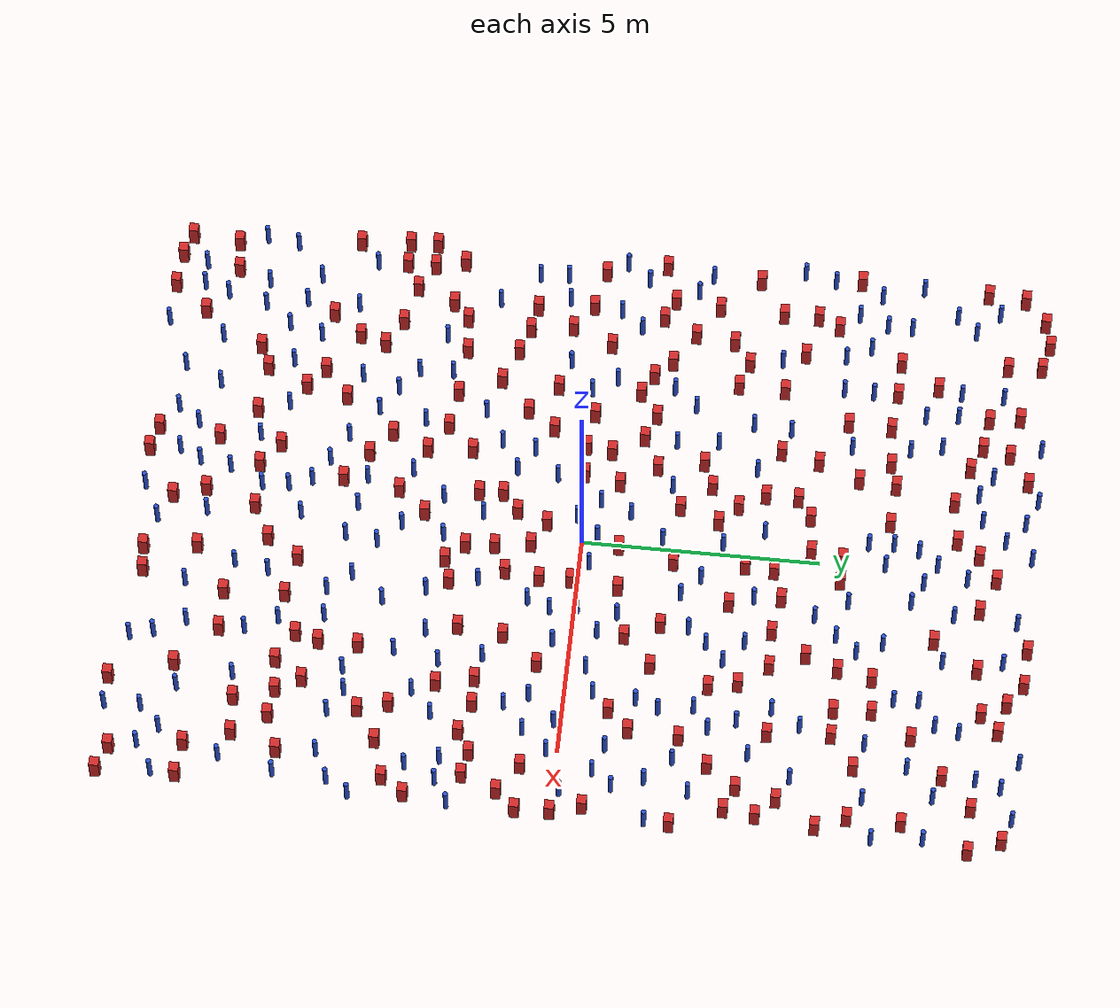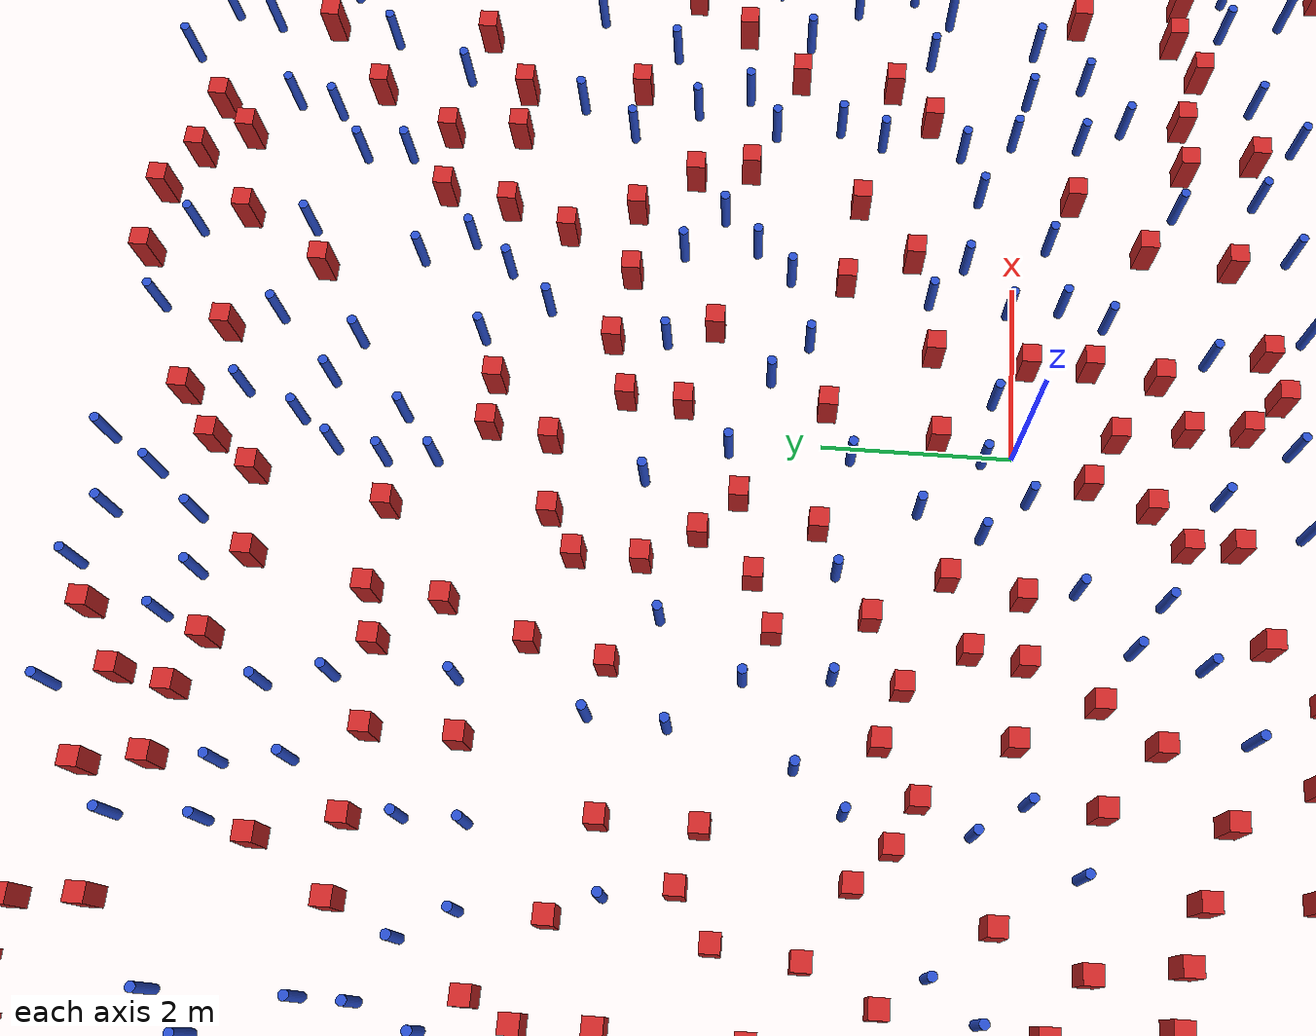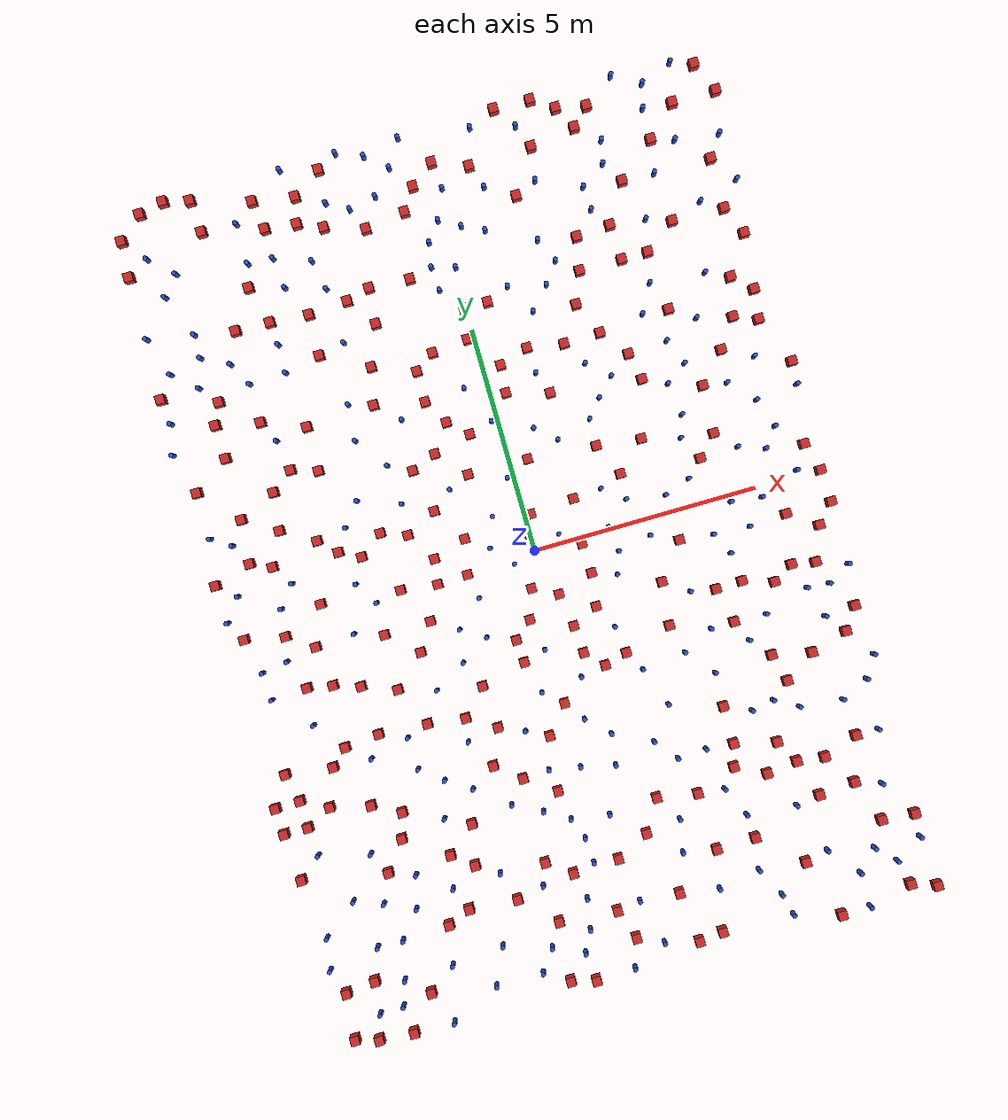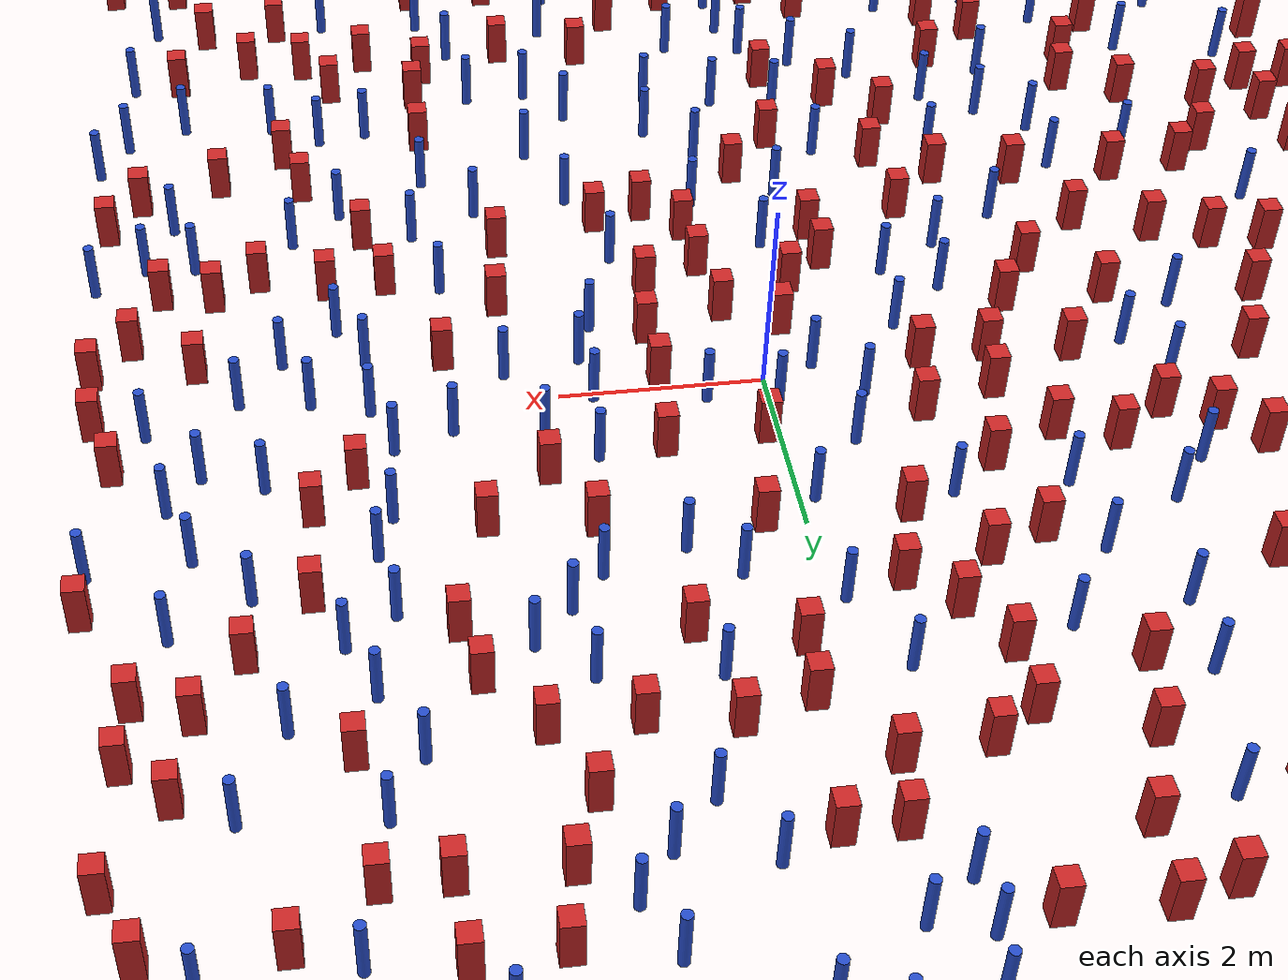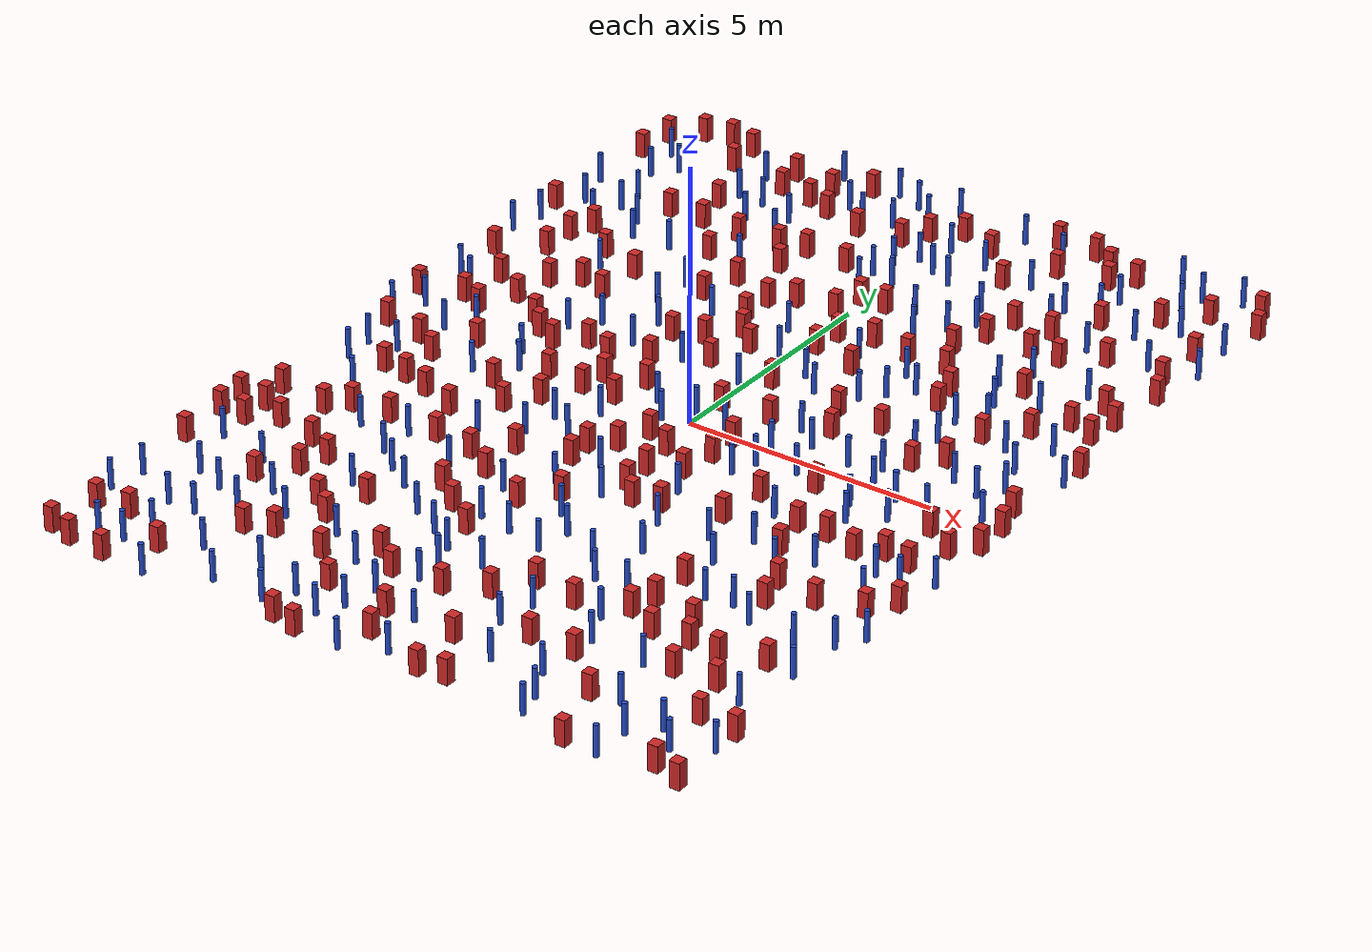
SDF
<sdf version="1.6">
  <model name="dense_15"><model name="square_post_obstacle0">
  <static>true</static>
  <pose frame="">-2.44541157408 -3.07652262404 1.91545236811e-07 -7.35059704564e-06 1.12565212e-07 2.39332434364e-05</pose>
  <link name="link">
    <pose frame="">0 0 0.25 0 -0 0</pose>
    <inertial>
      <mass>100</mass>
      <inertia>
        <ixx>0.166667</ixx>
        <ixy>0</ixy>
        <ixz>0</ixz>
        <iyy>0.166667</iyy>
        <iyz>0</iyz>
        <izz>0.166667</izz>
      </inertia>
    </inertial>
    <collision name="collision">
      <geometry>
        <box>
          <size>.2 .2 .5</size>
        </box>
      </geometry>
      <max_contacts>10</max_contacts>
      <surface>
        <contact>
          <ode/>
        </contact>
        <bounce/>
        <friction>
          <torsional>
            <ode/>
          </torsional>
          <ode/>
        </friction>
      </surface>
    </collision>
    <visual name="visual">
      <geometry>
        <box>
          <size>.2 .2 .5</size>
        </box>
      </geometry>
      <material>
        <script>
          <name>Gazebo/Red</name>
          <uri>file://media/materials/scripts/gazebo.material</uri>
        </script>
      </material>
    </visual>
    <self_collide>0</self_collide>
    <kinematic>0</kinematic>
  </link>
</model>
<model name="square_post_obstacle1">
  <static>true</static>
  <pose frame="">-2.60366853146 -0.84480059614 1.91545236811e-07 -7.35059704564e-06 1.12565212e-07 2.39332434364e-05</pose>
  <link name="link">
    <pose frame="">0 0 0.25 0 -0 0</pose>
    <inertial>
      <mass>100</mass>
      <inertia>
        <ixx>0.166667</ixx>
        <ixy>0</ixy>
        <ixz>0</ixz>
        <iyy>0.166667</iyy>
        <iyz>0</iyz>
        <izz>0.166667</izz>
      </inertia>
    </inertial>
    <collision name="collision">
      <geometry>
        <box>
          <size>.2 .2 .5</size>
        </box>
      </geometry>
      <max_contacts>10</max_contacts>
      <surface>
        <contact>
          <ode/>
        </contact>
        <bounce/>
        <friction>
          <torsional>
            <ode/>
          </torsional>
          <ode/>
        </friction>
      </surface>
    </collision>
    <visual name="visual">
      <geometry>
        <box>
          <size>.2 .2 .5</size>
        </box>
      </geometry>
      <material>
        <script>
          <name>Gazebo/Red</name>
          <uri>file://media/materials/scripts/gazebo.material</uri>
        </script>
      </material>
    </visual>
    <self_collide>0</self_collide>
    <kinematic>0</kinematic>
  </link>
</model>
<model name="pole_obstacle0">
  <static>true</static>
  <pose frame="">6.45569233629 -4.1689479482 7.38925637345e-09 -8.47170692796e-08 1.24976764786e-08 -1.74513093032e-07</pose>
  <link name="link">
  <pose frame="">0 0 0.3 0 -0 0</pose>
    <inertial>
      <mass>1</mass>
      <inertia>
        <ixx>0.145833</ixx>
        <ixy>0</ixy>
        <ixz>0</ixz>
        <iyy>0.145833</iyy>
        <iyz>0</iyz>
        <izz>0.125</izz>
      </inertia>
    </inertial>
    <collision name="collision">
      <geometry>
        <cylinder>
          <radius>0.05</radius>
          <length>.6</length>
        </cylinder>
      </geometry>
      <max_contacts>10</max_contacts>
      <surface>
        <contact>
          <ode/>
        </contact>
        <bounce/>
        <friction>
          <torsional>
            <ode/>
          </torsional>
          <ode/>
        </friction>
      </surface>
    </collision>
    <visual name="visual">
      <geometry>
        <cylinder>
          <radius>0.05</radius>
          <length>.6</length>
        </cylinder>
      </geometry>
      <material>
        <script>
          <name>Gazebo/Blue</name>
          <uri>file://media/materials/scripts/gazebo.material</uri>
        </script>
      </material>
    </visual>
    <self_collide>0</self_collide>
    <kinematic>0</kinematic>
  </link>
</model>
<model name="square_post_obstacle2">
  <static>true</static>
  <pose frame="">0.977631185792 -7.9997735086 1.91545236811e-07 -7.35059704564e-06 1.12565212e-07 2.39332434364e-05</pose>
  <link name="link">
    <pose frame="">0 0 0.25 0 -0 0</pose>
    <inertial>
      <mass>100</mass>
      <inertia>
        <ixx>0.166667</ixx>
        <ixy>0</ixy>
        <ixz>0</ixz>
        <iyy>0.166667</iyy>
        <iyz>0</iyz>
        <izz>0.166667</izz>
      </inertia>
    </inertial>
    <collision name="collision">
      <geometry>
        <box>
          <size>.2 .2 .5</size>
        </box>
      </geometry>
      <max_contacts>10</max_contacts>
      <surface>
        <contact>
          <ode/>
        </contact>
        <bounce/>
        <friction>
          <torsional>
            <ode/>
          </torsional>
          <ode/>
        </friction>
      </surface>
    </collision>
    <visual name="visual">
      <geometry>
        <box>
          <size>.2 .2 .5</size>
        </box>
      </geometry>
      <material>
        <script>
          <name>Gazebo/Red</name>
          <uri>file://media/materials/scripts/gazebo.material</uri>
        </script>
      </material>
    </visual>
    <self_collide>0</self_collide>
    <kinematic>0</kinematic>
  </link>
</model>
<model name="pole_obstacle1">
  <static>true</static>
  <pose frame="">-1.99702910462 -5.15641519759 7.38925637345e-09 -8.47170692799e-08 1.2497676507e-08 -1.74513093016e-07</pose>
  <link name="link">
  <pose frame="">0 0 0.3 0 -0 0</pose>
    <inertial>
      <mass>1</mass>
      <inertia>
        <ixx>0.145833</ixx>
        <ixy>0</ixy>
        <ixz>0</ixz>
        <iyy>0.145833</iyy>
        <iyz>0</iyz>
        <izz>0.125</izz>
      </inertia>
    </inertial>
    <collision name="collision">
      <geometry>
        <cylinder>
          <radius>0.05</radius>
          <length>.6</length>
        </cylinder>
      </geometry>
      <max_contacts>10</max_contacts>
      <surface>
        <contact>
          <ode/>
        </contact>
        <bounce/>
        <friction>
          <torsional>
            <ode/>
          </torsional>
          <ode/>
        </friction>
      </surface>
    </collision>
    <visual name="visual">
      <geometry>
        <cylinder>
          <radius>0.05</radius>
          <length>.6</length>
        </cylinder>
      </geometry>
      <material>
        <script>
          <name>Gazebo/Blue</name>
          <uri>file://media/materials/scripts/gazebo.material</uri>
        </script>
      </material>
    </visual>
    <self_collide>0</self_collide>
    <kinematic>0</kinematic>
  </link>
</model>
<model name="square_post_obstacle3">
  <static>true</static>
  <pose frame="">3.72914011373 -2.6606754903 1.91545236811e-07 -7.35059704564e-06 1.12565212e-07 2.39332434364e-05</pose>
  <link name="link">
    <pose frame="">0 0 0.25 0 -0 0</pose>
    <inertial>
      <mass>100</mass>
      <inertia>
        <ixx>0.166667</ixx>
        <ixy>0</ixy>
        <ixz>0</ixz>
        <iyy>0.166667</iyy>
        <iyz>0</iyz>
        <izz>0.166667</izz>
      </inertia>
    </inertial>
    <collision name="collision">
      <geometry>
        <box>
          <size>.2 .2 .5</size>
        </box>
      </geometry>
      <max_contacts>10</max_contacts>
      <surface>
        <contact>
          <ode/>
        </contact>
        <bounce/>
        <friction>
          <torsional>
            <ode/>
          </torsional>
          <ode/>
        </friction>
      </surface>
    </collision>
    <visual name="visual">
      <geometry>
        <box>
          <size>.2 .2 .5</size>
        </box>
      </geometry>
      <material>
        <script>
          <name>Gazebo/Red</name>
          <uri>file://media/materials/scripts/gazebo.material</uri>
        </script>
      </material>
    </visual>
    <self_collide>0</self_collide>
    <kinematic>0</kinematic>
  </link>
</model>
<model name="pole_obstacle2">
  <static>true</static>
  <pose frame="">3.82269848342 8.17413001489 7.38925637345e-09 -8.47170692793e-08 1.24976764408e-08 -1.74513093041e-07</pose>
  <link name="link">
  <pose frame="">0 0 0.3 0 -0 0</pose>
    <inertial>
      <mass>1</mass>
      <inertia>
        <ixx>0.145833</ixx>
        <ixy>0</ixy>
        <ixz>0</ixz>
        <iyy>0.145833</iyy>
        <iyz>0</iyz>
        <izz>0.125</izz>
      </inertia>
    </inertial>
    <collision name="collision">
      <geometry>
        <cylinder>
          <radius>0.05</radius>
          <length>.6</length>
        </cylinder>
      </geometry>
      <max_contacts>10</max_contacts>
      <surface>
        <contact>
          <ode/>
        </contact>
        <bounce/>
        <friction>
          <torsional>
            <ode/>
          </torsional>
          <ode/>
        </friction>
      </surface>
    </collision>
    <visual name="visual">
      <geometry>
        <cylinder>
          <radius>0.05</radius>
          <length>.6</length>
        </cylinder>
      </geometry>
      <material>
        <script>
          <name>Gazebo/Blue</name>
          <uri>file://media/materials/scripts/gazebo.material</uri>
        </script>
      </material>
    </visual>
    <self_collide>0</self_collide>
    <kinematic>0</kinematic>
  </link>
</model>
<model name="pole_obstacle3">
  <static>true</static>
  <pose frame="">-6.64374902842 -6.83395566095 7.38925637345e-09 -8.47170692796e-08 1.24976764786e-08 -1.74513093032e-07</pose>
  <link name="link">
  <pose frame="">0 0 0.3 0 -0 0</pose>
    <inertial>
      <mass>1</mass>
      <inertia>
        <ixx>0.145833</ixx>
        <ixy>0</ixy>
        <ixz>0</ixz>
        <iyy>0.145833</iyy>
        <iyz>0</iyz>
        <izz>0.125</izz>
      </inertia>
    </inertial>
    <collision name="collision">
      <geometry>
        <cylinder>
          <radius>0.05</radius>
          <length>.6</length>
        </cylinder>
      </geometry>
      <max_contacts>10</max_contacts>
      <surface>
        <contact>
          <ode/>
        </contact>
        <bounce/>
        <friction>
          <torsional>
            <ode/>
          </torsional>
          <ode/>
        </friction>
      </surface>
    </collision>
    <visual name="visual">
      <geometry>
        <cylinder>
          <radius>0.05</radius>
          <length>.6</length>
        </cylinder>
      </geometry>
      <material>
        <script>
          <name>Gazebo/Blue</name>
          <uri>file://media/materials/scripts/gazebo.material</uri>
        </script>
      </material>
    </visual>
    <self_collide>0</self_collide>
    <kinematic>0</kinematic>
  </link>
</model>
<model name="square_post_obstacle4">
  <static>true</static>
  <pose frame="">5.26585371671 -1.80309191971 1.91545236811e-07 -7.35059704564e-06 1.12565212e-07 2.39332434364e-05</pose>
  <link name="link">
    <pose frame="">0 0 0.25 0 -0 0</pose>
    <inertial>
      <mass>100</mass>
      <inertia>
        <ixx>0.166667</ixx>
        <ixy>0</ixy>
        <ixz>0</ixz>
        <iyy>0.166667</iyy>
        <iyz>0</iyz>
        <izz>0.166667</izz>
      </inertia>
    </inertial>
    <collision name="collision">
      <geometry>
        <box>
          <size>.2 .2 .5</size>
        </box>
      </geometry>
      <max_contacts>10</max_contacts>
      <surface>
        <contact>
          <ode/>
        </contact>
        <bounce/>
        <friction>
          <torsional>
            <ode/>
          </torsional>
          <ode/>
        </friction>
      </surface>
    </collision>
    <visual name="visual">
      <geometry>
        <box>
          <size>.2 .2 .5</size>
        </box>
      </geometry>
      <material>
        <script>
          <name>Gazebo/Red</name>
          <uri>file://media/materials/scripts/gazebo.material</uri>
        </script>
      </material>
    </visual>
    <self_collide>0</self_collide>
    <kinematic>0</kinematic>
  </link>
</model>
<model name="square_post_obstacle5">
  <static>true</static>
  <pose frame="">2.31487394498 8.45547136916 1.91545236811e-07 -7.35059704564e-06 1.12565212e-07 2.39332434364e-05</pose>
  <link name="link">
    <pose frame="">0 0 0.25 0 -0 0</pose>
    <inertial>
      <mass>100</mass>
      <inertia>
        <ixx>0.166667</ixx>
        <ixy>0</ixy>
        <ixz>0</ixz>
        <iyy>0.166667</iyy>
        <iyz>0</iyz>
        <izz>0.166667</izz>
      </inertia>
    </inertial>
    <collision name="collision">
      <geometry>
        <box>
          <size>.2 .2 .5</size>
        </box>
      </geometry>
      <max_contacts>10</max_contacts>
      <surface>
        <contact>
          <ode/>
        </contact>
        <bounce/>
        <friction>
          <torsional>
            <ode/>
          </torsional>
          <ode/>
        </friction>
      </surface>
    </collision>
    <visual name="visual">
      <geometry>
        <box>
          <size>.2 .2 .5</size>
        </box>
      </geometry>
      <material>
        <script>
          <name>Gazebo/Red</name>
          <uri>file://media/materials/scripts/gazebo.material</uri>
        </script>
      </material>
    </visual>
    <self_collide>0</self_collide>
    <kinematic>0</kinematic>
  </link>
</model>
<model name="square_post_obstacle6">
  <static>true</static>
  <pose frame="">-3.72830438656 8.32323099162 1.91545236811e-07 -7.35059704564e-06 1.12565212e-07 2.39332434364e-05</pose>
  <link name="link">
    <pose frame="">0 0 0.25 0 -0 0</pose>
    <inertial>
      <mass>100</mass>
      <inertia>
        <ixx>0.166667</ixx>
        <ixy>0</ixy>
        <ixz>0</ixz>
        <iyy>0.166667</iyy>
        <iyz>0</iyz>
        <izz>0.166667</izz>
      </inertia>
    </inertial>
    <collision name="collision">
      <geometry>
        <box>
          <size>.2 .2 .5</size>
        </box>
      </geometry>
      <max_contacts>10</max_contacts>
      <surface>
        <contact>
          <ode/>
        </contact>
        <bounce/>
        <friction>
          <torsional>
            <ode/>
          </torsional>
          <ode/>
        </friction>
      </surface>
    </collision>
    <visual name="visual">
      <geometry>
        <box>
          <size>.2 .2 .5</size>
        </box>
      </geometry>
      <material>
        <script>
          <name>Gazebo/Red</name>
          <uri>file://media/materials/scripts/gazebo.material</uri>
        </script>
      </material>
    </visual>
    <self_collide>0</self_collide>
    <kinematic>0</kinematic>
  </link>
</model>
<model name="pole_obstacle4">
  <static>true</static>
  <pose frame="">1.90457020753 6.46916176601 7.38925637345e-09 -8.47170692799e-08 1.24976765033e-08 -1.74513093018e-07</pose>
  <link name="link">
  <pose frame="">0 0 0.3 0 -0 0</pose>
    <inertial>
      <mass>1</mass>
      <inertia>
        <ixx>0.145833</ixx>
        <ixy>0</ixy>
        <ixz>0</ixz>
        <iyy>0.145833</iyy>
        <iyz>0</iyz>
        <izz>0.125</izz>
      </inertia>
    </inertial>
    <collision name="collision">
      <geometry>
        <cylinder>
          <radius>0.05</radius>
          <length>.6</length>
        </cylinder>
      </geometry>
      <max_contacts>10</max_contacts>
      <surface>
        <contact>
          <ode/>
        </contact>
        <bounce/>
        <friction>
          <torsional>
            <ode/>
          </torsional>
          <ode/>
        </friction>
      </surface>
    </collision>
    <visual name="visual">
      <geometry>
        <cylinder>
          <radius>0.05</radius>
          <length>.6</length>
        </cylinder>
      </geometry>
      <material>
        <script>
          <name>Gazebo/Blue</name>
          <uri>file://media/materials/scripts/gazebo.material</uri>
        </script>
      </material>
    </visual>
    <self_collide>0</self_collide>
    <kinematic>0</kinematic>
  </link>
</model>
<model name="pole_obstacle5">
  <static>true</static>
  <pose frame="">2.53907456771 -6.09498216123 7.38925637345e-09 -8.47170692798e-08 1.24976765033e-08 -1.74513093019e-07</pose>
  <link name="link">
  <pose frame="">0 0 0.3 0 -0 0</pose>
    <inertial>
      <mass>1</mass>
      <inertia>
        <ixx>0.145833</ixx>
        <ixy>0</ixy>
        <ixz>0</ixz>
        <iyy>0.145833</iyy>
        <iyz>0</iyz>
        <izz>0.125</izz>
      </inertia>
    </inertial>
    <collision name="collision">
      <geometry>
        <cylinder>
          <radius>0.05</radius>
          <length>.6</length>
        </cylinder>
      </geometry>
      <max_contacts>10</max_contacts>
      <surface>
        <contact>
          <ode/>
        </contact>
        <bounce/>
        <friction>
          <torsional>
            <ode/>
          </torsional>
          <ode/>
        </friction>
      </surface>
    </collision>
    <visual name="visual">
      <geometry>
        <cylinder>
          <radius>0.05</radius>
          <length>.6</length>
        </cylinder>
      </geometry>
      <material>
        <script>
          <name>Gazebo/Blue</name>
          <uri>file://media/materials/scripts/gazebo.material</uri>
        </script>
      </material>
    </visual>
    <self_collide>0</self_collide>
    <kinematic>0</kinematic>
  </link>
</model>
<model name="square_post_obstacle7">
  <static>true</static>
  <pose frame="">6.11921410497 4.16256446191 1.91545236811e-07 -7.35059704564e-06 1.12565212e-07 2.39332434364e-05</pose>
  <link name="link">
    <pose frame="">0 0 0.25 0 -0 0</pose>
    <inertial>
      <mass>100</mass>
      <inertia>
        <ixx>0.166667</ixx>
        <ixy>0</ixy>
        <ixz>0</ixz>
        <iyy>0.166667</iyy>
        <iyz>0</iyz>
        <izz>0.166667</izz>
      </inertia>
    </inertial>
    <collision name="collision">
      <geometry>
        <box>
          <size>.2 .2 .5</size>
        </box>
      </geometry>
      <max_contacts>10</max_contacts>
      <surface>
        <contact>
          <ode/>
        </contact>
        <bounce/>
        <friction>
          <torsional>
            <ode/>
          </torsional>
          <ode/>
        </friction>
      </surface>
    </collision>
    <visual name="visual">
      <geometry>
        <box>
          <size>.2 .2 .5</size>
        </box>
      </geometry>
      <material>
        <script>
          <name>Gazebo/Red</name>
          <uri>file://media/materials/scripts/gazebo.material</uri>
        </script>
      </material>
    </visual>
    <self_collide>0</self_collide>
    <kinematic>0</kinematic>
  </link>
</model>
<model name="square_post_obstacle8">
  <static>true</static>
  <pose frame="">-1.55427434783 -0.0952835881535 1.91545236811e-07 -7.35059704564e-06 1.12565212e-07 2.39332434364e-05</pose>
  <link name="link">
    <pose frame="">0 0 0.25 0 -0 0</pose>
    <inertial>
      <mass>100</mass>
      <inertia>
        <ixx>0.166667</ixx>
        <ixy>0</ixy>
        <ixz>0</ixz>
        <iyy>0.166667</iyy>
        <iyz>0</iyz>
        <izz>0.166667</izz>
      </inertia>
    </inertial>
    <collision name="collision">
      <geometry>
        <box>
          <size>.2 .2 .5</size>
        </box>
      </geometry>
      <max_contacts>10</max_contacts>
      <surface>
        <contact>
          <ode/>
        </contact>
        <bounce/>
        <friction>
          <torsional>
            <ode/>
          </torsional>
          <ode/>
        </friction>
      </surface>
    </collision>
    <visual name="visual">
      <geometry>
        <box>
          <size>.2 .2 .5</size>
        </box>
      </geometry>
      <material>
        <script>
          <name>Gazebo/Red</name>
          <uri>file://media/materials/scripts/gazebo.material</uri>
        </script>
      </material>
    </visual>
    <self_collide>0</self_collide>
    <kinematic>0</kinematic>
  </link>
</model>
<model name="pole_obstacle6">
  <static>true</static>
  <pose frame="">-2.53006117659 -3.58657340023 7.38925637345e-09 -8.47170692798e-08 1.24976764939e-08 -1.74513093025e-07</pose>
  <link name="link">
  <pose frame="">0 0 0.3 0 -0 0</pose>
    <inertial>
      <mass>1</mass>
      <inertia>
        <ixx>0.145833</ixx>
        <ixy>0</ixy>
        <ixz>0</ixz>
        <iyy>0.145833</iyy>
        <iyz>0</iyz>
        <izz>0.125</izz>
      </inertia>
    </inertial>
    <collision name="collision">
      <geometry>
        <cylinder>
          <radius>0.05</radius>
          <length>.6</length>
        </cylinder>
      </geometry>
      <max_contacts>10</max_contacts>
      <surface>
        <contact>
          <ode/>
        </contact>
        <bounce/>
        <friction>
          <torsional>
            <ode/>
          </torsional>
          <ode/>
        </friction>
      </surface>
    </collision>
    <visual name="visual">
      <geometry>
        <cylinder>
          <radius>0.05</radius>
          <length>.6</length>
        </cylinder>
      </geometry>
      <material>
        <script>
          <name>Gazebo/Blue</name>
          <uri>file://media/materials/scripts/gazebo.material</uri>
        </script>
      </material>
    </visual>
    <self_collide>0</self_collide>
    <kinematic>0</kinematic>
  </link>
</model>
<model name="pole_obstacle7">
  <static>true</static>
  <pose frame="">-6.21380209291 7.48486006199 7.38925637345e-09 -8.47170692796e-08 1.24976764786e-08 -1.74513093032e-07</pose>
  <link name="link">
  <pose frame="">0 0 0.3 0 -0 0</pose>
    <inertial>
      <mass>1</mass>
      <inertia>
        <ixx>0.145833</ixx>
        <ixy>0</ixy>
        <ixz>0</ixz>
        <iyy>0.145833</iyy>
        <iyz>0</iyz>
        <izz>0.125</izz>
      </inertia>
    </inertial>
    <collision name="collision">
      <geometry>
        <cylinder>
          <radius>0.05</radius>
          <length>.6</length>
        </cylinder>
      </geometry>
      <max_contacts>10</max_contacts>
      <surface>
        <contact>
          <ode/>
        </contact>
        <bounce/>
        <friction>
          <torsional>
            <ode/>
          </torsional>
          <ode/>
        </friction>
      </surface>
    </collision>
    <visual name="visual">
      <geometry>
        <cylinder>
          <radius>0.05</radius>
          <length>.6</length>
        </cylinder>
      </geometry>
      <material>
        <script>
          <name>Gazebo/Blue</name>
          <uri>file://media/materials/scripts/gazebo.material</uri>
        </script>
      </material>
    </visual>
    <self_collide>0</self_collide>
    <kinematic>0</kinematic>
  </link>
</model>
<model name="square_post_obstacle9">
  <static>true</static>
  <pose frame="">-4.79178633699 -8.59909285755 1.91545236811e-07 -7.35059704564e-06 1.12565212e-07 2.39332434364e-05</pose>
  <link name="link">
    <pose frame="">0 0 0.25 0 -0 0</pose>
    <inertial>
      <mass>100</mass>
      <inertia>
        <ixx>0.166667</ixx>
        <ixy>0</ixy>
        <ixz>0</ixz>
        <iyy>0.166667</iyy>
        <iyz>0</iyz>
        <izz>0.166667</izz>
      </inertia>
    </inertial>
    <collision name="collision">
      <geometry>
        <box>
          <size>.2 .2 .5</size>
        </box>
      </geometry>
      <max_contacts>10</max_contacts>
      <surface>
        <contact>
          <ode/>
        </contact>
        <bounce/>
        <friction>
          <torsional>
            <ode/>
          </torsional>
          <ode/>
        </friction>
      </surface>
    </collision>
    <visual name="visual">
      <geometry>
        <box>
          <size>.2 .2 .5</size>
        </box>
      </geometry>
      <material>
        <script>
          <name>Gazebo/Red</name>
          <uri>file://media/materials/scripts/gazebo.material</uri>
        </script>
      </material>
    </visual>
    <self_collide>0</self_collide>
    <kinematic>0</kinematic>
  </link>
</model>
<model name="square_post_obstacle10">
  <static>true</static>
  <pose frame="">3.54481908602 -1.87227291666 1.91545236811e-07 -7.35059704564e-06 1.12565212e-07 2.39332434364e-05</pose>
  <link name="link">
    <pose frame="">0 0 0.25 0 -0 0</pose>
    <inertial>
      <mass>100</mass>
      <inertia>
        <ixx>0.166667</ixx>
        <ixy>0</ixy>
        <ixz>0</ixz>
        <iyy>0.166667</iyy>
        <iyz>0</iyz>
        <izz>0.166667</izz>
      </inertia>
    </inertial>
    <collision name="collision">
      <geometry>
        <box>
          <size>.2 .2 .5</size>
        </box>
      </geometry>
      <max_contacts>10</max_contacts>
      <surface>
        <contact>
          <ode/>
        </contact>
        <bounce/>
        <friction>
          <torsional>
            <ode/>
          </torsional>
          <ode/>
        </friction>
      </surface>
    </collision>
    <visual name="visual">
      <geometry>
        <box>
          <size>.2 .2 .5</size>
        </box>
      </geometry>
      <material>
        <script>
          <name>Gazebo/Red</name>
          <uri>file://media/materials/scripts/gazebo.material</uri>
        </script>
      </material>
    </visual>
    <self_collide>0</self_collide>
    <kinematic>0</kinematic>
  </link>
</model>
<model name="square_post_obstacle11">
  <static>true</static>
  <pose frame="">2.01448924822 -7.3073891308 1.91545236811e-07 -7.35059704564e-06 1.12565212e-07 2.39332434364e-05</pose>
  <link name="link">
    <pose frame="">0 0 0.25 0 -0 0</pose>
    <inertial>
      <mass>100</mass>
      <inertia>
        <ixx>0.166667</ixx>
        <ixy>0</ixy>
        <ixz>0</ixz>
        <iyy>0.166667</iyy>
        <iyz>0</iyz>
        <izz>0.166667</izz>
      </inertia>
    </inertial>
    <collision name="collision">
      <geometry>
        <box>
          <size>.2 .2 .5</size>
        </box>
      </geometry>
      <max_contacts>10</max_contacts>
      <surface>
        <contact>
          <ode/>
        </contact>
        <bounce/>
        <friction>
          <torsional>
            <ode/>
          </torsional>
          <ode/>
        </friction>
      </surface>
    </collision>
    <visual name="visual">
      <geometry>
        <box>
          <size>.2 .2 .5</size>
        </box>
      </geometry>
      <material>
        <script>
          <name>Gazebo/Red</name>
          <uri>file://media/materials/scripts/gazebo.material</uri>
        </script>
      </material>
    </visual>
    <self_collide>0</self_collide>
    <kinematic>0</kinematic>
  </link>
</model>
<model name="square_post_obstacle12">
  <static>true</static>
  <pose frame="">2.35717753829 -2.35318234047 1.91545236811e-07 -7.35059704564e-06 1.12565212e-07 2.39332434364e-05</pose>
  <link name="link">
    <pose frame="">0 0 0.25 0 -0 0</pose>
    <inertial>
      <mass>100</mass>
      <inertia>
        <ixx>0.166667</ixx>
        <ixy>0</ixy>
        <ixz>0</ixz>
        <iyy>0.166667</iyy>
        <iyz>0</iyz>
        <izz>0.166667</izz>
      </inertia>
    </inertial>
    <collision name="collision">
      <geometry>
        <box>
          <size>.2 .2 .5</size>
        </box>
      </geometry>
      <max_contacts>10</max_contacts>
      <surface>
        <contact>
          <ode/>
        </contact>
        <bounce/>
        <friction>
          <torsional>
            <ode/>
          </torsional>
          <ode/>
        </friction>
      </surface>
    </collision>
    <visual name="visual">
      <geometry>
        <box>
          <size>.2 .2 .5</size>
        </box>
      </geometry>
      <material>
        <script>
          <name>Gazebo/Red</name>
          <uri>file://media/materials/scripts/gazebo.material</uri>
        </script>
      </material>
    </visual>
    <self_collide>0</self_collide>
    <kinematic>0</kinematic>
  </link>
</model>
<model name="square_post_obstacle13">
  <static>true</static>
  <pose frame="">-5.38632423519 -9.33042135483 1.91545236811e-07 -7.35059704564e-06 1.12565212e-07 2.39332434364e-05</pose>
  <link name="link">
    <pose frame="">0 0 0.25 0 -0 0</pose>
    <inertial>
      <mass>100</mass>
      <inertia>
        <ixx>0.166667</ixx>
        <ixy>0</ixy>
        <ixz>0</ixz>
        <iyy>0.166667</iyy>
        <iyz>0</iyz>
        <izz>0.166667</izz>
      </inertia>
    </inertial>
    <collision name="collision">
      <geometry>
        <box>
          <size>.2 .2 .5</size>
        </box>
      </geometry>
      <max_contacts>10</max_contacts>
      <surface>
        <contact>
          <ode/>
        </contact>
        <bounce/>
        <friction>
          <torsional>
            <ode/>
          </torsional>
          <ode/>
        </friction>
      </surface>
    </collision>
    <visual name="visual">
      <geometry>
        <box>
          <size>.2 .2 .5</size>
        </box>
      </geometry>
      <material>
        <script>
          <name>Gazebo/Red</name>
          <uri>file://media/materials/scripts/gazebo.material</uri>
        </script>
      </material>
    </visual>
    <self_collide>0</self_collide>
    <kinematic>0</kinematic>
  </link>
</model>
<model name="pole_obstacle8">
  <static>true</static>
  <pose frame="">2.49860189125 -0.361555364977 7.38925637345e-09 -8.471706928e-08 1.24976765172e-08 -1.74513093013e-07</pose>
  <link name="link">
  <pose frame="">0 0 0.3 0 -0 0</pose>
    <inertial>
      <mass>1</mass>
      <inertia>
        <ixx>0.145833</ixx>
        <ixy>0</ixy>
        <ixz>0</ixz>
        <iyy>0.145833</iyy>
        <iyz>0</iyz>
        <izz>0.125</izz>
      </inertia>
    </inertial>
    <collision name="collision">
      <geometry>
        <cylinder>
          <radius>0.05</radius>
          <length>.6</length>
        </cylinder>
      </geometry>
      <max_contacts>10</max_contacts>
      <surface>
        <contact>
          <ode/>
        </contact>
        <bounce/>
        <friction>
          <torsional>
            <ode/>
          </torsional>
          <ode/>
        </friction>
      </surface>
    </collision>
    <visual name="visual">
      <geometry>
        <cylinder>
          <radius>0.05</radius>
          <length>.6</length>
        </cylinder>
      </geometry>
      <material>
        <script>
          <name>Gazebo/Blue</name>
          <uri>file://media/materials/scripts/gazebo.material</uri>
        </script>
      </material>
    </visual>
    <self_collide>0</self_collide>
    <kinematic>0</kinematic>
  </link>
</model>
<model name="square_post_obstacle14">
  <static>true</static>
  <pose frame="">-0.670995625879 2.82150129431 1.91545236811e-07 -7.35059704564e-06 1.12565212e-07 2.39332434364e-05</pose>
  <link name="link">
    <pose frame="">0 0 0.25 0 -0 0</pose>
    <inertial>
      <mass>100</mass>
      <inertia>
        <ixx>0.166667</ixx>
        <ixy>0</ixy>
        <ixz>0</ixz>
        <iyy>0.166667</iyy>
        <iyz>0</iyz>
        <izz>0.166667</izz>
      </inertia>
    </inertial>
    <collision name="collision">
      <geometry>
        <box>
          <size>.2 .2 .5</size>
        </box>
      </geometry>
      <max_contacts>10</max_contacts>
      <surface>
        <contact>
          <ode/>
        </contact>
        <bounce/>
        <friction>
          <torsional>
            <ode/>
          </torsional>
          <ode/>
        </friction>
      </surface>
    </collision>
    <visual name="visual">
      <geometry>
        <box>
          <size>.2 .2 .5</size>
        </box>
      </geometry>
      <material>
        <script>
          <name>Gazebo/Red</name>
          <uri>file://media/materials/scripts/gazebo.material</uri>
        </script>
      </material>
    </visual>
    <self_collide>0</self_collide>
    <kinematic>0</kinematic>
  </link>
</model>
<model name="square_post_obstacle15">
  <static>true</static>
  <pose frame="">4.31363352942 -3.57697256788 1.91545236811e-07 -7.35059704564e-06 1.12565212e-07 2.39332434364e-05</pose>
  <link name="link">
    <pose frame="">0 0 0.25 0 -0 0</pose>
    <inertial>
      <mass>100</mass>
      <inertia>
        <ixx>0.166667</ixx>
        <ixy>0</ixy>
        <ixz>0</ixz>
        <iyy>0.166667</iyy>
        <iyz>0</iyz>
        <izz>0.166667</izz>
      </inertia>
    </inertial>
    <collision name="collision">
      <geometry>
        <box>
          <size>.2 .2 .5</size>
        </box>
      </geometry>
      <max_contacts>10</max_contacts>
      <surface>
        <contact>
          <ode/>
        </contact>
        <bounce/>
        <friction>
          <torsional>
            <ode/>
          </torsional>
          <ode/>
        </friction>
      </surface>
    </collision>
    <visual name="visual">
      <geometry>
        <box>
          <size>.2 .2 .5</size>
        </box>
      </geometry>
      <material>
        <script>
          <name>Gazebo/Red</name>
          <uri>file://media/materials/scripts/gazebo.material</uri>
        </script>
      </material>
    </visual>
    <self_collide>0</self_collide>
    <kinematic>0</kinematic>
  </link>
</model>
<model name="square_post_obstacle16">
  <static>true</static>
  <pose frame="">-6.71427949328 3.21412606372 1.91545236811e-07 -7.35059704564e-06 1.12565212e-07 2.39332434364e-05</pose>
  <link name="link">
    <pose frame="">0 0 0.25 0 -0 0</pose>
    <inertial>
      <mass>100</mass>
      <inertia>
        <ixx>0.166667</ixx>
        <ixy>0</ixy>
        <ixz>0</ixz>
        <iyy>0.166667</iyy>
        <iyz>0</iyz>
        <izz>0.166667</izz>
      </inertia>
    </inertial>
    <collision name="collision">
      <geometry>
        <box>
          <size>.2 .2 .5</size>
        </box>
      </geometry>
      <max_contacts>10</max_contacts>
      <surface>
        <contact>
          <ode/>
        </contact>
        <bounce/>
        <friction>
          <torsional>
            <ode/>
          </torsional>
          <ode/>
        </friction>
      </surface>
    </collision>
    <visual name="visual">
      <geometry>
        <box>
          <size>.2 .2 .5</size>
        </box>
      </geometry>
      <material>
        <script>
          <name>Gazebo/Red</name>
          <uri>file://media/materials/scripts/gazebo.material</uri>
        </script>
      </material>
    </visual>
    <self_collide>0</self_collide>
    <kinematic>0</kinematic>
  </link>
</model>
<model name="pole_obstacle9">
  <static>true</static>
  <pose frame="">-5.82757588998 6.53122143702 7.38925637345e-09 -8.47170692796e-08 1.24976764786e-08 -1.74513093032e-07</pose>
  <link name="link">
  <pose frame="">0 0 0.3 0 -0 0</pose>
    <inertial>
      <mass>1</mass>
      <inertia>
        <ixx>0.145833</ixx>
        <ixy>0</ixy>
        <ixz>0</ixz>
        <iyy>0.145833</iyy>
        <iyz>0</iyz>
        <izz>0.125</izz>
      </inertia>
    </inertial>
    <collision name="collision">
      <geometry>
        <cylinder>
          <radius>0.05</radius>
          <length>.6</length>
        </cylinder>
      </geometry>
      <max_contacts>10</max_contacts>
      <surface>
        <contact>
          <ode/>
        </contact>
        <bounce/>
        <friction>
          <torsional>
            <ode/>
          </torsional>
          <ode/>
        </friction>
      </surface>
    </collision>
    <visual name="visual">
      <geometry>
        <cylinder>
          <radius>0.05</radius>
          <length>.6</length>
        </cylinder>
      </geometry>
      <material>
        <script>
          <name>Gazebo/Blue</name>
          <uri>file://media/materials/scripts/gazebo.material</uri>
        </script>
      </material>
    </visual>
    <self_collide>0</self_collide>
    <kinematic>0</kinematic>
  </link>
</model>
<model name="square_post_obstacle17">
  <static>true</static>
  <pose frame="">-2.2607761565 9.23892513766 1.91545236811e-07 -7.35059704564e-06 1.12565212e-07 2.39332434364e-05</pose>
  <link name="link">
    <pose frame="">0 0 0.25 0 -0 0</pose>
    <inertial>
      <mass>100</mass>
      <inertia>
        <ixx>0.166667</ixx>
        <ixy>0</ixy>
        <ixz>0</ixz>
        <iyy>0.166667</iyy>
        <iyz>0</iyz>
        <izz>0.166667</izz>
      </inertia>
    </inertial>
    <collision name="collision">
      <geometry>
        <box>
          <size>.2 .2 .5</size>
        </box>
      </geometry>
      <max_contacts>10</max_contacts>
      <surface>
        <contact>
          <ode/>
        </contact>
        <bounce/>
        <friction>
          <torsional>
            <ode/>
          </torsional>
          <ode/>
        </friction>
      </surface>
    </collision>
    <visual name="visual">
      <geometry>
        <box>
          <size>.2 .2 .5</size>
        </box>
      </geometry>
      <material>
        <script>
          <name>Gazebo/Red</name>
          <uri>file://media/materials/scripts/gazebo.material</uri>
        </script>
      </material>
    </visual>
    <self_collide>0</self_collide>
    <kinematic>0</kinematic>
  </link>
</model>
<model name="square_post_obstacle18">
  <static>true</static>
  <pose frame="">-0.710924107963 7.84707226629 1.91545236811e-07 -7.35059704564e-06 1.12565212e-07 2.39332434364e-05</pose>
  <link name="link">
    <pose frame="">0 0 0.25 0 -0 0</pose>
    <inertial>
      <mass>100</mass>
      <inertia>
        <ixx>0.166667</ixx>
        <ixy>0</ixy>
        <ixz>0</ixz>
        <iyy>0.166667</iyy>
        <iyz>0</iyz>
        <izz>0.166667</izz>
      </inertia>
    </inertial>
    <collision name="collision">
      <geometry>
        <box>
          <size>.2 .2 .5</size>
        </box>
      </geometry>
      <max_contacts>10</max_contacts>
      <surface>
        <contact>
          <ode/>
        </contact>
        <bounce/>
        <friction>
          <torsional>
            <ode/>
          </torsional>
          <ode/>
        </friction>
      </surface>
    </collision>
    <visual name="visual">
      <geometry>
        <box>
          <size>.2 .2 .5</size>
        </box>
      </geometry>
      <material>
        <script>
          <name>Gazebo/Red</name>
          <uri>file://media/materials/scripts/gazebo.material</uri>
        </script>
      </material>
    </visual>
    <self_collide>0</self_collide>
    <kinematic>0</kinematic>
  </link>
</model>
<model name="pole_obstacle10">
  <static>true</static>
  <pose frame="">3.82203805097 -0.716511106543 7.38925637345e-09 -8.471706928e-08 1.24976765177e-08 -1.74513093012e-07</pose>
  <link name="link">
  <pose frame="">0 0 0.3 0 -0 0</pose>
    <inertial>
      <mass>1</mass>
      <inertia>
        <ixx>0.145833</ixx>
        <ixy>0</ixy>
        <ixz>0</ixz>
        <iyy>0.145833</iyy>
        <iyz>0</iyz>
        <izz>0.125</izz>
      </inertia>
    </inertial>
    <collision name="collision">
      <geometry>
        <cylinder>
          <radius>0.05</radius>
          <length>.6</length>
        </cylinder>
      </geometry>
      <max_contacts>10</max_contacts>
      <surface>
        <contact>
          <ode/>
        </contact>
        <bounce/>
        <friction>
          <torsional>
            <ode/>
          </torsional>
          <ode/>
        </friction>
      </surface>
    </collision>
    <visual name="visual">
      <geometry>
        <cylinder>
          <radius>0.05</radius>
          <length>.6</length>
        </cylinder>
      </geometry>
      <material>
        <script>
          <name>Gazebo/Blue</name>
          <uri>file://media/materials/scripts/gazebo.material</uri>
        </script>
      </material>
    </visual>
    <self_collide>0</self_collide>
    <kinematic>0</kinematic>
  </link>
</model>
<model name="square_post_obstacle19">
  <static>true</static>
  <pose frame="">6.00379199853 -3.51849045793 1.91545236811e-07 -7.35059704564e-06 1.12565212e-07 2.39332434364e-05</pose>
  <link name="link">
    <pose frame="">0 0 0.25 0 -0 0</pose>
    <inertial>
      <mass>100</mass>
      <inertia>
        <ixx>0.166667</ixx>
        <ixy>0</ixy>
        <ixz>0</ixz>
        <iyy>0.166667</iyy>
        <iyz>0</iyz>
        <izz>0.166667</izz>
      </inertia>
    </inertial>
    <collision name="collision">
      <geometry>
        <box>
          <size>.2 .2 .5</size>
        </box>
      </geometry>
      <max_contacts>10</max_contacts>
      <surface>
        <contact>
          <ode/>
        </contact>
        <bounce/>
        <friction>
          <torsional>
            <ode/>
          </torsional>
          <ode/>
        </friction>
      </surface>
    </collision>
    <visual name="visual">
      <geometry>
        <box>
          <size>.2 .2 .5</size>
        </box>
      </geometry>
      <material>
        <script>
          <name>Gazebo/Red</name>
          <uri>file://media/materials/scripts/gazebo.material</uri>
        </script>
      </material>
    </visual>
    <self_collide>0</self_collide>
    <kinematic>0</kinematic>
  </link>
</model>
<model name="pole_obstacle11">
  <static>true</static>
  <pose frame="">6.1561207919 -4.64312427732 7.38925637345e-09 -8.47170692796e-08 1.24976764786e-08 -1.74513093032e-07</pose>
  <link name="link">
  <pose frame="">0 0 0.3 0 -0 0</pose>
    <inertial>
      <mass>1</mass>
      <inertia>
        <ixx>0.145833</ixx>
        <ixy>0</ixy>
        <ixz>0</ixz>
        <iyy>0.145833</iyy>
        <iyz>0</iyz>
        <izz>0.125</izz>
      </inertia>
    </inertial>
    <collision name="collision">
      <geometry>
        <cylinder>
          <radius>0.05</radius>
          <length>.6</length>
        </cylinder>
      </geometry>
      <max_contacts>10</max_contacts>
      <surface>
        <contact>
          <ode/>
        </contact>
        <bounce/>
        <friction>
          <torsional>
            <ode/>
          </torsional>
          <ode/>
        </friction>
      </surface>
    </collision>
    <visual name="visual">
      <geometry>
        <cylinder>
          <radius>0.05</radius>
          <length>.6</length>
        </cylinder>
      </geometry>
      <material>
        <script>
          <name>Gazebo/Blue</name>
          <uri>file://media/materials/scripts/gazebo.material</uri>
        </script>
      </material>
    </visual>
    <self_collide>0</self_collide>
    <kinematic>0</kinematic>
  </link>
</model>
<model name="square_post_obstacle20">
  <static>true</static>
  <pose frame="">-0.944631790187 1.99235051984 1.91545236811e-07 -7.35059704564e-06 1.12565212e-07 2.39332434364e-05</pose>
  <link name="link">
    <pose frame="">0 0 0.25 0 -0 0</pose>
    <inertial>
      <mass>100</mass>
      <inertia>
        <ixx>0.166667</ixx>
        <ixy>0</ixy>
        <ixz>0</ixz>
        <iyy>0.166667</iyy>
        <iyz>0</iyz>
        <izz>0.166667</izz>
      </inertia>
    </inertial>
    <collision name="collision">
      <geometry>
        <box>
          <size>.2 .2 .5</size>
        </box>
      </geometry>
      <max_contacts>10</max_contacts>
      <surface>
        <contact>
          <ode/>
        </contact>
        <bounce/>
        <friction>
          <torsional>
            <ode/>
          </torsional>
          <ode/>
        </friction>
      </surface>
    </collision>
    <visual name="visual">
      <geometry>
        <box>
          <size>.2 .2 .5</size>
        </box>
      </geometry>
      <material>
        <script>
          <name>Gazebo/Red</name>
          <uri>file://media/materials/scripts/gazebo.material</uri>
        </script>
      </material>
    </visual>
    <self_collide>0</self_collide>
    <kinematic>0</kinematic>
  </link>
</model>
<model name="pole_obstacle12">
  <static>true</static>
  <pose frame="">0.215988565415 -2.90076868346 7.38925637345e-09 -8.47170692792e-08 1.24976764352e-08 -1.74513093043e-07</pose>
  <link name="link">
  <pose frame="">0 0 0.3 0 -0 0</pose>
    <inertial>
      <mass>1</mass>
      <inertia>
        <ixx>0.145833</ixx>
        <ixy>0</ixy>
        <ixz>0</ixz>
        <iyy>0.145833</iyy>
        <iyz>0</iyz>
        <izz>0.125</izz>
      </inertia>
    </inertial>
    <collision name="collision">
      <geometry>
        <cylinder>
          <radius>0.05</radius>
          <length>.6</length>
        </cylinder>
      </geometry>
      <max_contacts>10</max_contacts>
      <surface>
        <contact>
          <ode/>
        </contact>
        <bounce/>
        <friction>
          <torsional>
            <ode/>
          </torsional>
          <ode/>
        </friction>
      </surface>
    </collision>
    <visual name="visual">
      <geometry>
        <cylinder>
          <radius>0.05</radius>
          <length>.6</length>
        </cylinder>
      </geometry>
      <material>
        <script>
          <name>Gazebo/Blue</name>
          <uri>file://media/materials/scripts/gazebo.material</uri>
        </script>
      </material>
    </visual>
    <self_collide>0</self_collide>
    <kinematic>0</kinematic>
  </link>
</model>
<model name="square_post_obstacle21">
  <static>true</static>
  <pose frame="">6.33950803841 -3.03932088624 1.91545236811e-07 -7.35059704564e-06 1.12565212e-07 2.39332434364e-05</pose>
  <link name="link">
    <pose frame="">0 0 0.25 0 -0 0</pose>
    <inertial>
      <mass>100</mass>
      <inertia>
        <ixx>0.166667</ixx>
        <ixy>0</ixy>
        <ixz>0</ixz>
        <iyy>0.166667</iyy>
        <iyz>0</iyz>
        <izz>0.166667</izz>
      </inertia>
    </inertial>
    <collision name="collision">
      <geometry>
        <box>
          <size>.2 .2 .5</size>
        </box>
      </geometry>
      <max_contacts>10</max_contacts>
      <surface>
        <contact>
          <ode/>
        </contact>
        <bounce/>
        <friction>
          <torsional>
            <ode/>
          </torsional>
          <ode/>
        </friction>
      </surface>
    </collision>
    <visual name="visual">
      <geometry>
        <box>
          <size>.2 .2 .5</size>
        </box>
      </geometry>
      <material>
        <script>
          <name>Gazebo/Red</name>
          <uri>file://media/materials/scripts/gazebo.material</uri>
        </script>
      </material>
    </visual>
    <self_collide>0</self_collide>
    <kinematic>0</kinematic>
  </link>
</model>
<model name="pole_obstacle13">
  <static>true</static>
  <pose frame="">4.75254022368 3.89881679813 7.38925637345e-09 -8.47170692798e-08 1.24976764937e-08 -1.74513093023e-07</pose>
  <link name="link">
  <pose frame="">0 0 0.3 0 -0 0</pose>
    <inertial>
      <mass>1</mass>
      <inertia>
        <ixx>0.145833</ixx>
        <ixy>0</ixy>
        <ixz>0</ixz>
        <iyy>0.145833</iyy>
        <iyz>0</iyz>
        <izz>0.125</izz>
      </inertia>
    </inertial>
    <collision name="collision">
      <geometry>
        <cylinder>
          <radius>0.05</radius>
          <length>.6</length>
        </cylinder>
      </geometry>
      <max_contacts>10</max_contacts>
      <surface>
        <contact>
          <ode/>
        </contact>
        <bounce/>
        <friction>
          <torsional>
            <ode/>
          </torsional>
          <ode/>
        </friction>
      </surface>
    </collision>
    <visual name="visual">
      <geometry>
        <cylinder>
          <radius>0.05</radius>
          <length>.6</length>
        </cylinder>
      </geometry>
      <material>
        <script>
          <name>Gazebo/Blue</name>
          <uri>file://media/materials/scripts/gazebo.material</uri>
        </script>
      </material>
    </visual>
    <self_collide>0</self_collide>
    <kinematic>0</kinematic>
  </link>
</model>
<model name="square_post_obstacle22">
  <static>true</static>
  <pose frame="">-4.94284263229 6.36715848857 1.91545236811e-07 -7.35059704564e-06 1.12565212e-07 2.39332434364e-05</pose>
  <link name="link">
    <pose frame="">0 0 0.25 0 -0 0</pose>
    <inertial>
      <mass>100</mass>
      <inertia>
        <ixx>0.166667</ixx>
        <ixy>0</ixy>
        <ixz>0</ixz>
        <iyy>0.166667</iyy>
        <iyz>0</iyz>
        <izz>0.166667</izz>
      </inertia>
    </inertial>
    <collision name="collision">
      <geometry>
        <box>
          <size>.2 .2 .5</size>
        </box>
      </geometry>
      <max_contacts>10</max_contacts>
      <surface>
        <contact>
          <ode/>
        </contact>
        <bounce/>
        <friction>
          <torsional>
            <ode/>
          </torsional>
          <ode/>
        </friction>
      </surface>
    </collision>
    <visual name="visual">
      <geometry>
        <box>
          <size>.2 .2 .5</size>
        </box>
      </geometry>
      <material>
        <script>
          <name>Gazebo/Red</name>
          <uri>file://media/materials/scripts/gazebo.material</uri>
        </script>
      </material>
    </visual>
    <self_collide>0</self_collide>
    <kinematic>0</kinematic>
  </link>
</model>
<model name="pole_obstacle14">
  <static>true</static>
  <pose frame="">-0.386376105266 -2.11954362649 7.38925637345e-09 -8.471706928e-08 1.24976765084e-08 -1.74513093017e-07</pose>
  <link name="link">
  <pose frame="">0 0 0.3 0 -0 0</pose>
    <inertial>
      <mass>1</mass>
      <inertia>
        <ixx>0.145833</ixx>
        <ixy>0</ixy>
        <ixz>0</ixz>
        <iyy>0.145833</iyy>
        <iyz>0</iyz>
        <izz>0.125</izz>
      </inertia>
    </inertial>
    <collision name="collision">
      <geometry>
        <cylinder>
          <radius>0.05</radius>
          <length>.6</length>
        </cylinder>
      </geometry>
      <max_contacts>10</max_contacts>
      <surface>
        <contact>
          <ode/>
        </contact>
        <bounce/>
        <friction>
          <torsional>
            <ode/>
          </torsional>
          <ode/>
        </friction>
      </surface>
    </collision>
    <visual name="visual">
      <geometry>
        <cylinder>
          <radius>0.05</radius>
          <length>.6</length>
        </cylinder>
      </geometry>
      <material>
        <script>
          <name>Gazebo/Blue</name>
          <uri>file://media/materials/scripts/gazebo.material</uri>
        </script>
      </material>
    </visual>
    <self_collide>0</self_collide>
    <kinematic>0</kinematic>
  </link>
</model>
<model name="pole_obstacle15">
  <static>true</static>
  <pose frame="">2.8436868365 -6.76617443891 7.38925637345e-09 -8.47170692798e-08 1.24976765033e-08 -1.74513093019e-07</pose>
  <link name="link">
  <pose frame="">0 0 0.3 0 -0 0</pose>
    <inertial>
      <mass>1</mass>
      <inertia>
        <ixx>0.145833</ixx>
        <ixy>0</ixy>
        <ixz>0</ixz>
        <iyy>0.145833</iyy>
        <iyz>0</iyz>
        <izz>0.125</izz>
      </inertia>
    </inertial>
    <collision name="collision">
      <geometry>
        <cylinder>
          <radius>0.05</radius>
          <length>.6</length>
        </cylinder>
      </geometry>
      <max_contacts>10</max_contacts>
      <surface>
        <contact>
          <ode/>
        </contact>
        <bounce/>
        <friction>
          <torsional>
            <ode/>
          </torsional>
          <ode/>
        </friction>
      </surface>
    </collision>
    <visual name="visual">
      <geometry>
        <cylinder>
          <radius>0.05</radius>
          <length>.6</length>
        </cylinder>
      </geometry>
      <material>
        <script>
          <name>Gazebo/Blue</name>
          <uri>file://media/materials/scripts/gazebo.material</uri>
        </script>
      </material>
    </visual>
    <self_collide>0</self_collide>
    <kinematic>0</kinematic>
  </link>
</model>
<model name="pole_obstacle16">
  <static>true</static>
  <pose frame="">-5.87785930533 -6.22777984309 7.38925637345e-09 -8.47170692796e-08 1.24976764786e-08 -1.74513093032e-07</pose>
  <link name="link">
  <pose frame="">0 0 0.3 0 -0 0</pose>
    <inertial>
      <mass>1</mass>
      <inertia>
        <ixx>0.145833</ixx>
        <ixy>0</ixy>
        <ixz>0</ixz>
        <iyy>0.145833</iyy>
        <iyz>0</iyz>
        <izz>0.125</izz>
      </inertia>
    </inertial>
    <collision name="collision">
      <geometry>
        <cylinder>
          <radius>0.05</radius>
          <length>.6</length>
        </cylinder>
      </geometry>
      <max_contacts>10</max_contacts>
      <surface>
        <contact>
          <ode/>
        </contact>
        <bounce/>
        <friction>
          <torsional>
            <ode/>
          </torsional>
          <ode/>
        </friction>
      </surface>
    </collision>
    <visual name="visual">
      <geometry>
        <cylinder>
          <radius>0.05</radius>
          <length>.6</length>
        </cylinder>
      </geometry>
      <material>
        <script>
          <name>Gazebo/Blue</name>
          <uri>file://media/materials/scripts/gazebo.material</uri>
        </script>
      </material>
    </visual>
    <self_collide>0</self_collide>
    <kinematic>0</kinematic>
  </link>
</model>
<model name="square_post_obstacle23">
  <static>true</static>
  <pose frame="">-5.13417449397 -2.9715054325 1.91545236811e-07 -7.35059704564e-06 1.12565212e-07 2.39332434364e-05</pose>
  <link name="link">
    <pose frame="">0 0 0.25 0 -0 0</pose>
    <inertial>
      <mass>100</mass>
      <inertia>
        <ixx>0.166667</ixx>
        <ixy>0</ixy>
        <ixz>0</ixz>
        <iyy>0.166667</iyy>
        <iyz>0</iyz>
        <izz>0.166667</izz>
      </inertia>
    </inertial>
    <collision name="collision">
      <geometry>
        <box>
          <size>.2 .2 .5</size>
        </box>
      </geometry>
      <max_contacts>10</max_contacts>
      <surface>
        <contact>
          <ode/>
        </contact>
        <bounce/>
        <friction>
          <torsional>
            <ode/>
          </torsional>
          <ode/>
        </friction>
      </surface>
    </collision>
    <visual name="visual">
      <geometry>
        <box>
          <size>.2 .2 .5</size>
        </box>
      </geometry>
      <material>
        <script>
          <name>Gazebo/Red</name>
          <uri>file://media/materials/scripts/gazebo.material</uri>
        </script>
      </material>
    </visual>
    <self_collide>0</self_collide>
    <kinematic>0</kinematic>
  </link>
</model>
<model name="pole_obstacle17">
  <static>true</static>
  <pose frame="">3.94140053442 -3.13863201137 7.38925637345e-09 -8.47170692798e-08 1.24976764939e-08 -1.74513093025e-07</pose>
  <link name="link">
  <pose frame="">0 0 0.3 0 -0 0</pose>
    <inertial>
      <mass>1</mass>
      <inertia>
        <ixx>0.145833</ixx>
        <ixy>0</ixy>
        <ixz>0</ixz>
        <iyy>0.145833</iyy>
        <iyz>0</iyz>
        <izz>0.125</izz>
      </inertia>
    </inertial>
    <collision name="collision">
      <geometry>
        <cylinder>
          <radius>0.05</radius>
          <length>.6</length>
        </cylinder>
      </geometry>
      <max_contacts>10</max_contacts>
      <surface>
        <contact>
          <ode/>
        </contact>
        <bounce/>
        <friction>
          <torsional>
            <ode/>
          </torsional>
          <ode/>
        </friction>
      </surface>
    </collision>
    <visual name="visual">
      <geometry>
        <cylinder>
          <radius>0.05</radius>
          <length>.6</length>
        </cylinder>
      </geometry>
      <material>
        <script>
          <name>Gazebo/Blue</name>
          <uri>file://media/materials/scripts/gazebo.material</uri>
        </script>
      </material>
    </visual>
    <self_collide>0</self_collide>
    <kinematic>0</kinematic>
  </link>
</model>
<model name="square_post_obstacle24">
  <static>true</static>
  <pose frame="">0.484739802041 5.47457284809 1.91545236811e-07 -7.35059704564e-06 1.12565212e-07 2.39332434364e-05</pose>
  <link name="link">
    <pose frame="">0 0 0.25 0 -0 0</pose>
    <inertial>
      <mass>100</mass>
      <inertia>
        <ixx>0.166667</ixx>
        <ixy>0</ixy>
        <ixz>0</ixz>
        <iyy>0.166667</iyy>
        <iyz>0</iyz>
        <izz>0.166667</izz>
      </inertia>
    </inertial>
    <collision name="collision">
      <geometry>
        <box>
          <size>.2 .2 .5</size>
        </box>
      </geometry>
      <max_contacts>10</max_contacts>
      <surface>
        <contact>
          <ode/>
        </contact>
        <bounce/>
        <friction>
          <torsional>
            <ode/>
          </torsional>
          <ode/>
        </friction>
      </surface>
    </collision>
    <visual name="visual">
      <geometry>
        <box>
          <size>.2 .2 .5</size>
        </box>
      </geometry>
      <material>
        <script>
          <name>Gazebo/Red</name>
          <uri>file://media/materials/scripts/gazebo.material</uri>
        </script>
      </material>
    </visual>
    <self_collide>0</self_collide>
    <kinematic>0</kinematic>
  </link>
</model>
<model name="square_post_obstacle25">
  <static>true</static>
  <pose frame="">-6.91297665104 5.375971239 1.91545236811e-07 -7.35059704564e-06 1.12565212e-07 2.39332434364e-05</pose>
  <link name="link">
    <pose frame="">0 0 0.25 0 -0 0</pose>
    <inertial>
      <mass>100</mass>
      <inertia>
        <ixx>0.166667</ixx>
        <ixy>0</ixy>
        <ixz>0</ixz>
        <iyy>0.166667</iyy>
        <iyz>0</iyz>
        <izz>0.166667</izz>
      </inertia>
    </inertial>
    <collision name="collision">
      <geometry>
        <box>
          <size>.2 .2 .5</size>
        </box>
      </geometry>
      <max_contacts>10</max_contacts>
      <surface>
        <contact>
          <ode/>
        </contact>
        <bounce/>
        <friction>
          <torsional>
            <ode/>
          </torsional>
          <ode/>
        </friction>
      </surface>
    </collision>
    <visual name="visual">
      <geometry>
        <box>
          <size>.2 .2 .5</size>
        </box>
      </geometry>
      <material>
        <script>
          <name>Gazebo/Red</name>
          <uri>file://media/materials/scripts/gazebo.material</uri>
        </script>
      </material>
    </visual>
    <self_collide>0</self_collide>
    <kinematic>0</kinematic>
  </link>
</model>
<model name="square_post_obstacle26">
  <static>true</static>
  <pose frame="">-4.04590051074 2.95804973824 1.91545236811e-07 -7.35059704564e-06 1.12565212e-07 2.39332434364e-05</pose>
  <link name="link">
    <pose frame="">0 0 0.25 0 -0 0</pose>
    <inertial>
      <mass>100</mass>
      <inertia>
        <ixx>0.166667</ixx>
        <ixy>0</ixy>
        <ixz>0</ixz>
        <iyy>0.166667</iyy>
        <iyz>0</iyz>
        <izz>0.166667</izz>
      </inertia>
    </inertial>
    <collision name="collision">
      <geometry>
        <box>
          <size>.2 .2 .5</size>
        </box>
      </geometry>
      <max_contacts>10</max_contacts>
      <surface>
        <contact>
          <ode/>
        </contact>
        <bounce/>
        <friction>
          <torsional>
            <ode/>
          </torsional>
          <ode/>
        </friction>
      </surface>
    </collision>
    <visual name="visual">
      <geometry>
        <box>
          <size>.2 .2 .5</size>
        </box>
      </geometry>
      <material>
        <script>
          <name>Gazebo/Red</name>
          <uri>file://media/materials/scripts/gazebo.material</uri>
        </script>
      </material>
    </visual>
    <self_collide>0</self_collide>
    <kinematic>0</kinematic>
  </link>
</model>
<model name="square_post_obstacle27">
  <static>true</static>
  <pose frame="">3.9976284103 0.950378836151 1.91545236811e-07 -7.35059704564e-06 1.12565212e-07 2.39332434364e-05</pose>
  <link name="link">
    <pose frame="">0 0 0.25 0 -0 0</pose>
    <inertial>
      <mass>100</mass>
      <inertia>
        <ixx>0.166667</ixx>
        <ixy>0</ixy>
        <ixz>0</ixz>
        <iyy>0.166667</iyy>
        <iyz>0</iyz>
        <izz>0.166667</izz>
      </inertia>
    </inertial>
    <collision name="collision">
      <geometry>
        <box>
          <size>.2 .2 .5</size>
        </box>
      </geometry>
      <max_contacts>10</max_contacts>
      <surface>
        <contact>
          <ode/>
        </contact>
        <bounce/>
        <friction>
          <torsional>
            <ode/>
          </torsional>
          <ode/>
        </friction>
      </surface>
    </collision>
    <visual name="visual">
      <geometry>
        <box>
          <size>.2 .2 .5</size>
        </box>
      </geometry>
      <material>
        <script>
          <name>Gazebo/Red</name>
          <uri>file://media/materials/scripts/gazebo.material</uri>
        </script>
      </material>
    </visual>
    <self_collide>0</self_collide>
    <kinematic>0</kinematic>
  </link>
</model>
<model name="pole_obstacle18">
  <static>true</static>
  <pose frame="">2.20001541936 7.72817106618 7.38925637345e-09 -8.47170692798e-08 1.24976765033e-08 -1.74513093019e-07</pose>
  <link name="link">
  <pose frame="">0 0 0.3 0 -0 0</pose>
    <inertial>
      <mass>1</mass>
      <inertia>
        <ixx>0.145833</ixx>
        <ixy>0</ixy>
        <ixz>0</ixz>
        <iyy>0.145833</iyy>
        <iyz>0</iyz>
        <izz>0.125</izz>
      </inertia>
    </inertial>
    <collision name="collision">
      <geometry>
        <cylinder>
          <radius>0.05</radius>
          <length>.6</length>
        </cylinder>
      </geometry>
      <max_contacts>10</max_contacts>
      <surface>
        <contact>
          <ode/>
        </contact>
        <bounce/>
        <friction>
          <torsional>
            <ode/>
          </torsional>
          <ode/>
        </friction>
      </surface>
    </collision>
    <visual name="visual">
      <geometry>
        <cylinder>
          <radius>0.05</radius>
          <length>.6</length>
        </cylinder>
      </geometry>
      <material>
        <script>
          <name>Gazebo/Blue</name>
          <uri>file://media/materials/scripts/gazebo.material</uri>
        </script>
      </material>
    </visual>
    <self_collide>0</self_collide>
    <kinematic>0</kinematic>
  </link>
</model>
<model name="square_post_obstacle28">
  <static>true</static>
  <pose frame="">-2.56267707125 1.0847858018 1.91545236811e-07 -7.35059704564e-06 1.12565212e-07 2.39332434364e-05</pose>
  <link name="link">
    <pose frame="">0 0 0.25 0 -0 0</pose>
    <inertial>
      <mass>100</mass>
      <inertia>
        <ixx>0.166667</ixx>
        <ixy>0</ixy>
        <ixz>0</ixz>
        <iyy>0.166667</iyy>
        <iyz>0</iyz>
        <izz>0.166667</izz>
      </inertia>
    </inertial>
    <collision name="collision">
      <geometry>
        <box>
          <size>.2 .2 .5</size>
        </box>
      </geometry>
      <max_contacts>10</max_contacts>
      <surface>
        <contact>
          <ode/>
        </contact>
        <bounce/>
        <friction>
          <torsional>
            <ode/>
          </torsional>
          <ode/>
        </friction>
      </surface>
    </collision>
    <visual name="visual">
      <geometry>
        <box>
          <size>.2 .2 .5</size>
        </box>
      </geometry>
      <material>
        <script>
          <name>Gazebo/Red</name>
          <uri>file://media/materials/scripts/gazebo.material</uri>
        </script>
      </material>
    </visual>
    <self_collide>0</self_collide>
    <kinematic>0</kinematic>
  </link>
</model>
<model name="pole_obstacle19">
  <static>true</static>
  <pose frame="">-1.82402439647 -7.03155175428 7.38925637345e-09 -8.47170692799e-08 1.24976765033e-08 -1.74513093018e-07</pose>
  <link name="link">
  <pose frame="">0 0 0.3 0 -0 0</pose>
    <inertial>
      <mass>1</mass>
      <inertia>
        <ixx>0.145833</ixx>
        <ixy>0</ixy>
        <ixz>0</ixz>
        <iyy>0.145833</iyy>
        <iyz>0</iyz>
        <izz>0.125</izz>
      </inertia>
    </inertial>
    <collision name="collision">
      <geometry>
        <cylinder>
          <radius>0.05</radius>
          <length>.6</length>
        </cylinder>
      </geometry>
      <max_contacts>10</max_contacts>
      <surface>
        <contact>
          <ode/>
        </contact>
        <bounce/>
        <friction>
          <torsional>
            <ode/>
          </torsional>
          <ode/>
        </friction>
      </surface>
    </collision>
    <visual name="visual">
      <geometry>
        <cylinder>
          <radius>0.05</radius>
          <length>.6</length>
        </cylinder>
      </geometry>
      <material>
        <script>
          <name>Gazebo/Blue</name>
          <uri>file://media/materials/scripts/gazebo.material</uri>
        </script>
      </material>
    </visual>
    <self_collide>0</self_collide>
    <kinematic>0</kinematic>
  </link>
</model>
<model name="square_post_obstacle29">
  <static>true</static>
  <pose frame="">2.88666197823 -7.29142793778 1.91545236811e-07 -7.35059704564e-06 1.12565212e-07 2.39332434364e-05</pose>
  <link name="link">
    <pose frame="">0 0 0.25 0 -0 0</pose>
    <inertial>
      <mass>100</mass>
      <inertia>
        <ixx>0.166667</ixx>
        <ixy>0</ixy>
        <ixz>0</ixz>
        <iyy>0.166667</iyy>
        <iyz>0</iyz>
        <izz>0.166667</izz>
      </inertia>
    </inertial>
    <collision name="collision">
      <geometry>
        <box>
          <size>.2 .2 .5</size>
        </box>
      </geometry>
      <max_contacts>10</max_contacts>
      <surface>
        <contact>
          <ode/>
        </contact>
        <bounce/>
        <friction>
          <torsional>
            <ode/>
          </torsional>
          <ode/>
        </friction>
      </surface>
    </collision>
    <visual name="visual">
      <geometry>
        <box>
          <size>.2 .2 .5</size>
        </box>
      </geometry>
      <material>
        <script>
          <name>Gazebo/Red</name>
          <uri>file://media/materials/scripts/gazebo.material</uri>
        </script>
      </material>
    </visual>
    <self_collide>0</self_collide>
    <kinematic>0</kinematic>
  </link>
</model>
<model name="square_post_obstacle30">
  <static>true</static>
  <pose frame="">3.07154324668 -0.629317845728 1.91545236811e-07 -7.35059704564e-06 1.12565212e-07 2.39332434364e-05</pose>
  <link name="link">
    <pose frame="">0 0 0.25 0 -0 0</pose>
    <inertial>
      <mass>100</mass>
      <inertia>
        <ixx>0.166667</ixx>
        <ixy>0</ixy>
        <ixz>0</ixz>
        <iyy>0.166667</iyy>
        <iyz>0</iyz>
        <izz>0.166667</izz>
      </inertia>
    </inertial>
    <collision name="collision">
      <geometry>
        <box>
          <size>.2 .2 .5</size>
        </box>
      </geometry>
      <max_contacts>10</max_contacts>
      <surface>
        <contact>
          <ode/>
        </contact>
        <bounce/>
        <friction>
          <torsional>
            <ode/>
          </torsional>
          <ode/>
        </friction>
      </surface>
    </collision>
    <visual name="visual">
      <geometry>
        <box>
          <size>.2 .2 .5</size>
        </box>
      </geometry>
      <material>
        <script>
          <name>Gazebo/Red</name>
          <uri>file://media/materials/scripts/gazebo.material</uri>
        </script>
      </material>
    </visual>
    <self_collide>0</self_collide>
    <kinematic>0</kinematic>
  </link>
</model>
<model name="pole_obstacle20">
  <static>true</static>
  <pose frame="">-1.81286273099 9.47754054023 7.38925637345e-09 -8.47170692798e-08 1.24976764881e-08 -1.74513093027e-07</pose>
  <link name="link">
  <pose frame="">0 0 0.3 0 -0 0</pose>
    <inertial>
      <mass>1</mass>
      <inertia>
        <ixx>0.145833</ixx>
        <ixy>0</ixy>
        <ixz>0</ixz>
        <iyy>0.145833</iyy>
        <iyz>0</iyz>
        <izz>0.125</izz>
      </inertia>
    </inertial>
    <collision name="collision">
      <geometry>
        <cylinder>
          <radius>0.05</radius>
          <length>.6</length>
        </cylinder>
      </geometry>
      <max_contacts>10</max_contacts>
      <surface>
        <contact>
          <ode/>
        </contact>
        <bounce/>
        <friction>
          <torsional>
            <ode/>
          </torsional>
          <ode/>
        </friction>
      </surface>
    </collision>
    <visual name="visual">
      <geometry>
        <cylinder>
          <radius>0.05</radius>
          <length>.6</length>
        </cylinder>
      </geometry>
      <material>
        <script>
          <name>Gazebo/Blue</name>
          <uri>file://media/materials/scripts/gazebo.material</uri>
        </script>
      </material>
    </visual>
    <self_collide>0</self_collide>
    <kinematic>0</kinematic>
  </link>
</model>
<model name="pole_obstacle21">
  <static>true</static>
  <pose frame="">-5.85196657375 7.90835530831 7.38925637345e-09 -8.47170692796e-08 1.24976764786e-08 -1.74513093032e-07</pose>
  <link name="link">
  <pose frame="">0 0 0.3 0 -0 0</pose>
    <inertial>
      <mass>1</mass>
      <inertia>
        <ixx>0.145833</ixx>
        <ixy>0</ixy>
        <ixz>0</ixz>
        <iyy>0.145833</iyy>
        <iyz>0</iyz>
        <izz>0.125</izz>
      </inertia>
    </inertial>
    <collision name="collision">
      <geometry>
        <cylinder>
          <radius>0.05</radius>
          <length>.6</length>
        </cylinder>
      </geometry>
      <max_contacts>10</max_contacts>
      <surface>
        <contact>
          <ode/>
        </contact>
        <bounce/>
        <friction>
          <torsional>
            <ode/>
          </torsional>
          <ode/>
        </friction>
      </surface>
    </collision>
    <visual name="visual">
      <geometry>
        <cylinder>
          <radius>0.05</radius>
          <length>.6</length>
        </cylinder>
      </geometry>
      <material>
        <script>
          <name>Gazebo/Blue</name>
          <uri>file://media/materials/scripts/gazebo.material</uri>
        </script>
      </material>
    </visual>
    <self_collide>0</self_collide>
    <kinematic>0</kinematic>
  </link>
</model>
<model name="square_post_obstacle31">
  <static>true</static>
  <pose frame="">-4.02735132683 3.94379373212 1.91545236811e-07 -7.35059704564e-06 1.12565212e-07 2.39332434364e-05</pose>
  <link name="link">
    <pose frame="">0 0 0.25 0 -0 0</pose>
    <inertial>
      <mass>100</mass>
      <inertia>
        <ixx>0.166667</ixx>
        <ixy>0</ixy>
        <ixz>0</ixz>
        <iyy>0.166667</iyy>
        <iyz>0</iyz>
        <izz>0.166667</izz>
      </inertia>
    </inertial>
    <collision name="collision">
      <geometry>
        <box>
          <size>.2 .2 .5</size>
        </box>
      </geometry>
      <max_contacts>10</max_contacts>
      <surface>
        <contact>
          <ode/>
        </contact>
        <bounce/>
        <friction>
          <torsional>
            <ode/>
          </torsional>
          <ode/>
        </friction>
      </surface>
    </collision>
    <visual name="visual">
      <geometry>
        <box>
          <size>.2 .2 .5</size>
        </box>
      </geometry>
      <material>
        <script>
          <name>Gazebo/Red</name>
          <uri>file://media/materials/scripts/gazebo.material</uri>
        </script>
      </material>
    </visual>
    <self_collide>0</self_collide>
    <kinematic>0</kinematic>
  </link>
</model>
<model name="pole_obstacle22">
  <static>true</static>
  <pose frame="">-3.10191289753 3.36204805325 7.38925637345e-09 -8.471706928e-08 1.24976765098e-08 -1.74513093016e-07</pose>
  <link name="link">
  <pose frame="">0 0 0.3 0 -0 0</pose>
    <inertial>
      <mass>1</mass>
      <inertia>
        <ixx>0.145833</ixx>
        <ixy>0</ixy>
        <ixz>0</ixz>
        <iyy>0.145833</iyy>
        <iyz>0</iyz>
        <izz>0.125</izz>
      </inertia>
    </inertial>
    <collision name="collision">
      <geometry>
        <cylinder>
          <radius>0.05</radius>
          <length>.6</length>
        </cylinder>
      </geometry>
      <max_contacts>10</max_contacts>
      <surface>
        <contact>
          <ode/>
        </contact>
        <bounce/>
        <friction>
          <torsional>
            <ode/>
          </torsional>
          <ode/>
        </friction>
      </surface>
    </collision>
    <visual name="visual">
      <geometry>
        <cylinder>
          <radius>0.05</radius>
          <length>.6</length>
        </cylinder>
      </geometry>
      <material>
        <script>
          <name>Gazebo/Blue</name>
          <uri>file://media/materials/scripts/gazebo.material</uri>
        </script>
      </material>
    </visual>
    <self_collide>0</self_collide>
    <kinematic>0</kinematic>
  </link>
</model>
<model name="pole_obstacle23">
  <static>true</static>
  <pose frame="">3.17089003585 7.30738525614 7.38925637345e-09 -8.47170692798e-08 1.24976765033e-08 -1.74513093019e-07</pose>
  <link name="link">
  <pose frame="">0 0 0.3 0 -0 0</pose>
    <inertial>
      <mass>1</mass>
      <inertia>
        <ixx>0.145833</ixx>
        <ixy>0</ixy>
        <ixz>0</ixz>
        <iyy>0.145833</iyy>
        <iyz>0</iyz>
        <izz>0.125</izz>
      </inertia>
    </inertial>
    <collision name="collision">
      <geometry>
        <cylinder>
          <radius>0.05</radius>
          <length>.6</length>
        </cylinder>
      </geometry>
      <max_contacts>10</max_contacts>
      <surface>
        <contact>
          <ode/>
        </contact>
        <bounce/>
        <friction>
          <torsional>
            <ode/>
          </torsional>
          <ode/>
        </friction>
      </surface>
    </collision>
    <visual name="visual">
      <geometry>
        <cylinder>
          <radius>0.05</radius>
          <length>.6</length>
        </cylinder>
      </geometry>
      <material>
        <script>
          <name>Gazebo/Blue</name>
          <uri>file://media/materials/scripts/gazebo.material</uri>
        </script>
      </material>
    </visual>
    <self_collide>0</self_collide>
    <kinematic>0</kinematic>
  </link>
</model>
<model name="pole_obstacle24">
  <static>true</static>
  <pose frame="">-2.64297520812 -6.51597644798 7.38925637345e-09 -8.47170692798e-08 1.24976765033e-08 -1.74513093019e-07</pose>
  <link name="link">
  <pose frame="">0 0 0.3 0 -0 0</pose>
    <inertial>
      <mass>1</mass>
      <inertia>
        <ixx>0.145833</ixx>
        <ixy>0</ixy>
        <ixz>0</ixz>
        <iyy>0.145833</iyy>
        <iyz>0</iyz>
        <izz>0.125</izz>
      </inertia>
    </inertial>
    <collision name="collision">
      <geometry>
        <cylinder>
          <radius>0.05</radius>
          <length>.6</length>
        </cylinder>
      </geometry>
      <max_contacts>10</max_contacts>
      <surface>
        <contact>
          <ode/>
        </contact>
        <bounce/>
        <friction>
          <torsional>
            <ode/>
          </torsional>
          <ode/>
        </friction>
      </surface>
    </collision>
    <visual name="visual">
      <geometry>
        <cylinder>
          <radius>0.05</radius>
          <length>.6</length>
        </cylinder>
      </geometry>
      <material>
        <script>
          <name>Gazebo/Blue</name>
          <uri>file://media/materials/scripts/gazebo.material</uri>
        </script>
      </material>
    </visual>
    <self_collide>0</self_collide>
    <kinematic>0</kinematic>
  </link>
</model>
<model name="pole_obstacle25">
  <static>true</static>
  <pose frame="">3.81747457438 0.0243876135548 7.38925637345e-09 -8.47170692793e-08 1.24976764457e-08 -1.74513093039e-07</pose>
  <link name="link">
  <pose frame="">0 0 0.3 0 -0 0</pose>
    <inertial>
      <mass>1</mass>
      <inertia>
        <ixx>0.145833</ixx>
        <ixy>0</ixy>
        <ixz>0</ixz>
        <iyy>0.145833</iyy>
        <iyz>0</iyz>
        <izz>0.125</izz>
      </inertia>
    </inertial>
    <collision name="collision">
      <geometry>
        <cylinder>
          <radius>0.05</radius>
          <length>.6</length>
        </cylinder>
      </geometry>
      <max_contacts>10</max_contacts>
      <surface>
        <contact>
          <ode/>
        </contact>
        <bounce/>
        <friction>
          <torsional>
            <ode/>
          </torsional>
          <ode/>
        </friction>
      </surface>
    </collision>
    <visual name="visual">
      <geometry>
        <cylinder>
          <radius>0.05</radius>
          <length>.6</length>
        </cylinder>
      </geometry>
      <material>
        <script>
          <name>Gazebo/Blue</name>
          <uri>file://media/materials/scripts/gazebo.material</uri>
        </script>
      </material>
    </visual>
    <self_collide>0</self_collide>
    <kinematic>0</kinematic>
  </link>
</model>
<model name="pole_obstacle26">
  <static>true</static>
  <pose frame="">-2.30559572636 8.4978859377 7.38925637345e-09 -8.47170692793e-08 1.24976764408e-08 -1.74513093041e-07</pose>
  <link name="link">
  <pose frame="">0 0 0.3 0 -0 0</pose>
    <inertial>
      <mass>1</mass>
      <inertia>
        <ixx>0.145833</ixx>
        <ixy>0</ixy>
        <ixz>0</ixz>
        <iyy>0.145833</iyy>
        <iyz>0</iyz>
        <izz>0.125</izz>
      </inertia>
    </inertial>
    <collision name="collision">
      <geometry>
        <cylinder>
          <radius>0.05</radius>
          <length>.6</length>
        </cylinder>
      </geometry>
      <max_contacts>10</max_contacts>
      <surface>
        <contact>
          <ode/>
        </contact>
        <bounce/>
        <friction>
          <torsional>
            <ode/>
          </torsional>
          <ode/>
        </friction>
      </surface>
    </collision>
    <visual name="visual">
      <geometry>
        <cylinder>
          <radius>0.05</radius>
          <length>.6</length>
        </cylinder>
      </geometry>
      <material>
        <script>
          <name>Gazebo/Blue</name>
          <uri>file://media/materials/scripts/gazebo.material</uri>
        </script>
      </material>
    </visual>
    <self_collide>0</self_collide>
    <kinematic>0</kinematic>
  </link>
</model>
<model name="pole_obstacle27">
  <static>true</static>
  <pose frame="">5.71115070866 9.38778204367 7.38925637345e-09 -8.471706928e-08 1.24976765081e-08 -1.74513093015e-07</pose>
  <link name="link">
  <pose frame="">0 0 0.3 0 -0 0</pose>
    <inertial>
      <mass>1</mass>
      <inertia>
        <ixx>0.145833</ixx>
        <ixy>0</ixy>
        <ixz>0</ixz>
        <iyy>0.145833</iyy>
        <iyz>0</iyz>
        <izz>0.125</izz>
      </inertia>
    </inertial>
    <collision name="collision">
      <geometry>
        <cylinder>
          <radius>0.05</radius>
          <length>.6</length>
        </cylinder>
      </geometry>
      <max_contacts>10</max_contacts>
      <surface>
        <contact>
          <ode/>
        </contact>
        <bounce/>
        <friction>
          <torsional>
            <ode/>
          </torsional>
          <ode/>
        </friction>
      </surface>
    </collision>
    <visual name="visual">
      <geometry>
        <cylinder>
          <radius>0.05</radius>
          <length>.6</length>
        </cylinder>
      </geometry>
      <material>
        <script>
          <name>Gazebo/Blue</name>
          <uri>file://media/materials/scripts/gazebo.material</uri>
        </script>
      </material>
    </visual>
    <self_collide>0</self_collide>
    <kinematic>0</kinematic>
  </link>
</model>
<model name="square_post_obstacle32">
  <static>true</static>
  <pose frame="">6.2467090291 5.3941952917 1.91545236811e-07 -7.35059704564e-06 1.12565212e-07 2.39332434364e-05</pose>
  <link name="link">
    <pose frame="">0 0 0.25 0 -0 0</pose>
    <inertial>
      <mass>100</mass>
      <inertia>
        <ixx>0.166667</ixx>
        <ixy>0</ixy>
        <ixz>0</ixz>
        <iyy>0.166667</iyy>
        <iyz>0</iyz>
        <izz>0.166667</izz>
      </inertia>
    </inertial>
    <collision name="collision">
      <geometry>
        <box>
          <size>.2 .2 .5</size>
        </box>
      </geometry>
      <max_contacts>10</max_contacts>
      <surface>
        <contact>
          <ode/>
        </contact>
        <bounce/>
        <friction>
          <torsional>
            <ode/>
          </torsional>
          <ode/>
        </friction>
      </surface>
    </collision>
    <visual name="visual">
      <geometry>
        <box>
          <size>.2 .2 .5</size>
        </box>
      </geometry>
      <material>
        <script>
          <name>Gazebo/Red</name>
          <uri>file://media/materials/scripts/gazebo.material</uri>
        </script>
      </material>
    </visual>
    <self_collide>0</self_collide>
    <kinematic>0</kinematic>
  </link>
</model>
<model name="square_post_obstacle33">
  <static>true</static>
  <pose frame="">-5.11393979525 2.7762114494 1.91545236811e-07 -7.35059704564e-06 1.12565212e-07 2.39332434364e-05</pose>
  <link name="link">
    <pose frame="">0 0 0.25 0 -0 0</pose>
    <inertial>
      <mass>100</mass>
      <inertia>
        <ixx>0.166667</ixx>
        <ixy>0</ixy>
        <ixz>0</ixz>
        <iyy>0.166667</iyy>
        <iyz>0</iyz>
        <izz>0.166667</izz>
      </inertia>
    </inertial>
    <collision name="collision">
      <geometry>
        <box>
          <size>.2 .2 .5</size>
        </box>
      </geometry>
      <max_contacts>10</max_contacts>
      <surface>
        <contact>
          <ode/>
        </contact>
        <bounce/>
        <friction>
          <torsional>
            <ode/>
          </torsional>
          <ode/>
        </friction>
      </surface>
    </collision>
    <visual name="visual">
      <geometry>
        <box>
          <size>.2 .2 .5</size>
        </box>
      </geometry>
      <material>
        <script>
          <name>Gazebo/Red</name>
          <uri>file://media/materials/scripts/gazebo.material</uri>
        </script>
      </material>
    </visual>
    <self_collide>0</self_collide>
    <kinematic>0</kinematic>
  </link>
</model>
<model name="pole_obstacle28">
  <static>true</static>
  <pose frame="">4.62795770287 -0.76906631705 7.38925637345e-09 -8.47170692799e-08 1.24976765038e-08 -1.74513093018e-07</pose>
  <link name="link">
  <pose frame="">0 0 0.3 0 -0 0</pose>
    <inertial>
      <mass>1</mass>
      <inertia>
        <ixx>0.145833</ixx>
        <ixy>0</ixy>
        <ixz>0</ixz>
        <iyy>0.145833</iyy>
        <iyz>0</iyz>
        <izz>0.125</izz>
      </inertia>
    </inertial>
    <collision name="collision">
      <geometry>
        <cylinder>
          <radius>0.05</radius>
          <length>.6</length>
        </cylinder>
      </geometry>
      <max_contacts>10</max_contacts>
      <surface>
        <contact>
          <ode/>
        </contact>
        <bounce/>
        <friction>
          <torsional>
            <ode/>
          </torsional>
          <ode/>
        </friction>
      </surface>
    </collision>
    <visual name="visual">
      <geometry>
        <cylinder>
          <radius>0.05</radius>
          <length>.6</length>
        </cylinder>
      </geometry>
      <material>
        <script>
          <name>Gazebo/Blue</name>
          <uri>file://media/materials/scripts/gazebo.material</uri>
        </script>
      </material>
    </visual>
    <self_collide>0</self_collide>
    <kinematic>0</kinematic>
  </link>
</model>
<model name="pole_obstacle29">
  <static>true</static>
  <pose frame="">-6.42064967254 -0.930193285382 7.38925637345e-09 -8.47170692799e-08 1.24976765038e-08 -1.74513093018e-07</pose>
  <link name="link">
  <pose frame="">0 0 0.3 0 -0 0</pose>
    <inertial>
      <mass>1</mass>
      <inertia>
        <ixx>0.145833</ixx>
        <ixy>0</ixy>
        <ixz>0</ixz>
        <iyy>0.145833</iyy>
        <iyz>0</iyz>
        <izz>0.125</izz>
      </inertia>
    </inertial>
    <collision name="collision">
      <geometry>
        <cylinder>
          <radius>0.05</radius>
          <length>.6</length>
        </cylinder>
      </geometry>
      <max_contacts>10</max_contacts>
      <surface>
        <contact>
          <ode/>
        </contact>
        <bounce/>
        <friction>
          <torsional>
            <ode/>
          </torsional>
          <ode/>
        </friction>
      </surface>
    </collision>
    <visual name="visual">
      <geometry>
        <cylinder>
          <radius>0.05</radius>
          <length>.6</length>
        </cylinder>
      </geometry>
      <material>
        <script>
          <name>Gazebo/Blue</name>
          <uri>file://media/materials/scripts/gazebo.material</uri>
        </script>
      </material>
    </visual>
    <self_collide>0</self_collide>
    <kinematic>0</kinematic>
  </link>
</model>
<model name="square_post_obstacle34">
  <static>true</static>
  <pose frame="">0.941888120557 -1.52196813781 1.91545236811e-07 -7.35059704564e-06 1.12565212e-07 2.39332434364e-05</pose>
  <link name="link">
    <pose frame="">0 0 0.25 0 -0 0</pose>
    <inertial>
      <mass>100</mass>
      <inertia>
        <ixx>0.166667</ixx>
        <ixy>0</ixy>
        <ixz>0</ixz>
        <iyy>0.166667</iyy>
        <iyz>0</iyz>
        <izz>0.166667</izz>
      </inertia>
    </inertial>
    <collision name="collision">
      <geometry>
        <box>
          <size>.2 .2 .5</size>
        </box>
      </geometry>
      <max_contacts>10</max_contacts>
      <surface>
        <contact>
          <ode/>
        </contact>
        <bounce/>
        <friction>
          <torsional>
            <ode/>
          </torsional>
          <ode/>
        </friction>
      </surface>
    </collision>
    <visual name="visual">
      <geometry>
        <box>
          <size>.2 .2 .5</size>
        </box>
      </geometry>
      <material>
        <script>
          <name>Gazebo/Red</name>
          <uri>file://media/materials/scripts/gazebo.material</uri>
        </script>
      </material>
    </visual>
    <self_collide>0</self_collide>
    <kinematic>0</kinematic>
  </link>
</model>
<model name="pole_obstacle30">
  <static>true</static>
  <pose frame="">1.81392781154 5.48696834419 7.38925637345e-09 -8.47170692799e-08 1.24976765033e-08 -1.74513093018e-07</pose>
  <link name="link">
  <pose frame="">0 0 0.3 0 -0 0</pose>
    <inertial>
      <mass>1</mass>
      <inertia>
        <ixx>0.145833</ixx>
        <ixy>0</ixy>
        <ixz>0</ixz>
        <iyy>0.145833</iyy>
        <iyz>0</iyz>
        <izz>0.125</izz>
      </inertia>
    </inertial>
    <collision name="collision">
      <geometry>
        <cylinder>
          <radius>0.05</radius>
          <length>.6</length>
        </cylinder>
      </geometry>
      <max_contacts>10</max_contacts>
      <surface>
        <contact>
          <ode/>
        </contact>
        <bounce/>
        <friction>
          <torsional>
            <ode/>
          </torsional>
          <ode/>
        </friction>
      </surface>
    </collision>
    <visual name="visual">
      <geometry>
        <cylinder>
          <radius>0.05</radius>
          <length>.6</length>
        </cylinder>
      </geometry>
      <material>
        <script>
          <name>Gazebo/Blue</name>
          <uri>file://media/materials/scripts/gazebo.material</uri>
        </script>
      </material>
    </visual>
    <self_collide>0</self_collide>
    <kinematic>0</kinematic>
  </link>
</model>
<model name="pole_obstacle31">
  <static>true</static>
  <pose frame="">0.698972050251 2.57138587034 7.38925637345e-09 -8.47170692799e-08 1.2497676509e-08 -1.74513093016e-07</pose>
  <link name="link">
  <pose frame="">0 0 0.3 0 -0 0</pose>
    <inertial>
      <mass>1</mass>
      <inertia>
        <ixx>0.145833</ixx>
        <ixy>0</ixy>
        <ixz>0</ixz>
        <iyy>0.145833</iyy>
        <iyz>0</iyz>
        <izz>0.125</izz>
      </inertia>
    </inertial>
    <collision name="collision">
      <geometry>
        <cylinder>
          <radius>0.05</radius>
          <length>.6</length>
        </cylinder>
      </geometry>
      <max_contacts>10</max_contacts>
      <surface>
        <contact>
          <ode/>
        </contact>
        <bounce/>
        <friction>
          <torsional>
            <ode/>
          </torsional>
          <ode/>
        </friction>
      </surface>
    </collision>
    <visual name="visual">
      <geometry>
        <cylinder>
          <radius>0.05</radius>
          <length>.6</length>
        </cylinder>
      </geometry>
      <material>
        <script>
          <name>Gazebo/Blue</name>
          <uri>file://media/materials/scripts/gazebo.material</uri>
        </script>
      </material>
    </visual>
    <self_collide>0</self_collide>
    <kinematic>0</kinematic>
  </link>
</model>
<model name="pole_obstacle32">
  <static>true</static>
  <pose frame="">2.11089054169 8.97932788935 7.38925637345e-09 -8.47170692793e-08 1.24976764408e-08 -1.74513093041e-07</pose>
  <link name="link">
  <pose frame="">0 0 0.3 0 -0 0</pose>
    <inertial>
      <mass>1</mass>
      <inertia>
        <ixx>0.145833</ixx>
        <ixy>0</ixy>
        <ixz>0</ixz>
        <iyy>0.145833</iyy>
        <iyz>0</iyz>
        <izz>0.125</izz>
      </inertia>
    </inertial>
    <collision name="collision">
      <geometry>
        <cylinder>
          <radius>0.05</radius>
          <length>.6</length>
        </cylinder>
      </geometry>
      <max_contacts>10</max_contacts>
      <surface>
        <contact>
          <ode/>
        </contact>
        <bounce/>
        <friction>
          <torsional>
            <ode/>
          </torsional>
          <ode/>
        </friction>
      </surface>
    </collision>
    <visual name="visual">
      <geometry>
        <cylinder>
          <radius>0.05</radius>
          <length>.6</length>
        </cylinder>
      </geometry>
      <material>
        <script>
          <name>Gazebo/Blue</name>
          <uri>file://media/materials/scripts/gazebo.material</uri>
        </script>
      </material>
    </visual>
    <self_collide>0</self_collide>
    <kinematic>0</kinematic>
  </link>
</model>
<model name="pole_obstacle33">
  <static>true</static>
  <pose frame="">-3.65737740677 6.97716164543 7.38925637345e-09 -8.47170692794e-08 1.24976764468e-08 -1.7451309304e-07</pose>
  <link name="link">
  <pose frame="">0 0 0.3 0 -0 0</pose>
    <inertial>
      <mass>1</mass>
      <inertia>
        <ixx>0.145833</ixx>
        <ixy>0</ixy>
        <ixz>0</ixz>
        <iyy>0.145833</iyy>
        <iyz>0</iyz>
        <izz>0.125</izz>
      </inertia>
    </inertial>
    <collision name="collision">
      <geometry>
        <cylinder>
          <radius>0.05</radius>
          <length>.6</length>
        </cylinder>
      </geometry>
      <max_contacts>10</max_contacts>
      <surface>
        <contact>
          <ode/>
        </contact>
        <bounce/>
        <friction>
          <torsional>
            <ode/>
          </torsional>
          <ode/>
        </friction>
      </surface>
    </collision>
    <visual name="visual">
      <geometry>
        <cylinder>
          <radius>0.05</radius>
          <length>.6</length>
        </cylinder>
      </geometry>
      <material>
        <script>
          <name>Gazebo/Blue</name>
          <uri>file://media/materials/scripts/gazebo.material</uri>
        </script>
      </material>
    </visual>
    <self_collide>0</self_collide>
    <kinematic>0</kinematic>
  </link>
</model>
<model name="square_post_obstacle35">
  <static>true</static>
  <pose frame="">1.89690926793 1.83012325056 1.91545236811e-07 -7.35059704564e-06 1.12565212e-07 2.39332434364e-05</pose>
  <link name="link">
    <pose frame="">0 0 0.25 0 -0 0</pose>
    <inertial>
      <mass>100</mass>
      <inertia>
        <ixx>0.166667</ixx>
        <ixy>0</ixy>
        <ixz>0</ixz>
        <iyy>0.166667</iyy>
        <iyz>0</iyz>
        <izz>0.166667</izz>
      </inertia>
    </inertial>
    <collision name="collision">
      <geometry>
        <box>
          <size>.2 .2 .5</size>
        </box>
      </geometry>
      <max_contacts>10</max_contacts>
      <surface>
        <contact>
          <ode/>
        </contact>
        <bounce/>
        <friction>
          <torsional>
            <ode/>
          </torsional>
          <ode/>
        </friction>
      </surface>
    </collision>
    <visual name="visual">
      <geometry>
        <box>
          <size>.2 .2 .5</size>
        </box>
      </geometry>
      <material>
        <script>
          <name>Gazebo/Red</name>
          <uri>file://media/materials/scripts/gazebo.material</uri>
        </script>
      </material>
    </visual>
    <self_collide>0</self_collide>
    <kinematic>0</kinematic>
  </link>
</model>
<model name="pole_obstacle34">
  <static>true</static>
  <pose frame="">5.54072452328 -4.93161896656 7.38925637345e-09 -8.47170692796e-08 1.24976764786e-08 -1.74513093032e-07</pose>
  <link name="link">
  <pose frame="">0 0 0.3 0 -0 0</pose>
    <inertial>
      <mass>1</mass>
      <inertia>
        <ixx>0.145833</ixx>
        <ixy>0</ixy>
        <ixz>0</ixz>
        <iyy>0.145833</iyy>
        <iyz>0</iyz>
        <izz>0.125</izz>
      </inertia>
    </inertial>
    <collision name="collision">
      <geometry>
        <cylinder>
          <radius>0.05</radius>
          <length>.6</length>
        </cylinder>
      </geometry>
      <max_contacts>10</max_contacts>
      <surface>
        <contact>
          <ode/>
        </contact>
        <bounce/>
        <friction>
          <torsional>
            <ode/>
          </torsional>
          <ode/>
        </friction>
      </surface>
    </collision>
    <visual name="visual">
      <geometry>
        <cylinder>
          <radius>0.05</radius>
          <length>.6</length>
        </cylinder>
      </geometry>
      <material>
        <script>
          <name>Gazebo/Blue</name>
          <uri>file://media/materials/scripts/gazebo.material</uri>
        </script>
      </material>
    </visual>
    <self_collide>0</self_collide>
    <kinematic>0</kinematic>
  </link>
</model>
<model name="pole_obstacle35">
  <static>true</static>
  <pose frame="">1.13954586894 2.18539703814 7.38925637345e-09 -8.47170692799e-08 1.24976765053e-08 -1.74513093017e-07</pose>
  <link name="link">
  <pose frame="">0 0 0.3 0 -0 0</pose>
    <inertial>
      <mass>1</mass>
      <inertia>
        <ixx>0.145833</ixx>
        <ixy>0</ixy>
        <ixz>0</ixz>
        <iyy>0.145833</iyy>
        <iyz>0</iyz>
        <izz>0.125</izz>
      </inertia>
    </inertial>
    <collision name="collision">
      <geometry>
        <cylinder>
          <radius>0.05</radius>
          <length>.6</length>
        </cylinder>
      </geometry>
      <max_contacts>10</max_contacts>
      <surface>
        <contact>
          <ode/>
        </contact>
        <bounce/>
        <friction>
          <torsional>
            <ode/>
          </torsional>
          <ode/>
        </friction>
      </surface>
    </collision>
    <visual name="visual">
      <geometry>
        <cylinder>
          <radius>0.05</radius>
          <length>.6</length>
        </cylinder>
      </geometry>
      <material>
        <script>
          <name>Gazebo/Blue</name>
          <uri>file://media/materials/scripts/gazebo.material</uri>
        </script>
      </material>
    </visual>
    <self_collide>0</self_collide>
    <kinematic>0</kinematic>
  </link>
</model>
<model name="pole_obstacle36">
  <static>true</static>
  <pose frame="">1.92514680043 2.42542104154 7.38925637345e-09 -8.47170692799e-08 1.24976765053e-08 -1.74513093017e-07</pose>
  <link name="link">
  <pose frame="">0 0 0.3 0 -0 0</pose>
    <inertial>
      <mass>1</mass>
      <inertia>
        <ixx>0.145833</ixx>
        <ixy>0</ixy>
        <ixz>0</ixz>
        <iyy>0.145833</iyy>
        <iyz>0</iyz>
        <izz>0.125</izz>
      </inertia>
    </inertial>
    <collision name="collision">
      <geometry>
        <cylinder>
          <radius>0.05</radius>
          <length>.6</length>
        </cylinder>
      </geometry>
      <max_contacts>10</max_contacts>
      <surface>
        <contact>
          <ode/>
        </contact>
        <bounce/>
        <friction>
          <torsional>
            <ode/>
          </torsional>
          <ode/>
        </friction>
      </surface>
    </collision>
    <visual name="visual">
      <geometry>
        <cylinder>
          <radius>0.05</radius>
          <length>.6</length>
        </cylinder>
      </geometry>
      <material>
        <script>
          <name>Gazebo/Blue</name>
          <uri>file://media/materials/scripts/gazebo.material</uri>
        </script>
      </material>
    </visual>
    <self_collide>0</self_collide>
    <kinematic>0</kinematic>
  </link>
</model>
<model name="square_post_obstacle36">
  <static>true</static>
  <pose frame="">-6.54754585875 -3.18265136264 1.91545236811e-07 -7.35059704564e-06 1.12565212e-07 2.39332434364e-05</pose>
  <link name="link">
    <pose frame="">0 0 0.25 0 -0 0</pose>
    <inertial>
      <mass>100</mass>
      <inertia>
        <ixx>0.166667</ixx>
        <ixy>0</ixy>
        <ixz>0</ixz>
        <iyy>0.166667</iyy>
        <iyz>0</iyz>
        <izz>0.166667</izz>
      </inertia>
    </inertial>
    <collision name="collision">
      <geometry>
        <box>
          <size>.2 .2 .5</size>
        </box>
      </geometry>
      <max_contacts>10</max_contacts>
      <surface>
        <contact>
          <ode/>
        </contact>
        <bounce/>
        <friction>
          <torsional>
            <ode/>
          </torsional>
          <ode/>
        </friction>
      </surface>
    </collision>
    <visual name="visual">
      <geometry>
        <box>
          <size>.2 .2 .5</size>
        </box>
      </geometry>
      <material>
        <script>
          <name>Gazebo/Red</name>
          <uri>file://media/materials/scripts/gazebo.material</uri>
        </script>
      </material>
    </visual>
    <self_collide>0</self_collide>
    <kinematic>0</kinematic>
  </link>
</model>
<model name="square_post_obstacle37">
  <static>true</static>
  <pose frame="">-2.94164630482 -5.31934953757 1.91545236811e-07 -7.35059704564e-06 1.12565212e-07 2.39332434364e-05</pose>
  <link name="link">
    <pose frame="">0 0 0.25 0 -0 0</pose>
    <inertial>
      <mass>100</mass>
      <inertia>
        <ixx>0.166667</ixx>
        <ixy>0</ixy>
        <ixz>0</ixz>
        <iyy>0.166667</iyy>
        <iyz>0</iyz>
        <izz>0.166667</izz>
      </inertia>
    </inertial>
    <collision name="collision">
      <geometry>
        <box>
          <size>.2 .2 .5</size>
        </box>
      </geometry>
      <max_contacts>10</max_contacts>
      <surface>
        <contact>
          <ode/>
        </contact>
        <bounce/>
        <friction>
          <torsional>
            <ode/>
          </torsional>
          <ode/>
        </friction>
      </surface>
    </collision>
    <visual name="visual">
      <geometry>
        <box>
          <size>.2 .2 .5</size>
        </box>
      </geometry>
      <material>
        <script>
          <name>Gazebo/Red</name>
          <uri>file://media/materials/scripts/gazebo.material</uri>
        </script>
      </material>
    </visual>
    <self_collide>0</self_collide>
    <kinematic>0</kinematic>
  </link>
</model>
<model name="pole_obstacle37">
  <static>true</static>
  <pose frame="">-3.48542436799 -5.04598656458 7.38925637345e-09 -8.47170692794e-08 1.24976764468e-08 -1.7451309304e-07</pose>
  <link name="link">
  <pose frame="">0 0 0.3 0 -0 0</pose>
    <inertial>
      <mass>1</mass>
      <inertia>
        <ixx>0.145833</ixx>
        <ixy>0</ixy>
        <ixz>0</ixz>
        <iyy>0.145833</iyy>
        <iyz>0</iyz>
        <izz>0.125</izz>
      </inertia>
    </inertial>
    <collision name="collision">
      <geometry>
        <cylinder>
          <radius>0.05</radius>
          <length>.6</length>
        </cylinder>
      </geometry>
      <max_contacts>10</max_contacts>
      <surface>
        <contact>
          <ode/>
        </contact>
        <bounce/>
        <friction>
          <torsional>
            <ode/>
          </torsional>
          <ode/>
        </friction>
      </surface>
    </collision>
    <visual name="visual">
      <geometry>
        <cylinder>
          <radius>0.05</radius>
          <length>.6</length>
        </cylinder>
      </geometry>
      <material>
        <script>
          <name>Gazebo/Blue</name>
          <uri>file://media/materials/scripts/gazebo.material</uri>
        </script>
      </material>
    </visual>
    <self_collide>0</self_collide>
    <kinematic>0</kinematic>
  </link>
</model>
<model name="pole_obstacle38">
  <static>true</static>
  <pose frame="">-3.94372282242 0.37020330207 7.38925637345e-09 -8.471706928e-08 1.24976765172e-08 -1.74513093013e-07</pose>
  <link name="link">
  <pose frame="">0 0 0.3 0 -0 0</pose>
    <inertial>
      <mass>1</mass>
      <inertia>
        <ixx>0.145833</ixx>
        <ixy>0</ixy>
        <ixz>0</ixz>
        <iyy>0.145833</iyy>
        <iyz>0</iyz>
        <izz>0.125</izz>
      </inertia>
    </inertial>
    <collision name="collision">
      <geometry>
        <cylinder>
          <radius>0.05</radius>
          <length>.6</length>
        </cylinder>
      </geometry>
      <max_contacts>10</max_contacts>
      <surface>
        <contact>
          <ode/>
        </contact>
        <bounce/>
        <friction>
          <torsional>
            <ode/>
          </torsional>
          <ode/>
        </friction>
      </surface>
    </collision>
    <visual name="visual">
      <geometry>
        <cylinder>
          <radius>0.05</radius>
          <length>.6</length>
        </cylinder>
      </geometry>
      <material>
        <script>
          <name>Gazebo/Blue</name>
          <uri>file://media/materials/scripts/gazebo.material</uri>
        </script>
      </material>
    </visual>
    <self_collide>0</self_collide>
    <kinematic>0</kinematic>
  </link>
</model>
<model name="square_post_obstacle38">
  <static>true</static>
  <pose frame="">5.51444573957 3.71277571455 1.91545236811e-07 -7.35059704564e-06 1.12565212e-07 2.39332434364e-05</pose>
  <link name="link">
    <pose frame="">0 0 0.25 0 -0 0</pose>
    <inertial>
      <mass>100</mass>
      <inertia>
        <ixx>0.166667</ixx>
        <ixy>0</ixy>
        <ixz>0</ixz>
        <iyy>0.166667</iyy>
        <iyz>0</iyz>
        <izz>0.166667</izz>
      </inertia>
    </inertial>
    <collision name="collision">
      <geometry>
        <box>
          <size>.2 .2 .5</size>
        </box>
      </geometry>
      <max_contacts>10</max_contacts>
      <surface>
        <contact>
          <ode/>
        </contact>
        <bounce/>
        <friction>
          <torsional>
            <ode/>
          </torsional>
          <ode/>
        </friction>
      </surface>
    </collision>
    <visual name="visual">
      <geometry>
        <box>
          <size>.2 .2 .5</size>
        </box>
      </geometry>
      <material>
        <script>
          <name>Gazebo/Red</name>
          <uri>file://media/materials/scripts/gazebo.material</uri>
        </script>
      </material>
    </visual>
    <self_collide>0</self_collide>
    <kinematic>0</kinematic>
  </link>
</model>
<model name="square_post_obstacle39">
  <static>true</static>
  <pose frame="">-1.8713645981 1.42773617314 1.91545236811e-07 -7.35059704564e-06 1.12565212e-07 2.39332434364e-05</pose>
  <link name="link">
    <pose frame="">0 0 0.25 0 -0 0</pose>
    <inertial>
      <mass>100</mass>
      <inertia>
        <ixx>0.166667</ixx>
        <ixy>0</ixy>
        <ixz>0</ixz>
        <iyy>0.166667</iyy>
        <iyz>0</iyz>
        <izz>0.166667</izz>
      </inertia>
    </inertial>
    <collision name="collision">
      <geometry>
        <box>
          <size>.2 .2 .5</size>
        </box>
      </geometry>
      <max_contacts>10</max_contacts>
      <surface>
        <contact>
          <ode/>
        </contact>
        <bounce/>
        <friction>
          <torsional>
            <ode/>
          </torsional>
          <ode/>
        </friction>
      </surface>
    </collision>
    <visual name="visual">
      <geometry>
        <box>
          <size>.2 .2 .5</size>
        </box>
      </geometry>
      <material>
        <script>
          <name>Gazebo/Red</name>
          <uri>file://media/materials/scripts/gazebo.material</uri>
        </script>
      </material>
    </visual>
    <self_collide>0</self_collide>
    <kinematic>0</kinematic>
  </link>
</model>
<model name="pole_obstacle39">
  <static>true</static>
  <pose frame="">3.63261479475 0.594411479498 7.38925637345e-09 -8.471706928e-08 1.24976765177e-08 -1.74513093012e-07</pose>
  <link name="link">
  <pose frame="">0 0 0.3 0 -0 0</pose>
    <inertial>
      <mass>1</mass>
      <inertia>
        <ixx>0.145833</ixx>
        <ixy>0</ixy>
        <ixz>0</ixz>
        <iyy>0.145833</iyy>
        <iyz>0</iyz>
        <izz>0.125</izz>
      </inertia>
    </inertial>
    <collision name="collision">
      <geometry>
        <cylinder>
          <radius>0.05</radius>
          <length>.6</length>
        </cylinder>
      </geometry>
      <max_contacts>10</max_contacts>
      <surface>
        <contact>
          <ode/>
        </contact>
        <bounce/>
        <friction>
          <torsional>
            <ode/>
          </torsional>
          <ode/>
        </friction>
      </surface>
    </collision>
    <visual name="visual">
      <geometry>
        <cylinder>
          <radius>0.05</radius>
          <length>.6</length>
        </cylinder>
      </geometry>
      <material>
        <script>
          <name>Gazebo/Blue</name>
          <uri>file://media/materials/scripts/gazebo.material</uri>
        </script>
      </material>
    </visual>
    <self_collide>0</self_collide>
    <kinematic>0</kinematic>
  </link>
</model>
<model name="pole_obstacle40">
  <static>true</static>
  <pose frame="">-0.140297477696 2.96369750289 7.38925637345e-09 -8.47170692792e-08 1.24976764377e-08 -1.74513093042e-07</pose>
  <link name="link">
  <pose frame="">0 0 0.3 0 -0 0</pose>
    <inertial>
      <mass>1</mass>
      <inertia>
        <ixx>0.145833</ixx>
        <ixy>0</ixy>
        <ixz>0</ixz>
        <iyy>0.145833</iyy>
        <iyz>0</iyz>
        <izz>0.125</izz>
      </inertia>
    </inertial>
    <collision name="collision">
      <geometry>
        <cylinder>
          <radius>0.05</radius>
          <length>.6</length>
        </cylinder>
      </geometry>
      <max_contacts>10</max_contacts>
      <surface>
        <contact>
          <ode/>
        </contact>
        <bounce/>
        <friction>
          <torsional>
            <ode/>
          </torsional>
          <ode/>
        </friction>
      </surface>
    </collision>
    <visual name="visual">
      <geometry>
        <cylinder>
          <radius>0.05</radius>
          <length>.6</length>
        </cylinder>
      </geometry>
      <material>
        <script>
          <name>Gazebo/Blue</name>
          <uri>file://media/materials/scripts/gazebo.material</uri>
        </script>
      </material>
    </visual>
    <self_collide>0</self_collide>
    <kinematic>0</kinematic>
  </link>
</model>
<model name="pole_obstacle41">
  <static>true</static>
  <pose frame="">-6.8476898165 6.72044796362 7.38925637345e-09 -8.47170692796e-08 1.24976764786e-08 -1.74513093032e-07</pose>
  <link name="link">
  <pose frame="">0 0 0.3 0 -0 0</pose>
    <inertial>
      <mass>1</mass>
      <inertia>
        <ixx>0.145833</ixx>
        <ixy>0</ixy>
        <ixz>0</ixz>
        <iyy>0.145833</iyy>
        <iyz>0</iyz>
        <izz>0.125</izz>
      </inertia>
    </inertial>
    <collision name="collision">
      <geometry>
        <cylinder>
          <radius>0.05</radius>
          <length>.6</length>
        </cylinder>
      </geometry>
      <max_contacts>10</max_contacts>
      <surface>
        <contact>
          <ode/>
        </contact>
        <bounce/>
        <friction>
          <torsional>
            <ode/>
          </torsional>
          <ode/>
        </friction>
      </surface>
    </collision>
    <visual name="visual">
      <geometry>
        <cylinder>
          <radius>0.05</radius>
          <length>.6</length>
        </cylinder>
      </geometry>
      <material>
        <script>
          <name>Gazebo/Blue</name>
          <uri>file://media/materials/scripts/gazebo.material</uri>
        </script>
      </material>
    </visual>
    <self_collide>0</self_collide>
    <kinematic>0</kinematic>
  </link>
</model>
<model name="pole_obstacle42">
  <static>true</static>
  <pose frame="">1.29185774101 -7.17111206077 7.38925637345e-09 -8.47170692799e-08 1.24976765033e-08 -1.74513093018e-07</pose>
  <link name="link">
  <pose frame="">0 0 0.3 0 -0 0</pose>
    <inertial>
      <mass>1</mass>
      <inertia>
        <ixx>0.145833</ixx>
        <ixy>0</ixy>
        <ixz>0</ixz>
        <iyy>0.145833</iyy>
        <iyz>0</iyz>
        <izz>0.125</izz>
      </inertia>
    </inertial>
    <collision name="collision">
      <geometry>
        <cylinder>
          <radius>0.05</radius>
          <length>.6</length>
        </cylinder>
      </geometry>
      <max_contacts>10</max_contacts>
      <surface>
        <contact>
          <ode/>
        </contact>
        <bounce/>
        <friction>
          <torsional>
            <ode/>
          </torsional>
          <ode/>
        </friction>
      </surface>
    </collision>
    <visual name="visual">
      <geometry>
        <cylinder>
          <radius>0.05</radius>
          <length>.6</length>
        </cylinder>
      </geometry>
      <material>
        <script>
          <name>Gazebo/Blue</name>
          <uri>file://media/materials/scripts/gazebo.material</uri>
        </script>
      </material>
    </visual>
    <self_collide>0</self_collide>
    <kinematic>0</kinematic>
  </link>
</model>
<model name="pole_obstacle43">
  <static>true</static>
  <pose frame="">4.87249113603 -8.65789082809 7.38925637345e-09 -8.471706928e-08 1.24976765081e-08 -1.74513093015e-07</pose>
  <link name="link">
  <pose frame="">0 0 0.3 0 -0 0</pose>
    <inertial>
      <mass>1</mass>
      <inertia>
        <ixx>0.145833</ixx>
        <ixy>0</ixy>
        <ixz>0</ixz>
        <iyy>0.145833</iyy>
        <iyz>0</iyz>
        <izz>0.125</izz>
      </inertia>
    </inertial>
    <collision name="collision">
      <geometry>
        <cylinder>
          <radius>0.05</radius>
          <length>.6</length>
        </cylinder>
      </geometry>
      <max_contacts>10</max_contacts>
      <surface>
        <contact>
          <ode/>
        </contact>
        <bounce/>
        <friction>
          <torsional>
            <ode/>
          </torsional>
          <ode/>
        </friction>
      </surface>
    </collision>
    <visual name="visual">
      <geometry>
        <cylinder>
          <radius>0.05</radius>
          <length>.6</length>
        </cylinder>
      </geometry>
      <material>
        <script>
          <name>Gazebo/Blue</name>
          <uri>file://media/materials/scripts/gazebo.material</uri>
        </script>
      </material>
    </visual>
    <self_collide>0</self_collide>
    <kinematic>0</kinematic>
  </link>
</model>
<model name="square_post_obstacle40">
  <static>true</static>
  <pose frame="">-0.890050273069 -2.26057802064 1.91545236811e-07 -7.35059704564e-06 1.12565212e-07 2.39332434364e-05</pose>
  <link name="link">
    <pose frame="">0 0 0.25 0 -0 0</pose>
    <inertial>
      <mass>100</mass>
      <inertia>
        <ixx>0.166667</ixx>
        <ixy>0</ixy>
        <ixz>0</ixz>
        <iyy>0.166667</iyy>
        <iyz>0</iyz>
        <izz>0.166667</izz>
      </inertia>
    </inertial>
    <collision name="collision">
      <geometry>
        <box>
          <size>.2 .2 .5</size>
        </box>
      </geometry>
      <max_contacts>10</max_contacts>
      <surface>
        <contact>
          <ode/>
        </contact>
        <bounce/>
        <friction>
          <torsional>
            <ode/>
          </torsional>
          <ode/>
        </friction>
      </surface>
    </collision>
    <visual name="visual">
      <geometry>
        <box>
          <size>.2 .2 .5</size>
        </box>
      </geometry>
      <material>
        <script>
          <name>Gazebo/Red</name>
          <uri>file://media/materials/scripts/gazebo.material</uri>
        </script>
      </material>
    </visual>
    <self_collide>0</self_collide>
    <kinematic>0</kinematic>
  </link>
</model>
<model name="square_post_obstacle41">
  <static>true</static>
  <pose frame="">5.62928758285 -7.66729643115 1.91545236811e-07 -7.35059704564e-06 1.12565212e-07 2.39332434364e-05</pose>
  <link name="link">
    <pose frame="">0 0 0.25 0 -0 0</pose>
    <inertial>
      <mass>100</mass>
      <inertia>
        <ixx>0.166667</ixx>
        <ixy>0</ixy>
        <ixz>0</ixz>
        <iyy>0.166667</iyy>
        <iyz>0</iyz>
        <izz>0.166667</izz>
      </inertia>
    </inertial>
    <collision name="collision">
      <geometry>
        <box>
          <size>.2 .2 .5</size>
        </box>
      </geometry>
      <max_contacts>10</max_contacts>
      <surface>
        <contact>
          <ode/>
        </contact>
        <bounce/>
        <friction>
          <torsional>
            <ode/>
          </torsional>
          <ode/>
        </friction>
      </surface>
    </collision>
    <visual name="visual">
      <geometry>
        <box>
          <size>.2 .2 .5</size>
        </box>
      </geometry>
      <material>
        <script>
          <name>Gazebo/Red</name>
          <uri>file://media/materials/scripts/gazebo.material</uri>
        </script>
      </material>
    </visual>
    <self_collide>0</self_collide>
    <kinematic>0</kinematic>
  </link>
</model>
<model name="pole_obstacle44">
  <static>true</static>
  <pose frame="">2.15742503474 3.61236505607 7.38925637345e-09 -8.47170692798e-08 1.24976764939e-08 -1.74513093025e-07</pose>
  <link name="link">
  <pose frame="">0 0 0.3 0 -0 0</pose>
    <inertial>
      <mass>1</mass>
      <inertia>
        <ixx>0.145833</ixx>
        <ixy>0</ixy>
        <ixz>0</ixz>
        <iyy>0.145833</iyy>
        <iyz>0</iyz>
        <izz>0.125</izz>
      </inertia>
    </inertial>
    <collision name="collision">
      <geometry>
        <cylinder>
          <radius>0.05</radius>
          <length>.6</length>
        </cylinder>
      </geometry>
      <max_contacts>10</max_contacts>
      <surface>
        <contact>
          <ode/>
        </contact>
        <bounce/>
        <friction>
          <torsional>
            <ode/>
          </torsional>
          <ode/>
        </friction>
      </surface>
    </collision>
    <visual name="visual">
      <geometry>
        <cylinder>
          <radius>0.05</radius>
          <length>.6</length>
        </cylinder>
      </geometry>
      <material>
        <script>
          <name>Gazebo/Blue</name>
          <uri>file://media/materials/scripts/gazebo.material</uri>
        </script>
      </material>
    </visual>
    <self_collide>0</self_collide>
    <kinematic>0</kinematic>
  </link>
</model>
<model name="pole_obstacle45">
  <static>true</static>
  <pose frame="">5.94297906391 0.129956108175 7.38925637345e-09 -8.47170692801e-08 1.24976765186e-08 -1.74513093012e-07</pose>
  <link name="link">
  <pose frame="">0 0 0.3 0 -0 0</pose>
    <inertial>
      <mass>1</mass>
      <inertia>
        <ixx>0.145833</ixx>
        <ixy>0</ixy>
        <ixz>0</ixz>
        <iyy>0.145833</iyy>
        <iyz>0</iyz>
        <izz>0.125</izz>
      </inertia>
    </inertial>
    <collision name="collision">
      <geometry>
        <cylinder>
          <radius>0.05</radius>
          <length>.6</length>
        </cylinder>
      </geometry>
      <max_contacts>10</max_contacts>
      <surface>
        <contact>
          <ode/>
        </contact>
        <bounce/>
        <friction>
          <torsional>
            <ode/>
          </torsional>
          <ode/>
        </friction>
      </surface>
    </collision>
    <visual name="visual">
      <geometry>
        <cylinder>
          <radius>0.05</radius>
          <length>.6</length>
        </cylinder>
      </geometry>
      <material>
        <script>
          <name>Gazebo/Blue</name>
          <uri>file://media/materials/scripts/gazebo.material</uri>
        </script>
      </material>
    </visual>
    <self_collide>0</self_collide>
    <kinematic>0</kinematic>
  </link>
</model>
<model name="square_post_obstacle42">
  <static>true</static>
  <pose frame="">-4.49724141727 -5.21362839173 1.91545236811e-07 -7.35059704564e-06 1.12565212e-07 2.39332434364e-05</pose>
  <link name="link">
    <pose frame="">0 0 0.25 0 -0 0</pose>
    <inertial>
      <mass>100</mass>
      <inertia>
        <ixx>0.166667</ixx>
        <ixy>0</ixy>
        <ixz>0</ixz>
        <iyy>0.166667</iyy>
        <iyz>0</iyz>
        <izz>0.166667</izz>
      </inertia>
    </inertial>
    <collision name="collision">
      <geometry>
        <box>
          <size>.2 .2 .5</size>
        </box>
      </geometry>
      <max_contacts>10</max_contacts>
      <surface>
        <contact>
          <ode/>
        </contact>
        <bounce/>
        <friction>
          <torsional>
            <ode/>
          </torsional>
          <ode/>
        </friction>
      </surface>
    </collision>
    <visual name="visual">
      <geometry>
        <box>
          <size>.2 .2 .5</size>
        </box>
      </geometry>
      <material>
        <script>
          <name>Gazebo/Red</name>
          <uri>file://media/materials/scripts/gazebo.material</uri>
        </script>
      </material>
    </visual>
    <self_collide>0</self_collide>
    <kinematic>0</kinematic>
  </link>
</model>
<model name="square_post_obstacle43">
  <static>true</static>
  <pose frame="">-2.23199913701 -0.116936805784 1.91545236811e-07 -7.35059704564e-06 1.12565212e-07 2.39332434364e-05</pose>
  <link name="link">
    <pose frame="">0 0 0.25 0 -0 0</pose>
    <inertial>
      <mass>100</mass>
      <inertia>
        <ixx>0.166667</ixx>
        <ixy>0</ixy>
        <ixz>0</ixz>
        <iyy>0.166667</iyy>
        <iyz>0</iyz>
        <izz>0.166667</izz>
      </inertia>
    </inertial>
    <collision name="collision">
      <geometry>
        <box>
          <size>.2 .2 .5</size>
        </box>
      </geometry>
      <max_contacts>10</max_contacts>
      <surface>
        <contact>
          <ode/>
        </contact>
        <bounce/>
        <friction>
          <torsional>
            <ode/>
          </torsional>
          <ode/>
        </friction>
      </surface>
    </collision>
    <visual name="visual">
      <geometry>
        <box>
          <size>.2 .2 .5</size>
        </box>
      </geometry>
      <material>
        <script>
          <name>Gazebo/Red</name>
          <uri>file://media/materials/scripts/gazebo.material</uri>
        </script>
      </material>
    </visual>
    <self_collide>0</self_collide>
    <kinematic>0</kinematic>
  </link>
</model>
<model name="square_post_obstacle44">
  <static>true</static>
  <pose frame="">5.51763300118 8.53637945711 1.91545236811e-07 -7.35059704564e-06 1.12565212e-07 2.39332434364e-05</pose>
  <link name="link">
    <pose frame="">0 0 0.25 0 -0 0</pose>
    <inertial>
      <mass>100</mass>
      <inertia>
        <ixx>0.166667</ixx>
        <ixy>0</ixy>
        <ixz>0</ixz>
        <iyy>0.166667</iyy>
        <iyz>0</iyz>
        <izz>0.166667</izz>
      </inertia>
    </inertial>
    <collision name="collision">
      <geometry>
        <box>
          <size>.2 .2 .5</size>
        </box>
      </geometry>
      <max_contacts>10</max_contacts>
      <surface>
        <contact>
          <ode/>
        </contact>
        <bounce/>
        <friction>
          <torsional>
            <ode/>
          </torsional>
          <ode/>
        </friction>
      </surface>
    </collision>
    <visual name="visual">
      <geometry>
        <box>
          <size>.2 .2 .5</size>
        </box>
      </geometry>
      <material>
        <script>
          <name>Gazebo/Red</name>
          <uri>file://media/materials/scripts/gazebo.material</uri>
        </script>
      </material>
    </visual>
    <self_collide>0</self_collide>
    <kinematic>0</kinematic>
  </link>
</model>
<model name="square_post_obstacle45">
  <static>true</static>
  <pose frame="">2.87869501788 1.71139791994 1.91545236811e-07 -7.35059704564e-06 1.12565212e-07 2.39332434364e-05</pose>
  <link name="link">
    <pose frame="">0 0 0.25 0 -0 0</pose>
    <inertial>
      <mass>100</mass>
      <inertia>
        <ixx>0.166667</ixx>
        <ixy>0</ixy>
        <ixz>0</ixz>
        <iyy>0.166667</iyy>
        <iyz>0</iyz>
        <izz>0.166667</izz>
      </inertia>
    </inertial>
    <collision name="collision">
      <geometry>
        <box>
          <size>.2 .2 .5</size>
        </box>
      </geometry>
      <max_contacts>10</max_contacts>
      <surface>
        <contact>
          <ode/>
        </contact>
        <bounce/>
        <friction>
          <torsional>
            <ode/>
          </torsional>
          <ode/>
        </friction>
      </surface>
    </collision>
    <visual name="visual">
      <geometry>
        <box>
          <size>.2 .2 .5</size>
        </box>
      </geometry>
      <material>
        <script>
          <name>Gazebo/Red</name>
          <uri>file://media/materials/scripts/gazebo.material</uri>
        </script>
      </material>
    </visual>
    <self_collide>0</self_collide>
    <kinematic>0</kinematic>
  </link>
</model>
<model name="square_post_obstacle46">
  <static>true</static>
  <pose frame="">0.388870257449 1.96171872005 1.91545236811e-07 -7.35059704564e-06 1.12565212e-07 2.39332434364e-05</pose>
  <link name="link">
    <pose frame="">0 0 0.25 0 -0 0</pose>
    <inertial>
      <mass>100</mass>
      <inertia>
        <ixx>0.166667</ixx>
        <ixy>0</ixy>
        <ixz>0</ixz>
        <iyy>0.166667</iyy>
        <iyz>0</iyz>
        <izz>0.166667</izz>
      </inertia>
    </inertial>
    <collision name="collision">
      <geometry>
        <box>
          <size>.2 .2 .5</size>
        </box>
      </geometry>
      <max_contacts>10</max_contacts>
      <surface>
        <contact>
          <ode/>
        </contact>
        <bounce/>
        <friction>
          <torsional>
            <ode/>
          </torsional>
          <ode/>
        </friction>
      </surface>
    </collision>
    <visual name="visual">
      <geometry>
        <box>
          <size>.2 .2 .5</size>
        </box>
      </geometry>
      <material>
        <script>
          <name>Gazebo/Red</name>
          <uri>file://media/materials/scripts/gazebo.material</uri>
        </script>
      </material>
    </visual>
    <self_collide>0</self_collide>
    <kinematic>0</kinematic>
  </link>
</model>
<model name="square_post_obstacle47">
  <static>true</static>
  <pose frame="">-3.27670842811 -2.96779151539 1.91545236811e-07 -7.35059704564e-06 1.12565212e-07 2.39332434364e-05</pose>
  <link name="link">
    <pose frame="">0 0 0.25 0 -0 0</pose>
    <inertial>
      <mass>100</mass>
      <inertia>
        <ixx>0.166667</ixx>
        <ixy>0</ixy>
        <ixz>0</ixz>
        <iyy>0.166667</iyy>
        <iyz>0</iyz>
        <izz>0.166667</izz>
      </inertia>
    </inertial>
    <collision name="collision">
      <geometry>
        <box>
          <size>.2 .2 .5</size>
        </box>
      </geometry>
      <max_contacts>10</max_contacts>
      <surface>
        <contact>
          <ode/>
        </contact>
        <bounce/>
        <friction>
          <torsional>
            <ode/>
          </torsional>
          <ode/>
        </friction>
      </surface>
    </collision>
    <visual name="visual">
      <geometry>
        <box>
          <size>.2 .2 .5</size>
        </box>
      </geometry>
      <material>
        <script>
          <name>Gazebo/Red</name>
          <uri>file://media/materials/scripts/gazebo.material</uri>
        </script>
      </material>
    </visual>
    <self_collide>0</self_collide>
    <kinematic>0</kinematic>
  </link>
</model>
<model name="square_post_obstacle48">
  <static>true</static>
  <pose frame="">-4.35844400297 -2.89335764696 1.91545236811e-07 -7.35059704564e-06 1.12565212e-07 2.39332434364e-05</pose>
  <link name="link">
    <pose frame="">0 0 0.25 0 -0 0</pose>
    <inertial>
      <mass>100</mass>
      <inertia>
        <ixx>0.166667</ixx>
        <ixy>0</ixy>
        <ixz>0</ixz>
        <iyy>0.166667</iyy>
        <iyz>0</iyz>
        <izz>0.166667</izz>
      </inertia>
    </inertial>
    <collision name="collision">
      <geometry>
        <box>
          <size>.2 .2 .5</size>
        </box>
      </geometry>
      <max_contacts>10</max_contacts>
      <surface>
        <contact>
          <ode/>
        </contact>
        <bounce/>
        <friction>
          <torsional>
            <ode/>
          </torsional>
          <ode/>
        </friction>
      </surface>
    </collision>
    <visual name="visual">
      <geometry>
        <box>
          <size>.2 .2 .5</size>
        </box>
      </geometry>
      <material>
        <script>
          <name>Gazebo/Red</name>
          <uri>file://media/materials/scripts/gazebo.material</uri>
        </script>
      </material>
    </visual>
    <self_collide>0</self_collide>
    <kinematic>0</kinematic>
  </link>
</model>
<model name="pole_obstacle46">
  <static>true</static>
  <pose frame="">0.407049321773 -4.94603301689 7.38925637345e-09 -8.471706928e-08 1.24976765079e-08 -1.74513093015e-07</pose>
  <link name="link">
  <pose frame="">0 0 0.3 0 -0 0</pose>
    <inertial>
      <mass>1</mass>
      <inertia>
        <ixx>0.145833</ixx>
        <ixy>0</ixy>
        <ixz>0</ixz>
        <iyy>0.145833</iyy>
        <iyz>0</iyz>
        <izz>0.125</izz>
      </inertia>
    </inertial>
    <collision name="collision">
      <geometry>
        <cylinder>
          <radius>0.05</radius>
          <length>.6</length>
        </cylinder>
      </geometry>
      <max_contacts>10</max_contacts>
      <surface>
        <contact>
          <ode/>
        </contact>
        <bounce/>
        <friction>
          <torsional>
            <ode/>
          </torsional>
          <ode/>
        </friction>
      </surface>
    </collision>
    <visual name="visual">
      <geometry>
        <cylinder>
          <radius>0.05</radius>
          <length>.6</length>
        </cylinder>
      </geometry>
      <material>
        <script>
          <name>Gazebo/Blue</name>
          <uri>file://media/materials/scripts/gazebo.material</uri>
        </script>
      </material>
    </visual>
    <self_collide>0</self_collide>
    <kinematic>0</kinematic>
  </link>
</model>
<model name="pole_obstacle47">
  <static>true</static>
  <pose frame="">5.00595628964 2.36893094893 7.38925637345e-09 -8.47170692798e-08 1.24976764937e-08 -1.74513093023e-07</pose>
  <link name="link">
  <pose frame="">0 0 0.3 0 -0 0</pose>
    <inertial>
      <mass>1</mass>
      <inertia>
        <ixx>0.145833</ixx>
        <ixy>0</ixy>
        <ixz>0</ixz>
        <iyy>0.145833</iyy>
        <iyz>0</iyz>
        <izz>0.125</izz>
      </inertia>
    </inertial>
    <collision name="collision">
      <geometry>
        <cylinder>
          <radius>0.05</radius>
          <length>.6</length>
        </cylinder>
      </geometry>
      <max_contacts>10</max_contacts>
      <surface>
        <contact>
          <ode/>
        </contact>
        <bounce/>
        <friction>
          <torsional>
            <ode/>
          </torsional>
          <ode/>
        </friction>
      </surface>
    </collision>
    <visual name="visual">
      <geometry>
        <cylinder>
          <radius>0.05</radius>
          <length>.6</length>
        </cylinder>
      </geometry>
      <material>
        <script>
          <name>Gazebo/Blue</name>
          <uri>file://media/materials/scripts/gazebo.material</uri>
        </script>
      </material>
    </visual>
    <self_collide>0</self_collide>
    <kinematic>0</kinematic>
  </link>
</model>
<model name="pole_obstacle48">
  <static>true</static>
  <pose frame="">0.211260788063 8.11723317209 7.38925637345e-09 -8.47170692797e-08 1.24976764785e-08 -1.74513093032e-07</pose>
  <link name="link">
  <pose frame="">0 0 0.3 0 -0 0</pose>
    <inertial>
      <mass>1</mass>
      <inertia>
        <ixx>0.145833</ixx>
        <ixy>0</ixy>
        <ixz>0</ixz>
        <iyy>0.145833</iyy>
        <iyz>0</iyz>
        <izz>0.125</izz>
      </inertia>
    </inertial>
    <collision name="collision">
      <geometry>
        <cylinder>
          <radius>0.05</radius>
          <length>.6</length>
        </cylinder>
      </geometry>
      <max_contacts>10</max_contacts>
      <surface>
        <contact>
          <ode/>
        </contact>
        <bounce/>
        <friction>
          <torsional>
            <ode/>
          </torsional>
          <ode/>
        </friction>
      </surface>
    </collision>
    <visual name="visual">
      <geometry>
        <cylinder>
          <radius>0.05</radius>
          <length>.6</length>
        </cylinder>
      </geometry>
      <material>
        <script>
          <name>Gazebo/Blue</name>
          <uri>file://media/materials/scripts/gazebo.material</uri>
        </script>
      </material>
    </visual>
    <self_collide>0</self_collide>
    <kinematic>0</kinematic>
  </link>
</model>
<model name="pole_obstacle49">
  <static>true</static>
  <pose frame="">-0.0101606677763 -5.94270471977 7.38925637345e-09 -8.471706928e-08 1.24976765094e-08 -1.74513093017e-07</pose>
  <link name="link">
  <pose frame="">0 0 0.3 0 -0 0</pose>
    <inertial>
      <mass>1</mass>
      <inertia>
        <ixx>0.145833</ixx>
        <ixy>0</ixy>
        <ixz>0</ixz>
        <iyy>0.145833</iyy>
        <iyz>0</iyz>
        <izz>0.125</izz>
      </inertia>
    </inertial>
    <collision name="collision">
      <geometry>
        <cylinder>
          <radius>0.05</radius>
          <length>.6</length>
        </cylinder>
      </geometry>
      <max_contacts>10</max_contacts>
      <surface>
        <contact>
          <ode/>
        </contact>
        <bounce/>
        <friction>
          <torsional>
            <ode/>
          </torsional>
          <ode/>
        </friction>
      </surface>
    </collision>
    <visual name="visual">
      <geometry>
        <cylinder>
          <radius>0.05</radius>
          <length>.6</length>
        </cylinder>
      </geometry>
      <material>
        <script>
          <name>Gazebo/Blue</name>
          <uri>file://media/materials/scripts/gazebo.material</uri>
        </script>
      </material>
    </visual>
    <self_collide>0</self_collide>
    <kinematic>0</kinematic>
  </link>
</model>
<model name="pole_obstacle50">
  <static>true</static>
  <pose frame="">5.52344491072 6.31080906475 7.38925637345e-09 -8.47170692796e-08 1.24976764786e-08 -1.74513093032e-07</pose>
  <link name="link">
  <pose frame="">0 0 0.3 0 -0 0</pose>
    <inertial>
      <mass>1</mass>
      <inertia>
        <ixx>0.145833</ixx>
        <ixy>0</ixy>
        <ixz>0</ixz>
        <iyy>0.145833</iyy>
        <iyz>0</iyz>
        <izz>0.125</izz>
      </inertia>
    </inertial>
    <collision name="collision">
      <geometry>
        <cylinder>
          <radius>0.05</radius>
          <length>.6</length>
        </cylinder>
      </geometry>
      <max_contacts>10</max_contacts>
      <surface>
        <contact>
          <ode/>
        </contact>
        <bounce/>
        <friction>
          <torsional>
            <ode/>
          </torsional>
          <ode/>
        </friction>
      </surface>
    </collision>
    <visual name="visual">
      <geometry>
        <cylinder>
          <radius>0.05</radius>
          <length>.6</length>
        </cylinder>
      </geometry>
      <material>
        <script>
          <name>Gazebo/Blue</name>
          <uri>file://media/materials/scripts/gazebo.material</uri>
        </script>
      </material>
    </visual>
    <self_collide>0</self_collide>
    <kinematic>0</kinematic>
  </link>
</model>
<model name="square_post_obstacle49">
  <static>true</static>
  <pose frame="">4.1233413864 5.56686361475 1.91545236811e-07 -7.35059704564e-06 1.12565212e-07 2.39332434364e-05</pose>
  <link name="link">
    <pose frame="">0 0 0.25 0 -0 0</pose>
    <inertial>
      <mass>100</mass>
      <inertia>
        <ixx>0.166667</ixx>
        <ixy>0</ixy>
        <ixz>0</ixz>
        <iyy>0.166667</iyy>
        <iyz>0</iyz>
        <izz>0.166667</izz>
      </inertia>
    </inertial>
    <collision name="collision">
      <geometry>
        <box>
          <size>.2 .2 .5</size>
        </box>
      </geometry>
      <max_contacts>10</max_contacts>
      <surface>
        <contact>
          <ode/>
        </contact>
        <bounce/>
        <friction>
          <torsional>
            <ode/>
          </torsional>
          <ode/>
        </friction>
      </surface>
    </collision>
    <visual name="visual">
      <geometry>
        <box>
          <size>.2 .2 .5</size>
        </box>
      </geometry>
      <material>
        <script>
          <name>Gazebo/Red</name>
          <uri>file://media/materials/scripts/gazebo.material</uri>
        </script>
      </material>
    </visual>
    <self_collide>0</self_collide>
    <kinematic>0</kinematic>
  </link>
</model>
<model name="square_post_obstacle50">
  <static>true</static>
  <pose frame="">-1.61784807252 7.72485938221 1.91545236811e-07 -7.35059704564e-06 1.12565212e-07 2.39332434364e-05</pose>
  <link name="link">
    <pose frame="">0 0 0.25 0 -0 0</pose>
    <inertial>
      <mass>100</mass>
      <inertia>
        <ixx>0.166667</ixx>
        <ixy>0</ixy>
        <ixz>0</ixz>
        <iyy>0.166667</iyy>
        <iyz>0</iyz>
        <izz>0.166667</izz>
      </inertia>
    </inertial>
    <collision name="collision">
      <geometry>
        <box>
          <size>.2 .2 .5</size>
        </box>
      </geometry>
      <max_contacts>10</max_contacts>
      <surface>
        <contact>
          <ode/>
        </contact>
        <bounce/>
        <friction>
          <torsional>
            <ode/>
          </torsional>
          <ode/>
        </friction>
      </surface>
    </collision>
    <visual name="visual">
      <geometry>
        <box>
          <size>.2 .2 .5</size>
        </box>
      </geometry>
      <material>
        <script>
          <name>Gazebo/Red</name>
          <uri>file://media/materials/scripts/gazebo.material</uri>
        </script>
      </material>
    </visual>
    <self_collide>0</self_collide>
    <kinematic>0</kinematic>
  </link>
</model>
<model name="square_post_obstacle51">
  <static>true</static>
  <pose frame="">-4.93885926201 -4.33652261047 1.91545236811e-07 -7.35059704564e-06 1.12565212e-07 2.39332434364e-05</pose>
  <link name="link">
    <pose frame="">0 0 0.25 0 -0 0</pose>
    <inertial>
      <mass>100</mass>
      <inertia>
        <ixx>0.166667</ixx>
        <ixy>0</ixy>
        <ixz>0</ixz>
        <iyy>0.166667</iyy>
        <iyz>0</iyz>
        <izz>0.166667</izz>
      </inertia>
    </inertial>
    <collision name="collision">
      <geometry>
        <box>
          <size>.2 .2 .5</size>
        </box>
      </geometry>
      <max_contacts>10</max_contacts>
      <surface>
        <contact>
          <ode/>
        </contact>
        <bounce/>
        <friction>
          <torsional>
            <ode/>
          </torsional>
          <ode/>
        </friction>
      </surface>
    </collision>
    <visual name="visual">
      <geometry>
        <box>
          <size>.2 .2 .5</size>
        </box>
      </geometry>
      <material>
        <script>
          <name>Gazebo/Red</name>
          <uri>file://media/materials/scripts/gazebo.material</uri>
        </script>
      </material>
    </visual>
    <self_collide>0</self_collide>
    <kinematic>0</kinematic>
  </link>
</model>
<model name="square_post_obstacle52">
  <static>true</static>
  <pose frame="">5.70429985319 4.55749865179 1.91545236811e-07 -7.35059704564e-06 1.12565212e-07 2.39332434364e-05</pose>
  <link name="link">
    <pose frame="">0 0 0.25 0 -0 0</pose>
    <inertial>
      <mass>100</mass>
      <inertia>
        <ixx>0.166667</ixx>
        <ixy>0</ixy>
        <ixz>0</ixz>
        <iyy>0.166667</iyy>
        <iyz>0</iyz>
        <izz>0.166667</izz>
      </inertia>
    </inertial>
    <collision name="collision">
      <geometry>
        <box>
          <size>.2 .2 .5</size>
        </box>
      </geometry>
      <max_contacts>10</max_contacts>
      <surface>
        <contact>
          <ode/>
        </contact>
        <bounce/>
        <friction>
          <torsional>
            <ode/>
          </torsional>
          <ode/>
        </friction>
      </surface>
    </collision>
    <visual name="visual">
      <geometry>
        <box>
          <size>.2 .2 .5</size>
        </box>
      </geometry>
      <material>
        <script>
          <name>Gazebo/Red</name>
          <uri>file://media/materials/scripts/gazebo.material</uri>
        </script>
      </material>
    </visual>
    <self_collide>0</self_collide>
    <kinematic>0</kinematic>
  </link>
</model>
<model name="square_post_obstacle53">
  <static>true</static>
  <pose frame="">-4.49114885919 1.50404012208 1.91545236811e-07 -7.35059704564e-06 1.12565212e-07 2.39332434364e-05</pose>
  <link name="link">
    <pose frame="">0 0 0.25 0 -0 0</pose>
    <inertial>
      <mass>100</mass>
      <inertia>
        <ixx>0.166667</ixx>
        <ixy>0</ixy>
        <ixz>0</ixz>
        <iyy>0.166667</iyy>
        <iyz>0</iyz>
        <izz>0.166667</izz>
      </inertia>
    </inertial>
    <collision name="collision">
      <geometry>
        <box>
          <size>.2 .2 .5</size>
        </box>
      </geometry>
      <max_contacts>10</max_contacts>
      <surface>
        <contact>
          <ode/>
        </contact>
        <bounce/>
        <friction>
          <torsional>
            <ode/>
          </torsional>
          <ode/>
        </friction>
      </surface>
    </collision>
    <visual name="visual">
      <geometry>
        <box>
          <size>.2 .2 .5</size>
        </box>
      </geometry>
      <material>
        <script>
          <name>Gazebo/Red</name>
          <uri>file://media/materials/scripts/gazebo.material</uri>
        </script>
      </material>
    </visual>
    <self_collide>0</self_collide>
    <kinematic>0</kinematic>
  </link>
</model>
<model name="pole_obstacle51">
  <static>true</static>
  <pose frame="">0.104899111266 -7.92160587808 7.38925637345e-09 -8.47170692799e-08 1.24976765062e-08 -1.74513093018e-07</pose>
  <link name="link">
  <pose frame="">0 0 0.3 0 -0 0</pose>
    <inertial>
      <mass>1</mass>
      <inertia>
        <ixx>0.145833</ixx>
        <ixy>0</ixy>
        <ixz>0</ixz>
        <iyy>0.145833</iyy>
        <iyz>0</iyz>
        <izz>0.125</izz>
      </inertia>
    </inertial>
    <collision name="collision">
      <geometry>
        <cylinder>
          <radius>0.05</radius>
          <length>.6</length>
        </cylinder>
      </geometry>
      <max_contacts>10</max_contacts>
      <surface>
        <contact>
          <ode/>
        </contact>
        <bounce/>
        <friction>
          <torsional>
            <ode/>
          </torsional>
          <ode/>
        </friction>
      </surface>
    </collision>
    <visual name="visual">
      <geometry>
        <cylinder>
          <radius>0.05</radius>
          <length>.6</length>
        </cylinder>
      </geometry>
      <material>
        <script>
          <name>Gazebo/Blue</name>
          <uri>file://media/materials/scripts/gazebo.material</uri>
        </script>
      </material>
    </visual>
    <self_collide>0</self_collide>
    <kinematic>0</kinematic>
  </link>
</model>
<model name="square_post_obstacle54">
  <static>true</static>
  <pose frame="">1.75151003404 9.46270792647 1.91545236811e-07 -7.35059704564e-06 1.12565212e-07 2.39332434364e-05</pose>
  <link name="link">
    <pose frame="">0 0 0.25 0 -0 0</pose>
    <inertial>
      <mass>100</mass>
      <inertia>
        <ixx>0.166667</ixx>
        <ixy>0</ixy>
        <ixz>0</ixz>
        <iyy>0.166667</iyy>
        <iyz>0</iyz>
        <izz>0.166667</izz>
      </inertia>
    </inertial>
    <collision name="collision">
      <geometry>
        <box>
          <size>.2 .2 .5</size>
        </box>
      </geometry>
      <max_contacts>10</max_contacts>
      <surface>
        <contact>
          <ode/>
        </contact>
        <bounce/>
        <friction>
          <torsional>
            <ode/>
          </torsional>
          <ode/>
        </friction>
      </surface>
    </collision>
    <visual name="visual">
      <geometry>
        <box>
          <size>.2 .2 .5</size>
        </box>
      </geometry>
      <material>
        <script>
          <name>Gazebo/Red</name>
          <uri>file://media/materials/scripts/gazebo.material</uri>
        </script>
      </material>
    </visual>
    <self_collide>0</self_collide>
    <kinematic>0</kinematic>
  </link>
</model>
<model name="square_post_obstacle55">
  <static>true</static>
  <pose frame="">6.08186259291 -1.1484083643 1.91545236811e-07 -7.35059704564e-06 1.12565212e-07 2.39332434364e-05</pose>
  <link name="link">
    <pose frame="">0 0 0.25 0 -0 0</pose>
    <inertial>
      <mass>100</mass>
      <inertia>
        <ixx>0.166667</ixx>
        <ixy>0</ixy>
        <ixz>0</ixz>
        <iyy>0.166667</iyy>
        <iyz>0</iyz>
        <izz>0.166667</izz>
      </inertia>
    </inertial>
    <collision name="collision">
      <geometry>
        <box>
          <size>.2 .2 .5</size>
        </box>
      </geometry>
      <max_contacts>10</max_contacts>
      <surface>
        <contact>
          <ode/>
        </contact>
        <bounce/>
        <friction>
          <torsional>
            <ode/>
          </torsional>
          <ode/>
        </friction>
      </surface>
    </collision>
    <visual name="visual">
      <geometry>
        <box>
          <size>.2 .2 .5</size>
        </box>
      </geometry>
      <material>
        <script>
          <name>Gazebo/Red</name>
          <uri>file://media/materials/scripts/gazebo.material</uri>
        </script>
      </material>
    </visual>
    <self_collide>0</self_collide>
    <kinematic>0</kinematic>
  </link>
</model>
<model name="pole_obstacle52">
  <static>true</static>
  <pose frame="">-0.664509841783 -6.28637152847 7.38925637345e-09 -8.471706928e-08 1.24976765086e-08 -1.74513093015e-07</pose>
  <link name="link">
  <pose frame="">0 0 0.3 0 -0 0</pose>
    <inertial>
      <mass>1</mass>
      <inertia>
        <ixx>0.145833</ixx>
        <ixy>0</ixy>
        <ixz>0</ixz>
        <iyy>0.145833</iyy>
        <iyz>0</iyz>
        <izz>0.125</izz>
      </inertia>
    </inertial>
    <collision name="collision">
      <geometry>
        <cylinder>
          <radius>0.05</radius>
          <length>.6</length>
        </cylinder>
      </geometry>
      <max_contacts>10</max_contacts>
      <surface>
        <contact>
          <ode/>
        </contact>
        <bounce/>
        <friction>
          <torsional>
            <ode/>
          </torsional>
          <ode/>
        </friction>
      </surface>
    </collision>
    <visual name="visual">
      <geometry>
        <cylinder>
          <radius>0.05</radius>
          <length>.6</length>
        </cylinder>
      </geometry>
      <material>
        <script>
          <name>Gazebo/Blue</name>
          <uri>file://media/materials/scripts/gazebo.material</uri>
        </script>
      </material>
    </visual>
    <self_collide>0</self_collide>
    <kinematic>0</kinematic>
  </link>
</model>
<model name="square_post_obstacle56">
  <static>true</static>
  <pose frame="">4.01272765521 7.20560220593 1.91545236811e-07 -7.35059704564e-06 1.12565212e-07 2.39332434364e-05</pose>
  <link name="link">
    <pose frame="">0 0 0.25 0 -0 0</pose>
    <inertial>
      <mass>100</mass>
      <inertia>
        <ixx>0.166667</ixx>
        <ixy>0</ixy>
        <ixz>0</ixz>
        <iyy>0.166667</iyy>
        <iyz>0</iyz>
        <izz>0.166667</izz>
      </inertia>
    </inertial>
    <collision name="collision">
      <geometry>
        <box>
          <size>.2 .2 .5</size>
        </box>
      </geometry>
      <max_contacts>10</max_contacts>
      <surface>
        <contact>
          <ode/>
        </contact>
        <bounce/>
        <friction>
          <torsional>
            <ode/>
          </torsional>
          <ode/>
        </friction>
      </surface>
    </collision>
    <visual name="visual">
      <geometry>
        <box>
          <size>.2 .2 .5</size>
        </box>
      </geometry>
      <material>
        <script>
          <name>Gazebo/Red</name>
          <uri>file://media/materials/scripts/gazebo.material</uri>
        </script>
      </material>
    </visual>
    <self_collide>0</self_collide>
    <kinematic>0</kinematic>
  </link>
</model>
<model name="pole_obstacle53">
  <static>true</static>
  <pose frame="">3.65114091582 4.30178377031 7.38925637345e-09 -8.47170692798e-08 1.24976765033e-08 -1.74513093019e-07</pose>
  <link name="link">
  <pose frame="">0 0 0.3 0 -0 0</pose>
    <inertial>
      <mass>1</mass>
      <inertia>
        <ixx>0.145833</ixx>
        <ixy>0</ixy>
        <ixz>0</ixz>
        <iyy>0.145833</iyy>
        <iyz>0</iyz>
        <izz>0.125</izz>
      </inertia>
    </inertial>
    <collision name="collision">
      <geometry>
        <cylinder>
          <radius>0.05</radius>
          <length>.6</length>
        </cylinder>
      </geometry>
      <max_contacts>10</max_contacts>
      <surface>
        <contact>
          <ode/>
        </contact>
        <bounce/>
        <friction>
          <torsional>
            <ode/>
          </torsional>
          <ode/>
        </friction>
      </surface>
    </collision>
    <visual name="visual">
      <geometry>
        <cylinder>
          <radius>0.05</radius>
          <length>.6</length>
        </cylinder>
      </geometry>
      <material>
        <script>
          <name>Gazebo/Blue</name>
          <uri>file://media/materials/scripts/gazebo.material</uri>
        </script>
      </material>
    </visual>
    <self_collide>0</self_collide>
    <kinematic>0</kinematic>
  </link>
</model>
<model name="square_post_obstacle57">
  <static>true</static>
  <pose frame="">-2.43869216763 -7.16851486854 1.91545236811e-07 -7.35059704564e-06 1.12565212e-07 2.39332434364e-05</pose>
  <link name="link">
    <pose frame="">0 0 0.25 0 -0 0</pose>
    <inertial>
      <mass>100</mass>
      <inertia>
        <ixx>0.166667</ixx>
        <ixy>0</ixy>
        <ixz>0</ixz>
        <iyy>0.166667</iyy>
        <iyz>0</iyz>
        <izz>0.166667</izz>
      </inertia>
    </inertial>
    <collision name="collision">
      <geometry>
        <box>
          <size>.2 .2 .5</size>
        </box>
      </geometry>
      <max_contacts>10</max_contacts>
      <surface>
        <contact>
          <ode/>
        </contact>
        <bounce/>
        <friction>
          <torsional>
            <ode/>
          </torsional>
          <ode/>
        </friction>
      </surface>
    </collision>
    <visual name="visual">
      <geometry>
        <box>
          <size>.2 .2 .5</size>
        </box>
      </geometry>
      <material>
        <script>
          <name>Gazebo/Red</name>
          <uri>file://media/materials/scripts/gazebo.material</uri>
        </script>
      </material>
    </visual>
    <self_collide>0</self_collide>
    <kinematic>0</kinematic>
  </link>
</model>
<model name="pole_obstacle54">
  <static>true</static>
  <pose frame="">5.52081804444 1.83336792338 7.38925637345e-09 -8.471706928e-08 1.24976765134e-08 -1.74513093015e-07</pose>
  <link name="link">
  <pose frame="">0 0 0.3 0 -0 0</pose>
    <inertial>
      <mass>1</mass>
      <inertia>
        <ixx>0.145833</ixx>
        <ixy>0</ixy>
        <ixz>0</ixz>
        <iyy>0.145833</iyy>
        <iyz>0</iyz>
        <izz>0.125</izz>
      </inertia>
    </inertial>
    <collision name="collision">
      <geometry>
        <cylinder>
          <radius>0.05</radius>
          <length>.6</length>
        </cylinder>
      </geometry>
      <max_contacts>10</max_contacts>
      <surface>
        <contact>
          <ode/>
        </contact>
        <bounce/>
        <friction>
          <torsional>
            <ode/>
          </torsional>
          <ode/>
        </friction>
      </surface>
    </collision>
    <visual name="visual">
      <geometry>
        <cylinder>
          <radius>0.05</radius>
          <length>.6</length>
        </cylinder>
      </geometry>
      <material>
        <script>
          <name>Gazebo/Blue</name>
          <uri>file://media/materials/scripts/gazebo.material</uri>
        </script>
      </material>
    </visual>
    <self_collide>0</self_collide>
    <kinematic>0</kinematic>
  </link>
</model>
<model name="pole_obstacle55">
  <static>true</static>
  <pose frame="">-3.02387262683 -8.04833698265 7.38925637345e-09 -8.47170692795e-08 1.24976764645e-08 -1.74513093041e-07</pose>
  <link name="link">
  <pose frame="">0 0 0.3 0 -0 0</pose>
    <inertial>
      <mass>1</mass>
      <inertia>
        <ixx>0.145833</ixx>
        <ixy>0</ixy>
        <ixz>0</ixz>
        <iyy>0.145833</iyy>
        <iyz>0</iyz>
        <izz>0.125</izz>
      </inertia>
    </inertial>
    <collision name="collision">
      <geometry>
        <cylinder>
          <radius>0.05</radius>
          <length>.6</length>
        </cylinder>
      </geometry>
      <max_contacts>10</max_contacts>
      <surface>
        <contact>
          <ode/>
        </contact>
        <bounce/>
        <friction>
          <torsional>
            <ode/>
          </torsional>
          <ode/>
        </friction>
      </surface>
    </collision>
    <visual name="visual">
      <geometry>
        <cylinder>
          <radius>0.05</radius>
          <length>.6</length>
        </cylinder>
      </geometry>
      <material>
        <script>
          <name>Gazebo/Blue</name>
          <uri>file://media/materials/scripts/gazebo.material</uri>
        </script>
      </material>
    </visual>
    <self_collide>0</self_collide>
    <kinematic>0</kinematic>
  </link>
</model>
<model name="square_post_obstacle58">
  <static>true</static>
  <pose frame="">-5.69468951667 9.49589718197 1.91545236811e-07 -7.35059704564e-06 1.12565212e-07 2.39332434364e-05</pose>
  <link name="link">
    <pose frame="">0 0 0.25 0 -0 0</pose>
    <inertial>
      <mass>100</mass>
      <inertia>
        <ixx>0.166667</ixx>
        <ixy>0</ixy>
        <ixz>0</ixz>
        <iyy>0.166667</iyy>
        <iyz>0</iyz>
        <izz>0.166667</izz>
      </inertia>
    </inertial>
    <collision name="collision">
      <geometry>
        <box>
          <size>.2 .2 .5</size>
        </box>
      </geometry>
      <max_contacts>10</max_contacts>
      <surface>
        <contact>
          <ode/>
        </contact>
        <bounce/>
        <friction>
          <torsional>
            <ode/>
          </torsional>
          <ode/>
        </friction>
      </surface>
    </collision>
    <visual name="visual">
      <geometry>
        <box>
          <size>.2 .2 .5</size>
        </box>
      </geometry>
      <material>
        <script>
          <name>Gazebo/Red</name>
          <uri>file://media/materials/scripts/gazebo.material</uri>
        </script>
      </material>
    </visual>
    <self_collide>0</self_collide>
    <kinematic>0</kinematic>
  </link>
</model>
<model name="square_post_obstacle59">
  <static>true</static>
  <pose frame="">-0.1879063664 -8.67659288566 1.91545236811e-07 -7.35059704564e-06 1.12565212e-07 2.39332434364e-05</pose>
  <link name="link">
    <pose frame="">0 0 0.25 0 -0 0</pose>
    <inertial>
      <mass>100</mass>
      <inertia>
        <ixx>0.166667</ixx>
        <ixy>0</ixy>
        <ixz>0</ixz>
        <iyy>0.166667</iyy>
        <iyz>0</iyz>
        <izz>0.166667</izz>
      </inertia>
    </inertial>
    <collision name="collision">
      <geometry>
        <box>
          <size>.2 .2 .5</size>
        </box>
      </geometry>
      <max_contacts>10</max_contacts>
      <surface>
        <contact>
          <ode/>
        </contact>
        <bounce/>
        <friction>
          <torsional>
            <ode/>
          </torsional>
          <ode/>
        </friction>
      </surface>
    </collision>
    <visual name="visual">
      <geometry>
        <box>
          <size>.2 .2 .5</size>
        </box>
      </geometry>
      <material>
        <script>
          <name>Gazebo/Red</name>
          <uri>file://media/materials/scripts/gazebo.material</uri>
        </script>
      </material>
    </visual>
    <self_collide>0</self_collide>
    <kinematic>0</kinematic>
  </link>
</model>
<model name="square_post_obstacle60">
  <static>true</static>
  <pose frame="">1.03155334816 4.28420791257 1.91545236811e-07 -7.35059704564e-06 1.12565212e-07 2.39332434364e-05</pose>
  <link name="link">
    <pose frame="">0 0 0.25 0 -0 0</pose>
    <inertial>
      <mass>100</mass>
      <inertia>
        <ixx>0.166667</ixx>
        <ixy>0</ixy>
        <ixz>0</ixz>
        <iyy>0.166667</iyy>
        <iyz>0</iyz>
        <izz>0.166667</izz>
      </inertia>
    </inertial>
    <collision name="collision">
      <geometry>
        <box>
          <size>.2 .2 .5</size>
        </box>
      </geometry>
      <max_contacts>10</max_contacts>
      <surface>
        <contact>
          <ode/>
        </contact>
        <bounce/>
        <friction>
          <torsional>
            <ode/>
          </torsional>
          <ode/>
        </friction>
      </surface>
    </collision>
    <visual name="visual">
      <geometry>
        <box>
          <size>.2 .2 .5</size>
        </box>
      </geometry>
      <material>
        <script>
          <name>Gazebo/Red</name>
          <uri>file://media/materials/scripts/gazebo.material</uri>
        </script>
      </material>
    </visual>
    <self_collide>0</self_collide>
    <kinematic>0</kinematic>
  </link>
</model>
<model name="pole_obstacle56">
  <static>true</static>
  <pose frame="">5.20020420543 4.79944856402 7.38925637345e-09 -8.47170692796e-08 1.24976764786e-08 -1.74513093032e-07</pose>
  <link name="link">
  <pose frame="">0 0 0.3 0 -0 0</pose>
    <inertial>
      <mass>1</mass>
      <inertia>
        <ixx>0.145833</ixx>
        <ixy>0</ixy>
        <ixz>0</ixz>
        <iyy>0.145833</iyy>
        <iyz>0</iyz>
        <izz>0.125</izz>
      </inertia>
    </inertial>
    <collision name="collision">
      <geometry>
        <cylinder>
          <radius>0.05</radius>
          <length>.6</length>
        </cylinder>
      </geometry>
      <max_contacts>10</max_contacts>
      <surface>
        <contact>
          <ode/>
        </contact>
        <bounce/>
        <friction>
          <torsional>
            <ode/>
          </torsional>
          <ode/>
        </friction>
      </surface>
    </collision>
    <visual name="visual">
      <geometry>
        <cylinder>
          <radius>0.05</radius>
          <length>.6</length>
        </cylinder>
      </geometry>
      <material>
        <script>
          <name>Gazebo/Blue</name>
          <uri>file://media/materials/scripts/gazebo.material</uri>
        </script>
      </material>
    </visual>
    <self_collide>0</self_collide>
    <kinematic>0</kinematic>
  </link>
</model>
<model name="pole_obstacle57">
  <static>true</static>
  <pose frame="">-4.29278978772 8.59121332 7.38925637345e-09 -8.471706928e-08 1.24976765081e-08 -1.74513093015e-07</pose>
  <link name="link">
  <pose frame="">0 0 0.3 0 -0 0</pose>
    <inertial>
      <mass>1</mass>
      <inertia>
        <ixx>0.145833</ixx>
        <ixy>0</ixy>
        <ixz>0</ixz>
        <iyy>0.145833</iyy>
        <iyz>0</iyz>
        <izz>0.125</izz>
      </inertia>
    </inertial>
    <collision name="collision">
      <geometry>
        <cylinder>
          <radius>0.05</radius>
          <length>.6</length>
        </cylinder>
      </geometry>
      <max_contacts>10</max_contacts>
      <surface>
        <contact>
          <ode/>
        </contact>
        <bounce/>
        <friction>
          <torsional>
            <ode/>
          </torsional>
          <ode/>
        </friction>
      </surface>
    </collision>
    <visual name="visual">
      <geometry>
        <cylinder>
          <radius>0.05</radius>
          <length>.6</length>
        </cylinder>
      </geometry>
      <material>
        <script>
          <name>Gazebo/Blue</name>
          <uri>file://media/materials/scripts/gazebo.material</uri>
        </script>
      </material>
    </visual>
    <self_collide>0</self_collide>
    <kinematic>0</kinematic>
  </link>
</model>
<model name="square_post_obstacle61">
  <static>true</static>
  <pose frame="">6.46481894077 -0.731252812491 1.91545236811e-07 -7.35059704564e-06 1.12565212e-07 2.39332434364e-05</pose>
  <link name="link">
    <pose frame="">0 0 0.25 0 -0 0</pose>
    <inertial>
      <mass>100</mass>
      <inertia>
        <ixx>0.166667</ixx>
        <ixy>0</ixy>
        <ixz>0</ixz>
        <iyy>0.166667</iyy>
        <iyz>0</iyz>
        <izz>0.166667</izz>
      </inertia>
    </inertial>
    <collision name="collision">
      <geometry>
        <box>
          <size>.2 .2 .5</size>
        </box>
      </geometry>
      <max_contacts>10</max_contacts>
      <surface>
        <contact>
          <ode/>
        </contact>
        <bounce/>
        <friction>
          <torsional>
            <ode/>
          </torsional>
          <ode/>
        </friction>
      </surface>
    </collision>
    <visual name="visual">
      <geometry>
        <box>
          <size>.2 .2 .5</size>
        </box>
      </geometry>
      <material>
        <script>
          <name>Gazebo/Red</name>
          <uri>file://media/materials/scripts/gazebo.material</uri>
        </script>
      </material>
    </visual>
    <self_collide>0</self_collide>
    <kinematic>0</kinematic>
  </link>
</model>
<model name="pole_obstacle58">
  <static>true</static>
  <pose frame="">-0.923361467312 0.319497947524 7.38925637345e-09 -8.471706928e-08 1.24976765108e-08 -1.74513093015e-07</pose>
  <link name="link">
  <pose frame="">0 0 0.3 0 -0 0</pose>
    <inertial>
      <mass>1</mass>
      <inertia>
        <ixx>0.145833</ixx>
        <ixy>0</ixy>
        <ixz>0</ixz>
        <iyy>0.145833</iyy>
        <iyz>0</iyz>
        <izz>0.125</izz>
      </inertia>
    </inertial>
    <collision name="collision">
      <geometry>
        <cylinder>
          <radius>0.05</radius>
          <length>.6</length>
        </cylinder>
      </geometry>
      <max_contacts>10</max_contacts>
      <surface>
        <contact>
          <ode/>
        </contact>
        <bounce/>
        <friction>
          <torsional>
            <ode/>
          </torsional>
          <ode/>
        </friction>
      </surface>
    </collision>
    <visual name="visual">
      <geometry>
        <cylinder>
          <radius>0.05</radius>
          <length>.6</length>
        </cylinder>
      </geometry>
      <material>
        <script>
          <name>Gazebo/Blue</name>
          <uri>file://media/materials/scripts/gazebo.material</uri>
        </script>
      </material>
    </visual>
    <self_collide>0</self_collide>
    <kinematic>0</kinematic>
  </link>
</model>
<model name="pole_obstacle59">
  <static>true</static>
  <pose frame="">6.46403293455 -2.13285358477 7.38925637345e-09 -8.47170692798e-08 1.24976764937e-08 -1.74513093023e-07</pose>
  <link name="link">
  <pose frame="">0 0 0.3 0 -0 0</pose>
    <inertial>
      <mass>1</mass>
      <inertia>
        <ixx>0.145833</ixx>
        <ixy>0</ixy>
        <ixz>0</ixz>
        <iyy>0.145833</iyy>
        <iyz>0</iyz>
        <izz>0.125</izz>
      </inertia>
    </inertial>
    <collision name="collision">
      <geometry>
        <cylinder>
          <radius>0.05</radius>
          <length>.6</length>
        </cylinder>
      </geometry>
      <max_contacts>10</max_contacts>
      <surface>
        <contact>
          <ode/>
        </contact>
        <bounce/>
        <friction>
          <torsional>
            <ode/>
          </torsional>
          <ode/>
        </friction>
      </surface>
    </collision>
    <visual name="visual">
      <geometry>
        <cylinder>
          <radius>0.05</radius>
          <length>.6</length>
        </cylinder>
      </geometry>
      <material>
        <script>
          <name>Gazebo/Blue</name>
          <uri>file://media/materials/scripts/gazebo.material</uri>
        </script>
      </material>
    </visual>
    <self_collide>0</self_collide>
    <kinematic>0</kinematic>
  </link>
</model>
<model name="pole_obstacle60">
  <static>true</static>
  <pose frame="">-1.27445910278 -3.70349245609 7.38925637345e-09 -8.47170692799e-08 1.24976765053e-08 -1.74513093017e-07</pose>
  <link name="link">
  <pose frame="">0 0 0.3 0 -0 0</pose>
    <inertial>
      <mass>1</mass>
      <inertia>
        <ixx>0.145833</ixx>
        <ixy>0</ixy>
        <ixz>0</ixz>
        <iyy>0.145833</iyy>
        <iyz>0</iyz>
        <izz>0.125</izz>
      </inertia>
    </inertial>
    <collision name="collision">
      <geometry>
        <cylinder>
          <radius>0.05</radius>
          <length>.6</length>
        </cylinder>
      </geometry>
      <max_contacts>10</max_contacts>
      <surface>
        <contact>
          <ode/>
        </contact>
        <bounce/>
        <friction>
          <torsional>
            <ode/>
          </torsional>
          <ode/>
        </friction>
      </surface>
    </collision>
    <visual name="visual">
      <geometry>
        <cylinder>
          <radius>0.05</radius>
          <length>.6</length>
        </cylinder>
      </geometry>
      <material>
        <script>
          <name>Gazebo/Blue</name>
          <uri>file://media/materials/scripts/gazebo.material</uri>
        </script>
      </material>
    </visual>
    <self_collide>0</self_collide>
    <kinematic>0</kinematic>
  </link>
</model>
<model name="square_post_obstacle62">
  <static>true</static>
  <pose frame="">3.32889558486 8.60588170303 1.91545236811e-07 -7.35059704564e-06 1.12565212e-07 2.39332434364e-05</pose>
  <link name="link">
    <pose frame="">0 0 0.25 0 -0 0</pose>
    <inertial>
      <mass>100</mass>
      <inertia>
        <ixx>0.166667</ixx>
        <ixy>0</ixy>
        <ixz>0</ixz>
        <iyy>0.166667</iyy>
        <iyz>0</iyz>
        <izz>0.166667</izz>
      </inertia>
    </inertial>
    <collision name="collision">
      <geometry>
        <box>
          <size>.2 .2 .5</size>
        </box>
      </geometry>
      <max_contacts>10</max_contacts>
      <surface>
        <contact>
          <ode/>
        </contact>
        <bounce/>
        <friction>
          <torsional>
            <ode/>
          </torsional>
          <ode/>
        </friction>
      </surface>
    </collision>
    <visual name="visual">
      <geometry>
        <box>
          <size>.2 .2 .5</size>
        </box>
      </geometry>
      <material>
        <script>
          <name>Gazebo/Red</name>
          <uri>file://media/materials/scripts/gazebo.material</uri>
        </script>
      </material>
    </visual>
    <self_collide>0</self_collide>
    <kinematic>0</kinematic>
  </link>
</model>
<model name="square_post_obstacle63">
  <static>true</static>
  <pose frame="">-6.60056362517 -0.125802145889 1.91545236811e-07 -7.35059704564e-06 1.12565212e-07 2.39332434364e-05</pose>
  <link name="link">
    <pose frame="">0 0 0.25 0 -0 0</pose>
    <inertial>
      <mass>100</mass>
      <inertia>
        <ixx>0.166667</ixx>
        <ixy>0</ixy>
        <ixz>0</ixz>
        <iyy>0.166667</iyy>
        <iyz>0</iyz>
        <izz>0.166667</izz>
      </inertia>
    </inertial>
    <collision name="collision">
      <geometry>
        <box>
          <size>.2 .2 .5</size>
        </box>
      </geometry>
      <max_contacts>10</max_contacts>
      <surface>
        <contact>
          <ode/>
        </contact>
        <bounce/>
        <friction>
          <torsional>
            <ode/>
          </torsional>
          <ode/>
        </friction>
      </surface>
    </collision>
    <visual name="visual">
      <geometry>
        <box>
          <size>.2 .2 .5</size>
        </box>
      </geometry>
      <material>
        <script>
          <name>Gazebo/Red</name>
          <uri>file://media/materials/scripts/gazebo.material</uri>
        </script>
      </material>
    </visual>
    <self_collide>0</self_collide>
    <kinematic>0</kinematic>
  </link>
</model>
<model name="pole_obstacle61">
  <static>true</static>
  <pose frame="">0.0271349696667 6.38572568711 7.38925637345e-09 -8.471706928e-08 1.24976765089e-08 -1.74513093016e-07</pose>
  <link name="link">
  <pose frame="">0 0 0.3 0 -0 0</pose>
    <inertial>
      <mass>1</mass>
      <inertia>
        <ixx>0.145833</ixx>
        <ixy>0</ixy>
        <ixz>0</ixz>
        <iyy>0.145833</iyy>
        <iyz>0</iyz>
        <izz>0.125</izz>
      </inertia>
    </inertial>
    <collision name="collision">
      <geometry>
        <cylinder>
          <radius>0.05</radius>
          <length>.6</length>
        </cylinder>
      </geometry>
      <max_contacts>10</max_contacts>
      <surface>
        <contact>
          <ode/>
        </contact>
        <bounce/>
        <friction>
          <torsional>
            <ode/>
          </torsional>
          <ode/>
        </friction>
      </surface>
    </collision>
    <visual name="visual">
      <geometry>
        <cylinder>
          <radius>0.05</radius>
          <length>.6</length>
        </cylinder>
      </geometry>
      <material>
        <script>
          <name>Gazebo/Blue</name>
          <uri>file://media/materials/scripts/gazebo.material</uri>
        </script>
      </material>
    </visual>
    <self_collide>0</self_collide>
    <kinematic>0</kinematic>
  </link>
</model>
<model name="pole_obstacle62">
  <static>true</static>
  <pose frame="">4.59335322611 -4.82335960341 7.38925637345e-09 -8.47170692796e-08 1.24976764786e-08 -1.74513093032e-07</pose>
  <link name="link">
  <pose frame="">0 0 0.3 0 -0 0</pose>
    <inertial>
      <mass>1</mass>
      <inertia>
        <ixx>0.145833</ixx>
        <ixy>0</ixy>
        <ixz>0</ixz>
        <iyy>0.145833</iyy>
        <iyz>0</iyz>
        <izz>0.125</izz>
      </inertia>
    </inertial>
    <collision name="collision">
      <geometry>
        <cylinder>
          <radius>0.05</radius>
          <length>.6</length>
        </cylinder>
      </geometry>
      <max_contacts>10</max_contacts>
      <surface>
        <contact>
          <ode/>
        </contact>
        <bounce/>
        <friction>
          <torsional>
            <ode/>
          </torsional>
          <ode/>
        </friction>
      </surface>
    </collision>
    <visual name="visual">
      <geometry>
        <cylinder>
          <radius>0.05</radius>
          <length>.6</length>
        </cylinder>
      </geometry>
      <material>
        <script>
          <name>Gazebo/Blue</name>
          <uri>file://media/materials/scripts/gazebo.material</uri>
        </script>
      </material>
    </visual>
    <self_collide>0</self_collide>
    <kinematic>0</kinematic>
  </link>
</model>
<model name="square_post_obstacle64">
  <static>true</static>
  <pose frame="">0.127569910864 0.793708324014 1.91545236811e-07 -7.35059704564e-06 1.12565212e-07 2.39332434364e-05</pose>
  <link name="link">
    <pose frame="">0 0 0.25 0 -0 0</pose>
    <inertial>
      <mass>100</mass>
      <inertia>
        <ixx>0.166667</ixx>
        <ixy>0</ixy>
        <ixz>0</ixz>
        <iyy>0.166667</iyy>
        <iyz>0</iyz>
        <izz>0.166667</izz>
      </inertia>
    </inertial>
    <collision name="collision">
      <geometry>
        <box>
          <size>.2 .2 .5</size>
        </box>
      </geometry>
      <max_contacts>10</max_contacts>
      <surface>
        <contact>
          <ode/>
        </contact>
        <bounce/>
        <friction>
          <torsional>
            <ode/>
          </torsional>
          <ode/>
        </friction>
      </surface>
    </collision>
    <visual name="visual">
      <geometry>
        <box>
          <size>.2 .2 .5</size>
        </box>
      </geometry>
      <material>
        <script>
          <name>Gazebo/Red</name>
          <uri>file://media/materials/scripts/gazebo.material</uri>
        </script>
      </material>
    </visual>
    <self_collide>0</self_collide>
    <kinematic>0</kinematic>
  </link>
</model>
<model name="square_post_obstacle65">
  <static>true</static>
  <pose frame="">2.46185416951 -1.39918184585 1.91545236811e-07 -7.35059704564e-06 1.12565212e-07 2.39332434364e-05</pose>
  <link name="link">
    <pose frame="">0 0 0.25 0 -0 0</pose>
    <inertial>
      <mass>100</mass>
      <inertia>
        <ixx>0.166667</ixx>
        <ixy>0</ixy>
        <ixz>0</ixz>
        <iyy>0.166667</iyy>
        <iyz>0</iyz>
        <izz>0.166667</izz>
      </inertia>
    </inertial>
    <collision name="collision">
      <geometry>
        <box>
          <size>.2 .2 .5</size>
        </box>
      </geometry>
      <max_contacts>10</max_contacts>
      <surface>
        <contact>
          <ode/>
        </contact>
        <bounce/>
        <friction>
          <torsional>
            <ode/>
          </torsional>
          <ode/>
        </friction>
      </surface>
    </collision>
    <visual name="visual">
      <geometry>
        <box>
          <size>.2 .2 .5</size>
        </box>
      </geometry>
      <material>
        <script>
          <name>Gazebo/Red</name>
          <uri>file://media/materials/scripts/gazebo.material</uri>
        </script>
      </material>
    </visual>
    <self_collide>0</self_collide>
    <kinematic>0</kinematic>
  </link>
</model>
<model name="pole_obstacle63">
  <static>true</static>
  <pose frame="">3.03463513822 -3.61711571949 7.38925637345e-09 -8.47170692798e-08 1.24976764939e-08 -1.74513093025e-07</pose>
  <link name="link">
  <pose frame="">0 0 0.3 0 -0 0</pose>
    <inertial>
      <mass>1</mass>
      <inertia>
        <ixx>0.145833</ixx>
        <ixy>0</ixy>
        <ixz>0</ixz>
        <iyy>0.145833</iyy>
        <iyz>0</iyz>
        <izz>0.125</izz>
      </inertia>
    </inertial>
    <collision name="collision">
      <geometry>
        <cylinder>
          <radius>0.05</radius>
          <length>.6</length>
        </cylinder>
      </geometry>
      <max_contacts>10</max_contacts>
      <surface>
        <contact>
          <ode/>
        </contact>
        <bounce/>
        <friction>
          <torsional>
            <ode/>
          </torsional>
          <ode/>
        </friction>
      </surface>
    </collision>
    <visual name="visual">
      <geometry>
        <cylinder>
          <radius>0.05</radius>
          <length>.6</length>
        </cylinder>
      </geometry>
      <material>
        <script>
          <name>Gazebo/Blue</name>
          <uri>file://media/materials/scripts/gazebo.material</uri>
        </script>
      </material>
    </visual>
    <self_collide>0</self_collide>
    <kinematic>0</kinematic>
  </link>
</model>
<model name="square_post_obstacle66">
  <static>true</static>
  <pose frame="">-6.79014950941 8.90938045796 1.91545236811e-07 -7.35059704564e-06 1.12565212e-07 2.39332434364e-05</pose>
  <link name="link">
    <pose frame="">0 0 0.25 0 -0 0</pose>
    <inertial>
      <mass>100</mass>
      <inertia>
        <ixx>0.166667</ixx>
        <ixy>0</ixy>
        <ixz>0</ixz>
        <iyy>0.166667</iyy>
        <iyz>0</iyz>
        <izz>0.166667</izz>
      </inertia>
    </inertial>
    <collision name="collision">
      <geometry>
        <box>
          <size>.2 .2 .5</size>
        </box>
      </geometry>
      <max_contacts>10</max_contacts>
      <surface>
        <contact>
          <ode/>
        </contact>
        <bounce/>
        <friction>
          <torsional>
            <ode/>
          </torsional>
          <ode/>
        </friction>
      </surface>
    </collision>
    <visual name="visual">
      <geometry>
        <box>
          <size>.2 .2 .5</size>
        </box>
      </geometry>
      <material>
        <script>
          <name>Gazebo/Red</name>
          <uri>file://media/materials/scripts/gazebo.material</uri>
        </script>
      </material>
    </visual>
    <self_collide>0</self_collide>
    <kinematic>0</kinematic>
  </link>
</model>
<model name="pole_obstacle64">
  <static>true</static>
  <pose frame="">-6.84809620091 4.81164250964 7.38925637345e-09 -8.47170692796e-08 1.24976764786e-08 -1.74513093032e-07</pose>
  <link name="link">
  <pose frame="">0 0 0.3 0 -0 0</pose>
    <inertial>
      <mass>1</mass>
      <inertia>
        <ixx>0.145833</ixx>
        <ixy>0</ixy>
        <ixz>0</ixz>
        <iyy>0.145833</iyy>
        <iyz>0</iyz>
        <izz>0.125</izz>
      </inertia>
    </inertial>
    <collision name="collision">
      <geometry>
        <cylinder>
          <radius>0.05</radius>
          <length>.6</length>
        </cylinder>
      </geometry>
      <max_contacts>10</max_contacts>
      <surface>
        <contact>
          <ode/>
        </contact>
        <bounce/>
        <friction>
          <torsional>
            <ode/>
          </torsional>
          <ode/>
        </friction>
      </surface>
    </collision>
    <visual name="visual">
      <geometry>
        <cylinder>
          <radius>0.05</radius>
          <length>.6</length>
        </cylinder>
      </geometry>
      <material>
        <script>
          <name>Gazebo/Blue</name>
          <uri>file://media/materials/scripts/gazebo.material</uri>
        </script>
      </material>
    </visual>
    <self_collide>0</self_collide>
    <kinematic>0</kinematic>
  </link>
</model>
<model name="square_post_obstacle67">
  <static>true</static>
  <pose frame="">-5.71629397448 4.97985883816 1.91545236811e-07 -7.35059704564e-06 1.12565212e-07 2.39332434364e-05</pose>
  <link name="link">
    <pose frame="">0 0 0.25 0 -0 0</pose>
    <inertial>
      <mass>100</mass>
      <inertia>
        <ixx>0.166667</ixx>
        <ixy>0</ixy>
        <ixz>0</ixz>
        <iyy>0.166667</iyy>
        <iyz>0</iyz>
        <izz>0.166667</izz>
      </inertia>
    </inertial>
    <collision name="collision">
      <geometry>
        <box>
          <size>.2 .2 .5</size>
        </box>
      </geometry>
      <max_contacts>10</max_contacts>
      <surface>
        <contact>
          <ode/>
        </contact>
        <bounce/>
        <friction>
          <torsional>
            <ode/>
          </torsional>
          <ode/>
        </friction>
      </surface>
    </collision>
    <visual name="visual">
      <geometry>
        <box>
          <size>.2 .2 .5</size>
        </box>
      </geometry>
      <material>
        <script>
          <name>Gazebo/Red</name>
          <uri>file://media/materials/scripts/gazebo.material</uri>
        </script>
      </material>
    </visual>
    <self_collide>0</self_collide>
    <kinematic>0</kinematic>
  </link>
</model>
<model name="pole_obstacle65">
  <static>true</static>
  <pose frame="">4.73125536535 7.17091150199 7.38925637345e-09 -8.47170692796e-08 1.24976764786e-08 -1.74513093032e-07</pose>
  <link name="link">
  <pose frame="">0 0 0.3 0 -0 0</pose>
    <inertial>
      <mass>1</mass>
      <inertia>
        <ixx>0.145833</ixx>
        <ixy>0</ixy>
        <ixz>0</ixz>
        <iyy>0.145833</iyy>
        <iyz>0</iyz>
        <izz>0.125</izz>
      </inertia>
    </inertial>
    <collision name="collision">
      <geometry>
        <cylinder>
          <radius>0.05</radius>
          <length>.6</length>
        </cylinder>
      </geometry>
      <max_contacts>10</max_contacts>
      <surface>
        <contact>
          <ode/>
        </contact>
        <bounce/>
        <friction>
          <torsional>
            <ode/>
          </torsional>
          <ode/>
        </friction>
      </surface>
    </collision>
    <visual name="visual">
      <geometry>
        <cylinder>
          <radius>0.05</radius>
          <length>.6</length>
        </cylinder>
      </geometry>
      <material>
        <script>
          <name>Gazebo/Blue</name>
          <uri>file://media/materials/scripts/gazebo.material</uri>
        </script>
      </material>
    </visual>
    <self_collide>0</self_collide>
    <kinematic>0</kinematic>
  </link>
</model>
<model name="square_post_obstacle68">
  <static>true</static>
  <pose frame="">-6.39846550097 -3.81714270828 1.91545236811e-07 -7.35059704564e-06 1.12565212e-07 2.39332434364e-05</pose>
  <link name="link">
    <pose frame="">0 0 0.25 0 -0 0</pose>
    <inertial>
      <mass>100</mass>
      <inertia>
        <ixx>0.166667</ixx>
        <ixy>0</ixy>
        <ixz>0</ixz>
        <iyy>0.166667</iyy>
        <iyz>0</iyz>
        <izz>0.166667</izz>
      </inertia>
    </inertial>
    <collision name="collision">
      <geometry>
        <box>
          <size>.2 .2 .5</size>
        </box>
      </geometry>
      <max_contacts>10</max_contacts>
      <surface>
        <contact>
          <ode/>
        </contact>
        <bounce/>
        <friction>
          <torsional>
            <ode/>
          </torsional>
          <ode/>
        </friction>
      </surface>
    </collision>
    <visual name="visual">
      <geometry>
        <box>
          <size>.2 .2 .5</size>
        </box>
      </geometry>
      <material>
        <script>
          <name>Gazebo/Red</name>
          <uri>file://media/materials/scripts/gazebo.material</uri>
        </script>
      </material>
    </visual>
    <self_collide>0</self_collide>
    <kinematic>0</kinematic>
  </link>
</model>
<model name="pole_obstacle66">
  <static>true</static>
  <pose frame="">1.09813503017 7.89486243727 7.38925637345e-09 -8.47170692799e-08 1.24976765033e-08 -1.74513093018e-07</pose>
  <link name="link">
  <pose frame="">0 0 0.3 0 -0 0</pose>
    <inertial>
      <mass>1</mass>
      <inertia>
        <ixx>0.145833</ixx>
        <ixy>0</ixy>
        <ixz>0</ixz>
        <iyy>0.145833</iyy>
        <iyz>0</iyz>
        <izz>0.125</izz>
      </inertia>
    </inertial>
    <collision name="collision">
      <geometry>
        <cylinder>
          <radius>0.05</radius>
          <length>.6</length>
        </cylinder>
      </geometry>
      <max_contacts>10</max_contacts>
      <surface>
        <contact>
          <ode/>
        </contact>
        <bounce/>
        <friction>
          <torsional>
            <ode/>
          </torsional>
          <ode/>
        </friction>
      </surface>
    </collision>
    <visual name="visual">
      <geometry>
        <cylinder>
          <radius>0.05</radius>
          <length>.6</length>
        </cylinder>
      </geometry>
      <material>
        <script>
          <name>Gazebo/Blue</name>
          <uri>file://media/materials/scripts/gazebo.material</uri>
        </script>
      </material>
    </visual>
    <self_collide>0</self_collide>
    <kinematic>0</kinematic>
  </link>
</model>
<model name="square_post_obstacle69">
  <static>true</static>
  <pose frame="">-6.03508316532 1.42734587589 1.91545236811e-07 -7.35059704564e-06 1.12565212e-07 2.39332434364e-05</pose>
  <link name="link">
    <pose frame="">0 0 0.25 0 -0 0</pose>
    <inertial>
      <mass>100</mass>
      <inertia>
        <ixx>0.166667</ixx>
        <ixy>0</ixy>
        <ixz>0</ixz>
        <iyy>0.166667</iyy>
        <iyz>0</iyz>
        <izz>0.166667</izz>
      </inertia>
    </inertial>
    <collision name="collision">
      <geometry>
        <box>
          <size>.2 .2 .5</size>
        </box>
      </geometry>
      <max_contacts>10</max_contacts>
      <surface>
        <contact>
          <ode/>
        </contact>
        <bounce/>
        <friction>
          <torsional>
            <ode/>
          </torsional>
          <ode/>
        </friction>
      </surface>
    </collision>
    <visual name="visual">
      <geometry>
        <box>
          <size>.2 .2 .5</size>
        </box>
      </geometry>
      <material>
        <script>
          <name>Gazebo/Red</name>
          <uri>file://media/materials/scripts/gazebo.material</uri>
        </script>
      </material>
    </visual>
    <self_collide>0</self_collide>
    <kinematic>0</kinematic>
  </link>
</model>
<model name="square_post_obstacle70">
  <static>true</static>
  <pose frame="">0.139885185108 8.72020235259 1.91545236811e-07 -7.35059704564e-06 1.12565212e-07 2.39332434364e-05</pose>
  <link name="link">
    <pose frame="">0 0 0.25 0 -0 0</pose>
    <inertial>
      <mass>100</mass>
      <inertia>
        <ixx>0.166667</ixx>
        <ixy>0</ixy>
        <ixz>0</ixz>
        <iyy>0.166667</iyy>
        <iyz>0</iyz>
        <izz>0.166667</izz>
      </inertia>
    </inertial>
    <collision name="collision">
      <geometry>
        <box>
          <size>.2 .2 .5</size>
        </box>
      </geometry>
      <max_contacts>10</max_contacts>
      <surface>
        <contact>
          <ode/>
        </contact>
        <bounce/>
        <friction>
          <torsional>
            <ode/>
          </torsional>
          <ode/>
        </friction>
      </surface>
    </collision>
    <visual name="visual">
      <geometry>
        <box>
          <size>.2 .2 .5</size>
        </box>
      </geometry>
      <material>
        <script>
          <name>Gazebo/Red</name>
          <uri>file://media/materials/scripts/gazebo.material</uri>
        </script>
      </material>
    </visual>
    <self_collide>0</self_collide>
    <kinematic>0</kinematic>
  </link>
</model>
<model name="pole_obstacle67">
  <static>true</static>
  <pose frame="">-4.48354768701 -9.35528489184 7.38925637345e-09 -8.471706928e-08 1.24976765081e-08 -1.74513093015e-07</pose>
  <link name="link">
  <pose frame="">0 0 0.3 0 -0 0</pose>
    <inertial>
      <mass>1</mass>
      <inertia>
        <ixx>0.145833</ixx>
        <ixy>0</ixy>
        <ixz>0</ixz>
        <iyy>0.145833</iyy>
        <iyz>0</iyz>
        <izz>0.125</izz>
      </inertia>
    </inertial>
    <collision name="collision">
      <geometry>
        <cylinder>
          <radius>0.05</radius>
          <length>.6</length>
        </cylinder>
      </geometry>
      <max_contacts>10</max_contacts>
      <surface>
        <contact>
          <ode/>
        </contact>
        <bounce/>
        <friction>
          <torsional>
            <ode/>
          </torsional>
          <ode/>
        </friction>
      </surface>
    </collision>
    <visual name="visual">
      <geometry>
        <cylinder>
          <radius>0.05</radius>
          <length>.6</length>
        </cylinder>
      </geometry>
      <material>
        <script>
          <name>Gazebo/Blue</name>
          <uri>file://media/materials/scripts/gazebo.material</uri>
        </script>
      </material>
    </visual>
    <self_collide>0</self_collide>
    <kinematic>0</kinematic>
  </link>
</model>
<model name="square_post_obstacle71">
  <static>true</static>
  <pose frame="">-2.50713885559 3.99952925333 1.91545236811e-07 -7.35059704564e-06 1.12565212e-07 2.39332434364e-05</pose>
  <link name="link">
    <pose frame="">0 0 0.25 0 -0 0</pose>
    <inertial>
      <mass>100</mass>
      <inertia>
        <ixx>0.166667</ixx>
        <ixy>0</ixy>
        <ixz>0</ixz>
        <iyy>0.166667</iyy>
        <iyz>0</iyz>
        <izz>0.166667</izz>
      </inertia>
    </inertial>
    <collision name="collision">
      <geometry>
        <box>
          <size>.2 .2 .5</size>
        </box>
      </geometry>
      <max_contacts>10</max_contacts>
      <surface>
        <contact>
          <ode/>
        </contact>
        <bounce/>
        <friction>
          <torsional>
            <ode/>
          </torsional>
          <ode/>
        </friction>
      </surface>
    </collision>
    <visual name="visual">
      <geometry>
        <box>
          <size>.2 .2 .5</size>
        </box>
      </geometry>
      <material>
        <script>
          <name>Gazebo/Red</name>
          <uri>file://media/materials/scripts/gazebo.material</uri>
        </script>
      </material>
    </visual>
    <self_collide>0</self_collide>
    <kinematic>0</kinematic>
  </link>
</model>
<model name="pole_obstacle68">
  <static>true</static>
  <pose frame="">-3.03614454444 4.16152360858 7.38925637345e-09 -8.47170692798e-08 1.24976765033e-08 -1.74513093019e-07</pose>
  <link name="link">
  <pose frame="">0 0 0.3 0 -0 0</pose>
    <inertial>
      <mass>1</mass>
      <inertia>
        <ixx>0.145833</ixx>
        <ixy>0</ixy>
        <ixz>0</ixz>
        <iyy>0.145833</iyy>
        <iyz>0</iyz>
        <izz>0.125</izz>
      </inertia>
    </inertial>
    <collision name="collision">
      <geometry>
        <cylinder>
          <radius>0.05</radius>
          <length>.6</length>
        </cylinder>
      </geometry>
      <max_contacts>10</max_contacts>
      <surface>
        <contact>
          <ode/>
        </contact>
        <bounce/>
        <friction>
          <torsional>
            <ode/>
          </torsional>
          <ode/>
        </friction>
      </surface>
    </collision>
    <visual name="visual">
      <geometry>
        <cylinder>
          <radius>0.05</radius>
          <length>.6</length>
        </cylinder>
      </geometry>
      <material>
        <script>
          <name>Gazebo/Blue</name>
          <uri>file://media/materials/scripts/gazebo.material</uri>
        </script>
      </material>
    </visual>
    <self_collide>0</self_collide>
    <kinematic>0</kinematic>
  </link>
</model>
<model name="square_post_obstacle72">
  <static>true</static>
  <pose frame="">-0.951039659666 -5.14836713983 1.91545236811e-07 -7.35059704564e-06 1.12565212e-07 2.39332434364e-05</pose>
  <link name="link">
    <pose frame="">0 0 0.25 0 -0 0</pose>
    <inertial>
      <mass>100</mass>
      <inertia>
        <ixx>0.166667</ixx>
        <ixy>0</ixy>
        <ixz>0</ixz>
        <iyy>0.166667</iyy>
        <iyz>0</iyz>
        <izz>0.166667</izz>
      </inertia>
    </inertial>
    <collision name="collision">
      <geometry>
        <box>
          <size>.2 .2 .5</size>
        </box>
      </geometry>
      <max_contacts>10</max_contacts>
      <surface>
        <contact>
          <ode/>
        </contact>
        <bounce/>
        <friction>
          <torsional>
            <ode/>
          </torsional>
          <ode/>
        </friction>
      </surface>
    </collision>
    <visual name="visual">
      <geometry>
        <box>
          <size>.2 .2 .5</size>
        </box>
      </geometry>
      <material>
        <script>
          <name>Gazebo/Red</name>
          <uri>file://media/materials/scripts/gazebo.material</uri>
        </script>
      </material>
    </visual>
    <self_collide>0</self_collide>
    <kinematic>0</kinematic>
  </link>
</model>
<model name="square_post_obstacle73">
  <static>true</static>
  <pose frame="">-4.32935360075 -4.66408880669 1.91545236811e-07 -7.35059704564e-06 1.12565212e-07 2.39332434364e-05</pose>
  <link name="link">
    <pose frame="">0 0 0.25 0 -0 0</pose>
    <inertial>
      <mass>100</mass>
      <inertia>
        <ixx>0.166667</ixx>
        <ixy>0</ixy>
        <ixz>0</ixz>
        <iyy>0.166667</iyy>
        <iyz>0</iyz>
        <izz>0.166667</izz>
      </inertia>
    </inertial>
    <collision name="collision">
      <geometry>
        <box>
          <size>.2 .2 .5</size>
        </box>
      </geometry>
      <max_contacts>10</max_contacts>
      <surface>
        <contact>
          <ode/>
        </contact>
        <bounce/>
        <friction>
          <torsional>
            <ode/>
          </torsional>
          <ode/>
        </friction>
      </surface>
    </collision>
    <visual name="visual">
      <geometry>
        <box>
          <size>.2 .2 .5</size>
        </box>
      </geometry>
      <material>
        <script>
          <name>Gazebo/Red</name>
          <uri>file://media/materials/scripts/gazebo.material</uri>
        </script>
      </material>
    </visual>
    <self_collide>0</self_collide>
    <kinematic>0</kinematic>
  </link>
</model>
<model name="square_post_obstacle74">
  <static>true</static>
  <pose frame="">1.10912062064 0.864313531359 1.91545236811e-07 -7.35059704564e-06 1.12565212e-07 2.39332434364e-05</pose>
  <link name="link">
    <pose frame="">0 0 0.25 0 -0 0</pose>
    <inertial>
      <mass>100</mass>
      <inertia>
        <ixx>0.166667</ixx>
        <ixy>0</ixy>
        <ixz>0</ixz>
        <iyy>0.166667</iyy>
        <iyz>0</iyz>
        <izz>0.166667</izz>
      </inertia>
    </inertial>
    <collision name="collision">
      <geometry>
        <box>
          <size>.2 .2 .5</size>
        </box>
      </geometry>
      <max_contacts>10</max_contacts>
      <surface>
        <contact>
          <ode/>
        </contact>
        <bounce/>
        <friction>
          <torsional>
            <ode/>
          </torsional>
          <ode/>
        </friction>
      </surface>
    </collision>
    <visual name="visual">
      <geometry>
        <box>
          <size>.2 .2 .5</size>
        </box>
      </geometry>
      <material>
        <script>
          <name>Gazebo/Red</name>
          <uri>file://media/materials/scripts/gazebo.material</uri>
        </script>
      </material>
    </visual>
    <self_collide>0</self_collide>
    <kinematic>0</kinematic>
  </link>
</model>
<model name="square_post_obstacle75">
  <static>true</static>
  <pose frame="">5.59714814872 -5.75157477714 1.91545236811e-07 -7.35059704564e-06 1.12565212e-07 2.39332434364e-05</pose>
  <link name="link">
    <pose frame="">0 0 0.25 0 -0 0</pose>
    <inertial>
      <mass>100</mass>
      <inertia>
        <ixx>0.166667</ixx>
        <ixy>0</ixy>
        <ixz>0</ixz>
        <iyy>0.166667</iyy>
        <iyz>0</iyz>
        <izz>0.166667</izz>
      </inertia>
    </inertial>
    <collision name="collision">
      <geometry>
        <box>
          <size>.2 .2 .5</size>
        </box>
      </geometry>
      <max_contacts>10</max_contacts>
      <surface>
        <contact>
          <ode/>
        </contact>
        <bounce/>
        <friction>
          <torsional>
            <ode/>
          </torsional>
          <ode/>
        </friction>
      </surface>
    </collision>
    <visual name="visual">
      <geometry>
        <box>
          <size>.2 .2 .5</size>
        </box>
      </geometry>
      <material>
        <script>
          <name>Gazebo/Red</name>
          <uri>file://media/materials/scripts/gazebo.material</uri>
        </script>
      </material>
    </visual>
    <self_collide>0</self_collide>
    <kinematic>0</kinematic>
  </link>
</model>
<model name="pole_obstacle69">
  <static>true</static>
  <pose frame="">0.386440607014 7.21195615881 7.38925637345e-09 -8.471706928e-08 1.24976765079e-08 -1.74513093015e-07</pose>
  <link name="link">
  <pose frame="">0 0 0.3 0 -0 0</pose>
    <inertial>
      <mass>1</mass>
      <inertia>
        <ixx>0.145833</ixx>
        <ixy>0</ixy>
        <ixz>0</ixz>
        <iyy>0.145833</iyy>
        <iyz>0</iyz>
        <izz>0.125</izz>
      </inertia>
    </inertial>
    <collision name="collision">
      <geometry>
        <cylinder>
          <radius>0.05</radius>
          <length>.6</length>
        </cylinder>
      </geometry>
      <max_contacts>10</max_contacts>
      <surface>
        <contact>
          <ode/>
        </contact>
        <bounce/>
        <friction>
          <torsional>
            <ode/>
          </torsional>
          <ode/>
        </friction>
      </surface>
    </collision>
    <visual name="visual">
      <geometry>
        <cylinder>
          <radius>0.05</radius>
          <length>.6</length>
        </cylinder>
      </geometry>
      <material>
        <script>
          <name>Gazebo/Blue</name>
          <uri>file://media/materials/scripts/gazebo.material</uri>
        </script>
      </material>
    </visual>
    <self_collide>0</self_collide>
    <kinematic>0</kinematic>
  </link>
</model>
<model name="pole_obstacle70">
  <static>true</static>
  <pose frame="">0.99131800528 5.67971599183 7.38925637345e-09 -8.471706928e-08 1.24976765144e-08 -1.74513093012e-07</pose>
  <link name="link">
  <pose frame="">0 0 0.3 0 -0 0</pose>
    <inertial>
      <mass>1</mass>
      <inertia>
        <ixx>0.145833</ixx>
        <ixy>0</ixy>
        <ixz>0</ixz>
        <iyy>0.145833</iyy>
        <iyz>0</iyz>
        <izz>0.125</izz>
      </inertia>
    </inertial>
    <collision name="collision">
      <geometry>
        <cylinder>
          <radius>0.05</radius>
          <length>.6</length>
        </cylinder>
      </geometry>
      <max_contacts>10</max_contacts>
      <surface>
        <contact>
          <ode/>
        </contact>
        <bounce/>
        <friction>
          <torsional>
            <ode/>
          </torsional>
          <ode/>
        </friction>
      </surface>
    </collision>
    <visual name="visual">
      <geometry>
        <cylinder>
          <radius>0.05</radius>
          <length>.6</length>
        </cylinder>
      </geometry>
      <material>
        <script>
          <name>Gazebo/Blue</name>
          <uri>file://media/materials/scripts/gazebo.material</uri>
        </script>
      </material>
    </visual>
    <self_collide>0</self_collide>
    <kinematic>0</kinematic>
  </link>
</model>
<model name="pole_obstacle71">
  <static>true</static>
  <pose frame="">3.19909006052 6.78698996671 7.38925637345e-09 -8.47170692798e-08 1.24976765033e-08 -1.74513093019e-07</pose>
  <link name="link">
  <pose frame="">0 0 0.3 0 -0 0</pose>
    <inertial>
      <mass>1</mass>
      <inertia>
        <ixx>0.145833</ixx>
        <ixy>0</ixy>
        <ixz>0</ixz>
        <iyy>0.145833</iyy>
        <iyz>0</iyz>
        <izz>0.125</izz>
      </inertia>
    </inertial>
    <collision name="collision">
      <geometry>
        <cylinder>
          <radius>0.05</radius>
          <length>.6</length>
        </cylinder>
      </geometry>
      <max_contacts>10</max_contacts>
      <surface>
        <contact>
          <ode/>
        </contact>
        <bounce/>
        <friction>
          <torsional>
            <ode/>
          </torsional>
          <ode/>
        </friction>
      </surface>
    </collision>
    <visual name="visual">
      <geometry>
        <cylinder>
          <radius>0.05</radius>
          <length>.6</length>
        </cylinder>
      </geometry>
      <material>
        <script>
          <name>Gazebo/Blue</name>
          <uri>file://media/materials/scripts/gazebo.material</uri>
        </script>
      </material>
    </visual>
    <self_collide>0</self_collide>
    <kinematic>0</kinematic>
  </link>
</model>
<model name="square_post_obstacle76">
  <static>true</static>
  <pose frame="">3.79640008173 -8.10415354773 1.91545236811e-07 -7.35059704564e-06 1.12565212e-07 2.39332434364e-05</pose>
  <link name="link">
    <pose frame="">0 0 0.25 0 -0 0</pose>
    <inertial>
      <mass>100</mass>
      <inertia>
        <ixx>0.166667</ixx>
        <ixy>0</ixy>
        <ixz>0</ixz>
        <iyy>0.166667</iyy>
        <iyz>0</iyz>
        <izz>0.166667</izz>
      </inertia>
    </inertial>
    <collision name="collision">
      <geometry>
        <box>
          <size>.2 .2 .5</size>
        </box>
      </geometry>
      <max_contacts>10</max_contacts>
      <surface>
        <contact>
          <ode/>
        </contact>
        <bounce/>
        <friction>
          <torsional>
            <ode/>
          </torsional>
          <ode/>
        </friction>
      </surface>
    </collision>
    <visual name="visual">
      <geometry>
        <box>
          <size>.2 .2 .5</size>
        </box>
      </geometry>
      <material>
        <script>
          <name>Gazebo/Red</name>
          <uri>file://media/materials/scripts/gazebo.material</uri>
        </script>
      </material>
    </visual>
    <self_collide>0</self_collide>
    <kinematic>0</kinematic>
  </link>
</model>
<model name="pole_obstacle72">
  <static>true</static>
  <pose frame="">4.37923026815 -0.140369925279 7.38925637345e-09 -8.471706928e-08 1.24976765188e-08 -1.74513093011e-07</pose>
  <link name="link">
  <pose frame="">0 0 0.3 0 -0 0</pose>
    <inertial>
      <mass>1</mass>
      <inertia>
        <ixx>0.145833</ixx>
        <ixy>0</ixy>
        <ixz>0</ixz>
        <iyy>0.145833</iyy>
        <iyz>0</iyz>
        <izz>0.125</izz>
      </inertia>
    </inertial>
    <collision name="collision">
      <geometry>
        <cylinder>
          <radius>0.05</radius>
          <length>.6</length>
        </cylinder>
      </geometry>
      <max_contacts>10</max_contacts>
      <surface>
        <contact>
          <ode/>
        </contact>
        <bounce/>
        <friction>
          <torsional>
            <ode/>
          </torsional>
          <ode/>
        </friction>
      </surface>
    </collision>
    <visual name="visual">
      <geometry>
        <cylinder>
          <radius>0.05</radius>
          <length>.6</length>
        </cylinder>
      </geometry>
      <material>
        <script>
          <name>Gazebo/Blue</name>
          <uri>file://media/materials/scripts/gazebo.material</uri>
        </script>
      </material>
    </visual>
    <self_collide>0</self_collide>
    <kinematic>0</kinematic>
  </link>
</model>
<model name="pole_obstacle73">
  <static>true</static>
  <pose frame="">1.34839101892 -4.69069152848 7.38925637345e-09 -8.47170692799e-08 1.24976765033e-08 -1.74513093018e-07</pose>
  <link name="link">
  <pose frame="">0 0 0.3 0 -0 0</pose>
    <inertial>
      <mass>1</mass>
      <inertia>
        <ixx>0.145833</ixx>
        <ixy>0</ixy>
        <ixz>0</ixz>
        <iyy>0.145833</iyy>
        <iyz>0</iyz>
        <izz>0.125</izz>
      </inertia>
    </inertial>
    <collision name="collision">
      <geometry>
        <cylinder>
          <radius>0.05</radius>
          <length>.6</length>
        </cylinder>
      </geometry>
      <max_contacts>10</max_contacts>
      <surface>
        <contact>
          <ode/>
        </contact>
        <bounce/>
        <friction>
          <torsional>
            <ode/>
          </torsional>
          <ode/>
        </friction>
      </surface>
    </collision>
    <visual name="visual">
      <geometry>
        <cylinder>
          <radius>0.05</radius>
          <length>.6</length>
        </cylinder>
      </geometry>
      <material>
        <script>
          <name>Gazebo/Blue</name>
          <uri>file://media/materials/scripts/gazebo.material</uri>
        </script>
      </material>
    </visual>
    <self_collide>0</self_collide>
    <kinematic>0</kinematic>
  </link>
</model>
<model name="pole_obstacle74">
  <static>true</static>
  <pose frame="">-2.71108639828 -4.59837727666 7.38925637345e-09 -8.47170692798e-08 1.24976765033e-08 -1.74513093019e-07</pose>
  <link name="link">
  <pose frame="">0 0 0.3 0 -0 0</pose>
    <inertial>
      <mass>1</mass>
      <inertia>
        <ixx>0.145833</ixx>
        <ixy>0</ixy>
        <ixz>0</ixz>
        <iyy>0.145833</iyy>
        <iyz>0</iyz>
        <izz>0.125</izz>
      </inertia>
    </inertial>
    <collision name="collision">
      <geometry>
        <cylinder>
          <radius>0.05</radius>
          <length>.6</length>
        </cylinder>
      </geometry>
      <max_contacts>10</max_contacts>
      <surface>
        <contact>
          <ode/>
        </contact>
        <bounce/>
        <friction>
          <torsional>
            <ode/>
          </torsional>
          <ode/>
        </friction>
      </surface>
    </collision>
    <visual name="visual">
      <geometry>
        <cylinder>
          <radius>0.05</radius>
          <length>.6</length>
        </cylinder>
      </geometry>
      <material>
        <script>
          <name>Gazebo/Blue</name>
          <uri>file://media/materials/scripts/gazebo.material</uri>
        </script>
      </material>
    </visual>
    <self_collide>0</self_collide>
    <kinematic>0</kinematic>
  </link>
</model>
<model name="pole_obstacle75">
  <static>true</static>
  <pose frame="">-4.9664659404 5.17890553749 7.38925637345e-09 -8.47170692796e-08 1.24976764786e-08 -1.74513093032e-07</pose>
  <link name="link">
  <pose frame="">0 0 0.3 0 -0 0</pose>
    <inertial>
      <mass>1</mass>
      <inertia>
        <ixx>0.145833</ixx>
        <ixy>0</ixy>
        <ixz>0</ixz>
        <iyy>0.145833</iyy>
        <iyz>0</iyz>
        <izz>0.125</izz>
      </inertia>
    </inertial>
    <collision name="collision">
      <geometry>
        <cylinder>
          <radius>0.05</radius>
          <length>.6</length>
        </cylinder>
      </geometry>
      <max_contacts>10</max_contacts>
      <surface>
        <contact>
          <ode/>
        </contact>
        <bounce/>
        <friction>
          <torsional>
            <ode/>
          </torsional>
          <ode/>
        </friction>
      </surface>
    </collision>
    <visual name="visual">
      <geometry>
        <cylinder>
          <radius>0.05</radius>
          <length>.6</length>
        </cylinder>
      </geometry>
      <material>
        <script>
          <name>Gazebo/Blue</name>
          <uri>file://media/materials/scripts/gazebo.material</uri>
        </script>
      </material>
    </visual>
    <self_collide>0</self_collide>
    <kinematic>0</kinematic>
  </link>
</model>
<model name="pole_obstacle76">
  <static>true</static>
  <pose frame="">-4.28819400625 7.6971586454 7.38925637345e-09 -8.47170692796e-08 1.24976764786e-08 -1.74513093032e-07</pose>
  <link name="link">
  <pose frame="">0 0 0.3 0 -0 0</pose>
    <inertial>
      <mass>1</mass>
      <inertia>
        <ixx>0.145833</ixx>
        <ixy>0</ixy>
        <ixz>0</ixz>
        <iyy>0.145833</iyy>
        <iyz>0</iyz>
        <izz>0.125</izz>
      </inertia>
    </inertial>
    <collision name="collision">
      <geometry>
        <cylinder>
          <radius>0.05</radius>
          <length>.6</length>
        </cylinder>
      </geometry>
      <max_contacts>10</max_contacts>
      <surface>
        <contact>
          <ode/>
        </contact>
        <bounce/>
        <friction>
          <torsional>
            <ode/>
          </torsional>
          <ode/>
        </friction>
      </surface>
    </collision>
    <visual name="visual">
      <geometry>
        <cylinder>
          <radius>0.05</radius>
          <length>.6</length>
        </cylinder>
      </geometry>
      <material>
        <script>
          <name>Gazebo/Blue</name>
          <uri>file://media/materials/scripts/gazebo.material</uri>
        </script>
      </material>
    </visual>
    <self_collide>0</self_collide>
    <kinematic>0</kinematic>
  </link>
</model>
<model name="pole_obstacle77">
  <static>true</static>
  <pose frame="">-5.98277088387 -8.73776780066 7.38925637345e-09 -8.471706928e-08 1.24976765081e-08 -1.74513093015e-07</pose>
  <link name="link">
  <pose frame="">0 0 0.3 0 -0 0</pose>
    <inertial>
      <mass>1</mass>
      <inertia>
        <ixx>0.145833</ixx>
        <ixy>0</ixy>
        <ixz>0</ixz>
        <iyy>0.145833</iyy>
        <iyz>0</iyz>
        <izz>0.125</izz>
      </inertia>
    </inertial>
    <collision name="collision">
      <geometry>
        <cylinder>
          <radius>0.05</radius>
          <length>.6</length>
        </cylinder>
      </geometry>
      <max_contacts>10</max_contacts>
      <surface>
        <contact>
          <ode/>
        </contact>
        <bounce/>
        <friction>
          <torsional>
            <ode/>
          </torsional>
          <ode/>
        </friction>
      </surface>
    </collision>
    <visual name="visual">
      <geometry>
        <cylinder>
          <radius>0.05</radius>
          <length>.6</length>
        </cylinder>
      </geometry>
      <material>
        <script>
          <name>Gazebo/Blue</name>
          <uri>file://media/materials/scripts/gazebo.material</uri>
        </script>
      </material>
    </visual>
    <self_collide>0</self_collide>
    <kinematic>0</kinematic>
  </link>
</model>
<model name="pole_obstacle78">
  <static>true</static>
  <pose frame="">-6.29026970931 1.90433168616 7.38925637345e-09 -8.471706928e-08 1.24976765134e-08 -1.74513093015e-07</pose>
  <link name="link">
  <pose frame="">0 0 0.3 0 -0 0</pose>
    <inertial>
      <mass>1</mass>
      <inertia>
        <ixx>0.145833</ixx>
        <ixy>0</ixy>
        <ixz>0</ixz>
        <iyy>0.145833</iyy>
        <iyz>0</iyz>
        <izz>0.125</izz>
      </inertia>
    </inertial>
    <collision name="collision">
      <geometry>
        <cylinder>
          <radius>0.05</radius>
          <length>.6</length>
        </cylinder>
      </geometry>
      <max_contacts>10</max_contacts>
      <surface>
        <contact>
          <ode/>
        </contact>
        <bounce/>
        <friction>
          <torsional>
            <ode/>
          </torsional>
          <ode/>
        </friction>
      </surface>
    </collision>
    <visual name="visual">
      <geometry>
        <cylinder>
          <radius>0.05</radius>
          <length>.6</length>
        </cylinder>
      </geometry>
      <material>
        <script>
          <name>Gazebo/Blue</name>
          <uri>file://media/materials/scripts/gazebo.material</uri>
        </script>
      </material>
    </visual>
    <self_collide>0</self_collide>
    <kinematic>0</kinematic>
  </link>
</model>
<model name="square_post_obstacle77">
  <static>true</static>
  <pose frame="">1.04527880258 -0.792780679803 1.91545236811e-07 -7.35059704564e-06 1.12565212e-07 2.39332434364e-05</pose>
  <link name="link">
    <pose frame="">0 0 0.25 0 -0 0</pose>
    <inertial>
      <mass>100</mass>
      <inertia>
        <ixx>0.166667</ixx>
        <ixy>0</ixy>
        <ixz>0</ixz>
        <iyy>0.166667</iyy>
        <iyz>0</iyz>
        <izz>0.166667</izz>
      </inertia>
    </inertial>
    <collision name="collision">
      <geometry>
        <box>
          <size>.2 .2 .5</size>
        </box>
      </geometry>
      <max_contacts>10</max_contacts>
      <surface>
        <contact>
          <ode/>
        </contact>
        <bounce/>
        <friction>
          <torsional>
            <ode/>
          </torsional>
          <ode/>
        </friction>
      </surface>
    </collision>
    <visual name="visual">
      <geometry>
        <box>
          <size>.2 .2 .5</size>
        </box>
      </geometry>
      <material>
        <script>
          <name>Gazebo/Red</name>
          <uri>file://media/materials/scripts/gazebo.material</uri>
        </script>
      </material>
    </visual>
    <self_collide>0</self_collide>
    <kinematic>0</kinematic>
  </link>
</model>
<model name="pole_obstacle79">
  <static>true</static>
  <pose frame="">-5.24844016726 5.70197161337 7.38925637345e-09 -8.47170692796e-08 1.24976764786e-08 -1.74513093032e-07</pose>
  <link name="link">
  <pose frame="">0 0 0.3 0 -0 0</pose>
    <inertial>
      <mass>1</mass>
      <inertia>
        <ixx>0.145833</ixx>
        <ixy>0</ixy>
        <ixz>0</ixz>
        <iyy>0.145833</iyy>
        <iyz>0</iyz>
        <izz>0.125</izz>
      </inertia>
    </inertial>
    <collision name="collision">
      <geometry>
        <cylinder>
          <radius>0.05</radius>
          <length>.6</length>
        </cylinder>
      </geometry>
      <max_contacts>10</max_contacts>
      <surface>
        <contact>
          <ode/>
        </contact>
        <bounce/>
        <friction>
          <torsional>
            <ode/>
          </torsional>
          <ode/>
        </friction>
      </surface>
    </collision>
    <visual name="visual">
      <geometry>
        <cylinder>
          <radius>0.05</radius>
          <length>.6</length>
        </cylinder>
      </geometry>
      <material>
        <script>
          <name>Gazebo/Blue</name>
          <uri>file://media/materials/scripts/gazebo.material</uri>
        </script>
      </material>
    </visual>
    <self_collide>0</self_collide>
    <kinematic>0</kinematic>
  </link>
</model>
<model name="square_post_obstacle78">
  <static>true</static>
  <pose frame="">4.47863727384 -6.78296028743 1.91545236811e-07 -7.35059704564e-06 1.12565212e-07 2.39332434364e-05</pose>
  <link name="link">
    <pose frame="">0 0 0.25 0 -0 0</pose>
    <inertial>
      <mass>100</mass>
      <inertia>
        <ixx>0.166667</ixx>
        <ixy>0</ixy>
        <ixz>0</ixz>
        <iyy>0.166667</iyy>
        <iyz>0</iyz>
        <izz>0.166667</izz>
      </inertia>
    </inertial>
    <collision name="collision">
      <geometry>
        <box>
          <size>.2 .2 .5</size>
        </box>
      </geometry>
      <max_contacts>10</max_contacts>
      <surface>
        <contact>
          <ode/>
        </contact>
        <bounce/>
        <friction>
          <torsional>
            <ode/>
          </torsional>
          <ode/>
        </friction>
      </surface>
    </collision>
    <visual name="visual">
      <geometry>
        <box>
          <size>.2 .2 .5</size>
        </box>
      </geometry>
      <material>
        <script>
          <name>Gazebo/Red</name>
          <uri>file://media/materials/scripts/gazebo.material</uri>
        </script>
      </material>
    </visual>
    <self_collide>0</self_collide>
    <kinematic>0</kinematic>
  </link>
</model>
<model name="square_post_obstacle79">
  <static>true</static>
  <pose frame="">5.45620392106 -0.719798995207 1.91545236811e-07 -7.35059704564e-06 1.12565212e-07 2.39332434364e-05</pose>
  <link name="link">
    <pose frame="">0 0 0.25 0 -0 0</pose>
    <inertial>
      <mass>100</mass>
      <inertia>
        <ixx>0.166667</ixx>
        <ixy>0</ixy>
        <ixz>0</ixz>
        <iyy>0.166667</iyy>
        <iyz>0</iyz>
        <izz>0.166667</izz>
      </inertia>
    </inertial>
    <collision name="collision">
      <geometry>
        <box>
          <size>.2 .2 .5</size>
        </box>
      </geometry>
      <max_contacts>10</max_contacts>
      <surface>
        <contact>
          <ode/>
        </contact>
        <bounce/>
        <friction>
          <torsional>
            <ode/>
          </torsional>
          <ode/>
        </friction>
      </surface>
    </collision>
    <visual name="visual">
      <geometry>
        <box>
          <size>.2 .2 .5</size>
        </box>
      </geometry>
      <material>
        <script>
          <name>Gazebo/Red</name>
          <uri>file://media/materials/scripts/gazebo.material</uri>
        </script>
      </material>
    </visual>
    <self_collide>0</self_collide>
    <kinematic>0</kinematic>
  </link>
</model>
<model name="pole_obstacle80">
  <static>true</static>
  <pose frame="">-2.58050759531 2.65564323262 7.38925637345e-09 -8.47170692798e-08 1.24976764939e-08 -1.74513093025e-07</pose>
  <link name="link">
  <pose frame="">0 0 0.3 0 -0 0</pose>
    <inertial>
      <mass>1</mass>
      <inertia>
        <ixx>0.145833</ixx>
        <ixy>0</ixy>
        <ixz>0</ixz>
        <iyy>0.145833</iyy>
        <iyz>0</iyz>
        <izz>0.125</izz>
      </inertia>
    </inertial>
    <collision name="collision">
      <geometry>
        <cylinder>
          <radius>0.05</radius>
          <length>.6</length>
        </cylinder>
      </geometry>
      <max_contacts>10</max_contacts>
      <surface>
        <contact>
          <ode/>
        </contact>
        <bounce/>
        <friction>
          <torsional>
            <ode/>
          </torsional>
          <ode/>
        </friction>
      </surface>
    </collision>
    <visual name="visual">
      <geometry>
        <cylinder>
          <radius>0.05</radius>
          <length>.6</length>
        </cylinder>
      </geometry>
      <material>
        <script>
          <name>Gazebo/Blue</name>
          <uri>file://media/materials/scripts/gazebo.material</uri>
        </script>
      </material>
    </visual>
    <self_collide>0</self_collide>
    <kinematic>0</kinematic>
  </link>
</model>
<model name="pole_obstacle81">
  <static>true</static>
  <pose frame="">-2.16235681685 -1.90545091982 7.38925637345e-09 -8.471706928e-08 1.24976765152e-08 -1.74513093012e-07</pose>
  <link name="link">
  <pose frame="">0 0 0.3 0 -0 0</pose>
    <inertial>
      <mass>1</mass>
      <inertia>
        <ixx>0.145833</ixx>
        <ixy>0</ixy>
        <ixz>0</ixz>
        <iyy>0.145833</iyy>
        <iyz>0</iyz>
        <izz>0.125</izz>
      </inertia>
    </inertial>
    <collision name="collision">
      <geometry>
        <cylinder>
          <radius>0.05</radius>
          <length>.6</length>
        </cylinder>
      </geometry>
      <max_contacts>10</max_contacts>
      <surface>
        <contact>
          <ode/>
        </contact>
        <bounce/>
        <friction>
          <torsional>
            <ode/>
          </torsional>
          <ode/>
        </friction>
      </surface>
    </collision>
    <visual name="visual">
      <geometry>
        <cylinder>
          <radius>0.05</radius>
          <length>.6</length>
        </cylinder>
      </geometry>
      <material>
        <script>
          <name>Gazebo/Blue</name>
          <uri>file://media/materials/scripts/gazebo.material</uri>
        </script>
      </material>
    </visual>
    <self_collide>0</self_collide>
    <kinematic>0</kinematic>
  </link>
</model>
<model name="pole_obstacle82">
  <static>true</static>
  <pose frame="">0.59641954777 0.210527559315 7.38925637345e-09 -8.471706928e-08 1.24976765073e-08 -1.74513093016e-07</pose>
  <link name="link">
  <pose frame="">0 0 0.3 0 -0 0</pose>
    <inertial>
      <mass>1</mass>
      <inertia>
        <ixx>0.145833</ixx>
        <ixy>0</ixy>
        <ixz>0</ixz>
        <iyy>0.145833</iyy>
        <iyz>0</iyz>
        <izz>0.125</izz>
      </inertia>
    </inertial>
    <collision name="collision">
      <geometry>
        <cylinder>
          <radius>0.05</radius>
          <length>.6</length>
        </cylinder>
      </geometry>
      <max_contacts>10</max_contacts>
      <surface>
        <contact>
          <ode/>
        </contact>
        <bounce/>
        <friction>
          <torsional>
            <ode/>
          </torsional>
          <ode/>
        </friction>
      </surface>
    </collision>
    <visual name="visual">
      <geometry>
        <cylinder>
          <radius>0.05</radius>
          <length>.6</length>
        </cylinder>
      </geometry>
      <material>
        <script>
          <name>Gazebo/Blue</name>
          <uri>file://media/materials/scripts/gazebo.material</uri>
        </script>
      </material>
    </visual>
    <self_collide>0</self_collide>
    <kinematic>0</kinematic>
  </link>
</model>
<model name="pole_obstacle83">
  <static>true</static>
  <pose frame="">-1.10115701307 -8.22433812407 7.38925637345e-09 -8.47170692798e-08 1.24976764881e-08 -1.74513093027e-07</pose>
  <link name="link">
  <pose frame="">0 0 0.3 0 -0 0</pose>
    <inertial>
      <mass>1</mass>
      <inertia>
        <ixx>0.145833</ixx>
        <ixy>0</ixy>
        <ixz>0</ixz>
        <iyy>0.145833</iyy>
        <iyz>0</iyz>
        <izz>0.125</izz>
      </inertia>
    </inertial>
    <collision name="collision">
      <geometry>
        <cylinder>
          <radius>0.05</radius>
          <length>.6</length>
        </cylinder>
      </geometry>
      <max_contacts>10</max_contacts>
      <surface>
        <contact>
          <ode/>
        </contact>
        <bounce/>
        <friction>
          <torsional>
            <ode/>
          </torsional>
          <ode/>
        </friction>
      </surface>
    </collision>
    <visual name="visual">
      <geometry>
        <cylinder>
          <radius>0.05</radius>
          <length>.6</length>
        </cylinder>
      </geometry>
      <material>
        <script>
          <name>Gazebo/Blue</name>
          <uri>file://media/materials/scripts/gazebo.material</uri>
        </script>
      </material>
    </visual>
    <self_collide>0</self_collide>
    <kinematic>0</kinematic>
  </link>
</model>
<model name="pole_obstacle84">
  <static>true</static>
  <pose frame="">-2.04403292303 -1.19593973728 7.38925637345e-09 -8.47170692799e-08 1.24976764992e-08 -1.74513093021e-07</pose>
  <link name="link">
  <pose frame="">0 0 0.3 0 -0 0</pose>
    <inertial>
      <mass>1</mass>
      <inertia>
        <ixx>0.145833</ixx>
        <ixy>0</ixy>
        <ixz>0</ixz>
        <iyy>0.145833</iyy>
        <iyz>0</iyz>
        <izz>0.125</izz>
      </inertia>
    </inertial>
    <collision name="collision">
      <geometry>
        <cylinder>
          <radius>0.05</radius>
          <length>.6</length>
        </cylinder>
      </geometry>
      <max_contacts>10</max_contacts>
      <surface>
        <contact>
          <ode/>
        </contact>
        <bounce/>
        <friction>
          <torsional>
            <ode/>
          </torsional>
          <ode/>
        </friction>
      </surface>
    </collision>
    <visual name="visual">
      <geometry>
        <cylinder>
          <radius>0.05</radius>
          <length>.6</length>
        </cylinder>
      </geometry>
      <material>
        <script>
          <name>Gazebo/Blue</name>
          <uri>file://media/materials/scripts/gazebo.material</uri>
        </script>
      </material>
    </visual>
    <self_collide>0</self_collide>
    <kinematic>0</kinematic>
  </link>
</model>
<model name="pole_obstacle85">
  <static>true</static>
  <pose frame="">5.0114968984 9.11667754702 7.38925637345e-09 -8.471706928e-08 1.24976765081e-08 -1.74513093015e-07</pose>
  <link name="link">
  <pose frame="">0 0 0.3 0 -0 0</pose>
    <inertial>
      <mass>1</mass>
      <inertia>
        <ixx>0.145833</ixx>
        <ixy>0</ixy>
        <ixz>0</ixz>
        <iyy>0.145833</iyy>
        <iyz>0</iyz>
        <izz>0.125</izz>
      </inertia>
    </inertial>
    <collision name="collision">
      <geometry>
        <cylinder>
          <radius>0.05</radius>
          <length>.6</length>
        </cylinder>
      </geometry>
      <max_contacts>10</max_contacts>
      <surface>
        <contact>
          <ode/>
        </contact>
        <bounce/>
        <friction>
          <torsional>
            <ode/>
          </torsional>
          <ode/>
        </friction>
      </surface>
    </collision>
    <visual name="visual">
      <geometry>
        <cylinder>
          <radius>0.05</radius>
          <length>.6</length>
        </cylinder>
      </geometry>
      <material>
        <script>
          <name>Gazebo/Blue</name>
          <uri>file://media/materials/scripts/gazebo.material</uri>
        </script>
      </material>
    </visual>
    <self_collide>0</self_collide>
    <kinematic>0</kinematic>
  </link>
</model>
<model name="square_post_obstacle80">
  <static>true</static>
  <pose frame="">5.07583082805 3.09073552369 1.91545236811e-07 -7.35059704564e-06 1.12565212e-07 2.39332434364e-05</pose>
  <link name="link">
    <pose frame="">0 0 0.25 0 -0 0</pose>
    <inertial>
      <mass>100</mass>
      <inertia>
        <ixx>0.166667</ixx>
        <ixy>0</ixy>
        <ixz>0</ixz>
        <iyy>0.166667</iyy>
        <iyz>0</iyz>
        <izz>0.166667</izz>
      </inertia>
    </inertial>
    <collision name="collision">
      <geometry>
        <box>
          <size>.2 .2 .5</size>
        </box>
      </geometry>
      <max_contacts>10</max_contacts>
      <surface>
        <contact>
          <ode/>
        </contact>
        <bounce/>
        <friction>
          <torsional>
            <ode/>
          </torsional>
          <ode/>
        </friction>
      </surface>
    </collision>
    <visual name="visual">
      <geometry>
        <box>
          <size>.2 .2 .5</size>
        </box>
      </geometry>
      <material>
        <script>
          <name>Gazebo/Red</name>
          <uri>file://media/materials/scripts/gazebo.material</uri>
        </script>
      </material>
    </visual>
    <self_collide>0</self_collide>
    <kinematic>0</kinematic>
  </link>
</model>
<model name="pole_obstacle86">
  <static>true</static>
  <pose frame="">-4.27407182849 -0.657460200058 7.38925637345e-09 -8.47170692799e-08 1.24976765038e-08 -1.74513093018e-07</pose>
  <link name="link">
  <pose frame="">0 0 0.3 0 -0 0</pose>
    <inertial>
      <mass>1</mass>
      <inertia>
        <ixx>0.145833</ixx>
        <ixy>0</ixy>
        <ixz>0</ixz>
        <iyy>0.145833</iyy>
        <iyz>0</iyz>
        <izz>0.125</izz>
      </inertia>
    </inertial>
    <collision name="collision">
      <geometry>
        <cylinder>
          <radius>0.05</radius>
          <length>.6</length>
        </cylinder>
      </geometry>
      <max_contacts>10</max_contacts>
      <surface>
        <contact>
          <ode/>
        </contact>
        <bounce/>
        <friction>
          <torsional>
            <ode/>
          </torsional>
          <ode/>
        </friction>
      </surface>
    </collision>
    <visual name="visual">
      <geometry>
        <cylinder>
          <radius>0.05</radius>
          <length>.6</length>
        </cylinder>
      </geometry>
      <material>
        <script>
          <name>Gazebo/Blue</name>
          <uri>file://media/materials/scripts/gazebo.material</uri>
        </script>
      </material>
    </visual>
    <self_collide>0</self_collide>
    <kinematic>0</kinematic>
  </link>
</model>
<model name="pole_obstacle87">
  <static>true</static>
  <pose frame="">-6.5630985155 5.84328824949 7.38925637345e-09 -8.47170692796e-08 1.24976764786e-08 -1.74513093032e-07</pose>
  <link name="link">
  <pose frame="">0 0 0.3 0 -0 0</pose>
    <inertial>
      <mass>1</mass>
      <inertia>
        <ixx>0.145833</ixx>
        <ixy>0</ixy>
        <ixz>0</ixz>
        <iyy>0.145833</iyy>
        <iyz>0</iyz>
        <izz>0.125</izz>
      </inertia>
    </inertial>
    <collision name="collision">
      <geometry>
        <cylinder>
          <radius>0.05</radius>
          <length>.6</length>
        </cylinder>
      </geometry>
      <max_contacts>10</max_contacts>
      <surface>
        <contact>
          <ode/>
        </contact>
        <bounce/>
        <friction>
          <torsional>
            <ode/>
          </torsional>
          <ode/>
        </friction>
      </surface>
    </collision>
    <visual name="visual">
      <geometry>
        <cylinder>
          <radius>0.05</radius>
          <length>.6</length>
        </cylinder>
      </geometry>
      <material>
        <script>
          <name>Gazebo/Blue</name>
          <uri>file://media/materials/scripts/gazebo.material</uri>
        </script>
      </material>
    </visual>
    <self_collide>0</self_collide>
    <kinematic>0</kinematic>
  </link>
</model>
<model name="square_post_obstacle81">
  <static>true</static>
  <pose frame="">1.06506102526 -5.87076956796 1.91545236811e-07 -7.35059704564e-06 1.12565212e-07 2.39332434364e-05</pose>
  <link name="link">
    <pose frame="">0 0 0.25 0 -0 0</pose>
    <inertial>
      <mass>100</mass>
      <inertia>
        <ixx>0.166667</ixx>
        <ixy>0</ixy>
        <ixz>0</ixz>
        <iyy>0.166667</iyy>
        <iyz>0</iyz>
        <izz>0.166667</izz>
      </inertia>
    </inertial>
    <collision name="collision">
      <geometry>
        <box>
          <size>.2 .2 .5</size>
        </box>
      </geometry>
      <max_contacts>10</max_contacts>
      <surface>
        <contact>
          <ode/>
        </contact>
        <bounce/>
        <friction>
          <torsional>
            <ode/>
          </torsional>
          <ode/>
        </friction>
      </surface>
    </collision>
    <visual name="visual">
      <geometry>
        <box>
          <size>.2 .2 .5</size>
        </box>
      </geometry>
      <material>
        <script>
          <name>Gazebo/Red</name>
          <uri>file://media/materials/scripts/gazebo.material</uri>
        </script>
      </material>
    </visual>
    <self_collide>0</self_collide>
    <kinematic>0</kinematic>
  </link>
</model>
<model name="pole_obstacle88">
  <static>true</static>
  <pose frame="">-3.2527317631 -4.24765370791 7.38925637345e-09 -8.47170692798e-08 1.24976765033e-08 -1.74513093019e-07</pose>
  <link name="link">
  <pose frame="">0 0 0.3 0 -0 0</pose>
    <inertial>
      <mass>1</mass>
      <inertia>
        <ixx>0.145833</ixx>
        <ixy>0</ixy>
        <ixz>0</ixz>
        <iyy>0.145833</iyy>
        <iyz>0</iyz>
        <izz>0.125</izz>
      </inertia>
    </inertial>
    <collision name="collision">
      <geometry>
        <cylinder>
          <radius>0.05</radius>
          <length>.6</length>
        </cylinder>
      </geometry>
      <max_contacts>10</max_contacts>
      <surface>
        <contact>
          <ode/>
        </contact>
        <bounce/>
        <friction>
          <torsional>
            <ode/>
          </torsional>
          <ode/>
        </friction>
      </surface>
    </collision>
    <visual name="visual">
      <geometry>
        <cylinder>
          <radius>0.05</radius>
          <length>.6</length>
        </cylinder>
      </geometry>
      <material>
        <script>
          <name>Gazebo/Blue</name>
          <uri>file://media/materials/scripts/gazebo.material</uri>
        </script>
      </material>
    </visual>
    <self_collide>0</self_collide>
    <kinematic>0</kinematic>
  </link>
</model>
<model name="pole_obstacle89">
  <static>true</static>
  <pose frame="">2.77292516153 -7.99258882435 7.38925637345e-09 -8.47170692793e-08 1.24976764454e-08 -1.74513093039e-07</pose>
  <link name="link">
  <pose frame="">0 0 0.3 0 -0 0</pose>
    <inertial>
      <mass>1</mass>
      <inertia>
        <ixx>0.145833</ixx>
        <ixy>0</ixy>
        <ixz>0</ixz>
        <iyy>0.145833</iyy>
        <iyz>0</iyz>
        <izz>0.125</izz>
      </inertia>
    </inertial>
    <collision name="collision">
      <geometry>
        <cylinder>
          <radius>0.05</radius>
          <length>.6</length>
        </cylinder>
      </geometry>
      <max_contacts>10</max_contacts>
      <surface>
        <contact>
          <ode/>
        </contact>
        <bounce/>
        <friction>
          <torsional>
            <ode/>
          </torsional>
          <ode/>
        </friction>
      </surface>
    </collision>
    <visual name="visual">
      <geometry>
        <cylinder>
          <radius>0.05</radius>
          <length>.6</length>
        </cylinder>
      </geometry>
      <material>
        <script>
          <name>Gazebo/Blue</name>
          <uri>file://media/materials/scripts/gazebo.material</uri>
        </script>
      </material>
    </visual>
    <self_collide>0</self_collide>
    <kinematic>0</kinematic>
  </link>
</model>
<model name="square_post_obstacle82">
  <static>true</static>
  <pose frame="">-2.4383542352 6.32855951737 1.91545236811e-07 -7.35059704564e-06 1.12565212e-07 2.39332434364e-05</pose>
  <link name="link">
    <pose frame="">0 0 0.25 0 -0 0</pose>
    <inertial>
      <mass>100</mass>
      <inertia>
        <ixx>0.166667</ixx>
        <ixy>0</ixy>
        <ixz>0</ixz>
        <iyy>0.166667</iyy>
        <iyz>0</iyz>
        <izz>0.166667</izz>
      </inertia>
    </inertial>
    <collision name="collision">
      <geometry>
        <box>
          <size>.2 .2 .5</size>
        </box>
      </geometry>
      <max_contacts>10</max_contacts>
      <surface>
        <contact>
          <ode/>
        </contact>
        <bounce/>
        <friction>
          <torsional>
            <ode/>
          </torsional>
          <ode/>
        </friction>
      </surface>
    </collision>
    <visual name="visual">
      <geometry>
        <box>
          <size>.2 .2 .5</size>
        </box>
      </geometry>
      <material>
        <script>
          <name>Gazebo/Red</name>
          <uri>file://media/materials/scripts/gazebo.material</uri>
        </script>
      </material>
    </visual>
    <self_collide>0</self_collide>
    <kinematic>0</kinematic>
  </link>
</model>
<model name="pole_obstacle90">
  <static>true</static>
  <pose frame="">-0.0850136364126 0.316464807151 7.38925637345e-09 -8.47170692799e-08 1.24976765053e-08 -1.74513093017e-07</pose>
  <link name="link">
  <pose frame="">0 0 0.3 0 -0 0</pose>
    <inertial>
      <mass>1</mass>
      <inertia>
        <ixx>0.145833</ixx>
        <ixy>0</ixy>
        <ixz>0</ixz>
        <iyy>0.145833</iyy>
        <iyz>0</iyz>
        <izz>0.125</izz>
      </inertia>
    </inertial>
    <collision name="collision">
      <geometry>
        <cylinder>
          <radius>0.05</radius>
          <length>.6</length>
        </cylinder>
      </geometry>
      <max_contacts>10</max_contacts>
      <surface>
        <contact>
          <ode/>
        </contact>
        <bounce/>
        <friction>
          <torsional>
            <ode/>
          </torsional>
          <ode/>
        </friction>
      </surface>
    </collision>
    <visual name="visual">
      <geometry>
        <cylinder>
          <radius>0.05</radius>
          <length>.6</length>
        </cylinder>
      </geometry>
      <material>
        <script>
          <name>Gazebo/Blue</name>
          <uri>file://media/materials/scripts/gazebo.material</uri>
        </script>
      </material>
    </visual>
    <self_collide>0</self_collide>
    <kinematic>0</kinematic>
  </link>
</model>
<model name="pole_obstacle91">
  <static>true</static>
  <pose frame="">-4.74601931427 3.83404386106 7.38925637345e-09 -8.47170692798e-08 1.24976764937e-08 -1.74513093023e-07</pose>
  <link name="link">
  <pose frame="">0 0 0.3 0 -0 0</pose>
    <inertial>
      <mass>1</mass>
      <inertia>
        <ixx>0.145833</ixx>
        <ixy>0</ixy>
        <ixz>0</ixz>
        <iyy>0.145833</iyy>
        <iyz>0</iyz>
        <izz>0.125</izz>
      </inertia>
    </inertial>
    <collision name="collision">
      <geometry>
        <cylinder>
          <radius>0.05</radius>
          <length>.6</length>
        </cylinder>
      </geometry>
      <max_contacts>10</max_contacts>
      <surface>
        <contact>
          <ode/>
        </contact>
        <bounce/>
        <friction>
          <torsional>
            <ode/>
          </torsional>
          <ode/>
        </friction>
      </surface>
    </collision>
    <visual name="visual">
      <geometry>
        <cylinder>
          <radius>0.05</radius>
          <length>.6</length>
        </cylinder>
      </geometry>
      <material>
        <script>
          <name>Gazebo/Blue</name>
          <uri>file://media/materials/scripts/gazebo.material</uri>
        </script>
      </material>
    </visual>
    <self_collide>0</self_collide>
    <kinematic>0</kinematic>
  </link>
</model>
<model name="pole_obstacle92">
  <static>true</static>
  <pose frame="">1.67642680315 0.0671667085578 7.38925637345e-09 -8.47170692799e-08 1.24976765069e-08 -1.74513093017e-07</pose>
  <link name="link">
  <pose frame="">0 0 0.3 0 -0 0</pose>
    <inertial>
      <mass>1</mass>
      <inertia>
        <ixx>0.145833</ixx>
        <ixy>0</ixy>
        <ixz>0</ixz>
        <iyy>0.145833</iyy>
        <iyz>0</iyz>
        <izz>0.125</izz>
      </inertia>
    </inertial>
    <collision name="collision">
      <geometry>
        <cylinder>
          <radius>0.05</radius>
          <length>.6</length>
        </cylinder>
      </geometry>
      <max_contacts>10</max_contacts>
      <surface>
        <contact>
          <ode/>
        </contact>
        <bounce/>
        <friction>
          <torsional>
            <ode/>
          </torsional>
          <ode/>
        </friction>
      </surface>
    </collision>
    <visual name="visual">
      <geometry>
        <cylinder>
          <radius>0.05</radius>
          <length>.6</length>
        </cylinder>
      </geometry>
      <material>
        <script>
          <name>Gazebo/Blue</name>
          <uri>file://media/materials/scripts/gazebo.material</uri>
        </script>
      </material>
    </visual>
    <self_collide>0</self_collide>
    <kinematic>0</kinematic>
  </link>
</model>
<model name="pole_obstacle93">
  <static>true</static>
  <pose frame="">2.38715492771 -5.15052821063 7.38925637345e-09 -8.47170692798e-08 1.24976765033e-08 -1.74513093019e-07</pose>
  <link name="link">
  <pose frame="">0 0 0.3 0 -0 0</pose>
    <inertial>
      <mass>1</mass>
      <inertia>
        <ixx>0.145833</ixx>
        <ixy>0</ixy>
        <ixz>0</ixz>
        <iyy>0.145833</iyy>
        <iyz>0</iyz>
        <izz>0.125</izz>
      </inertia>
    </inertial>
    <collision name="collision">
      <geometry>
        <cylinder>
          <radius>0.05</radius>
          <length>.6</length>
        </cylinder>
      </geometry>
      <max_contacts>10</max_contacts>
      <surface>
        <contact>
          <ode/>
        </contact>
        <bounce/>
        <friction>
          <torsional>
            <ode/>
          </torsional>
          <ode/>
        </friction>
      </surface>
    </collision>
    <visual name="visual">
      <geometry>
        <cylinder>
          <radius>0.05</radius>
          <length>.6</length>
        </cylinder>
      </geometry>
      <material>
        <script>
          <name>Gazebo/Blue</name>
          <uri>file://media/materials/scripts/gazebo.material</uri>
        </script>
      </material>
    </visual>
    <self_collide>0</self_collide>
    <kinematic>0</kinematic>
  </link>
</model>
<model name="pole_obstacle94">
  <static>true</static>
  <pose frame="">1.74556770088 -5.17782463767 7.38925637345e-09 -8.47170692799e-08 1.24976765033e-08 -1.74513093018e-07</pose>
  <link name="link">
  <pose frame="">0 0 0.3 0 -0 0</pose>
    <inertial>
      <mass>1</mass>
      <inertia>
        <ixx>0.145833</ixx>
        <ixy>0</ixy>
        <ixz>0</ixz>
        <iyy>0.145833</iyy>
        <iyz>0</iyz>
        <izz>0.125</izz>
      </inertia>
    </inertial>
    <collision name="collision">
      <geometry>
        <cylinder>
          <radius>0.05</radius>
          <length>.6</length>
        </cylinder>
      </geometry>
      <max_contacts>10</max_contacts>
      <surface>
        <contact>
          <ode/>
        </contact>
        <bounce/>
        <friction>
          <torsional>
            <ode/>
          </torsional>
          <ode/>
        </friction>
      </surface>
    </collision>
    <visual name="visual">
      <geometry>
        <cylinder>
          <radius>0.05</radius>
          <length>.6</length>
        </cylinder>
      </geometry>
      <material>
        <script>
          <name>Gazebo/Blue</name>
          <uri>file://media/materials/scripts/gazebo.material</uri>
        </script>
      </material>
    </visual>
    <self_collide>0</self_collide>
    <kinematic>0</kinematic>
  </link>
</model>
<model name="square_post_obstacle83">
  <static>true</static>
  <pose frame="">4.80955125158 -2.07028521446 1.91545236811e-07 -7.35059704564e-06 1.12565212e-07 2.39332434364e-05</pose>
  <link name="link">
    <pose frame="">0 0 0.25 0 -0 0</pose>
    <inertial>
      <mass>100</mass>
      <inertia>
        <ixx>0.166667</ixx>
        <ixy>0</ixy>
        <ixz>0</ixz>
        <iyy>0.166667</iyy>
        <iyz>0</iyz>
        <izz>0.166667</izz>
      </inertia>
    </inertial>
    <collision name="collision">
      <geometry>
        <box>
          <size>.2 .2 .5</size>
        </box>
      </geometry>
      <max_contacts>10</max_contacts>
      <surface>
        <contact>
          <ode/>
        </contact>
        <bounce/>
        <friction>
          <torsional>
            <ode/>
          </torsional>
          <ode/>
        </friction>
      </surface>
    </collision>
    <visual name="visual">
      <geometry>
        <box>
          <size>.2 .2 .5</size>
        </box>
      </geometry>
      <material>
        <script>
          <name>Gazebo/Red</name>
          <uri>file://media/materials/scripts/gazebo.material</uri>
        </script>
      </material>
    </visual>
    <self_collide>0</self_collide>
    <kinematic>0</kinematic>
  </link>
</model>
<model name="pole_obstacle95">
  <static>true</static>
  <pose frame="">3.10469891377 -8.63729947221 7.38925637345e-09 -8.47170692793e-08 1.24976764408e-08 -1.74513093041e-07</pose>
  <link name="link">
  <pose frame="">0 0 0.3 0 -0 0</pose>
    <inertial>
      <mass>1</mass>
      <inertia>
        <ixx>0.145833</ixx>
        <ixy>0</ixy>
        <ixz>0</ixz>
        <iyy>0.145833</iyy>
        <iyz>0</iyz>
        <izz>0.125</izz>
      </inertia>
    </inertial>
    <collision name="collision">
      <geometry>
        <cylinder>
          <radius>0.05</radius>
          <length>.6</length>
        </cylinder>
      </geometry>
      <max_contacts>10</max_contacts>
      <surface>
        <contact>
          <ode/>
        </contact>
        <bounce/>
        <friction>
          <torsional>
            <ode/>
          </torsional>
          <ode/>
        </friction>
      </surface>
    </collision>
    <visual name="visual">
      <geometry>
        <cylinder>
          <radius>0.05</radius>
          <length>.6</length>
        </cylinder>
      </geometry>
      <material>
        <script>
          <name>Gazebo/Blue</name>
          <uri>file://media/materials/scripts/gazebo.material</uri>
        </script>
      </material>
    </visual>
    <self_collide>0</self_collide>
    <kinematic>0</kinematic>
  </link>
</model>
<model name="pole_obstacle96">
  <static>true</static>
  <pose frame="">5.42826381468 0.76316016338 7.38925637345e-09 -8.47170692799e-08 1.24976765038e-08 -1.74513093018e-07</pose>
  <link name="link">
  <pose frame="">0 0 0.3 0 -0 0</pose>
    <inertial>
      <mass>1</mass>
      <inertia>
        <ixx>0.145833</ixx>
        <ixy>0</ixy>
        <ixz>0</ixz>
        <iyy>0.145833</iyy>
        <iyz>0</iyz>
        <izz>0.125</izz>
      </inertia>
    </inertial>
    <collision name="collision">
      <geometry>
        <cylinder>
          <radius>0.05</radius>
          <length>.6</length>
        </cylinder>
      </geometry>
      <max_contacts>10</max_contacts>
      <surface>
        <contact>
          <ode/>
        </contact>
        <bounce/>
        <friction>
          <torsional>
            <ode/>
          </torsional>
          <ode/>
        </friction>
      </surface>
    </collision>
    <visual name="visual">
      <geometry>
        <cylinder>
          <radius>0.05</radius>
          <length>.6</length>
        </cylinder>
      </geometry>
      <material>
        <script>
          <name>Gazebo/Blue</name>
          <uri>file://media/materials/scripts/gazebo.material</uri>
        </script>
      </material>
    </visual>
    <self_collide>0</self_collide>
    <kinematic>0</kinematic>
  </link>
</model>
<model name="square_post_obstacle84">
  <static>true</static>
  <pose frame="">-0.966748344808 4.73925560637 1.91545236811e-07 -7.35059704564e-06 1.12565212e-07 2.39332434364e-05</pose>
  <link name="link">
    <pose frame="">0 0 0.25 0 -0 0</pose>
    <inertial>
      <mass>100</mass>
      <inertia>
        <ixx>0.166667</ixx>
        <ixy>0</ixy>
        <ixz>0</ixz>
        <iyy>0.166667</iyy>
        <iyz>0</iyz>
        <izz>0.166667</izz>
      </inertia>
    </inertial>
    <collision name="collision">
      <geometry>
        <box>
          <size>.2 .2 .5</size>
        </box>
      </geometry>
      <max_contacts>10</max_contacts>
      <surface>
        <contact>
          <ode/>
        </contact>
        <bounce/>
        <friction>
          <torsional>
            <ode/>
          </torsional>
          <ode/>
        </friction>
      </surface>
    </collision>
    <visual name="visual">
      <geometry>
        <box>
          <size>.2 .2 .5</size>
        </box>
      </geometry>
      <material>
        <script>
          <name>Gazebo/Red</name>
          <uri>file://media/materials/scripts/gazebo.material</uri>
        </script>
      </material>
    </visual>
    <self_collide>0</self_collide>
    <kinematic>0</kinematic>
  </link>
</model>
<model name="square_post_obstacle85">
  <static>true</static>
  <pose frame="">-2.07606853441 2.39872925407 1.91545236811e-07 -7.35059704564e-06 1.12565212e-07 2.39332434364e-05</pose>
  <link name="link">
    <pose frame="">0 0 0.25 0 -0 0</pose>
    <inertial>
      <mass>100</mass>
      <inertia>
        <ixx>0.166667</ixx>
        <ixy>0</ixy>
        <ixz>0</ixz>
        <iyy>0.166667</iyy>
        <iyz>0</iyz>
        <izz>0.166667</izz>
      </inertia>
    </inertial>
    <collision name="collision">
      <geometry>
        <box>
          <size>.2 .2 .5</size>
        </box>
      </geometry>
      <max_contacts>10</max_contacts>
      <surface>
        <contact>
          <ode/>
        </contact>
        <bounce/>
        <friction>
          <torsional>
            <ode/>
          </torsional>
          <ode/>
        </friction>
      </surface>
    </collision>
    <visual name="visual">
      <geometry>
        <box>
          <size>.2 .2 .5</size>
        </box>
      </geometry>
      <material>
        <script>
          <name>Gazebo/Red</name>
          <uri>file://media/materials/scripts/gazebo.material</uri>
        </script>
      </material>
    </visual>
    <self_collide>0</self_collide>
    <kinematic>0</kinematic>
  </link>
</model>
<model name="square_post_obstacle86">
  <static>true</static>
  <pose frame="">-3.50709698358 -7.08260596317 1.91545236811e-07 -7.35059704564e-06 1.12565212e-07 2.39332434364e-05</pose>
  <link name="link">
    <pose frame="">0 0 0.25 0 -0 0</pose>
    <inertial>
      <mass>100</mass>
      <inertia>
        <ixx>0.166667</ixx>
        <ixy>0</ixy>
        <ixz>0</ixz>
        <iyy>0.166667</iyy>
        <iyz>0</iyz>
        <izz>0.166667</izz>
      </inertia>
    </inertial>
    <collision name="collision">
      <geometry>
        <box>
          <size>.2 .2 .5</size>
        </box>
      </geometry>
      <max_contacts>10</max_contacts>
      <surface>
        <contact>
          <ode/>
        </contact>
        <bounce/>
        <friction>
          <torsional>
            <ode/>
          </torsional>
          <ode/>
        </friction>
      </surface>
    </collision>
    <visual name="visual">
      <geometry>
        <box>
          <size>.2 .2 .5</size>
        </box>
      </geometry>
      <material>
        <script>
          <name>Gazebo/Red</name>
          <uri>file://media/materials/scripts/gazebo.material</uri>
        </script>
      </material>
    </visual>
    <self_collide>0</self_collide>
    <kinematic>0</kinematic>
  </link>
</model>
<model name="square_post_obstacle87">
  <static>true</static>
  <pose frame="">6.40114675238 -9.37293960748 1.91545236811e-07 -7.35059704564e-06 1.12565212e-07 2.39332434364e-05</pose>
  <link name="link">
    <pose frame="">0 0 0.25 0 -0 0</pose>
    <inertial>
      <mass>100</mass>
      <inertia>
        <ixx>0.166667</ixx>
        <ixy>0</ixy>
        <ixz>0</ixz>
        <iyy>0.166667</iyy>
        <iyz>0</iyz>
        <izz>0.166667</izz>
      </inertia>
    </inertial>
    <collision name="collision">
      <geometry>
        <box>
          <size>.2 .2 .5</size>
        </box>
      </geometry>
      <max_contacts>10</max_contacts>
      <surface>
        <contact>
          <ode/>
        </contact>
        <bounce/>
        <friction>
          <torsional>
            <ode/>
          </torsional>
          <ode/>
        </friction>
      </surface>
    </collision>
    <visual name="visual">
      <geometry>
        <box>
          <size>.2 .2 .5</size>
        </box>
      </geometry>
      <material>
        <script>
          <name>Gazebo/Red</name>
          <uri>file://media/materials/scripts/gazebo.material</uri>
        </script>
      </material>
    </visual>
    <self_collide>0</self_collide>
    <kinematic>0</kinematic>
  </link>
</model>
<model name="pole_obstacle97">
  <static>true</static>
  <pose frame="">-1.01459575418 -4.64900806116 7.38925637345e-09 -8.47170692799e-08 1.2497676505e-08 -1.74513093018e-07</pose>
  <link name="link">
  <pose frame="">0 0 0.3 0 -0 0</pose>
    <inertial>
      <mass>1</mass>
      <inertia>
        <ixx>0.145833</ixx>
        <ixy>0</ixy>
        <ixz>0</ixz>
        <iyy>0.145833</iyy>
        <iyz>0</iyz>
        <izz>0.125</izz>
      </inertia>
    </inertial>
    <collision name="collision">
      <geometry>
        <cylinder>
          <radius>0.05</radius>
          <length>.6</length>
        </cylinder>
      </geometry>
      <max_contacts>10</max_contacts>
      <surface>
        <contact>
          <ode/>
        </contact>
        <bounce/>
        <friction>
          <torsional>
            <ode/>
          </torsional>
          <ode/>
        </friction>
      </surface>
    </collision>
    <visual name="visual">
      <geometry>
        <cylinder>
          <radius>0.05</radius>
          <length>.6</length>
        </cylinder>
      </geometry>
      <material>
        <script>
          <name>Gazebo/Blue</name>
          <uri>file://media/materials/scripts/gazebo.material</uri>
        </script>
      </material>
    </visual>
    <self_collide>0</self_collide>
    <kinematic>0</kinematic>
  </link>
</model>
<model name="pole_obstacle98">
  <static>true</static>
  <pose frame="">5.85463109547 -6.91776924618 7.38925637345e-09 -8.47170692796e-08 1.24976764786e-08 -1.74513093032e-07</pose>
  <link name="link">
  <pose frame="">0 0 0.3 0 -0 0</pose>
    <inertial>
      <mass>1</mass>
      <inertia>
        <ixx>0.145833</ixx>
        <ixy>0</ixy>
        <ixz>0</ixz>
        <iyy>0.145833</iyy>
        <iyz>0</iyz>
        <izz>0.125</izz>
      </inertia>
    </inertial>
    <collision name="collision">
      <geometry>
        <cylinder>
          <radius>0.05</radius>
          <length>.6</length>
        </cylinder>
      </geometry>
      <max_contacts>10</max_contacts>
      <surface>
        <contact>
          <ode/>
        </contact>
        <bounce/>
        <friction>
          <torsional>
            <ode/>
          </torsional>
          <ode/>
        </friction>
      </surface>
    </collision>
    <visual name="visual">
      <geometry>
        <cylinder>
          <radius>0.05</radius>
          <length>.6</length>
        </cylinder>
      </geometry>
      <material>
        <script>
          <name>Gazebo/Blue</name>
          <uri>file://media/materials/scripts/gazebo.material</uri>
        </script>
      </material>
    </visual>
    <self_collide>0</self_collide>
    <kinematic>0</kinematic>
  </link>
</model>
<model name="pole_obstacle99">
  <static>true</static>
  <pose frame="">-5.27071372044 0.765305833916 7.38925637345e-09 -8.47170692799e-08 1.24976765038e-08 -1.74513093018e-07</pose>
  <link name="link">
  <pose frame="">0 0 0.3 0 -0 0</pose>
    <inertial>
      <mass>1</mass>
      <inertia>
        <ixx>0.145833</ixx>
        <ixy>0</ixy>
        <ixz>0</ixz>
        <iyy>0.145833</iyy>
        <iyz>0</iyz>
        <izz>0.125</izz>
      </inertia>
    </inertial>
    <collision name="collision">
      <geometry>
        <cylinder>
          <radius>0.05</radius>
          <length>.6</length>
        </cylinder>
      </geometry>
      <max_contacts>10</max_contacts>
      <surface>
        <contact>
          <ode/>
        </contact>
        <bounce/>
        <friction>
          <torsional>
            <ode/>
          </torsional>
          <ode/>
        </friction>
      </surface>
    </collision>
    <visual name="visual">
      <geometry>
        <cylinder>
          <radius>0.05</radius>
          <length>.6</length>
        </cylinder>
      </geometry>
      <material>
        <script>
          <name>Gazebo/Blue</name>
          <uri>file://media/materials/scripts/gazebo.material</uri>
        </script>
      </material>
    </visual>
    <self_collide>0</self_collide>
    <kinematic>0</kinematic>
  </link>
</model>
<model name="pole_obstacle100">
  <static>true</static>
  <pose frame="">-3.82794505445 1.60787172293 7.38925637345e-09 -8.471706928e-08 1.24976765152e-08 -1.74513093012e-07</pose>
  <link name="link">
  <pose frame="">0 0 0.3 0 -0 0</pose>
    <inertial>
      <mass>1</mass>
      <inertia>
        <ixx>0.145833</ixx>
        <ixy>0</ixy>
        <ixz>0</ixz>
        <iyy>0.145833</iyy>
        <iyz>0</iyz>
        <izz>0.125</izz>
      </inertia>
    </inertial>
    <collision name="collision">
      <geometry>
        <cylinder>
          <radius>0.05</radius>
          <length>.6</length>
        </cylinder>
      </geometry>
      <max_contacts>10</max_contacts>
      <surface>
        <contact>
          <ode/>
        </contact>
        <bounce/>
        <friction>
          <torsional>
            <ode/>
          </torsional>
          <ode/>
        </friction>
      </surface>
    </collision>
    <visual name="visual">
      <geometry>
        <cylinder>
          <radius>0.05</radius>
          <length>.6</length>
        </cylinder>
      </geometry>
      <material>
        <script>
          <name>Gazebo/Blue</name>
          <uri>file://media/materials/scripts/gazebo.material</uri>
        </script>
      </material>
    </visual>
    <self_collide>0</self_collide>
    <kinematic>0</kinematic>
  </link>
</model>
<model name="square_post_obstacle88">
  <static>true</static>
  <pose frame="">4.21620489456 4.24878912598 1.91545236811e-07 -7.35059704564e-06 1.12565212e-07 2.39332434364e-05</pose>
  <link name="link">
    <pose frame="">0 0 0.25 0 -0 0</pose>
    <inertial>
      <mass>100</mass>
      <inertia>
        <ixx>0.166667</ixx>
        <ixy>0</ixy>
        <ixz>0</ixz>
        <iyy>0.166667</iyy>
        <iyz>0</iyz>
        <izz>0.166667</izz>
      </inertia>
    </inertial>
    <collision name="collision">
      <geometry>
        <box>
          <size>.2 .2 .5</size>
        </box>
      </geometry>
      <max_contacts>10</max_contacts>
      <surface>
        <contact>
          <ode/>
        </contact>
        <bounce/>
        <friction>
          <torsional>
            <ode/>
          </torsional>
          <ode/>
        </friction>
      </surface>
    </collision>
    <visual name="visual">
      <geometry>
        <box>
          <size>.2 .2 .5</size>
        </box>
      </geometry>
      <material>
        <script>
          <name>Gazebo/Red</name>
          <uri>file://media/materials/scripts/gazebo.material</uri>
        </script>
      </material>
    </visual>
    <self_collide>0</self_collide>
    <kinematic>0</kinematic>
  </link>
</model>
<model name="pole_obstacle101">
  <static>true</static>
  <pose frame="">-3.61887426993 -0.143311892863 7.38925637345e-09 -8.47170692796e-08 1.24976764749e-08 -1.74513093036e-07</pose>
  <link name="link">
  <pose frame="">0 0 0.3 0 -0 0</pose>
    <inertial>
      <mass>1</mass>
      <inertia>
        <ixx>0.145833</ixx>
        <ixy>0</ixy>
        <ixz>0</ixz>
        <iyy>0.145833</iyy>
        <iyz>0</iyz>
        <izz>0.125</izz>
      </inertia>
    </inertial>
    <collision name="collision">
      <geometry>
        <cylinder>
          <radius>0.05</radius>
          <length>.6</length>
        </cylinder>
      </geometry>
      <max_contacts>10</max_contacts>
      <surface>
        <contact>
          <ode/>
        </contact>
        <bounce/>
        <friction>
          <torsional>
            <ode/>
          </torsional>
          <ode/>
        </friction>
      </surface>
    </collision>
    <visual name="visual">
      <geometry>
        <cylinder>
          <radius>0.05</radius>
          <length>.6</length>
        </cylinder>
      </geometry>
      <material>
        <script>
          <name>Gazebo/Blue</name>
          <uri>file://media/materials/scripts/gazebo.material</uri>
        </script>
      </material>
    </visual>
    <self_collide>0</self_collide>
    <kinematic>0</kinematic>
  </link>
</model>
<model name="square_post_obstacle89">
  <static>true</static>
  <pose frame="">-3.12659571397 1.28999939925 1.91545236811e-07 -7.35059704564e-06 1.12565212e-07 2.39332434364e-05</pose>
  <link name="link">
    <pose frame="">0 0 0.25 0 -0 0</pose>
    <inertial>
      <mass>100</mass>
      <inertia>
        <ixx>0.166667</ixx>
        <ixy>0</ixy>
        <ixz>0</ixz>
        <iyy>0.166667</iyy>
        <iyz>0</iyz>
        <izz>0.166667</izz>
      </inertia>
    </inertial>
    <collision name="collision">
      <geometry>
        <box>
          <size>.2 .2 .5</size>
        </box>
      </geometry>
      <max_contacts>10</max_contacts>
      <surface>
        <contact>
          <ode/>
        </contact>
        <bounce/>
        <friction>
          <torsional>
            <ode/>
          </torsional>
          <ode/>
        </friction>
      </surface>
    </collision>
    <visual name="visual">
      <geometry>
        <box>
          <size>.2 .2 .5</size>
        </box>
      </geometry>
      <material>
        <script>
          <name>Gazebo/Red</name>
          <uri>file://media/materials/scripts/gazebo.material</uri>
        </script>
      </material>
    </visual>
    <self_collide>0</self_collide>
    <kinematic>0</kinematic>
  </link>
</model>
<model name="square_post_obstacle90">
  <static>true</static>
  <pose frame="">-1.81384969152 -9.18658534339 1.91545236811e-07 -7.35059704564e-06 1.12565212e-07 2.39332434364e-05</pose>
  <link name="link">
    <pose frame="">0 0 0.25 0 -0 0</pose>
    <inertial>
      <mass>100</mass>
      <inertia>
        <ixx>0.166667</ixx>
        <ixy>0</ixy>
        <ixz>0</ixz>
        <iyy>0.166667</iyy>
        <iyz>0</iyz>
        <izz>0.166667</izz>
      </inertia>
    </inertial>
    <collision name="collision">
      <geometry>
        <box>
          <size>.2 .2 .5</size>
        </box>
      </geometry>
      <max_contacts>10</max_contacts>
      <surface>
        <contact>
          <ode/>
        </contact>
        <bounce/>
        <friction>
          <torsional>
            <ode/>
          </torsional>
          <ode/>
        </friction>
      </surface>
    </collision>
    <visual name="visual">
      <geometry>
        <box>
          <size>.2 .2 .5</size>
        </box>
      </geometry>
      <material>
        <script>
          <name>Gazebo/Red</name>
          <uri>file://media/materials/scripts/gazebo.material</uri>
        </script>
      </material>
    </visual>
    <self_collide>0</self_collide>
    <kinematic>0</kinematic>
  </link>
</model>
<model name="pole_obstacle102">
  <static>true</static>
  <pose frame="">-4.60714175064 -6.76102337957 7.38925637345e-09 -8.47170692796e-08 1.24976764786e-08 -1.74513093032e-07</pose>
  <link name="link">
  <pose frame="">0 0 0.3 0 -0 0</pose>
    <inertial>
      <mass>1</mass>
      <inertia>
        <ixx>0.145833</ixx>
        <ixy>0</ixy>
        <ixz>0</ixz>
        <iyy>0.145833</iyy>
        <iyz>0</iyz>
        <izz>0.125</izz>
      </inertia>
    </inertial>
    <collision name="collision">
      <geometry>
        <cylinder>
          <radius>0.05</radius>
          <length>.6</length>
        </cylinder>
      </geometry>
      <max_contacts>10</max_contacts>
      <surface>
        <contact>
          <ode/>
        </contact>
        <bounce/>
        <friction>
          <torsional>
            <ode/>
          </torsional>
          <ode/>
        </friction>
      </surface>
    </collision>
    <visual name="visual">
      <geometry>
        <cylinder>
          <radius>0.05</radius>
          <length>.6</length>
        </cylinder>
      </geometry>
      <material>
        <script>
          <name>Gazebo/Blue</name>
          <uri>file://media/materials/scripts/gazebo.material</uri>
        </script>
      </material>
    </visual>
    <self_collide>0</self_collide>
    <kinematic>0</kinematic>
  </link>
</model>
<model name="square_post_obstacle91">
  <static>true</static>
  <pose frame="">3.11571933212 3.55489792918 1.91545236811e-07 -7.35059704564e-06 1.12565212e-07 2.39332434364e-05</pose>
  <link name="link">
    <pose frame="">0 0 0.25 0 -0 0</pose>
    <inertial>
      <mass>100</mass>
      <inertia>
        <ixx>0.166667</ixx>
        <ixy>0</ixy>
        <ixz>0</ixz>
        <iyy>0.166667</iyy>
        <iyz>0</iyz>
        <izz>0.166667</izz>
      </inertia>
    </inertial>
    <collision name="collision">
      <geometry>
        <box>
          <size>.2 .2 .5</size>
        </box>
      </geometry>
      <max_contacts>10</max_contacts>
      <surface>
        <contact>
          <ode/>
        </contact>
        <bounce/>
        <friction>
          <torsional>
            <ode/>
          </torsional>
          <ode/>
        </friction>
      </surface>
    </collision>
    <visual name="visual">
      <geometry>
        <box>
          <size>.2 .2 .5</size>
        </box>
      </geometry>
      <material>
        <script>
          <name>Gazebo/Red</name>
          <uri>file://media/materials/scripts/gazebo.material</uri>
        </script>
      </material>
    </visual>
    <self_collide>0</self_collide>
    <kinematic>0</kinematic>
  </link>
</model>
<model name="pole_obstacle103">
  <static>true</static>
  <pose frame="">-5.07001106851 -7.33653204421 7.38925637345e-09 -8.47170692796e-08 1.24976764786e-08 -1.74513093032e-07</pose>
  <link name="link">
  <pose frame="">0 0 0.3 0 -0 0</pose>
    <inertial>
      <mass>1</mass>
      <inertia>
        <ixx>0.145833</ixx>
        <ixy>0</ixy>
        <ixz>0</ixz>
        <iyy>0.145833</iyy>
        <iyz>0</iyz>
        <izz>0.125</izz>
      </inertia>
    </inertial>
    <collision name="collision">
      <geometry>
        <cylinder>
          <radius>0.05</radius>
          <length>.6</length>
        </cylinder>
      </geometry>
      <max_contacts>10</max_contacts>
      <surface>
        <contact>
          <ode/>
        </contact>
        <bounce/>
        <friction>
          <torsional>
            <ode/>
          </torsional>
          <ode/>
        </friction>
      </surface>
    </collision>
    <visual name="visual">
      <geometry>
        <cylinder>
          <radius>0.05</radius>
          <length>.6</length>
        </cylinder>
      </geometry>
      <material>
        <script>
          <name>Gazebo/Blue</name>
          <uri>file://media/materials/scripts/gazebo.material</uri>
        </script>
      </material>
    </visual>
    <self_collide>0</self_collide>
    <kinematic>0</kinematic>
  </link>
</model>
<model name="pole_obstacle104">
  <static>true</static>
  <pose frame="">4.08175416223 -4.53265078483 7.38925637345e-09 -8.47170692796e-08 1.24976764786e-08 -1.74513093032e-07</pose>
  <link name="link">
  <pose frame="">0 0 0.3 0 -0 0</pose>
    <inertial>
      <mass>1</mass>
      <inertia>
        <ixx>0.145833</ixx>
        <ixy>0</ixy>
        <ixz>0</ixz>
        <iyy>0.145833</iyy>
        <iyz>0</iyz>
        <izz>0.125</izz>
      </inertia>
    </inertial>
    <collision name="collision">
      <geometry>
        <cylinder>
          <radius>0.05</radius>
          <length>.6</length>
        </cylinder>
      </geometry>
      <max_contacts>10</max_contacts>
      <surface>
        <contact>
          <ode/>
        </contact>
        <bounce/>
        <friction>
          <torsional>
            <ode/>
          </torsional>
          <ode/>
        </friction>
      </surface>
    </collision>
    <visual name="visual">
      <geometry>
        <cylinder>
          <radius>0.05</radius>
          <length>.6</length>
        </cylinder>
      </geometry>
      <material>
        <script>
          <name>Gazebo/Blue</name>
          <uri>file://media/materials/scripts/gazebo.material</uri>
        </script>
      </material>
    </visual>
    <self_collide>0</self_collide>
    <kinematic>0</kinematic>
  </link>
</model>
<model name="square_post_obstacle92">
  <static>true</static>
  <pose frame="">-3.31496978802 6.27164837636 1.91545236811e-07 -7.35059704564e-06 1.12565212e-07 2.39332434364e-05</pose>
  <link name="link">
    <pose frame="">0 0 0.25 0 -0 0</pose>
    <inertial>
      <mass>100</mass>
      <inertia>
        <ixx>0.166667</ixx>
        <ixy>0</ixy>
        <ixz>0</ixz>
        <iyy>0.166667</iyy>
        <iyz>0</iyz>
        <izz>0.166667</izz>
      </inertia>
    </inertial>
    <collision name="collision">
      <geometry>
        <box>
          <size>.2 .2 .5</size>
        </box>
      </geometry>
      <max_contacts>10</max_contacts>
      <surface>
        <contact>
          <ode/>
        </contact>
        <bounce/>
        <friction>
          <torsional>
            <ode/>
          </torsional>
          <ode/>
        </friction>
      </surface>
    </collision>
    <visual name="visual">
      <geometry>
        <box>
          <size>.2 .2 .5</size>
        </box>
      </geometry>
      <material>
        <script>
          <name>Gazebo/Red</name>
          <uri>file://media/materials/scripts/gazebo.material</uri>
        </script>
      </material>
    </visual>
    <self_collide>0</self_collide>
    <kinematic>0</kinematic>
  </link>
</model>
<model name="square_post_obstacle93">
  <static>true</static>
  <pose frame="">-2.99070358469 -1.43572314751 1.91545236811e-07 -7.35059704564e-06 1.12565212e-07 2.39332434364e-05</pose>
  <link name="link">
    <pose frame="">0 0 0.25 0 -0 0</pose>
    <inertial>
      <mass>100</mass>
      <inertia>
        <ixx>0.166667</ixx>
        <ixy>0</ixy>
        <ixz>0</ixz>
        <iyy>0.166667</iyy>
        <iyz>0</iyz>
        <izz>0.166667</izz>
      </inertia>
    </inertial>
    <collision name="collision">
      <geometry>
        <box>
          <size>.2 .2 .5</size>
        </box>
      </geometry>
      <max_contacts>10</max_contacts>
      <surface>
        <contact>
          <ode/>
        </contact>
        <bounce/>
        <friction>
          <torsional>
            <ode/>
          </torsional>
          <ode/>
        </friction>
      </surface>
    </collision>
    <visual name="visual">
      <geometry>
        <box>
          <size>.2 .2 .5</size>
        </box>
      </geometry>
      <material>
        <script>
          <name>Gazebo/Red</name>
          <uri>file://media/materials/scripts/gazebo.material</uri>
        </script>
      </material>
    </visual>
    <self_collide>0</self_collide>
    <kinematic>0</kinematic>
  </link>
</model>
<model name="pole_obstacle105">
  <static>true</static>
  <pose frame="">3.87378546488 1.96796487815 7.38925637345e-09 -8.47170692799e-08 1.24976764986e-08 -1.74513093023e-07</pose>
  <link name="link">
  <pose frame="">0 0 0.3 0 -0 0</pose>
    <inertial>
      <mass>1</mass>
      <inertia>
        <ixx>0.145833</ixx>
        <ixy>0</ixy>
        <ixz>0</ixz>
        <iyy>0.145833</iyy>
        <iyz>0</iyz>
        <izz>0.125</izz>
      </inertia>
    </inertial>
    <collision name="collision">
      <geometry>
        <cylinder>
          <radius>0.05</radius>
          <length>.6</length>
        </cylinder>
      </geometry>
      <max_contacts>10</max_contacts>
      <surface>
        <contact>
          <ode/>
        </contact>
        <bounce/>
        <friction>
          <torsional>
            <ode/>
          </torsional>
          <ode/>
        </friction>
      </surface>
    </collision>
    <visual name="visual">
      <geometry>
        <cylinder>
          <radius>0.05</radius>
          <length>.6</length>
        </cylinder>
      </geometry>
      <material>
        <script>
          <name>Gazebo/Blue</name>
          <uri>file://media/materials/scripts/gazebo.material</uri>
        </script>
      </material>
    </visual>
    <self_collide>0</self_collide>
    <kinematic>0</kinematic>
  </link>
</model>
<model name="pole_obstacle106">
  <static>true</static>
  <pose frame="">5.35539246516 7.74326511599 7.38925637345e-09 -8.47170692796e-08 1.24976764786e-08 -1.74513093032e-07</pose>
  <link name="link">
  <pose frame="">0 0 0.3 0 -0 0</pose>
    <inertial>
      <mass>1</mass>
      <inertia>
        <ixx>0.145833</ixx>
        <ixy>0</ixy>
        <ixz>0</ixz>
        <iyy>0.145833</iyy>
        <iyz>0</iyz>
        <izz>0.125</izz>
      </inertia>
    </inertial>
    <collision name="collision">
      <geometry>
        <cylinder>
          <radius>0.05</radius>
          <length>.6</length>
        </cylinder>
      </geometry>
      <max_contacts>10</max_contacts>
      <surface>
        <contact>
          <ode/>
        </contact>
        <bounce/>
        <friction>
          <torsional>
            <ode/>
          </torsional>
          <ode/>
        </friction>
      </surface>
    </collision>
    <visual name="visual">
      <geometry>
        <cylinder>
          <radius>0.05</radius>
          <length>.6</length>
        </cylinder>
      </geometry>
      <material>
        <script>
          <name>Gazebo/Blue</name>
          <uri>file://media/materials/scripts/gazebo.material</uri>
        </script>
      </material>
    </visual>
    <self_collide>0</self_collide>
    <kinematic>0</kinematic>
  </link>
</model>
<model name="square_post_obstacle94">
  <static>true</static>
  <pose frame="">-5.93120588765 4.51623306884 1.91545236811e-07 -7.35059704564e-06 1.12565212e-07 2.39332434364e-05</pose>
  <link name="link">
    <pose frame="">0 0 0.25 0 -0 0</pose>
    <inertial>
      <mass>100</mass>
      <inertia>
        <ixx>0.166667</ixx>
        <ixy>0</ixy>
        <ixz>0</ixz>
        <iyy>0.166667</iyy>
        <iyz>0</iyz>
        <izz>0.166667</izz>
      </inertia>
    </inertial>
    <collision name="collision">
      <geometry>
        <box>
          <size>.2 .2 .5</size>
        </box>
      </geometry>
      <max_contacts>10</max_contacts>
      <surface>
        <contact>
          <ode/>
        </contact>
        <bounce/>
        <friction>
          <torsional>
            <ode/>
          </torsional>
          <ode/>
        </friction>
      </surface>
    </collision>
    <visual name="visual">
      <geometry>
        <box>
          <size>.2 .2 .5</size>
        </box>
      </geometry>
      <material>
        <script>
          <name>Gazebo/Red</name>
          <uri>file://media/materials/scripts/gazebo.material</uri>
        </script>
      </material>
    </visual>
    <self_collide>0</self_collide>
    <kinematic>0</kinematic>
  </link>
</model>
<model name="pole_obstacle107">
  <static>true</static>
  <pose frame="">3.76734034066 2.6973369474 7.38925637345e-09 -8.47170692798e-08 1.24976764939e-08 -1.74513093025e-07</pose>
  <link name="link">
  <pose frame="">0 0 0.3 0 -0 0</pose>
    <inertial>
      <mass>1</mass>
      <inertia>
        <ixx>0.145833</ixx>
        <ixy>0</ixy>
        <ixz>0</ixz>
        <iyy>0.145833</iyy>
        <iyz>0</iyz>
        <izz>0.125</izz>
      </inertia>
    </inertial>
    <collision name="collision">
      <geometry>
        <cylinder>
          <radius>0.05</radius>
          <length>.6</length>
        </cylinder>
      </geometry>
      <max_contacts>10</max_contacts>
      <surface>
        <contact>
          <ode/>
        </contact>
        <bounce/>
        <friction>
          <torsional>
            <ode/>
          </torsional>
          <ode/>
        </friction>
      </surface>
    </collision>
    <visual name="visual">
      <geometry>
        <cylinder>
          <radius>0.05</radius>
          <length>.6</length>
        </cylinder>
      </geometry>
      <material>
        <script>
          <name>Gazebo/Blue</name>
          <uri>file://media/materials/scripts/gazebo.material</uri>
        </script>
      </material>
    </visual>
    <self_collide>0</self_collide>
    <kinematic>0</kinematic>
  </link>
</model>
<model name="square_post_obstacle95">
  <static>true</static>
  <pose frame="">-1.39952629245 0.669307932106 1.91545236811e-07 -7.35059704564e-06 1.12565212e-07 2.39332434364e-05</pose>
  <link name="link">
    <pose frame="">0 0 0.25 0 -0 0</pose>
    <inertial>
      <mass>100</mass>
      <inertia>
        <ixx>0.166667</ixx>
        <ixy>0</ixy>
        <ixz>0</ixz>
        <iyy>0.166667</iyy>
        <iyz>0</iyz>
        <izz>0.166667</izz>
      </inertia>
    </inertial>
    <collision name="collision">
      <geometry>
        <box>
          <size>.2 .2 .5</size>
        </box>
      </geometry>
      <max_contacts>10</max_contacts>
      <surface>
        <contact>
          <ode/>
        </contact>
        <bounce/>
        <friction>
          <torsional>
            <ode/>
          </torsional>
          <ode/>
        </friction>
      </surface>
    </collision>
    <visual name="visual">
      <geometry>
        <box>
          <size>.2 .2 .5</size>
        </box>
      </geometry>
      <material>
        <script>
          <name>Gazebo/Red</name>
          <uri>file://media/materials/scripts/gazebo.material</uri>
        </script>
      </material>
    </visual>
    <self_collide>0</self_collide>
    <kinematic>0</kinematic>
  </link>
</model>
<model name="pole_obstacle108">
  <static>true</static>
  <pose frame="">6.10103189131 -5.76332055702 7.38925637345e-09 -8.47170692796e-08 1.24976764786e-08 -1.74513093032e-07</pose>
  <link name="link">
  <pose frame="">0 0 0.3 0 -0 0</pose>
    <inertial>
      <mass>1</mass>
      <inertia>
        <ixx>0.145833</ixx>
        <ixy>0</ixy>
        <ixz>0</ixz>
        <iyy>0.145833</iyy>
        <iyz>0</iyz>
        <izz>0.125</izz>
      </inertia>
    </inertial>
    <collision name="collision">
      <geometry>
        <cylinder>
          <radius>0.05</radius>
          <length>.6</length>
        </cylinder>
      </geometry>
      <max_contacts>10</max_contacts>
      <surface>
        <contact>
          <ode/>
        </contact>
        <bounce/>
        <friction>
          <torsional>
            <ode/>
          </torsional>
          <ode/>
        </friction>
      </surface>
    </collision>
    <visual name="visual">
      <geometry>
        <cylinder>
          <radius>0.05</radius>
          <length>.6</length>
        </cylinder>
      </geometry>
      <material>
        <script>
          <name>Gazebo/Blue</name>
          <uri>file://media/materials/scripts/gazebo.material</uri>
        </script>
      </material>
    </visual>
    <self_collide>0</self_collide>
    <kinematic>0</kinematic>
  </link>
</model>
<model name="square_post_obstacle96">
  <static>true</static>
  <pose frame="">-0.520205043726 -1.4054830569 1.91545236811e-07 -7.35059704564e-06 1.12565212e-07 2.39332434364e-05</pose>
  <link name="link">
    <pose frame="">0 0 0.25 0 -0 0</pose>
    <inertial>
      <mass>100</mass>
      <inertia>
        <ixx>0.166667</ixx>
        <ixy>0</ixy>
        <ixz>0</ixz>
        <iyy>0.166667</iyy>
        <iyz>0</iyz>
        <izz>0.166667</izz>
      </inertia>
    </inertial>
    <collision name="collision">
      <geometry>
        <box>
          <size>.2 .2 .5</size>
        </box>
      </geometry>
      <max_contacts>10</max_contacts>
      <surface>
        <contact>
          <ode/>
        </contact>
        <bounce/>
        <friction>
          <torsional>
            <ode/>
          </torsional>
          <ode/>
        </friction>
      </surface>
    </collision>
    <visual name="visual">
      <geometry>
        <box>
          <size>.2 .2 .5</size>
        </box>
      </geometry>
      <material>
        <script>
          <name>Gazebo/Red</name>
          <uri>file://media/materials/scripts/gazebo.material</uri>
        </script>
      </material>
    </visual>
    <self_collide>0</self_collide>
    <kinematic>0</kinematic>
  </link>
</model>
<model name="pole_obstacle109">
  <static>true</static>
  <pose frame="">3.05712422276 0.391317383034 7.38925637345e-09 -8.471706928e-08 1.24976765172e-08 -1.74513093013e-07</pose>
  <link name="link">
  <pose frame="">0 0 0.3 0 -0 0</pose>
    <inertial>
      <mass>1</mass>
      <inertia>
        <ixx>0.145833</ixx>
        <ixy>0</ixy>
        <ixz>0</ixz>
        <iyy>0.145833</iyy>
        <iyz>0</iyz>
        <izz>0.125</izz>
      </inertia>
    </inertial>
    <collision name="collision">
      <geometry>
        <cylinder>
          <radius>0.05</radius>
          <length>.6</length>
        </cylinder>
      </geometry>
      <max_contacts>10</max_contacts>
      <surface>
        <contact>
          <ode/>
        </contact>
        <bounce/>
        <friction>
          <torsional>
            <ode/>
          </torsional>
          <ode/>
        </friction>
      </surface>
    </collision>
    <visual name="visual">
      <geometry>
        <cylinder>
          <radius>0.05</radius>
          <length>.6</length>
        </cylinder>
      </geometry>
      <material>
        <script>
          <name>Gazebo/Blue</name>
          <uri>file://media/materials/scripts/gazebo.material</uri>
        </script>
      </material>
    </visual>
    <self_collide>0</self_collide>
    <kinematic>0</kinematic>
  </link>
</model>
<model name="square_post_obstacle97">
  <static>true</static>
  <pose frame="">4.20573610407 -5.94334811047 1.91545236811e-07 -7.35059704564e-06 1.12565212e-07 2.39332434364e-05</pose>
  <link name="link">
    <pose frame="">0 0 0.25 0 -0 0</pose>
    <inertial>
      <mass>100</mass>
      <inertia>
        <ixx>0.166667</ixx>
        <ixy>0</ixy>
        <ixz>0</ixz>
        <iyy>0.166667</iyy>
        <iyz>0</iyz>
        <izz>0.166667</izz>
      </inertia>
    </inertial>
    <collision name="collision">
      <geometry>
        <box>
          <size>.2 .2 .5</size>
        </box>
      </geometry>
      <max_contacts>10</max_contacts>
      <surface>
        <contact>
          <ode/>
        </contact>
        <bounce/>
        <friction>
          <torsional>
            <ode/>
          </torsional>
          <ode/>
        </friction>
      </surface>
    </collision>
    <visual name="visual">
      <geometry>
        <box>
          <size>.2 .2 .5</size>
        </box>
      </geometry>
      <material>
        <script>
          <name>Gazebo/Red</name>
          <uri>file://media/materials/scripts/gazebo.material</uri>
        </script>
      </material>
    </visual>
    <self_collide>0</self_collide>
    <kinematic>0</kinematic>
  </link>
</model>
<model name="square_post_obstacle98">
  <static>true</static>
  <pose frame="">2.2363825276 1.10390865737 1.91545236811e-07 -7.35059704564e-06 1.12565212e-07 2.39332434364e-05</pose>
  <link name="link">
    <pose frame="">0 0 0.25 0 -0 0</pose>
    <inertial>
      <mass>100</mass>
      <inertia>
        <ixx>0.166667</ixx>
        <ixy>0</ixy>
        <ixz>0</ixz>
        <iyy>0.166667</iyy>
        <iyz>0</iyz>
        <izz>0.166667</izz>
      </inertia>
    </inertial>
    <collision name="collision">
      <geometry>
        <box>
          <size>.2 .2 .5</size>
        </box>
      </geometry>
      <max_contacts>10</max_contacts>
      <surface>
        <contact>
          <ode/>
        </contact>
        <bounce/>
        <friction>
          <torsional>
            <ode/>
          </torsional>
          <ode/>
        </friction>
      </surface>
    </collision>
    <visual name="visual">
      <geometry>
        <box>
          <size>.2 .2 .5</size>
        </box>
      </geometry>
      <material>
        <script>
          <name>Gazebo/Red</name>
          <uri>file://media/materials/scripts/gazebo.material</uri>
        </script>
      </material>
    </visual>
    <self_collide>0</self_collide>
    <kinematic>0</kinematic>
  </link>
</model>
<model name="pole_obstacle110">
  <static>true</static>
  <pose frame="">-1.23637105233 9.24878941819 7.38925637345e-09 -8.47170692798e-08 1.24976764881e-08 -1.74513093027e-07</pose>
  <link name="link">
  <pose frame="">0 0 0.3 0 -0 0</pose>
    <inertial>
      <mass>1</mass>
      <inertia>
        <ixx>0.145833</ixx>
        <ixy>0</ixy>
        <ixz>0</ixz>
        <iyy>0.145833</iyy>
        <iyz>0</iyz>
        <izz>0.125</izz>
      </inertia>
    </inertial>
    <collision name="collision">
      <geometry>
        <cylinder>
          <radius>0.05</radius>
          <length>.6</length>
        </cylinder>
      </geometry>
      <max_contacts>10</max_contacts>
      <surface>
        <contact>
          <ode/>
        </contact>
        <bounce/>
        <friction>
          <torsional>
            <ode/>
          </torsional>
          <ode/>
        </friction>
      </surface>
    </collision>
    <visual name="visual">
      <geometry>
        <cylinder>
          <radius>0.05</radius>
          <length>.6</length>
        </cylinder>
      </geometry>
      <material>
        <script>
          <name>Gazebo/Blue</name>
          <uri>file://media/materials/scripts/gazebo.material</uri>
        </script>
      </material>
    </visual>
    <self_collide>0</self_collide>
    <kinematic>0</kinematic>
  </link>
</model>
<model name="pole_obstacle111">
  <static>true</static>
  <pose frame="">-5.27162221645 -8.17641989947 7.38925637345e-09 -8.471706928e-08 1.24976765081e-08 -1.74513093015e-07</pose>
  <link name="link">
  <pose frame="">0 0 0.3 0 -0 0</pose>
    <inertial>
      <mass>1</mass>
      <inertia>
        <ixx>0.145833</ixx>
        <ixy>0</ixy>
        <ixz>0</ixz>
        <iyy>0.145833</iyy>
        <iyz>0</iyz>
        <izz>0.125</izz>
      </inertia>
    </inertial>
    <collision name="collision">
      <geometry>
        <cylinder>
          <radius>0.05</radius>
          <length>.6</length>
        </cylinder>
      </geometry>
      <max_contacts>10</max_contacts>
      <surface>
        <contact>
          <ode/>
        </contact>
        <bounce/>
        <friction>
          <torsional>
            <ode/>
          </torsional>
          <ode/>
        </friction>
      </surface>
    </collision>
    <visual name="visual">
      <geometry>
        <cylinder>
          <radius>0.05</radius>
          <length>.6</length>
        </cylinder>
      </geometry>
      <material>
        <script>
          <name>Gazebo/Blue</name>
          <uri>file://media/materials/scripts/gazebo.material</uri>
        </script>
      </material>
    </visual>
    <self_collide>0</self_collide>
    <kinematic>0</kinematic>
  </link>
</model>
<model name="pole_obstacle112">
  <static>true</static>
  <pose frame="">-2.00575125048 3.52749417501 7.38925637345e-09 -8.47170692793e-08 1.24976764444e-08 -1.74513093039e-07</pose>
  <link name="link">
  <pose frame="">0 0 0.3 0 -0 0</pose>
    <inertial>
      <mass>1</mass>
      <inertia>
        <ixx>0.145833</ixx>
        <ixy>0</ixy>
        <ixz>0</ixz>
        <iyy>0.145833</iyy>
        <iyz>0</iyz>
        <izz>0.125</izz>
      </inertia>
    </inertial>
    <collision name="collision">
      <geometry>
        <cylinder>
          <radius>0.05</radius>
          <length>.6</length>
        </cylinder>
      </geometry>
      <max_contacts>10</max_contacts>
      <surface>
        <contact>
          <ode/>
        </contact>
        <bounce/>
        <friction>
          <torsional>
            <ode/>
          </torsional>
          <ode/>
        </friction>
      </surface>
    </collision>
    <visual name="visual">
      <geometry>
        <cylinder>
          <radius>0.05</radius>
          <length>.6</length>
        </cylinder>
      </geometry>
      <material>
        <script>
          <name>Gazebo/Blue</name>
          <uri>file://media/materials/scripts/gazebo.material</uri>
        </script>
      </material>
    </visual>
    <self_collide>0</self_collide>
    <kinematic>0</kinematic>
  </link>
</model>
<model name="square_post_obstacle99">
  <static>true</static>
  <pose frame="">2.59164049001 5.58083134924 1.91545236811e-07 -7.35059704564e-06 1.12565212e-07 2.39332434364e-05</pose>
  <link name="link">
    <pose frame="">0 0 0.25 0 -0 0</pose>
    <inertial>
      <mass>100</mass>
      <inertia>
        <ixx>0.166667</ixx>
        <ixy>0</ixy>
        <ixz>0</ixz>
        <iyy>0.166667</iyy>
        <iyz>0</iyz>
        <izz>0.166667</izz>
      </inertia>
    </inertial>
    <collision name="collision">
      <geometry>
        <box>
          <size>.2 .2 .5</size>
        </box>
      </geometry>
      <max_contacts>10</max_contacts>
      <surface>
        <contact>
          <ode/>
        </contact>
        <bounce/>
        <friction>
          <torsional>
            <ode/>
          </torsional>
          <ode/>
        </friction>
      </surface>
    </collision>
    <visual name="visual">
      <geometry>
        <box>
          <size>.2 .2 .5</size>
        </box>
      </geometry>
      <material>
        <script>
          <name>Gazebo/Red</name>
          <uri>file://media/materials/scripts/gazebo.material</uri>
        </script>
      </material>
    </visual>
    <self_collide>0</self_collide>
    <kinematic>0</kinematic>
  </link>
</model>
<model name="pole_obstacle113">
  <static>true</static>
  <pose frame="">2.15249330149 5.93283113827 7.38925637345e-09 -8.47170692798e-08 1.24976765033e-08 -1.74513093019e-07</pose>
  <link name="link">
  <pose frame="">0 0 0.3 0 -0 0</pose>
    <inertial>
      <mass>1</mass>
      <inertia>
        <ixx>0.145833</ixx>
        <ixy>0</ixy>
        <ixz>0</ixz>
        <iyy>0.145833</iyy>
        <iyz>0</iyz>
        <izz>0.125</izz>
      </inertia>
    </inertial>
    <collision name="collision">
      <geometry>
        <cylinder>
          <radius>0.05</radius>
          <length>.6</length>
        </cylinder>
      </geometry>
      <max_contacts>10</max_contacts>
      <surface>
        <contact>
          <ode/>
        </contact>
        <bounce/>
        <friction>
          <torsional>
            <ode/>
          </torsional>
          <ode/>
        </friction>
      </surface>
    </collision>
    <visual name="visual">
      <geometry>
        <cylinder>
          <radius>0.05</radius>
          <length>.6</length>
        </cylinder>
      </geometry>
      <material>
        <script>
          <name>Gazebo/Blue</name>
          <uri>file://media/materials/scripts/gazebo.material</uri>
        </script>
      </material>
    </visual>
    <self_collide>0</self_collide>
    <kinematic>0</kinematic>
  </link>
</model>
<model name="square_post_obstacle100">
  <static>true</static>
  <pose frame="">-0.160737775684 4.81607884977 1.91545236811e-07 -7.35059704564e-06 1.12565212e-07 2.39332434364e-05</pose>
  <link name="link">
    <pose frame="">0 0 0.25 0 -0 0</pose>
    <inertial>
      <mass>100</mass>
      <inertia>
        <ixx>0.166667</ixx>
        <ixy>0</ixy>
        <ixz>0</ixz>
        <iyy>0.166667</iyy>
        <iyz>0</iyz>
        <izz>0.166667</izz>
      </inertia>
    </inertial>
    <collision name="collision">
      <geometry>
        <box>
          <size>.2 .2 .5</size>
        </box>
      </geometry>
      <max_contacts>10</max_contacts>
      <surface>
        <contact>
          <ode/>
        </contact>
        <bounce/>
        <friction>
          <torsional>
            <ode/>
          </torsional>
          <ode/>
        </friction>
      </surface>
    </collision>
    <visual name="visual">
      <geometry>
        <box>
          <size>.2 .2 .5</size>
        </box>
      </geometry>
      <material>
        <script>
          <name>Gazebo/Red</name>
          <uri>file://media/materials/scripts/gazebo.material</uri>
        </script>
      </material>
    </visual>
    <self_collide>0</self_collide>
    <kinematic>0</kinematic>
  </link>
</model>
<model name="square_post_obstacle101">
  <static>true</static>
  <pose frame="">6.19907690571 9.21080341429 1.91545236811e-07 -7.35059704564e-06 1.12565212e-07 2.39332434364e-05</pose>
  <link name="link">
    <pose frame="">0 0 0.25 0 -0 0</pose>
    <inertial>
      <mass>100</mass>
      <inertia>
        <ixx>0.166667</ixx>
        <ixy>0</ixy>
        <ixz>0</ixz>
        <iyy>0.166667</iyy>
        <iyz>0</iyz>
        <izz>0.166667</izz>
      </inertia>
    </inertial>
    <collision name="collision">
      <geometry>
        <box>
          <size>.2 .2 .5</size>
        </box>
      </geometry>
      <max_contacts>10</max_contacts>
      <surface>
        <contact>
          <ode/>
        </contact>
        <bounce/>
        <friction>
          <torsional>
            <ode/>
          </torsional>
          <ode/>
        </friction>
      </surface>
    </collision>
    <visual name="visual">
      <geometry>
        <box>
          <size>.2 .2 .5</size>
        </box>
      </geometry>
      <material>
        <script>
          <name>Gazebo/Red</name>
          <uri>file://media/materials/scripts/gazebo.material</uri>
        </script>
      </material>
    </visual>
    <self_collide>0</self_collide>
    <kinematic>0</kinematic>
  </link>
</model>
<model name="pole_obstacle114">
  <static>true</static>
  <pose frame="">-4.65158692502 -3.36251947999 7.38925637345e-09 -8.47170692798e-08 1.24976764937e-08 -1.74513093023e-07</pose>
  <link name="link">
  <pose frame="">0 0 0.3 0 -0 0</pose>
    <inertial>
      <mass>1</mass>
      <inertia>
        <ixx>0.145833</ixx>
        <ixy>0</ixy>
        <ixz>0</ixz>
        <iyy>0.145833</iyy>
        <iyz>0</iyz>
        <izz>0.125</izz>
      </inertia>
    </inertial>
    <collision name="collision">
      <geometry>
        <cylinder>
          <radius>0.05</radius>
          <length>.6</length>
        </cylinder>
      </geometry>
      <max_contacts>10</max_contacts>
      <surface>
        <contact>
          <ode/>
        </contact>
        <bounce/>
        <friction>
          <torsional>
            <ode/>
          </torsional>
          <ode/>
        </friction>
      </surface>
    </collision>
    <visual name="visual">
      <geometry>
        <cylinder>
          <radius>0.05</radius>
          <length>.6</length>
        </cylinder>
      </geometry>
      <material>
        <script>
          <name>Gazebo/Blue</name>
          <uri>file://media/materials/scripts/gazebo.material</uri>
        </script>
      </material>
    </visual>
    <self_collide>0</self_collide>
    <kinematic>0</kinematic>
  </link>
</model>
<model name="pole_obstacle115">
  <static>true</static>
  <pose frame="">-2.34206392092 -8.84731126682 7.38925637345e-09 -8.47170692793e-08 1.24976764408e-08 -1.74513093041e-07</pose>
  <link name="link">
  <pose frame="">0 0 0.3 0 -0 0</pose>
    <inertial>
      <mass>1</mass>
      <inertia>
        <ixx>0.145833</ixx>
        <ixy>0</ixy>
        <ixz>0</ixz>
        <iyy>0.145833</iyy>
        <iyz>0</iyz>
        <izz>0.125</izz>
      </inertia>
    </inertial>
    <collision name="collision">
      <geometry>
        <cylinder>
          <radius>0.05</radius>
          <length>.6</length>
        </cylinder>
      </geometry>
      <max_contacts>10</max_contacts>
      <surface>
        <contact>
          <ode/>
        </contact>
        <bounce/>
        <friction>
          <torsional>
            <ode/>
          </torsional>
          <ode/>
        </friction>
      </surface>
    </collision>
    <visual name="visual">
      <geometry>
        <cylinder>
          <radius>0.05</radius>
          <length>.6</length>
        </cylinder>
      </geometry>
      <material>
        <script>
          <name>Gazebo/Blue</name>
          <uri>file://media/materials/scripts/gazebo.material</uri>
        </script>
      </material>
    </visual>
    <self_collide>0</self_collide>
    <kinematic>0</kinematic>
  </link>
</model>
<model name="square_post_obstacle102">
  <static>true</static>
  <pose frame="">-3.34273186363 5.35794276062 1.91545236811e-07 -7.35059704564e-06 1.12565212e-07 2.39332434364e-05</pose>
  <link name="link">
    <pose frame="">0 0 0.25 0 -0 0</pose>
    <inertial>
      <mass>100</mass>
      <inertia>
        <ixx>0.166667</ixx>
        <ixy>0</ixy>
        <ixz>0</ixz>
        <iyy>0.166667</iyy>
        <iyz>0</iyz>
        <izz>0.166667</izz>
      </inertia>
    </inertial>
    <collision name="collision">
      <geometry>
        <box>
          <size>.2 .2 .5</size>
        </box>
      </geometry>
      <max_contacts>10</max_contacts>
      <surface>
        <contact>
          <ode/>
        </contact>
        <bounce/>
        <friction>
          <torsional>
            <ode/>
          </torsional>
          <ode/>
        </friction>
      </surface>
    </collision>
    <visual name="visual">
      <geometry>
        <box>
          <size>.2 .2 .5</size>
        </box>
      </geometry>
      <material>
        <script>
          <name>Gazebo/Red</name>
          <uri>file://media/materials/scripts/gazebo.material</uri>
        </script>
      </material>
    </visual>
    <self_collide>0</self_collide>
    <kinematic>0</kinematic>
  </link>
</model>
<model name="pole_obstacle116">
  <static>true</static>
  <pose frame="">6.41107769135 6.555645335 7.38925637345e-09 -8.47170692796e-08 1.24976764786e-08 -1.74513093032e-07</pose>
  <link name="link">
  <pose frame="">0 0 0.3 0 -0 0</pose>
    <inertial>
      <mass>1</mass>
      <inertia>
        <ixx>0.145833</ixx>
        <ixy>0</ixy>
        <ixz>0</ixz>
        <iyy>0.145833</iyy>
        <iyz>0</iyz>
        <izz>0.125</izz>
      </inertia>
    </inertial>
    <collision name="collision">
      <geometry>
        <cylinder>
          <radius>0.05</radius>
          <length>.6</length>
        </cylinder>
      </geometry>
      <max_contacts>10</max_contacts>
      <surface>
        <contact>
          <ode/>
        </contact>
        <bounce/>
        <friction>
          <torsional>
            <ode/>
          </torsional>
          <ode/>
        </friction>
      </surface>
    </collision>
    <visual name="visual">
      <geometry>
        <cylinder>
          <radius>0.05</radius>
          <length>.6</length>
        </cylinder>
      </geometry>
      <material>
        <script>
          <name>Gazebo/Blue</name>
          <uri>file://media/materials/scripts/gazebo.material</uri>
        </script>
      </material>
    </visual>
    <self_collide>0</self_collide>
    <kinematic>0</kinematic>
  </link>
</model>
<model name="pole_obstacle117">
  <static>true</static>
  <pose frame="">-0.142795799494 1.68985432112 7.38925637345e-09 -8.47170692799e-08 1.24976765103e-08 -1.74513093015e-07</pose>
  <link name="link">
  <pose frame="">0 0 0.3 0 -0 0</pose>
    <inertial>
      <mass>1</mass>
      <inertia>
        <ixx>0.145833</ixx>
        <ixy>0</ixy>
        <ixz>0</ixz>
        <iyy>0.145833</iyy>
        <iyz>0</iyz>
        <izz>0.125</izz>
      </inertia>
    </inertial>
    <collision name="collision">
      <geometry>
        <cylinder>
          <radius>0.05</radius>
          <length>.6</length>
        </cylinder>
      </geometry>
      <max_contacts>10</max_contacts>
      <surface>
        <contact>
          <ode/>
        </contact>
        <bounce/>
        <friction>
          <torsional>
            <ode/>
          </torsional>
          <ode/>
        </friction>
      </surface>
    </collision>
    <visual name="visual">
      <geometry>
        <cylinder>
          <radius>0.05</radius>
          <length>.6</length>
        </cylinder>
      </geometry>
      <material>
        <script>
          <name>Gazebo/Blue</name>
          <uri>file://media/materials/scripts/gazebo.material</uri>
        </script>
      </material>
    </visual>
    <self_collide>0</self_collide>
    <kinematic>0</kinematic>
  </link>
</model>
<model name="pole_obstacle118">
  <static>true</static>
  <pose frame="">-0.394079311106 -9.2963381243 7.38925637345e-09 -8.47170692796e-08 1.24976764724e-08 -1.74513093036e-07</pose>
  <link name="link">
  <pose frame="">0 0 0.3 0 -0 0</pose>
    <inertial>
      <mass>1</mass>
      <inertia>
        <ixx>0.145833</ixx>
        <ixy>0</ixy>
        <ixz>0</ixz>
        <iyy>0.145833</iyy>
        <iyz>0</iyz>
        <izz>0.125</izz>
      </inertia>
    </inertial>
    <collision name="collision">
      <geometry>
        <cylinder>
          <radius>0.05</radius>
          <length>.6</length>
        </cylinder>
      </geometry>
      <max_contacts>10</max_contacts>
      <surface>
        <contact>
          <ode/>
        </contact>
        <bounce/>
        <friction>
          <torsional>
            <ode/>
          </torsional>
          <ode/>
        </friction>
      </surface>
    </collision>
    <visual name="visual">
      <geometry>
        <cylinder>
          <radius>0.05</radius>
          <length>.6</length>
        </cylinder>
      </geometry>
      <material>
        <script>
          <name>Gazebo/Blue</name>
          <uri>file://media/materials/scripts/gazebo.material</uri>
        </script>
      </material>
    </visual>
    <self_collide>0</self_collide>
    <kinematic>0</kinematic>
  </link>
</model>
<model name="square_post_obstacle103">
  <static>true</static>
  <pose frame="">-0.0953432148446 -6.9205319302 1.91545236811e-07 -7.35059704564e-06 1.12565212e-07 2.39332434364e-05</pose>
  <link name="link">
    <pose frame="">0 0 0.25 0 -0 0</pose>
    <inertial>
      <mass>100</mass>
      <inertia>
        <ixx>0.166667</ixx>
        <ixy>0</ixy>
        <ixz>0</ixz>
        <iyy>0.166667</iyy>
        <iyz>0</iyz>
        <izz>0.166667</izz>
      </inertia>
    </inertial>
    <collision name="collision">
      <geometry>
        <box>
          <size>.2 .2 .5</size>
        </box>
      </geometry>
      <max_contacts>10</max_contacts>
      <surface>
        <contact>
          <ode/>
        </contact>
        <bounce/>
        <friction>
          <torsional>
            <ode/>
          </torsional>
          <ode/>
        </friction>
      </surface>
    </collision>
    <visual name="visual">
      <geometry>
        <box>
          <size>.2 .2 .5</size>
        </box>
      </geometry>
      <material>
        <script>
          <name>Gazebo/Red</name>
          <uri>file://media/materials/scripts/gazebo.material</uri>
        </script>
      </material>
    </visual>
    <self_collide>0</self_collide>
    <kinematic>0</kinematic>
  </link>
</model>
<model name="square_post_obstacle104">
  <static>true</static>
  <pose frame="">-3.04097120325 -0.0197305181275 1.91545236811e-07 -7.35059704564e-06 1.12565212e-07 2.39332434364e-05</pose>
  <link name="link">
    <pose frame="">0 0 0.25 0 -0 0</pose>
    <inertial>
      <mass>100</mass>
      <inertia>
        <ixx>0.166667</ixx>
        <ixy>0</ixy>
        <ixz>0</ixz>
        <iyy>0.166667</iyy>
        <iyz>0</iyz>
        <izz>0.166667</izz>
      </inertia>
    </inertial>
    <collision name="collision">
      <geometry>
        <box>
          <size>.2 .2 .5</size>
        </box>
      </geometry>
      <max_contacts>10</max_contacts>
      <surface>
        <contact>
          <ode/>
        </contact>
        <bounce/>
        <friction>
          <torsional>
            <ode/>
          </torsional>
          <ode/>
        </friction>
      </surface>
    </collision>
    <visual name="visual">
      <geometry>
        <box>
          <size>.2 .2 .5</size>
        </box>
      </geometry>
      <material>
        <script>
          <name>Gazebo/Red</name>
          <uri>file://media/materials/scripts/gazebo.material</uri>
        </script>
      </material>
    </visual>
    <self_collide>0</self_collide>
    <kinematic>0</kinematic>
  </link>
</model>
<model name="square_post_obstacle105">
  <static>true</static>
  <pose frame="">1.71447315022 7.51978550944 1.91545236811e-07 -7.35059704564e-06 1.12565212e-07 2.39332434364e-05</pose>
  <link name="link">
    <pose frame="">0 0 0.25 0 -0 0</pose>
    <inertial>
      <mass>100</mass>
      <inertia>
        <ixx>0.166667</ixx>
        <ixy>0</ixy>
        <ixz>0</ixz>
        <iyy>0.166667</iyy>
        <iyz>0</iyz>
        <izz>0.166667</izz>
      </inertia>
    </inertial>
    <collision name="collision">
      <geometry>
        <box>
          <size>.2 .2 .5</size>
        </box>
      </geometry>
      <max_contacts>10</max_contacts>
      <surface>
        <contact>
          <ode/>
        </contact>
        <bounce/>
        <friction>
          <torsional>
            <ode/>
          </torsional>
          <ode/>
        </friction>
      </surface>
    </collision>
    <visual name="visual">
      <geometry>
        <box>
          <size>.2 .2 .5</size>
        </box>
      </geometry>
      <material>
        <script>
          <name>Gazebo/Red</name>
          <uri>file://media/materials/scripts/gazebo.material</uri>
        </script>
      </material>
    </visual>
    <self_collide>0</self_collide>
    <kinematic>0</kinematic>
  </link>
</model>
<model name="square_post_obstacle106">
  <static>true</static>
  <pose frame="">-6.56755779234 -8.10856985931 1.91545236811e-07 -7.35059704564e-06 1.12565212e-07 2.39332434364e-05</pose>
  <link name="link">
    <pose frame="">0 0 0.25 0 -0 0</pose>
    <inertial>
      <mass>100</mass>
      <inertia>
        <ixx>0.166667</ixx>
        <ixy>0</ixy>
        <ixz>0</ixz>
        <iyy>0.166667</iyy>
        <iyz>0</iyz>
        <izz>0.166667</izz>
      </inertia>
    </inertial>
    <collision name="collision">
      <geometry>
        <box>
          <size>.2 .2 .5</size>
        </box>
      </geometry>
      <max_contacts>10</max_contacts>
      <surface>
        <contact>
          <ode/>
        </contact>
        <bounce/>
        <friction>
          <torsional>
            <ode/>
          </torsional>
          <ode/>
        </friction>
      </surface>
    </collision>
    <visual name="visual">
      <geometry>
        <box>
          <size>.2 .2 .5</size>
        </box>
      </geometry>
      <material>
        <script>
          <name>Gazebo/Red</name>
          <uri>file://media/materials/scripts/gazebo.material</uri>
        </script>
      </material>
    </visual>
    <self_collide>0</self_collide>
    <kinematic>0</kinematic>
  </link>
</model>
<model name="square_post_obstacle107">
  <static>true</static>
  <pose frame="">-1.90486546367 6.47131169436 1.91545236811e-07 -7.35059704564e-06 1.12565212e-07 2.39332434364e-05</pose>
  <link name="link">
    <pose frame="">0 0 0.25 0 -0 0</pose>
    <inertial>
      <mass>100</mass>
      <inertia>
        <ixx>0.166667</ixx>
        <ixy>0</ixy>
        <ixz>0</ixz>
        <iyy>0.166667</iyy>
        <iyz>0</iyz>
        <izz>0.166667</izz>
      </inertia>
    </inertial>
    <collision name="collision">
      <geometry>
        <box>
          <size>.2 .2 .5</size>
        </box>
      </geometry>
      <max_contacts>10</max_contacts>
      <surface>
        <contact>
          <ode/>
        </contact>
        <bounce/>
        <friction>
          <torsional>
            <ode/>
          </torsional>
          <ode/>
        </friction>
      </surface>
    </collision>
    <visual name="visual">
      <geometry>
        <box>
          <size>.2 .2 .5</size>
        </box>
      </geometry>
      <material>
        <script>
          <name>Gazebo/Red</name>
          <uri>file://media/materials/scripts/gazebo.material</uri>
        </script>
      </material>
    </visual>
    <self_collide>0</self_collide>
    <kinematic>0</kinematic>
  </link>
</model>
<model name="pole_obstacle119">
  <static>true</static>
  <pose frame="">-0.445999116322 6.00356607194 7.38925637345e-09 -8.471706928e-08 1.24976765079e-08 -1.74513093015e-07</pose>
  <link name="link">
  <pose frame="">0 0 0.3 0 -0 0</pose>
    <inertial>
      <mass>1</mass>
      <inertia>
        <ixx>0.145833</ixx>
        <ixy>0</ixy>
        <ixz>0</ixz>
        <iyy>0.145833</iyy>
        <iyz>0</iyz>
        <izz>0.125</izz>
      </inertia>
    </inertial>
    <collision name="collision">
      <geometry>
        <cylinder>
          <radius>0.05</radius>
          <length>.6</length>
        </cylinder>
      </geometry>
      <max_contacts>10</max_contacts>
      <surface>
        <contact>
          <ode/>
        </contact>
        <bounce/>
        <friction>
          <torsional>
            <ode/>
          </torsional>
          <ode/>
        </friction>
      </surface>
    </collision>
    <visual name="visual">
      <geometry>
        <cylinder>
          <radius>0.05</radius>
          <length>.6</length>
        </cylinder>
      </geometry>
      <material>
        <script>
          <name>Gazebo/Blue</name>
          <uri>file://media/materials/scripts/gazebo.material</uri>
        </script>
      </material>
    </visual>
    <self_collide>0</self_collide>
    <kinematic>0</kinematic>
  </link>
</model>
<model name="square_post_obstacle108">
  <static>true</static>
  <pose frame="">-6.84902430021 8.1106531027 1.91545236811e-07 -7.35059704564e-06 1.12565212e-07 2.39332434364e-05</pose>
  <link name="link">
    <pose frame="">0 0 0.25 0 -0 0</pose>
    <inertial>
      <mass>100</mass>
      <inertia>
        <ixx>0.166667</ixx>
        <ixy>0</ixy>
        <ixz>0</ixz>
        <iyy>0.166667</iyy>
        <iyz>0</iyz>
        <izz>0.166667</izz>
      </inertia>
    </inertial>
    <collision name="collision">
      <geometry>
        <box>
          <size>.2 .2 .5</size>
        </box>
      </geometry>
      <max_contacts>10</max_contacts>
      <surface>
        <contact>
          <ode/>
        </contact>
        <bounce/>
        <friction>
          <torsional>
            <ode/>
          </torsional>
          <ode/>
        </friction>
      </surface>
    </collision>
    <visual name="visual">
      <geometry>
        <box>
          <size>.2 .2 .5</size>
        </box>
      </geometry>
      <material>
        <script>
          <name>Gazebo/Red</name>
          <uri>file://media/materials/scripts/gazebo.material</uri>
        </script>
      </material>
    </visual>
    <self_collide>0</self_collide>
    <kinematic>0</kinematic>
  </link>
</model>
<model name="square_post_obstacle109">
  <static>true</static>
  <pose frame="">1.25293970613 3.20373089903 1.91545236811e-07 -7.35059704564e-06 1.12565212e-07 2.39332434364e-05</pose>
  <link name="link">
    <pose frame="">0 0 0.25 0 -0 0</pose>
    <inertial>
      <mass>100</mass>
      <inertia>
        <ixx>0.166667</ixx>
        <ixy>0</ixy>
        <ixz>0</ixz>
        <iyy>0.166667</iyy>
        <iyz>0</iyz>
        <izz>0.166667</izz>
      </inertia>
    </inertial>
    <collision name="collision">
      <geometry>
        <box>
          <size>.2 .2 .5</size>
        </box>
      </geometry>
      <max_contacts>10</max_contacts>
      <surface>
        <contact>
          <ode/>
        </contact>
        <bounce/>
        <friction>
          <torsional>
            <ode/>
          </torsional>
          <ode/>
        </friction>
      </surface>
    </collision>
    <visual name="visual">
      <geometry>
        <box>
          <size>.2 .2 .5</size>
        </box>
      </geometry>
      <material>
        <script>
          <name>Gazebo/Red</name>
          <uri>file://media/materials/scripts/gazebo.material</uri>
        </script>
      </material>
    </visual>
    <self_collide>0</self_collide>
    <kinematic>0</kinematic>
  </link>
</model>
<model name="square_post_obstacle110">
  <static>true</static>
  <pose frame="">1.95164108272 -6.02961552153 1.91545236811e-07 -7.35059704564e-06 1.12565212e-07 2.39332434364e-05</pose>
  <link name="link">
    <pose frame="">0 0 0.25 0 -0 0</pose>
    <inertial>
      <mass>100</mass>
      <inertia>
        <ixx>0.166667</ixx>
        <ixy>0</ixy>
        <ixz>0</ixz>
        <iyy>0.166667</iyy>
        <iyz>0</iyz>
        <izz>0.166667</izz>
      </inertia>
    </inertial>
    <collision name="collision">
      <geometry>
        <box>
          <size>.2 .2 .5</size>
        </box>
      </geometry>
      <max_contacts>10</max_contacts>
      <surface>
        <contact>
          <ode/>
        </contact>
        <bounce/>
        <friction>
          <torsional>
            <ode/>
          </torsional>
          <ode/>
        </friction>
      </surface>
    </collision>
    <visual name="visual">
      <geometry>
        <box>
          <size>.2 .2 .5</size>
        </box>
      </geometry>
      <material>
        <script>
          <name>Gazebo/Red</name>
          <uri>file://media/materials/scripts/gazebo.material</uri>
        </script>
      </material>
    </visual>
    <self_collide>0</self_collide>
    <kinematic>0</kinematic>
  </link>
</model>
<model name="square_post_obstacle111">
  <static>true</static>
  <pose frame="">-5.94951007171 2.39642612791 1.91545236811e-07 -7.35059704564e-06 1.12565212e-07 2.39332434364e-05</pose>
  <link name="link">
    <pose frame="">0 0 0.25 0 -0 0</pose>
    <inertial>
      <mass>100</mass>
      <inertia>
        <ixx>0.166667</ixx>
        <ixy>0</ixy>
        <ixz>0</ixz>
        <iyy>0.166667</iyy>
        <iyz>0</iyz>
        <izz>0.166667</izz>
      </inertia>
    </inertial>
    <collision name="collision">
      <geometry>
        <box>
          <size>.2 .2 .5</size>
        </box>
      </geometry>
      <max_contacts>10</max_contacts>
      <surface>
        <contact>
          <ode/>
        </contact>
        <bounce/>
        <friction>
          <torsional>
            <ode/>
          </torsional>
          <ode/>
        </friction>
      </surface>
    </collision>
    <visual name="visual">
      <geometry>
        <box>
          <size>.2 .2 .5</size>
        </box>
      </geometry>
      <material>
        <script>
          <name>Gazebo/Red</name>
          <uri>file://media/materials/scripts/gazebo.material</uri>
        </script>
      </material>
    </visual>
    <self_collide>0</self_collide>
    <kinematic>0</kinematic>
  </link>
</model>
<model name="pole_obstacle120">
  <static>true</static>
  <pose frame="">3.57705224216 -4.62115506043 7.38925637345e-09 -8.47170692798e-08 1.24976765033e-08 -1.74513093019e-07</pose>
  <link name="link">
  <pose frame="">0 0 0.3 0 -0 0</pose>
    <inertial>
      <mass>1</mass>
      <inertia>
        <ixx>0.145833</ixx>
        <ixy>0</ixy>
        <ixz>0</ixz>
        <iyy>0.145833</iyy>
        <iyz>0</iyz>
        <izz>0.125</izz>
      </inertia>
    </inertial>
    <collision name="collision">
      <geometry>
        <cylinder>
          <radius>0.05</radius>
          <length>.6</length>
        </cylinder>
      </geometry>
      <max_contacts>10</max_contacts>
      <surface>
        <contact>
          <ode/>
        </contact>
        <bounce/>
        <friction>
          <torsional>
            <ode/>
          </torsional>
          <ode/>
        </friction>
      </surface>
    </collision>
    <visual name="visual">
      <geometry>
        <cylinder>
          <radius>0.05</radius>
          <length>.6</length>
        </cylinder>
      </geometry>
      <material>
        <script>
          <name>Gazebo/Blue</name>
          <uri>file://media/materials/scripts/gazebo.material</uri>
        </script>
      </material>
    </visual>
    <self_collide>0</self_collide>
    <kinematic>0</kinematic>
  </link>
</model>
<model name="square_post_obstacle112">
  <static>true</static>
  <pose frame="">-1.41021117491 3.75921893836 1.91545236811e-07 -7.35059704564e-06 1.12565212e-07 2.39332434364e-05</pose>
  <link name="link">
    <pose frame="">0 0 0.25 0 -0 0</pose>
    <inertial>
      <mass>100</mass>
      <inertia>
        <ixx>0.166667</ixx>
        <ixy>0</ixy>
        <ixz>0</ixz>
        <iyy>0.166667</iyy>
        <iyz>0</iyz>
        <izz>0.166667</izz>
      </inertia>
    </inertial>
    <collision name="collision">
      <geometry>
        <box>
          <size>.2 .2 .5</size>
        </box>
      </geometry>
      <max_contacts>10</max_contacts>
      <surface>
        <contact>
          <ode/>
        </contact>
        <bounce/>
        <friction>
          <torsional>
            <ode/>
          </torsional>
          <ode/>
        </friction>
      </surface>
    </collision>
    <visual name="visual">
      <geometry>
        <box>
          <size>.2 .2 .5</size>
        </box>
      </geometry>
      <material>
        <script>
          <name>Gazebo/Red</name>
          <uri>file://media/materials/scripts/gazebo.material</uri>
        </script>
      </material>
    </visual>
    <self_collide>0</self_collide>
    <kinematic>0</kinematic>
  </link>
</model>
<model name="pole_obstacle121">
  <static>true</static>
  <pose frame="">5.66816344616 -3.08764963438 7.38925637345e-09 -8.47170692798e-08 1.24976764937e-08 -1.74513093023e-07</pose>
  <link name="link">
  <pose frame="">0 0 0.3 0 -0 0</pose>
    <inertial>
      <mass>1</mass>
      <inertia>
        <ixx>0.145833</ixx>
        <ixy>0</ixy>
        <ixz>0</ixz>
        <iyy>0.145833</iyy>
        <iyz>0</iyz>
        <izz>0.125</izz>
      </inertia>
    </inertial>
    <collision name="collision">
      <geometry>
        <cylinder>
          <radius>0.05</radius>
          <length>.6</length>
        </cylinder>
      </geometry>
      <max_contacts>10</max_contacts>
      <surface>
        <contact>
          <ode/>
        </contact>
        <bounce/>
        <friction>
          <torsional>
            <ode/>
          </torsional>
          <ode/>
        </friction>
      </surface>
    </collision>
    <visual name="visual">
      <geometry>
        <cylinder>
          <radius>0.05</radius>
          <length>.6</length>
        </cylinder>
      </geometry>
      <material>
        <script>
          <name>Gazebo/Blue</name>
          <uri>file://media/materials/scripts/gazebo.material</uri>
        </script>
      </material>
    </visual>
    <self_collide>0</self_collide>
    <kinematic>0</kinematic>
  </link>
</model>
<model name="pole_obstacle122">
  <static>true</static>
  <pose frame="">-2.93700445325 7.37391985507 7.38925637345e-09 -8.47170692798e-08 1.24976765033e-08 -1.74513093019e-07</pose>
  <link name="link">
  <pose frame="">0 0 0.3 0 -0 0</pose>
    <inertial>
      <mass>1</mass>
      <inertia>
        <ixx>0.145833</ixx>
        <ixy>0</ixy>
        <ixz>0</ixz>
        <iyy>0.145833</iyy>
        <iyz>0</iyz>
        <izz>0.125</izz>
      </inertia>
    </inertial>
    <collision name="collision">
      <geometry>
        <cylinder>
          <radius>0.05</radius>
          <length>.6</length>
        </cylinder>
      </geometry>
      <max_contacts>10</max_contacts>
      <surface>
        <contact>
          <ode/>
        </contact>
        <bounce/>
        <friction>
          <torsional>
            <ode/>
          </torsional>
          <ode/>
        </friction>
      </surface>
    </collision>
    <visual name="visual">
      <geometry>
        <cylinder>
          <radius>0.05</radius>
          <length>.6</length>
        </cylinder>
      </geometry>
      <material>
        <script>
          <name>Gazebo/Blue</name>
          <uri>file://media/materials/scripts/gazebo.material</uri>
        </script>
      </material>
    </visual>
    <self_collide>0</self_collide>
    <kinematic>0</kinematic>
  </link>
</model>
<model name="pole_obstacle123">
  <static>true</static>
  <pose frame="">-1.33563160653 -8.68640139054 7.38925637345e-09 -8.47170692798e-08 1.24976764881e-08 -1.74513093027e-07</pose>
  <link name="link">
  <pose frame="">0 0 0.3 0 -0 0</pose>
    <inertial>
      <mass>1</mass>
      <inertia>
        <ixx>0.145833</ixx>
        <ixy>0</ixy>
        <ixz>0</ixz>
        <iyy>0.145833</iyy>
        <iyz>0</iyz>
        <izz>0.125</izz>
      </inertia>
    </inertial>
    <collision name="collision">
      <geometry>
        <cylinder>
          <radius>0.05</radius>
          <length>.6</length>
        </cylinder>
      </geometry>
      <max_contacts>10</max_contacts>
      <surface>
        <contact>
          <ode/>
        </contact>
        <bounce/>
        <friction>
          <torsional>
            <ode/>
          </torsional>
          <ode/>
        </friction>
      </surface>
    </collision>
    <visual name="visual">
      <geometry>
        <cylinder>
          <radius>0.05</radius>
          <length>.6</length>
        </cylinder>
      </geometry>
      <material>
        <script>
          <name>Gazebo/Blue</name>
          <uri>file://media/materials/scripts/gazebo.material</uri>
        </script>
      </material>
    </visual>
    <self_collide>0</self_collide>
    <kinematic>0</kinematic>
  </link>
</model>
<model name="pole_obstacle124">
  <static>true</static>
  <pose frame="">-6.76708064355 -7.52695739733 7.38925637345e-09 -8.47170692796e-08 1.24976764786e-08 -1.74513093032e-07</pose>
  <link name="link">
  <pose frame="">0 0 0.3 0 -0 0</pose>
    <inertial>
      <mass>1</mass>
      <inertia>
        <ixx>0.145833</ixx>
        <ixy>0</ixy>
        <ixz>0</ixz>
        <iyy>0.145833</iyy>
        <iyz>0</iyz>
        <izz>0.125</izz>
      </inertia>
    </inertial>
    <collision name="collision">
      <geometry>
        <cylinder>
          <radius>0.05</radius>
          <length>.6</length>
        </cylinder>
      </geometry>
      <max_contacts>10</max_contacts>
      <surface>
        <contact>
          <ode/>
        </contact>
        <bounce/>
        <friction>
          <torsional>
            <ode/>
          </torsional>
          <ode/>
        </friction>
      </surface>
    </collision>
    <visual name="visual">
      <geometry>
        <cylinder>
          <radius>0.05</radius>
          <length>.6</length>
        </cylinder>
      </geometry>
      <material>
        <script>
          <name>Gazebo/Blue</name>
          <uri>file://media/materials/scripts/gazebo.material</uri>
        </script>
      </material>
    </visual>
    <self_collide>0</self_collide>
    <kinematic>0</kinematic>
  </link>
</model>
<model name="pole_obstacle125">
  <static>true</static>
  <pose frame="">-5.83608759632 6.00848270349 7.38925637345e-09 -8.47170692796e-08 1.24976764786e-08 -1.74513093032e-07</pose>
  <link name="link">
  <pose frame="">0 0 0.3 0 -0 0</pose>
    <inertial>
      <mass>1</mass>
      <inertia>
        <ixx>0.145833</ixx>
        <ixy>0</ixy>
        <ixz>0</ixz>
        <iyy>0.145833</iyy>
        <iyz>0</iyz>
        <izz>0.125</izz>
      </inertia>
    </inertial>
    <collision name="collision">
      <geometry>
        <cylinder>
          <radius>0.05</radius>
          <length>.6</length>
        </cylinder>
      </geometry>
      <max_contacts>10</max_contacts>
      <surface>
        <contact>
          <ode/>
        </contact>
        <bounce/>
        <friction>
          <torsional>
            <ode/>
          </torsional>
          <ode/>
        </friction>
      </surface>
    </collision>
    <visual name="visual">
      <geometry>
        <cylinder>
          <radius>0.05</radius>
          <length>.6</length>
        </cylinder>
      </geometry>
      <material>
        <script>
          <name>Gazebo/Blue</name>
          <uri>file://media/materials/scripts/gazebo.material</uri>
        </script>
      </material>
    </visual>
    <self_collide>0</self_collide>
    <kinematic>0</kinematic>
  </link>
</model>
<model name="pole_obstacle126">
  <static>true</static>
  <pose frame="">2.52396847582 -3.01019829357 7.38925637345e-09 -8.47170692798e-08 1.24976764939e-08 -1.74513093025e-07</pose>
  <link name="link">
  <pose frame="">0 0 0.3 0 -0 0</pose>
    <inertial>
      <mass>1</mass>
      <inertia>
        <ixx>0.145833</ixx>
        <ixy>0</ixy>
        <ixz>0</ixz>
        <iyy>0.145833</iyy>
        <iyz>0</iyz>
        <izz>0.125</izz>
      </inertia>
    </inertial>
    <collision name="collision">
      <geometry>
        <cylinder>
          <radius>0.05</radius>
          <length>.6</length>
        </cylinder>
      </geometry>
      <max_contacts>10</max_contacts>
      <surface>
        <contact>
          <ode/>
        </contact>
        <bounce/>
        <friction>
          <torsional>
            <ode/>
          </torsional>
          <ode/>
        </friction>
      </surface>
    </collision>
    <visual name="visual">
      <geometry>
        <cylinder>
          <radius>0.05</radius>
          <length>.6</length>
        </cylinder>
      </geometry>
      <material>
        <script>
          <name>Gazebo/Blue</name>
          <uri>file://media/materials/scripts/gazebo.material</uri>
        </script>
      </material>
    </visual>
    <self_collide>0</self_collide>
    <kinematic>0</kinematic>
  </link>
</model>
<model name="pole_obstacle127">
  <static>true</static>
  <pose frame="">-0.416088919548 9.43137399025 7.38925637345e-09 -8.47170692796e-08 1.24976764724e-08 -1.74513093036e-07</pose>
  <link name="link">
  <pose frame="">0 0 0.3 0 -0 0</pose>
    <inertial>
      <mass>1</mass>
      <inertia>
        <ixx>0.145833</ixx>
        <ixy>0</ixy>
        <ixz>0</ixz>
        <iyy>0.145833</iyy>
        <iyz>0</iyz>
        <izz>0.125</izz>
      </inertia>
    </inertial>
    <collision name="collision">
      <geometry>
        <cylinder>
          <radius>0.05</radius>
          <length>.6</length>
        </cylinder>
      </geometry>
      <max_contacts>10</max_contacts>
      <surface>
        <contact>
          <ode/>
        </contact>
        <bounce/>
        <friction>
          <torsional>
            <ode/>
          </torsional>
          <ode/>
        </friction>
      </surface>
    </collision>
    <visual name="visual">
      <geometry>
        <cylinder>
          <radius>0.05</radius>
          <length>.6</length>
        </cylinder>
      </geometry>
      <material>
        <script>
          <name>Gazebo/Blue</name>
          <uri>file://media/materials/scripts/gazebo.material</uri>
        </script>
      </material>
    </visual>
    <self_collide>0</self_collide>
    <kinematic>0</kinematic>
  </link>
</model>
<model name="square_post_obstacle113">
  <static>true</static>
  <pose frame="">-2.15068013638 0.430706105954 1.91545236811e-07 -7.35059704564e-06 1.12565212e-07 2.39332434364e-05</pose>
  <link name="link">
    <pose frame="">0 0 0.25 0 -0 0</pose>
    <inertial>
      <mass>100</mass>
      <inertia>
        <ixx>0.166667</ixx>
        <ixy>0</ixy>
        <ixz>0</ixz>
        <iyy>0.166667</iyy>
        <iyz>0</iyz>
        <izz>0.166667</izz>
      </inertia>
    </inertial>
    <collision name="collision">
      <geometry>
        <box>
          <size>.2 .2 .5</size>
        </box>
      </geometry>
      <max_contacts>10</max_contacts>
      <surface>
        <contact>
          <ode/>
        </contact>
        <bounce/>
        <friction>
          <torsional>
            <ode/>
          </torsional>
          <ode/>
        </friction>
      </surface>
    </collision>
    <visual name="visual">
      <geometry>
        <box>
          <size>.2 .2 .5</size>
        </box>
      </geometry>
      <material>
        <script>
          <name>Gazebo/Red</name>
          <uri>file://media/materials/scripts/gazebo.material</uri>
        </script>
      </material>
    </visual>
    <self_collide>0</self_collide>
    <kinematic>0</kinematic>
  </link>
</model>
<model name="pole_obstacle128">
  <static>true</static>
  <pose frame="">5.71519281022 -8.62181401211 7.38925637345e-09 -8.471706928e-08 1.24976765081e-08 -1.74513093015e-07</pose>
  <link name="link">
  <pose frame="">0 0 0.3 0 -0 0</pose>
    <inertial>
      <mass>1</mass>
      <inertia>
        <ixx>0.145833</ixx>
        <ixy>0</ixy>
        <ixz>0</ixz>
        <iyy>0.145833</iyy>
        <iyz>0</iyz>
        <izz>0.125</izz>
      </inertia>
    </inertial>
    <collision name="collision">
      <geometry>
        <cylinder>
          <radius>0.05</radius>
          <length>.6</length>
        </cylinder>
      </geometry>
      <max_contacts>10</max_contacts>
      <surface>
        <contact>
          <ode/>
        </contact>
        <bounce/>
        <friction>
          <torsional>
            <ode/>
          </torsional>
          <ode/>
        </friction>
      </surface>
    </collision>
    <visual name="visual">
      <geometry>
        <cylinder>
          <radius>0.05</radius>
          <length>.6</length>
        </cylinder>
      </geometry>
      <material>
        <script>
          <name>Gazebo/Blue</name>
          <uri>file://media/materials/scripts/gazebo.material</uri>
        </script>
      </material>
    </visual>
    <self_collide>0</self_collide>
    <kinematic>0</kinematic>
  </link>
</model>
<model name="pole_obstacle129">
  <static>true</static>
  <pose frame="">1.15183834618 9.21720935117 7.38925637345e-09 -8.47170692798e-08 1.24976764881e-08 -1.74513093027e-07</pose>
  <link name="link">
  <pose frame="">0 0 0.3 0 -0 0</pose>
    <inertial>
      <mass>1</mass>
      <inertia>
        <ixx>0.145833</ixx>
        <ixy>0</ixy>
        <ixz>0</ixz>
        <iyy>0.145833</iyy>
        <iyz>0</iyz>
        <izz>0.125</izz>
      </inertia>
    </inertial>
    <collision name="collision">
      <geometry>
        <cylinder>
          <radius>0.05</radius>
          <length>.6</length>
        </cylinder>
      </geometry>
      <max_contacts>10</max_contacts>
      <surface>
        <contact>
          <ode/>
        </contact>
        <bounce/>
        <friction>
          <torsional>
            <ode/>
          </torsional>
          <ode/>
        </friction>
      </surface>
    </collision>
    <visual name="visual">
      <geometry>
        <cylinder>
          <radius>0.05</radius>
          <length>.6</length>
        </cylinder>
      </geometry>
      <material>
        <script>
          <name>Gazebo/Blue</name>
          <uri>file://media/materials/scripts/gazebo.material</uri>
        </script>
      </material>
    </visual>
    <self_collide>0</self_collide>
    <kinematic>0</kinematic>
  </link>
</model>
<model name="square_post_obstacle114">
  <static>true</static>
  <pose frame="">4.81618404343 -6.01987877811 1.91545236811e-07 -7.35059704564e-06 1.12565212e-07 2.39332434364e-05</pose>
  <link name="link">
    <pose frame="">0 0 0.25 0 -0 0</pose>
    <inertial>
      <mass>100</mass>
      <inertia>
        <ixx>0.166667</ixx>
        <ixy>0</ixy>
        <ixz>0</ixz>
        <iyy>0.166667</iyy>
        <iyz>0</iyz>
        <izz>0.166667</izz>
      </inertia>
    </inertial>
    <collision name="collision">
      <geometry>
        <box>
          <size>.2 .2 .5</size>
        </box>
      </geometry>
      <max_contacts>10</max_contacts>
      <surface>
        <contact>
          <ode/>
        </contact>
        <bounce/>
        <friction>
          <torsional>
            <ode/>
          </torsional>
          <ode/>
        </friction>
      </surface>
    </collision>
    <visual name="visual">
      <geometry>
        <box>
          <size>.2 .2 .5</size>
        </box>
      </geometry>
      <material>
        <script>
          <name>Gazebo/Red</name>
          <uri>file://media/materials/scripts/gazebo.material</uri>
        </script>
      </material>
    </visual>
    <self_collide>0</self_collide>
    <kinematic>0</kinematic>
  </link>
</model>
<model name="pole_obstacle130">
  <static>true</static>
  <pose frame="">-1.37420782608 -5.48663319415 7.38925637345e-09 -8.47170692799e-08 1.24976765033e-08 -1.74513093018e-07</pose>
  <link name="link">
  <pose frame="">0 0 0.3 0 -0 0</pose>
    <inertial>
      <mass>1</mass>
      <inertia>
        <ixx>0.145833</ixx>
        <ixy>0</ixy>
        <ixz>0</ixz>
        <iyy>0.145833</iyy>
        <iyz>0</iyz>
        <izz>0.125</izz>
      </inertia>
    </inertial>
    <collision name="collision">
      <geometry>
        <cylinder>
          <radius>0.05</radius>
          <length>.6</length>
        </cylinder>
      </geometry>
      <max_contacts>10</max_contacts>
      <surface>
        <contact>
          <ode/>
        </contact>
        <bounce/>
        <friction>
          <torsional>
            <ode/>
          </torsional>
          <ode/>
        </friction>
      </surface>
    </collision>
    <visual name="visual">
      <geometry>
        <cylinder>
          <radius>0.05</radius>
          <length>.6</length>
        </cylinder>
      </geometry>
      <material>
        <script>
          <name>Gazebo/Blue</name>
          <uri>file://media/materials/scripts/gazebo.material</uri>
        </script>
      </material>
    </visual>
    <self_collide>0</self_collide>
    <kinematic>0</kinematic>
  </link>
</model>
<model name="pole_obstacle131">
  <static>true</static>
  <pose frame="">-3.73282521343 7.66255734825 7.38925637345e-09 -8.47170692798e-08 1.24976765033e-08 -1.74513093019e-07</pose>
  <link name="link">
  <pose frame="">0 0 0.3 0 -0 0</pose>
    <inertial>
      <mass>1</mass>
      <inertia>
        <ixx>0.145833</ixx>
        <ixy>0</ixy>
        <ixz>0</ixz>
        <iyy>0.145833</iyy>
        <iyz>0</iyz>
        <izz>0.125</izz>
      </inertia>
    </inertial>
    <collision name="collision">
      <geometry>
        <cylinder>
          <radius>0.05</radius>
          <length>.6</length>
        </cylinder>
      </geometry>
      <max_contacts>10</max_contacts>
      <surface>
        <contact>
          <ode/>
        </contact>
        <bounce/>
        <friction>
          <torsional>
            <ode/>
          </torsional>
          <ode/>
        </friction>
      </surface>
    </collision>
    <visual name="visual">
      <geometry>
        <cylinder>
          <radius>0.05</radius>
          <length>.6</length>
        </cylinder>
      </geometry>
      <material>
        <script>
          <name>Gazebo/Blue</name>
          <uri>file://media/materials/scripts/gazebo.material</uri>
        </script>
      </material>
    </visual>
    <self_collide>0</self_collide>
    <kinematic>0</kinematic>
  </link>
</model>
<model name="pole_obstacle132">
  <static>true</static>
  <pose frame="">-1.52534825957 -1.52220350698 7.38925637345e-09 -8.471706928e-08 1.24976765079e-08 -1.74513093017e-07</pose>
  <link name="link">
  <pose frame="">0 0 0.3 0 -0 0</pose>
    <inertial>
      <mass>1</mass>
      <inertia>
        <ixx>0.145833</ixx>
        <ixy>0</ixy>
        <ixz>0</ixz>
        <iyy>0.145833</iyy>
        <iyz>0</iyz>
        <izz>0.125</izz>
      </inertia>
    </inertial>
    <collision name="collision">
      <geometry>
        <cylinder>
          <radius>0.05</radius>
          <length>.6</length>
        </cylinder>
      </geometry>
      <max_contacts>10</max_contacts>
      <surface>
        <contact>
          <ode/>
        </contact>
        <bounce/>
        <friction>
          <torsional>
            <ode/>
          </torsional>
          <ode/>
        </friction>
      </surface>
    </collision>
    <visual name="visual">
      <geometry>
        <cylinder>
          <radius>0.05</radius>
          <length>.6</length>
        </cylinder>
      </geometry>
      <material>
        <script>
          <name>Gazebo/Blue</name>
          <uri>file://media/materials/scripts/gazebo.material</uri>
        </script>
      </material>
    </visual>
    <self_collide>0</self_collide>
    <kinematic>0</kinematic>
  </link>
</model>
<model name="pole_obstacle133">
  <static>true</static>
  <pose frame="">-0.334972487453 -4.77382043636 7.38925637345e-09 -8.471706928e-08 1.24976765079e-08 -1.74513093015e-07</pose>
  <link name="link">
  <pose frame="">0 0 0.3 0 -0 0</pose>
    <inertial>
      <mass>1</mass>
      <inertia>
        <ixx>0.145833</ixx>
        <ixy>0</ixy>
        <ixz>0</ixz>
        <iyy>0.145833</iyy>
        <iyz>0</iyz>
        <izz>0.125</izz>
      </inertia>
    </inertial>
    <collision name="collision">
      <geometry>
        <cylinder>
          <radius>0.05</radius>
          <length>.6</length>
        </cylinder>
      </geometry>
      <max_contacts>10</max_contacts>
      <surface>
        <contact>
          <ode/>
        </contact>
        <bounce/>
        <friction>
          <torsional>
            <ode/>
          </torsional>
          <ode/>
        </friction>
      </surface>
    </collision>
    <visual name="visual">
      <geometry>
        <cylinder>
          <radius>0.05</radius>
          <length>.6</length>
        </cylinder>
      </geometry>
      <material>
        <script>
          <name>Gazebo/Blue</name>
          <uri>file://media/materials/scripts/gazebo.material</uri>
        </script>
      </material>
    </visual>
    <self_collide>0</self_collide>
    <kinematic>0</kinematic>
  </link>
</model>
<model name="square_post_obstacle115">
  <static>true</static>
  <pose frame="">3.51598951432 -6.02601105368 1.91545236811e-07 -7.35059704564e-06 1.12565212e-07 2.39332434364e-05</pose>
  <link name="link">
    <pose frame="">0 0 0.25 0 -0 0</pose>
    <inertial>
      <mass>100</mass>
      <inertia>
        <ixx>0.166667</ixx>
        <ixy>0</ixy>
        <ixz>0</ixz>
        <iyy>0.166667</iyy>
        <iyz>0</iyz>
        <izz>0.166667</izz>
      </inertia>
    </inertial>
    <collision name="collision">
      <geometry>
        <box>
          <size>.2 .2 .5</size>
        </box>
      </geometry>
      <max_contacts>10</max_contacts>
      <surface>
        <contact>
          <ode/>
        </contact>
        <bounce/>
        <friction>
          <torsional>
            <ode/>
          </torsional>
          <ode/>
        </friction>
      </surface>
    </collision>
    <visual name="visual">
      <geometry>
        <box>
          <size>.2 .2 .5</size>
        </box>
      </geometry>
      <material>
        <script>
          <name>Gazebo/Red</name>
          <uri>file://media/materials/scripts/gazebo.material</uri>
        </script>
      </material>
    </visual>
    <self_collide>0</self_collide>
    <kinematic>0</kinematic>
  </link>
</model>
<model name="pole_obstacle134">
  <static>true</static>
  <pose frame="">1.54305510012 -3.11592347389 7.38925637345e-09 -8.47170692799e-08 1.24976765053e-08 -1.74513093017e-07</pose>
  <link name="link">
  <pose frame="">0 0 0.3 0 -0 0</pose>
    <inertial>
      <mass>1</mass>
      <inertia>
        <ixx>0.145833</ixx>
        <ixy>0</ixy>
        <ixz>0</ixz>
        <iyy>0.145833</iyy>
        <iyz>0</iyz>
        <izz>0.125</izz>
      </inertia>
    </inertial>
    <collision name="collision">
      <geometry>
        <cylinder>
          <radius>0.05</radius>
          <length>.6</length>
        </cylinder>
      </geometry>
      <max_contacts>10</max_contacts>
      <surface>
        <contact>
          <ode/>
        </contact>
        <bounce/>
        <friction>
          <torsional>
            <ode/>
          </torsional>
          <ode/>
        </friction>
      </surface>
    </collision>
    <visual name="visual">
      <geometry>
        <cylinder>
          <radius>0.05</radius>
          <length>.6</length>
        </cylinder>
      </geometry>
      <material>
        <script>
          <name>Gazebo/Blue</name>
          <uri>file://media/materials/scripts/gazebo.material</uri>
        </script>
      </material>
    </visual>
    <self_collide>0</self_collide>
    <kinematic>0</kinematic>
  </link>
</model>
<model name="pole_obstacle135">
  <static>true</static>
  <pose frame="">-5.22963453391 -5.34188394178 7.38925637345e-09 -8.47170692796e-08 1.24976764786e-08 -1.74513093032e-07</pose>
  <link name="link">
  <pose frame="">0 0 0.3 0 -0 0</pose>
    <inertial>
      <mass>1</mass>
      <inertia>
        <ixx>0.145833</ixx>
        <ixy>0</ixy>
        <ixz>0</ixz>
        <iyy>0.145833</iyy>
        <iyz>0</iyz>
        <izz>0.125</izz>
      </inertia>
    </inertial>
    <collision name="collision">
      <geometry>
        <cylinder>
          <radius>0.05</radius>
          <length>.6</length>
        </cylinder>
      </geometry>
      <max_contacts>10</max_contacts>
      <surface>
        <contact>
          <ode/>
        </contact>
        <bounce/>
        <friction>
          <torsional>
            <ode/>
          </torsional>
          <ode/>
        </friction>
      </surface>
    </collision>
    <visual name="visual">
      <geometry>
        <cylinder>
          <radius>0.05</radius>
          <length>.6</length>
        </cylinder>
      </geometry>
      <material>
        <script>
          <name>Gazebo/Blue</name>
          <uri>file://media/materials/scripts/gazebo.material</uri>
        </script>
      </material>
    </visual>
    <self_collide>0</self_collide>
    <kinematic>0</kinematic>
  </link>
</model>
<model name="square_post_obstacle116">
  <static>true</static>
  <pose frame="">0.785318791908 -2.80075919067 1.91545236811e-07 -7.35059704564e-06 1.12565212e-07 2.39332434364e-05</pose>
  <link name="link">
    <pose frame="">0 0 0.25 0 -0 0</pose>
    <inertial>
      <mass>100</mass>
      <inertia>
        <ixx>0.166667</ixx>
        <ixy>0</ixy>
        <ixz>0</ixz>
        <iyy>0.166667</iyy>
        <iyz>0</iyz>
        <izz>0.166667</izz>
      </inertia>
    </inertial>
    <collision name="collision">
      <geometry>
        <box>
          <size>.2 .2 .5</size>
        </box>
      </geometry>
      <max_contacts>10</max_contacts>
      <surface>
        <contact>
          <ode/>
        </contact>
        <bounce/>
        <friction>
          <torsional>
            <ode/>
          </torsional>
          <ode/>
        </friction>
      </surface>
    </collision>
    <visual name="visual">
      <geometry>
        <box>
          <size>.2 .2 .5</size>
        </box>
      </geometry>
      <material>
        <script>
          <name>Gazebo/Red</name>
          <uri>file://media/materials/scripts/gazebo.material</uri>
        </script>
      </material>
    </visual>
    <self_collide>0</self_collide>
    <kinematic>0</kinematic>
  </link>
</model>
<model name="square_post_obstacle117">
  <static>true</static>
  <pose frame="">-2.15202882933 -4.23684495872 1.91545236811e-07 -7.35059704564e-06 1.12565212e-07 2.39332434364e-05</pose>
  <link name="link">
    <pose frame="">0 0 0.25 0 -0 0</pose>
    <inertial>
      <mass>100</mass>
      <inertia>
        <ixx>0.166667</ixx>
        <ixy>0</ixy>
        <ixz>0</ixz>
        <iyy>0.166667</iyy>
        <iyz>0</iyz>
        <izz>0.166667</izz>
      </inertia>
    </inertial>
    <collision name="collision">
      <geometry>
        <box>
          <size>.2 .2 .5</size>
        </box>
      </geometry>
      <max_contacts>10</max_contacts>
      <surface>
        <contact>
          <ode/>
        </contact>
        <bounce/>
        <friction>
          <torsional>
            <ode/>
          </torsional>
          <ode/>
        </friction>
      </surface>
    </collision>
    <visual name="visual">
      <geometry>
        <box>
          <size>.2 .2 .5</size>
        </box>
      </geometry>
      <material>
        <script>
          <name>Gazebo/Red</name>
          <uri>file://media/materials/scripts/gazebo.material</uri>
        </script>
      </material>
    </visual>
    <self_collide>0</self_collide>
    <kinematic>0</kinematic>
  </link>
</model>
<model name="pole_obstacle136">
  <static>true</static>
  <pose frame="">4.39711334864 9.45740977546 7.38925637345e-09 -8.471706928e-08 1.24976765081e-08 -1.74513093015e-07</pose>
  <link name="link">
  <pose frame="">0 0 0.3 0 -0 0</pose>
    <inertial>
      <mass>1</mass>
      <inertia>
        <ixx>0.145833</ixx>
        <ixy>0</ixy>
        <ixz>0</ixz>
        <iyy>0.145833</iyy>
        <iyz>0</iyz>
        <izz>0.125</izz>
      </inertia>
    </inertial>
    <collision name="collision">
      <geometry>
        <cylinder>
          <radius>0.05</radius>
          <length>.6</length>
        </cylinder>
      </geometry>
      <max_contacts>10</max_contacts>
      <surface>
        <contact>
          <ode/>
        </contact>
        <bounce/>
        <friction>
          <torsional>
            <ode/>
          </torsional>
          <ode/>
        </friction>
      </surface>
    </collision>
    <visual name="visual">
      <geometry>
        <cylinder>
          <radius>0.05</radius>
          <length>.6</length>
        </cylinder>
      </geometry>
      <material>
        <script>
          <name>Gazebo/Blue</name>
          <uri>file://media/materials/scripts/gazebo.material</uri>
        </script>
      </material>
    </visual>
    <self_collide>0</self_collide>
    <kinematic>0</kinematic>
  </link>
</model>
<model name="square_post_obstacle118">
  <static>true</static>
  <pose frame="">-0.293369010019 -3.35173558408 1.91545236811e-07 -7.35059704564e-06 1.12565212e-07 2.39332434364e-05</pose>
  <link name="link">
    <pose frame="">0 0 0.25 0 -0 0</pose>
    <inertial>
      <mass>100</mass>
      <inertia>
        <ixx>0.166667</ixx>
        <ixy>0</ixy>
        <ixz>0</ixz>
        <iyy>0.166667</iyy>
        <iyz>0</iyz>
        <izz>0.166667</izz>
      </inertia>
    </inertial>
    <collision name="collision">
      <geometry>
        <box>
          <size>.2 .2 .5</size>
        </box>
      </geometry>
      <max_contacts>10</max_contacts>
      <surface>
        <contact>
          <ode/>
        </contact>
        <bounce/>
        <friction>
          <torsional>
            <ode/>
          </torsional>
          <ode/>
        </friction>
      </surface>
    </collision>
    <visual name="visual">
      <geometry>
        <box>
          <size>.2 .2 .5</size>
        </box>
      </geometry>
      <material>
        <script>
          <name>Gazebo/Red</name>
          <uri>file://media/materials/scripts/gazebo.material</uri>
        </script>
      </material>
    </visual>
    <self_collide>0</self_collide>
    <kinematic>0</kinematic>
  </link>
</model>
<model name="pole_obstacle137">
  <static>true</static>
  <pose frame="">-3.4250993603 2.1020666981 7.38925637345e-09 -8.47170692798e-08 1.24976764939e-08 -1.74513093025e-07</pose>
  <link name="link">
  <pose frame="">0 0 0.3 0 -0 0</pose>
    <inertial>
      <mass>1</mass>
      <inertia>
        <ixx>0.145833</ixx>
        <ixy>0</ixy>
        <ixz>0</ixz>
        <iyy>0.145833</iyy>
        <iyz>0</iyz>
        <izz>0.125</izz>
      </inertia>
    </inertial>
    <collision name="collision">
      <geometry>
        <cylinder>
          <radius>0.05</radius>
          <length>.6</length>
        </cylinder>
      </geometry>
      <max_contacts>10</max_contacts>
      <surface>
        <contact>
          <ode/>
        </contact>
        <bounce/>
        <friction>
          <torsional>
            <ode/>
          </torsional>
          <ode/>
        </friction>
      </surface>
    </collision>
    <visual name="visual">
      <geometry>
        <cylinder>
          <radius>0.05</radius>
          <length>.6</length>
        </cylinder>
      </geometry>
      <material>
        <script>
          <name>Gazebo/Blue</name>
          <uri>file://media/materials/scripts/gazebo.material</uri>
        </script>
      </material>
    </visual>
    <self_collide>0</self_collide>
    <kinematic>0</kinematic>
  </link>
</model>
<model name="pole_obstacle138">
  <static>true</static>
  <pose frame="">-2.80005457852 6.70867758499 7.38925637345e-09 -8.47170692798e-08 1.24976765033e-08 -1.74513093019e-07</pose>
  <link name="link">
  <pose frame="">0 0 0.3 0 -0 0</pose>
    <inertial>
      <mass>1</mass>
      <inertia>
        <ixx>0.145833</ixx>
        <ixy>0</ixy>
        <ixz>0</ixz>
        <iyy>0.145833</iyy>
        <iyz>0</iyz>
        <izz>0.125</izz>
      </inertia>
    </inertial>
    <collision name="collision">
      <geometry>
        <cylinder>
          <radius>0.05</radius>
          <length>.6</length>
        </cylinder>
      </geometry>
      <max_contacts>10</max_contacts>
      <surface>
        <contact>
          <ode/>
        </contact>
        <bounce/>
        <friction>
          <torsional>
            <ode/>
          </torsional>
          <ode/>
        </friction>
      </surface>
    </collision>
    <visual name="visual">
      <geometry>
        <cylinder>
          <radius>0.05</radius>
          <length>.6</length>
        </cylinder>
      </geometry>
      <material>
        <script>
          <name>Gazebo/Blue</name>
          <uri>file://media/materials/scripts/gazebo.material</uri>
        </script>
      </material>
    </visual>
    <self_collide>0</self_collide>
    <kinematic>0</kinematic>
  </link>
</model>
<model name="square_post_obstacle119">
  <static>true</static>
  <pose frame="">5.99230356262 7.14264684648 1.91545236811e-07 -7.35059704564e-06 1.12565212e-07 2.39332434364e-05</pose>
  <link name="link">
    <pose frame="">0 0 0.25 0 -0 0</pose>
    <inertial>
      <mass>100</mass>
      <inertia>
        <ixx>0.166667</ixx>
        <ixy>0</ixy>
        <ixz>0</ixz>
        <iyy>0.166667</iyy>
        <iyz>0</iyz>
        <izz>0.166667</izz>
      </inertia>
    </inertial>
    <collision name="collision">
      <geometry>
        <box>
          <size>.2 .2 .5</size>
        </box>
      </geometry>
      <max_contacts>10</max_contacts>
      <surface>
        <contact>
          <ode/>
        </contact>
        <bounce/>
        <friction>
          <torsional>
            <ode/>
          </torsional>
          <ode/>
        </friction>
      </surface>
    </collision>
    <visual name="visual">
      <geometry>
        <box>
          <size>.2 .2 .5</size>
        </box>
      </geometry>
      <material>
        <script>
          <name>Gazebo/Red</name>
          <uri>file://media/materials/scripts/gazebo.material</uri>
        </script>
      </material>
    </visual>
    <self_collide>0</self_collide>
    <kinematic>0</kinematic>
  </link>
</model>
<model name="square_post_obstacle120">
  <static>true</static>
  <pose frame="">5.17182999823 -3.75941097542 1.91545236811e-07 -7.35059704564e-06 1.12565212e-07 2.39332434364e-05</pose>
  <link name="link">
    <pose frame="">0 0 0.25 0 -0 0</pose>
    <inertial>
      <mass>100</mass>
      <inertia>
        <ixx>0.166667</ixx>
        <ixy>0</ixy>
        <ixz>0</ixz>
        <iyy>0.166667</iyy>
        <iyz>0</iyz>
        <izz>0.166667</izz>
      </inertia>
    </inertial>
    <collision name="collision">
      <geometry>
        <box>
          <size>.2 .2 .5</size>
        </box>
      </geometry>
      <max_contacts>10</max_contacts>
      <surface>
        <contact>
          <ode/>
        </contact>
        <bounce/>
        <friction>
          <torsional>
            <ode/>
          </torsional>
          <ode/>
        </friction>
      </surface>
    </collision>
    <visual name="visual">
      <geometry>
        <box>
          <size>.2 .2 .5</size>
        </box>
      </geometry>
      <material>
        <script>
          <name>Gazebo/Red</name>
          <uri>file://media/materials/scripts/gazebo.material</uri>
        </script>
      </material>
    </visual>
    <self_collide>0</self_collide>
    <kinematic>0</kinematic>
  </link>
</model>
<model name="square_post_obstacle121">
  <static>true</static>
  <pose frame="">-1.70586866297 -7.88182987097 1.91545236811e-07 -7.35059704564e-06 1.12565212e-07 2.39332434364e-05</pose>
  <link name="link">
    <pose frame="">0 0 0.25 0 -0 0</pose>
    <inertial>
      <mass>100</mass>
      <inertia>
        <ixx>0.166667</ixx>
        <ixy>0</ixy>
        <ixz>0</ixz>
        <iyy>0.166667</iyy>
        <iyz>0</iyz>
        <izz>0.166667</izz>
      </inertia>
    </inertial>
    <collision name="collision">
      <geometry>
        <box>
          <size>.2 .2 .5</size>
        </box>
      </geometry>
      <max_contacts>10</max_contacts>
      <surface>
        <contact>
          <ode/>
        </contact>
        <bounce/>
        <friction>
          <torsional>
            <ode/>
          </torsional>
          <ode/>
        </friction>
      </surface>
    </collision>
    <visual name="visual">
      <geometry>
        <box>
          <size>.2 .2 .5</size>
        </box>
      </geometry>
      <material>
        <script>
          <name>Gazebo/Red</name>
          <uri>file://media/materials/scripts/gazebo.material</uri>
        </script>
      </material>
    </visual>
    <self_collide>0</self_collide>
    <kinematic>0</kinematic>
  </link>
</model>
<model name="square_post_obstacle122">
  <static>true</static>
  <pose frame="">3.71079149023 8.97856301247 1.91545236811e-07 -7.35059704564e-06 1.12565212e-07 2.39332434364e-05</pose>
  <link name="link">
    <pose frame="">0 0 0.25 0 -0 0</pose>
    <inertial>
      <mass>100</mass>
      <inertia>
        <ixx>0.166667</ixx>
        <ixy>0</ixy>
        <ixz>0</ixz>
        <iyy>0.166667</iyy>
        <iyz>0</iyz>
        <izz>0.166667</izz>
      </inertia>
    </inertial>
    <collision name="collision">
      <geometry>
        <box>
          <size>.2 .2 .5</size>
        </box>
      </geometry>
      <max_contacts>10</max_contacts>
      <surface>
        <contact>
          <ode/>
        </contact>
        <bounce/>
        <friction>
          <torsional>
            <ode/>
          </torsional>
          <ode/>
        </friction>
      </surface>
    </collision>
    <visual name="visual">
      <geometry>
        <box>
          <size>.2 .2 .5</size>
        </box>
      </geometry>
      <material>
        <script>
          <name>Gazebo/Red</name>
          <uri>file://media/materials/scripts/gazebo.material</uri>
        </script>
      </material>
    </visual>
    <self_collide>0</self_collide>
    <kinematic>0</kinematic>
  </link>
</model>
<model name="pole_obstacle139">
  <static>true</static>
  <pose frame="">2.25131700589 2.81456950409 7.38925637345e-09 -8.47170692798e-08 1.24976764939e-08 -1.74513093025e-07</pose>
  <link name="link">
  <pose frame="">0 0 0.3 0 -0 0</pose>
    <inertial>
      <mass>1</mass>
      <inertia>
        <ixx>0.145833</ixx>
        <ixy>0</ixy>
        <ixz>0</ixz>
        <iyy>0.145833</iyy>
        <iyz>0</iyz>
        <izz>0.125</izz>
      </inertia>
    </inertial>
    <collision name="collision">
      <geometry>
        <cylinder>
          <radius>0.05</radius>
          <length>.6</length>
        </cylinder>
      </geometry>
      <max_contacts>10</max_contacts>
      <surface>
        <contact>
          <ode/>
        </contact>
        <bounce/>
        <friction>
          <torsional>
            <ode/>
          </torsional>
          <ode/>
        </friction>
      </surface>
    </collision>
    <visual name="visual">
      <geometry>
        <cylinder>
          <radius>0.05</radius>
          <length>.6</length>
        </cylinder>
      </geometry>
      <material>
        <script>
          <name>Gazebo/Blue</name>
          <uri>file://media/materials/scripts/gazebo.material</uri>
        </script>
      </material>
    </visual>
    <self_collide>0</self_collide>
    <kinematic>0</kinematic>
  </link>
</model>
<model name="square_post_obstacle123">
  <static>true</static>
  <pose frame="">-6.2526900177 9.37073300393 1.91545236811e-07 -7.35059704564e-06 1.12565212e-07 2.39332434364e-05</pose>
  <link name="link">
    <pose frame="">0 0 0.25 0 -0 0</pose>
    <inertial>
      <mass>100</mass>
      <inertia>
        <ixx>0.166667</ixx>
        <ixy>0</ixy>
        <ixz>0</ixz>
        <iyy>0.166667</iyy>
        <iyz>0</iyz>
        <izz>0.166667</izz>
      </inertia>
    </inertial>
    <collision name="collision">
      <geometry>
        <box>
          <size>.2 .2 .5</size>
        </box>
      </geometry>
      <max_contacts>10</max_contacts>
      <surface>
        <contact>
          <ode/>
        </contact>
        <bounce/>
        <friction>
          <torsional>
            <ode/>
          </torsional>
          <ode/>
        </friction>
      </surface>
    </collision>
    <visual name="visual">
      <geometry>
        <box>
          <size>.2 .2 .5</size>
        </box>
      </geometry>
      <material>
        <script>
          <name>Gazebo/Red</name>
          <uri>file://media/materials/scripts/gazebo.material</uri>
        </script>
      </material>
    </visual>
    <self_collide>0</self_collide>
    <kinematic>0</kinematic>
  </link>
</model>
<model name="square_post_obstacle124">
  <static>true</static>
  <pose frame="">5.28665746299 -6.72259742629 1.91545236811e-07 -7.35059704564e-06 1.12565212e-07 2.39332434364e-05</pose>
  <link name="link">
    <pose frame="">0 0 0.25 0 -0 0</pose>
    <inertial>
      <mass>100</mass>
      <inertia>
        <ixx>0.166667</ixx>
        <ixy>0</ixy>
        <ixz>0</ixz>
        <iyy>0.166667</iyy>
        <iyz>0</iyz>
        <izz>0.166667</izz>
      </inertia>
    </inertial>
    <collision name="collision">
      <geometry>
        <box>
          <size>.2 .2 .5</size>
        </box>
      </geometry>
      <max_contacts>10</max_contacts>
      <surface>
        <contact>
          <ode/>
        </contact>
        <bounce/>
        <friction>
          <torsional>
            <ode/>
          </torsional>
          <ode/>
        </friction>
      </surface>
    </collision>
    <visual name="visual">
      <geometry>
        <box>
          <size>.2 .2 .5</size>
        </box>
      </geometry>
      <material>
        <script>
          <name>Gazebo/Red</name>
          <uri>file://media/materials/scripts/gazebo.material</uri>
        </script>
      </material>
    </visual>
    <self_collide>0</self_collide>
    <kinematic>0</kinematic>
  </link>
</model>
<model name="square_post_obstacle125">
  <static>true</static>
  <pose frame="">-0.422527196292 -7.99829386612 1.91545236811e-07 -7.35059704564e-06 1.12565212e-07 2.39332434364e-05</pose>
  <link name="link">
    <pose frame="">0 0 0.25 0 -0 0</pose>
    <inertial>
      <mass>100</mass>
      <inertia>
        <ixx>0.166667</ixx>
        <ixy>0</ixy>
        <ixz>0</ixz>
        <iyy>0.166667</iyy>
        <iyz>0</iyz>
        <izz>0.166667</izz>
      </inertia>
    </inertial>
    <collision name="collision">
      <geometry>
        <box>
          <size>.2 .2 .5</size>
        </box>
      </geometry>
      <max_contacts>10</max_contacts>
      <surface>
        <contact>
          <ode/>
        </contact>
        <bounce/>
        <friction>
          <torsional>
            <ode/>
          </torsional>
          <ode/>
        </friction>
      </surface>
    </collision>
    <visual name="visual">
      <geometry>
        <box>
          <size>.2 .2 .5</size>
        </box>
      </geometry>
      <material>
        <script>
          <name>Gazebo/Red</name>
          <uri>file://media/materials/scripts/gazebo.material</uri>
        </script>
      </material>
    </visual>
    <self_collide>0</self_collide>
    <kinematic>0</kinematic>
  </link>
</model>
<model name="pole_obstacle140">
  <static>true</static>
  <pose frame="">-2.87801203504 -2.32701584748 7.38925637345e-09 -8.47170692798e-08 1.24976764939e-08 -1.74513093025e-07</pose>
  <link name="link">
  <pose frame="">0 0 0.3 0 -0 0</pose>
    <inertial>
      <mass>1</mass>
      <inertia>
        <ixx>0.145833</ixx>
        <ixy>0</ixy>
        <ixz>0</ixz>
        <iyy>0.145833</iyy>
        <iyz>0</iyz>
        <izz>0.125</izz>
      </inertia>
    </inertial>
    <collision name="collision">
      <geometry>
        <cylinder>
          <radius>0.05</radius>
          <length>.6</length>
        </cylinder>
      </geometry>
      <max_contacts>10</max_contacts>
      <surface>
        <contact>
          <ode/>
        </contact>
        <bounce/>
        <friction>
          <torsional>
            <ode/>
          </torsional>
          <ode/>
        </friction>
      </surface>
    </collision>
    <visual name="visual">
      <geometry>
        <cylinder>
          <radius>0.05</radius>
          <length>.6</length>
        </cylinder>
      </geometry>
      <material>
        <script>
          <name>Gazebo/Blue</name>
          <uri>file://media/materials/scripts/gazebo.material</uri>
        </script>
      </material>
    </visual>
    <self_collide>0</self_collide>
    <kinematic>0</kinematic>
  </link>
</model>
<model name="pole_obstacle141">
  <static>true</static>
  <pose frame="">5.31763985837 -8.22000469605 7.38925637345e-09 -8.471706928e-08 1.24976765081e-08 -1.74513093015e-07</pose>
  <link name="link">
  <pose frame="">0 0 0.3 0 -0 0</pose>
    <inertial>
      <mass>1</mass>
      <inertia>
        <ixx>0.145833</ixx>
        <ixy>0</ixy>
        <ixz>0</ixz>
        <iyy>0.145833</iyy>
        <iyz>0</iyz>
        <izz>0.125</izz>
      </inertia>
    </inertial>
    <collision name="collision">
      <geometry>
        <cylinder>
          <radius>0.05</radius>
          <length>.6</length>
        </cylinder>
      </geometry>
      <max_contacts>10</max_contacts>
      <surface>
        <contact>
          <ode/>
        </contact>
        <bounce/>
        <friction>
          <torsional>
            <ode/>
          </torsional>
          <ode/>
        </friction>
      </surface>
    </collision>
    <visual name="visual">
      <geometry>
        <cylinder>
          <radius>0.05</radius>
          <length>.6</length>
        </cylinder>
      </geometry>
      <material>
        <script>
          <name>Gazebo/Blue</name>
          <uri>file://media/materials/scripts/gazebo.material</uri>
        </script>
      </material>
    </visual>
    <self_collide>0</self_collide>
    <kinematic>0</kinematic>
  </link>
</model>
<model name="square_post_obstacle126">
  <static>true</static>
  <pose frame="">6.48133287327 2.43271555359 1.91545236811e-07 -7.35059704564e-06 1.12565212e-07 2.39332434364e-05</pose>
  <link name="link">
    <pose frame="">0 0 0.25 0 -0 0</pose>
    <inertial>
      <mass>100</mass>
      <inertia>
        <ixx>0.166667</ixx>
        <ixy>0</ixy>
        <ixz>0</ixz>
        <iyy>0.166667</iyy>
        <iyz>0</iyz>
        <izz>0.166667</izz>
      </inertia>
    </inertial>
    <collision name="collision">
      <geometry>
        <box>
          <size>.2 .2 .5</size>
        </box>
      </geometry>
      <max_contacts>10</max_contacts>
      <surface>
        <contact>
          <ode/>
        </contact>
        <bounce/>
        <friction>
          <torsional>
            <ode/>
          </torsional>
          <ode/>
        </friction>
      </surface>
    </collision>
    <visual name="visual">
      <geometry>
        <box>
          <size>.2 .2 .5</size>
        </box>
      </geometry>
      <material>
        <script>
          <name>Gazebo/Red</name>
          <uri>file://media/materials/scripts/gazebo.material</uri>
        </script>
      </material>
    </visual>
    <self_collide>0</self_collide>
    <kinematic>0</kinematic>
  </link>
</model>
<model name="square_post_obstacle127">
  <static>true</static>
  <pose frame="">0.640800284127 -6.55445177718 1.91545236811e-07 -7.35059704564e-06 1.12565212e-07 2.39332434364e-05</pose>
  <link name="link">
    <pose frame="">0 0 0.25 0 -0 0</pose>
    <inertial>
      <mass>100</mass>
      <inertia>
        <ixx>0.166667</ixx>
        <ixy>0</ixy>
        <ixz>0</ixz>
        <iyy>0.166667</iyy>
        <iyz>0</iyz>
        <izz>0.166667</izz>
      </inertia>
    </inertial>
    <collision name="collision">
      <geometry>
        <box>
          <size>.2 .2 .5</size>
        </box>
      </geometry>
      <max_contacts>10</max_contacts>
      <surface>
        <contact>
          <ode/>
        </contact>
        <bounce/>
        <friction>
          <torsional>
            <ode/>
          </torsional>
          <ode/>
        </friction>
      </surface>
    </collision>
    <visual name="visual">
      <geometry>
        <box>
          <size>.2 .2 .5</size>
        </box>
      </geometry>
      <material>
        <script>
          <name>Gazebo/Red</name>
          <uri>file://media/materials/scripts/gazebo.material</uri>
        </script>
      </material>
    </visual>
    <self_collide>0</self_collide>
    <kinematic>0</kinematic>
  </link>
</model>
<model name="square_post_obstacle128">
  <static>true</static>
  <pose frame="">0.406396634696 -2.4136307573 1.91545236811e-07 -7.35059704564e-06 1.12565212e-07 2.39332434364e-05</pose>
  <link name="link">
    <pose frame="">0 0 0.25 0 -0 0</pose>
    <inertial>
      <mass>100</mass>
      <inertia>
        <ixx>0.166667</ixx>
        <ixy>0</ixy>
        <ixz>0</ixz>
        <iyy>0.166667</iyy>
        <iyz>0</iyz>
        <izz>0.166667</izz>
      </inertia>
    </inertial>
    <collision name="collision">
      <geometry>
        <box>
          <size>.2 .2 .5</size>
        </box>
      </geometry>
      <max_contacts>10</max_contacts>
      <surface>
        <contact>
          <ode/>
        </contact>
        <bounce/>
        <friction>
          <torsional>
            <ode/>
          </torsional>
          <ode/>
        </friction>
      </surface>
    </collision>
    <visual name="visual">
      <geometry>
        <box>
          <size>.2 .2 .5</size>
        </box>
      </geometry>
      <material>
        <script>
          <name>Gazebo/Red</name>
          <uri>file://media/materials/scripts/gazebo.material</uri>
        </script>
      </material>
    </visual>
    <self_collide>0</self_collide>
    <kinematic>0</kinematic>
  </link>
</model>
<model name="square_post_obstacle129">
  <static>true</static>
  <pose frame="">-5.91220937182 3.76842000382 1.91545236811e-07 -7.35059704564e-06 1.12565212e-07 2.39332434364e-05</pose>
  <link name="link">
    <pose frame="">0 0 0.25 0 -0 0</pose>
    <inertial>
      <mass>100</mass>
      <inertia>
        <ixx>0.166667</ixx>
        <ixy>0</ixy>
        <ixz>0</ixz>
        <iyy>0.166667</iyy>
        <iyz>0</iyz>
        <izz>0.166667</izz>
      </inertia>
    </inertial>
    <collision name="collision">
      <geometry>
        <box>
          <size>.2 .2 .5</size>
        </box>
      </geometry>
      <max_contacts>10</max_contacts>
      <surface>
        <contact>
          <ode/>
        </contact>
        <bounce/>
        <friction>
          <torsional>
            <ode/>
          </torsional>
          <ode/>
        </friction>
      </surface>
    </collision>
    <visual name="visual">
      <geometry>
        <box>
          <size>.2 .2 .5</size>
        </box>
      </geometry>
      <material>
        <script>
          <name>Gazebo/Red</name>
          <uri>file://media/materials/scripts/gazebo.material</uri>
        </script>
      </material>
    </visual>
    <self_collide>0</self_collide>
    <kinematic>0</kinematic>
  </link>
</model>
<model name="pole_obstacle142">
  <static>true</static>
  <pose frame="">6.33385707413 -8.25199463286 7.38925637345e-09 -8.471706928e-08 1.24976765081e-08 -1.74513093015e-07</pose>
  <link name="link">
  <pose frame="">0 0 0.3 0 -0 0</pose>
    <inertial>
      <mass>1</mass>
      <inertia>
        <ixx>0.145833</ixx>
        <ixy>0</ixy>
        <ixz>0</ixz>
        <iyy>0.145833</iyy>
        <iyz>0</iyz>
        <izz>0.125</izz>
      </inertia>
    </inertial>
    <collision name="collision">
      <geometry>
        <cylinder>
          <radius>0.05</radius>
          <length>.6</length>
        </cylinder>
      </geometry>
      <max_contacts>10</max_contacts>
      <surface>
        <contact>
          <ode/>
        </contact>
        <bounce/>
        <friction>
          <torsional>
            <ode/>
          </torsional>
          <ode/>
        </friction>
      </surface>
    </collision>
    <visual name="visual">
      <geometry>
        <cylinder>
          <radius>0.05</radius>
          <length>.6</length>
        </cylinder>
      </geometry>
      <material>
        <script>
          <name>Gazebo/Blue</name>
          <uri>file://media/materials/scripts/gazebo.material</uri>
        </script>
      </material>
    </visual>
    <self_collide>0</self_collide>
    <kinematic>0</kinematic>
  </link>
</model>
<model name="square_post_obstacle130">
  <static>true</static>
  <pose frame="">-1.64559210101 -6.56291384768 1.91545236811e-07 -7.35059704564e-06 1.12565212e-07 2.39332434364e-05</pose>
  <link name="link">
    <pose frame="">0 0 0.25 0 -0 0</pose>
    <inertial>
      <mass>100</mass>
      <inertia>
        <ixx>0.166667</ixx>
        <ixy>0</ixy>
        <ixz>0</ixz>
        <iyy>0.166667</iyy>
        <iyz>0</iyz>
        <izz>0.166667</izz>
      </inertia>
    </inertial>
    <collision name="collision">
      <geometry>
        <box>
          <size>.2 .2 .5</size>
        </box>
      </geometry>
      <max_contacts>10</max_contacts>
      <surface>
        <contact>
          <ode/>
        </contact>
        <bounce/>
        <friction>
          <torsional>
            <ode/>
          </torsional>
          <ode/>
        </friction>
      </surface>
    </collision>
    <visual name="visual">
      <geometry>
        <box>
          <size>.2 .2 .5</size>
        </box>
      </geometry>
      <material>
        <script>
          <name>Gazebo/Red</name>
          <uri>file://media/materials/scripts/gazebo.material</uri>
        </script>
      </material>
    </visual>
    <self_collide>0</self_collide>
    <kinematic>0</kinematic>
  </link>
</model>
<model name="square_post_obstacle131">
  <static>true</static>
  <pose frame="">2.31976805927 4.89837748578 1.91545236811e-07 -7.35059704564e-06 1.12565212e-07 2.39332434364e-05</pose>
  <link name="link">
    <pose frame="">0 0 0.25 0 -0 0</pose>
    <inertial>
      <mass>100</mass>
      <inertia>
        <ixx>0.166667</ixx>
        <ixy>0</ixy>
        <ixz>0</ixz>
        <iyy>0.166667</iyy>
        <iyz>0</iyz>
        <izz>0.166667</izz>
      </inertia>
    </inertial>
    <collision name="collision">
      <geometry>
        <box>
          <size>.2 .2 .5</size>
        </box>
      </geometry>
      <max_contacts>10</max_contacts>
      <surface>
        <contact>
          <ode/>
        </contact>
        <bounce/>
        <friction>
          <torsional>
            <ode/>
          </torsional>
          <ode/>
        </friction>
      </surface>
    </collision>
    <visual name="visual">
      <geometry>
        <box>
          <size>.2 .2 .5</size>
        </box>
      </geometry>
      <material>
        <script>
          <name>Gazebo/Red</name>
          <uri>file://media/materials/scripts/gazebo.material</uri>
        </script>
      </material>
    </visual>
    <self_collide>0</self_collide>
    <kinematic>0</kinematic>
  </link>
</model>
<model name="square_post_obstacle132">
  <static>true</static>
  <pose frame="">-5.57793758854 -1.50377800809 1.91545236811e-07 -7.35059704564e-06 1.12565212e-07 2.39332434364e-05</pose>
  <link name="link">
    <pose frame="">0 0 0.25 0 -0 0</pose>
    <inertial>
      <mass>100</mass>
      <inertia>
        <ixx>0.166667</ixx>
        <ixy>0</ixy>
        <ixz>0</ixz>
        <iyy>0.166667</iyy>
        <iyz>0</iyz>
        <izz>0.166667</izz>
      </inertia>
    </inertial>
    <collision name="collision">
      <geometry>
        <box>
          <size>.2 .2 .5</size>
        </box>
      </geometry>
      <max_contacts>10</max_contacts>
      <surface>
        <contact>
          <ode/>
        </contact>
        <bounce/>
        <friction>
          <torsional>
            <ode/>
          </torsional>
          <ode/>
        </friction>
      </surface>
    </collision>
    <visual name="visual">
      <geometry>
        <box>
          <size>.2 .2 .5</size>
        </box>
      </geometry>
      <material>
        <script>
          <name>Gazebo/Red</name>
          <uri>file://media/materials/scripts/gazebo.material</uri>
        </script>
      </material>
    </visual>
    <self_collide>0</self_collide>
    <kinematic>0</kinematic>
  </link>
</model>
<model name="pole_obstacle143">
  <static>true</static>
  <pose frame="">-6.84950679031 0.318583858324 7.38925637345e-09 -8.47170692798e-08 1.24976765003e-08 -1.7451309302e-07</pose>
  <link name="link">
  <pose frame="">0 0 0.3 0 -0 0</pose>
    <inertial>
      <mass>1</mass>
      <inertia>
        <ixx>0.145833</ixx>
        <ixy>0</ixy>
        <ixz>0</ixz>
        <iyy>0.145833</iyy>
        <iyz>0</iyz>
        <izz>0.125</izz>
      </inertia>
    </inertial>
    <collision name="collision">
      <geometry>
        <cylinder>
          <radius>0.05</radius>
          <length>.6</length>
        </cylinder>
      </geometry>
      <max_contacts>10</max_contacts>
      <surface>
        <contact>
          <ode/>
        </contact>
        <bounce/>
        <friction>
          <torsional>
            <ode/>
          </torsional>
          <ode/>
        </friction>
      </surface>
    </collision>
    <visual name="visual">
      <geometry>
        <cylinder>
          <radius>0.05</radius>
          <length>.6</length>
        </cylinder>
      </geometry>
      <material>
        <script>
          <name>Gazebo/Blue</name>
          <uri>file://media/materials/scripts/gazebo.material</uri>
        </script>
      </material>
    </visual>
    <self_collide>0</self_collide>
    <kinematic>0</kinematic>
  </link>
</model>
<model name="square_post_obstacle133">
  <static>true</static>
  <pose frame="">-0.301640267485 -0.761790117217 1.91545236811e-07 -7.35059704564e-06 1.12565212e-07 2.39332434364e-05</pose>
  <link name="link">
    <pose frame="">0 0 0.25 0 -0 0</pose>
    <inertial>
      <mass>100</mass>
      <inertia>
        <ixx>0.166667</ixx>
        <ixy>0</ixy>
        <ixz>0</ixz>
        <iyy>0.166667</iyy>
        <iyz>0</iyz>
        <izz>0.166667</izz>
      </inertia>
    </inertial>
    <collision name="collision">
      <geometry>
        <box>
          <size>.2 .2 .5</size>
        </box>
      </geometry>
      <max_contacts>10</max_contacts>
      <surface>
        <contact>
          <ode/>
        </contact>
        <bounce/>
        <friction>
          <torsional>
            <ode/>
          </torsional>
          <ode/>
        </friction>
      </surface>
    </collision>
    <visual name="visual">
      <geometry>
        <box>
          <size>.2 .2 .5</size>
        </box>
      </geometry>
      <material>
        <script>
          <name>Gazebo/Red</name>
          <uri>file://media/materials/scripts/gazebo.material</uri>
        </script>
      </material>
    </visual>
    <self_collide>0</self_collide>
    <kinematic>0</kinematic>
  </link>
</model>
<model name="pole_obstacle144">
  <static>true</static>
  <pose frame="">-6.05075520629 5.39231705375 7.38925637345e-09 -8.47170692796e-08 1.24976764786e-08 -1.74513093032e-07</pose>
  <link name="link">
  <pose frame="">0 0 0.3 0 -0 0</pose>
    <inertial>
      <mass>1</mass>
      <inertia>
        <ixx>0.145833</ixx>
        <ixy>0</ixy>
        <ixz>0</ixz>
        <iyy>0.145833</iyy>
        <iyz>0</iyz>
        <izz>0.125</izz>
      </inertia>
    </inertial>
    <collision name="collision">
      <geometry>
        <cylinder>
          <radius>0.05</radius>
          <length>.6</length>
        </cylinder>
      </geometry>
      <max_contacts>10</max_contacts>
      <surface>
        <contact>
          <ode/>
        </contact>
        <bounce/>
        <friction>
          <torsional>
            <ode/>
          </torsional>
          <ode/>
        </friction>
      </surface>
    </collision>
    <visual name="visual">
      <geometry>
        <cylinder>
          <radius>0.05</radius>
          <length>.6</length>
        </cylinder>
      </geometry>
      <material>
        <script>
          <name>Gazebo/Blue</name>
          <uri>file://media/materials/scripts/gazebo.material</uri>
        </script>
      </material>
    </visual>
    <self_collide>0</self_collide>
    <kinematic>0</kinematic>
  </link>
</model>
<model name="square_post_obstacle134">
  <static>true</static>
  <pose frame="">-5.06623237733 8.63534132139 1.91545236811e-07 -7.35059704564e-06 1.12565212e-07 2.39332434364e-05</pose>
  <link name="link">
    <pose frame="">0 0 0.25 0 -0 0</pose>
    <inertial>
      <mass>100</mass>
      <inertia>
        <ixx>0.166667</ixx>
        <ixy>0</ixy>
        <ixz>0</ixz>
        <iyy>0.166667</iyy>
        <iyz>0</iyz>
        <izz>0.166667</izz>
      </inertia>
    </inertial>
    <collision name="collision">
      <geometry>
        <box>
          <size>.2 .2 .5</size>
        </box>
      </geometry>
      <max_contacts>10</max_contacts>
      <surface>
        <contact>
          <ode/>
        </contact>
        <bounce/>
        <friction>
          <torsional>
            <ode/>
          </torsional>
          <ode/>
        </friction>
      </surface>
    </collision>
    <visual name="visual">
      <geometry>
        <box>
          <size>.2 .2 .5</size>
        </box>
      </geometry>
      <material>
        <script>
          <name>Gazebo/Red</name>
          <uri>file://media/materials/scripts/gazebo.material</uri>
        </script>
      </material>
    </visual>
    <self_collide>0</self_collide>
    <kinematic>0</kinematic>
  </link>
</model>
<model name="square_post_obstacle135">
  <static>true</static>
  <pose frame="">-3.65596049966 0.905343850047 1.91545236811e-07 -7.35059704564e-06 1.12565212e-07 2.39332434364e-05</pose>
  <link name="link">
    <pose frame="">0 0 0.25 0 -0 0</pose>
    <inertial>
      <mass>100</mass>
      <inertia>
        <ixx>0.166667</ixx>
        <ixy>0</ixy>
        <ixz>0</ixz>
        <iyy>0.166667</iyy>
        <iyz>0</iyz>
        <izz>0.166667</izz>
      </inertia>
    </inertial>
    <collision name="collision">
      <geometry>
        <box>
          <size>.2 .2 .5</size>
        </box>
      </geometry>
      <max_contacts>10</max_contacts>
      <surface>
        <contact>
          <ode/>
        </contact>
        <bounce/>
        <friction>
          <torsional>
            <ode/>
          </torsional>
          <ode/>
        </friction>
      </surface>
    </collision>
    <visual name="visual">
      <geometry>
        <box>
          <size>.2 .2 .5</size>
        </box>
      </geometry>
      <material>
        <script>
          <name>Gazebo/Red</name>
          <uri>file://media/materials/scripts/gazebo.material</uri>
        </script>
      </material>
    </visual>
    <self_collide>0</self_collide>
    <kinematic>0</kinematic>
  </link>
</model>
<model name="pole_obstacle145">
  <static>true</static>
  <pose frame="">0.507125445128 -4.26907972792 7.38925637345e-09 -8.47170692799e-08 1.24976765073e-08 -1.74513093015e-07</pose>
  <link name="link">
  <pose frame="">0 0 0.3 0 -0 0</pose>
    <inertial>
      <mass>1</mass>
      <inertia>
        <ixx>0.145833</ixx>
        <ixy>0</ixy>
        <ixz>0</ixz>
        <iyy>0.145833</iyy>
        <iyz>0</iyz>
        <izz>0.125</izz>
      </inertia>
    </inertial>
    <collision name="collision">
      <geometry>
        <cylinder>
          <radius>0.05</radius>
          <length>.6</length>
        </cylinder>
      </geometry>
      <max_contacts>10</max_contacts>
      <surface>
        <contact>
          <ode/>
        </contact>
        <bounce/>
        <friction>
          <torsional>
            <ode/>
          </torsional>
          <ode/>
        </friction>
      </surface>
    </collision>
    <visual name="visual">
      <geometry>
        <cylinder>
          <radius>0.05</radius>
          <length>.6</length>
        </cylinder>
      </geometry>
      <material>
        <script>
          <name>Gazebo/Blue</name>
          <uri>file://media/materials/scripts/gazebo.material</uri>
        </script>
      </material>
    </visual>
    <self_collide>0</self_collide>
    <kinematic>0</kinematic>
  </link>
</model>
<model name="square_post_obstacle136">
  <static>true</static>
  <pose frame="">-3.68906304403 -2.07858685245 1.91545236811e-07 -7.35059704564e-06 1.12565212e-07 2.39332434364e-05</pose>
  <link name="link">
    <pose frame="">0 0 0.25 0 -0 0</pose>
    <inertial>
      <mass>100</mass>
      <inertia>
        <ixx>0.166667</ixx>
        <ixy>0</ixy>
        <ixz>0</ixz>
        <iyy>0.166667</iyy>
        <iyz>0</iyz>
        <izz>0.166667</izz>
      </inertia>
    </inertial>
    <collision name="collision">
      <geometry>
        <box>
          <size>.2 .2 .5</size>
        </box>
      </geometry>
      <max_contacts>10</max_contacts>
      <surface>
        <contact>
          <ode/>
        </contact>
        <bounce/>
        <friction>
          <torsional>
            <ode/>
          </torsional>
          <ode/>
        </friction>
      </surface>
    </collision>
    <visual name="visual">
      <geometry>
        <box>
          <size>.2 .2 .5</size>
        </box>
      </geometry>
      <material>
        <script>
          <name>Gazebo/Red</name>
          <uri>file://media/materials/scripts/gazebo.material</uri>
        </script>
      </material>
    </visual>
    <self_collide>0</self_collide>
    <kinematic>0</kinematic>
  </link>
</model>
<model name="pole_obstacle146">
  <static>true</static>
  <pose frame="">-4.18104618 -8.14875116515 7.38925637345e-09 -8.471706928e-08 1.24976765081e-08 -1.74513093015e-07</pose>
  <link name="link">
  <pose frame="">0 0 0.3 0 -0 0</pose>
    <inertial>
      <mass>1</mass>
      <inertia>
        <ixx>0.145833</ixx>
        <ixy>0</ixy>
        <ixz>0</ixz>
        <iyy>0.145833</iyy>
        <iyz>0</iyz>
        <izz>0.125</izz>
      </inertia>
    </inertial>
    <collision name="collision">
      <geometry>
        <cylinder>
          <radius>0.05</radius>
          <length>.6</length>
        </cylinder>
      </geometry>
      <max_contacts>10</max_contacts>
      <surface>
        <contact>
          <ode/>
        </contact>
        <bounce/>
        <friction>
          <torsional>
            <ode/>
          </torsional>
          <ode/>
        </friction>
      </surface>
    </collision>
    <visual name="visual">
      <geometry>
        <cylinder>
          <radius>0.05</radius>
          <length>.6</length>
        </cylinder>
      </geometry>
      <material>
        <script>
          <name>Gazebo/Blue</name>
          <uri>file://media/materials/scripts/gazebo.material</uri>
        </script>
      </material>
    </visual>
    <self_collide>0</self_collide>
    <kinematic>0</kinematic>
  </link>
</model>
<model name="pole_obstacle147">
  <static>true</static>
  <pose frame="">-3.07705734118 9.46352921961 7.38925637345e-09 -8.47170692793e-08 1.24976764408e-08 -1.74513093041e-07</pose>
  <link name="link">
  <pose frame="">0 0 0.3 0 -0 0</pose>
    <inertial>
      <mass>1</mass>
      <inertia>
        <ixx>0.145833</ixx>
        <ixy>0</ixy>
        <ixz>0</ixz>
        <iyy>0.145833</iyy>
        <iyz>0</iyz>
        <izz>0.125</izz>
      </inertia>
    </inertial>
    <collision name="collision">
      <geometry>
        <cylinder>
          <radius>0.05</radius>
          <length>.6</length>
        </cylinder>
      </geometry>
      <max_contacts>10</max_contacts>
      <surface>
        <contact>
          <ode/>
        </contact>
        <bounce/>
        <friction>
          <torsional>
            <ode/>
          </torsional>
          <ode/>
        </friction>
      </surface>
    </collision>
    <visual name="visual">
      <geometry>
        <cylinder>
          <radius>0.05</radius>
          <length>.6</length>
        </cylinder>
      </geometry>
      <material>
        <script>
          <name>Gazebo/Blue</name>
          <uri>file://media/materials/scripts/gazebo.material</uri>
        </script>
      </material>
    </visual>
    <self_collide>0</self_collide>
    <kinematic>0</kinematic>
  </link>
</model>
<model name="pole_obstacle148">
  <static>true</static>
  <pose frame="">-0.38131365333 7.06573067288 7.38925637345e-09 -8.471706928e-08 1.24976765079e-08 -1.74513093015e-07</pose>
  <link name="link">
  <pose frame="">0 0 0.3 0 -0 0</pose>
    <inertial>
      <mass>1</mass>
      <inertia>
        <ixx>0.145833</ixx>
        <ixy>0</ixy>
        <ixz>0</ixz>
        <iyy>0.145833</iyy>
        <iyz>0</iyz>
        <izz>0.125</izz>
      </inertia>
    </inertial>
    <collision name="collision">
      <geometry>
        <cylinder>
          <radius>0.05</radius>
          <length>.6</length>
        </cylinder>
      </geometry>
      <max_contacts>10</max_contacts>
      <surface>
        <contact>
          <ode/>
        </contact>
        <bounce/>
        <friction>
          <torsional>
            <ode/>
          </torsional>
          <ode/>
        </friction>
      </surface>
    </collision>
    <visual name="visual">
      <geometry>
        <cylinder>
          <radius>0.05</radius>
          <length>.6</length>
        </cylinder>
      </geometry>
      <material>
        <script>
          <name>Gazebo/Blue</name>
          <uri>file://media/materials/scripts/gazebo.material</uri>
        </script>
      </material>
    </visual>
    <self_collide>0</self_collide>
    <kinematic>0</kinematic>
  </link>
</model>
<model name="square_post_obstacle137">
  <static>true</static>
  <pose frame="">-1.40348301218 4.44484459799 1.91545236811e-07 -7.35059704564e-06 1.12565212e-07 2.39332434364e-05</pose>
  <link name="link">
    <pose frame="">0 0 0.25 0 -0 0</pose>
    <inertial>
      <mass>100</mass>
      <inertia>
        <ixx>0.166667</ixx>
        <ixy>0</ixy>
        <ixz>0</ixz>
        <iyy>0.166667</iyy>
        <iyz>0</iyz>
        <izz>0.166667</izz>
      </inertia>
    </inertial>
    <collision name="collision">
      <geometry>
        <box>
          <size>.2 .2 .5</size>
        </box>
      </geometry>
      <max_contacts>10</max_contacts>
      <surface>
        <contact>
          <ode/>
        </contact>
        <bounce/>
        <friction>
          <torsional>
            <ode/>
          </torsional>
          <ode/>
        </friction>
      </surface>
    </collision>
    <visual name="visual">
      <geometry>
        <box>
          <size>.2 .2 .5</size>
        </box>
      </geometry>
      <material>
        <script>
          <name>Gazebo/Red</name>
          <uri>file://media/materials/scripts/gazebo.material</uri>
        </script>
      </material>
    </visual>
    <self_collide>0</self_collide>
    <kinematic>0</kinematic>
  </link>
</model>
<model name="square_post_obstacle138">
  <static>true</static>
  <pose frame="">-0.388289073463 8.32897347756 1.91545236811e-07 -7.35059704564e-06 1.12565212e-07 2.39332434364e-05</pose>
  <link name="link">
    <pose frame="">0 0 0.25 0 -0 0</pose>
    <inertial>
      <mass>100</mass>
      <inertia>
        <ixx>0.166667</ixx>
        <ixy>0</ixy>
        <ixz>0</ixz>
        <iyy>0.166667</iyy>
        <iyz>0</iyz>
        <izz>0.166667</izz>
      </inertia>
    </inertial>
    <collision name="collision">
      <geometry>
        <box>
          <size>.2 .2 .5</size>
        </box>
      </geometry>
      <max_contacts>10</max_contacts>
      <surface>
        <contact>
          <ode/>
        </contact>
        <bounce/>
        <friction>
          <torsional>
            <ode/>
          </torsional>
          <ode/>
        </friction>
      </surface>
    </collision>
    <visual name="visual">
      <geometry>
        <box>
          <size>.2 .2 .5</size>
        </box>
      </geometry>
      <material>
        <script>
          <name>Gazebo/Red</name>
          <uri>file://media/materials/scripts/gazebo.material</uri>
        </script>
      </material>
    </visual>
    <self_collide>0</self_collide>
    <kinematic>0</kinematic>
  </link>
</model>
<model name="square_post_obstacle139">
  <static>true</static>
  <pose frame="">0.241376500069 -1.04686280771 1.91545236811e-07 -7.35059704564e-06 1.12565212e-07 2.39332434364e-05</pose>
  <link name="link">
    <pose frame="">0 0 0.25 0 -0 0</pose>
    <inertial>
      <mass>100</mass>
      <inertia>
        <ixx>0.166667</ixx>
        <ixy>0</ixy>
        <ixz>0</ixz>
        <iyy>0.166667</iyy>
        <iyz>0</iyz>
        <izz>0.166667</izz>
      </inertia>
    </inertial>
    <collision name="collision">
      <geometry>
        <box>
          <size>.2 .2 .5</size>
        </box>
      </geometry>
      <max_contacts>10</max_contacts>
      <surface>
        <contact>
          <ode/>
        </contact>
        <bounce/>
        <friction>
          <torsional>
            <ode/>
          </torsional>
          <ode/>
        </friction>
      </surface>
    </collision>
    <visual name="visual">
      <geometry>
        <box>
          <size>.2 .2 .5</size>
        </box>
      </geometry>
      <material>
        <script>
          <name>Gazebo/Red</name>
          <uri>file://media/materials/scripts/gazebo.material</uri>
        </script>
      </material>
    </visual>
    <self_collide>0</self_collide>
    <kinematic>0</kinematic>
  </link>
</model>
<model name="square_post_obstacle140">
  <static>true</static>
  <pose frame="">4.81822734176 6.07083751051 1.91545236811e-07 -7.35059704564e-06 1.12565212e-07 2.39332434364e-05</pose>
  <link name="link">
    <pose frame="">0 0 0.25 0 -0 0</pose>
    <inertial>
      <mass>100</mass>
      <inertia>
        <ixx>0.166667</ixx>
        <ixy>0</ixy>
        <ixz>0</ixz>
        <iyy>0.166667</iyy>
        <iyz>0</iyz>
        <izz>0.166667</izz>
      </inertia>
    </inertial>
    <collision name="collision">
      <geometry>
        <box>
          <size>.2 .2 .5</size>
        </box>
      </geometry>
      <max_contacts>10</max_contacts>
      <surface>
        <contact>
          <ode/>
        </contact>
        <bounce/>
        <friction>
          <torsional>
            <ode/>
          </torsional>
          <ode/>
        </friction>
      </surface>
    </collision>
    <visual name="visual">
      <geometry>
        <box>
          <size>.2 .2 .5</size>
        </box>
      </geometry>
      <material>
        <script>
          <name>Gazebo/Red</name>
          <uri>file://media/materials/scripts/gazebo.material</uri>
        </script>
      </material>
    </visual>
    <self_collide>0</self_collide>
    <kinematic>0</kinematic>
  </link>
</model>
<model name="pole_obstacle149">
  <static>true</static>
  <pose frame="">3.20793266205 -2.67342492518 7.38925637345e-09 -8.47170692798e-08 1.24976764939e-08 -1.74513093025e-07</pose>
  <link name="link">
  <pose frame="">0 0 0.3 0 -0 0</pose>
    <inertial>
      <mass>1</mass>
      <inertia>
        <ixx>0.145833</ixx>
        <ixy>0</ixy>
        <ixz>0</ixz>
        <iyy>0.145833</iyy>
        <iyz>0</iyz>
        <izz>0.125</izz>
      </inertia>
    </inertial>
    <collision name="collision">
      <geometry>
        <cylinder>
          <radius>0.05</radius>
          <length>.6</length>
        </cylinder>
      </geometry>
      <max_contacts>10</max_contacts>
      <surface>
        <contact>
          <ode/>
        </contact>
        <bounce/>
        <friction>
          <torsional>
            <ode/>
          </torsional>
          <ode/>
        </friction>
      </surface>
    </collision>
    <visual name="visual">
      <geometry>
        <cylinder>
          <radius>0.05</radius>
          <length>.6</length>
        </cylinder>
      </geometry>
      <material>
        <script>
          <name>Gazebo/Blue</name>
          <uri>file://media/materials/scripts/gazebo.material</uri>
        </script>
      </material>
    </visual>
    <self_collide>0</self_collide>
    <kinematic>0</kinematic>
  </link>
</model>
<model name="pole_obstacle150">
  <static>true</static>
  <pose frame="">1.42386912697 -6.45834946608 7.38925637345e-09 -8.47170692799e-08 1.24976765033e-08 -1.74513093018e-07</pose>
  <link name="link">
  <pose frame="">0 0 0.3 0 -0 0</pose>
    <inertial>
      <mass>1</mass>
      <inertia>
        <ixx>0.145833</ixx>
        <ixy>0</ixy>
        <ixz>0</ixz>
        <iyy>0.145833</iyy>
        <iyz>0</iyz>
        <izz>0.125</izz>
      </inertia>
    </inertial>
    <collision name="collision">
      <geometry>
        <cylinder>
          <radius>0.05</radius>
          <length>.6</length>
        </cylinder>
      </geometry>
      <max_contacts>10</max_contacts>
      <surface>
        <contact>
          <ode/>
        </contact>
        <bounce/>
        <friction>
          <torsional>
            <ode/>
          </torsional>
          <ode/>
        </friction>
      </surface>
    </collision>
    <visual name="visual">
      <geometry>
        <cylinder>
          <radius>0.05</radius>
          <length>.6</length>
        </cylinder>
      </geometry>
      <material>
        <script>
          <name>Gazebo/Blue</name>
          <uri>file://media/materials/scripts/gazebo.material</uri>
        </script>
      </material>
    </visual>
    <self_collide>0</self_collide>
    <kinematic>0</kinematic>
  </link>
</model>
<model name="pole_obstacle151">
  <static>true</static>
  <pose frame="">-0.627647110226 -6.84652721539 7.38925637345e-09 -8.471706928e-08 1.24976765086e-08 -1.74513093015e-07</pose>
  <link name="link">
  <pose frame="">0 0 0.3 0 -0 0</pose>
    <inertial>
      <mass>1</mass>
      <inertia>
        <ixx>0.145833</ixx>
        <ixy>0</ixy>
        <ixz>0</ixz>
        <iyy>0.145833</iyy>
        <iyz>0</iyz>
        <izz>0.125</izz>
      </inertia>
    </inertial>
    <collision name="collision">
      <geometry>
        <cylinder>
          <radius>0.05</radius>
          <length>.6</length>
        </cylinder>
      </geometry>
      <max_contacts>10</max_contacts>
      <surface>
        <contact>
          <ode/>
        </contact>
        <bounce/>
        <friction>
          <torsional>
            <ode/>
          </torsional>
          <ode/>
        </friction>
      </surface>
    </collision>
    <visual name="visual">
      <geometry>
        <cylinder>
          <radius>0.05</radius>
          <length>.6</length>
        </cylinder>
      </geometry>
      <material>
        <script>
          <name>Gazebo/Blue</name>
          <uri>file://media/materials/scripts/gazebo.material</uri>
        </script>
      </material>
    </visual>
    <self_collide>0</self_collide>
    <kinematic>0</kinematic>
  </link>
</model>
<model name="square_post_obstacle141">
  <static>true</static>
  <pose frame="">-6.15573379933 -9.27544736337 1.91545236811e-07 -7.35059704564e-06 1.12565212e-07 2.39332434364e-05</pose>
  <link name="link">
    <pose frame="">0 0 0.25 0 -0 0</pose>
    <inertial>
      <mass>100</mass>
      <inertia>
        <ixx>0.166667</ixx>
        <ixy>0</ixy>
        <ixz>0</ixz>
        <iyy>0.166667</iyy>
        <iyz>0</iyz>
        <izz>0.166667</izz>
      </inertia>
    </inertial>
    <collision name="collision">
      <geometry>
        <box>
          <size>.2 .2 .5</size>
        </box>
      </geometry>
      <max_contacts>10</max_contacts>
      <surface>
        <contact>
          <ode/>
        </contact>
        <bounce/>
        <friction>
          <torsional>
            <ode/>
          </torsional>
          <ode/>
        </friction>
      </surface>
    </collision>
    <visual name="visual">
      <geometry>
        <box>
          <size>.2 .2 .5</size>
        </box>
      </geometry>
      <material>
        <script>
          <name>Gazebo/Red</name>
          <uri>file://media/materials/scripts/gazebo.material</uri>
        </script>
      </material>
    </visual>
    <self_collide>0</self_collide>
    <kinematic>0</kinematic>
  </link>
</model>
<model name="pole_obstacle152">
  <static>true</static>
  <pose frame="">-3.7411590605 -3.85693788281 7.38925637345e-09 -8.471706928e-08 1.24976765098e-08 -1.74513093016e-07</pose>
  <link name="link">
  <pose frame="">0 0 0.3 0 -0 0</pose>
    <inertial>
      <mass>1</mass>
      <inertia>
        <ixx>0.145833</ixx>
        <ixy>0</ixy>
        <ixz>0</ixz>
        <iyy>0.145833</iyy>
        <iyz>0</iyz>
        <izz>0.125</izz>
      </inertia>
    </inertial>
    <collision name="collision">
      <geometry>
        <cylinder>
          <radius>0.05</radius>
          <length>.6</length>
        </cylinder>
      </geometry>
      <max_contacts>10</max_contacts>
      <surface>
        <contact>
          <ode/>
        </contact>
        <bounce/>
        <friction>
          <torsional>
            <ode/>
          </torsional>
          <ode/>
        </friction>
      </surface>
    </collision>
    <visual name="visual">
      <geometry>
        <cylinder>
          <radius>0.05</radius>
          <length>.6</length>
        </cylinder>
      </geometry>
      <material>
        <script>
          <name>Gazebo/Blue</name>
          <uri>file://media/materials/scripts/gazebo.material</uri>
        </script>
      </material>
    </visual>
    <self_collide>0</self_collide>
    <kinematic>0</kinematic>
  </link>
</model>
<model name="pole_obstacle153">
  <static>true</static>
  <pose frame="">0.371773451406 -8.93986126295 7.38925637345e-09 -8.47170692796e-08 1.24976764724e-08 -1.74513093036e-07</pose>
  <link name="link">
  <pose frame="">0 0 0.3 0 -0 0</pose>
    <inertial>
      <mass>1</mass>
      <inertia>
        <ixx>0.145833</ixx>
        <ixy>0</ixy>
        <ixz>0</ixz>
        <iyy>0.145833</iyy>
        <iyz>0</iyz>
        <izz>0.125</izz>
      </inertia>
    </inertial>
    <collision name="collision">
      <geometry>
        <cylinder>
          <radius>0.05</radius>
          <length>.6</length>
        </cylinder>
      </geometry>
      <max_contacts>10</max_contacts>
      <surface>
        <contact>
          <ode/>
        </contact>
        <bounce/>
        <friction>
          <torsional>
            <ode/>
          </torsional>
          <ode/>
        </friction>
      </surface>
    </collision>
    <visual name="visual">
      <geometry>
        <cylinder>
          <radius>0.05</radius>
          <length>.6</length>
        </cylinder>
      </geometry>
      <material>
        <script>
          <name>Gazebo/Blue</name>
          <uri>file://media/materials/scripts/gazebo.material</uri>
        </script>
      </material>
    </visual>
    <self_collide>0</self_collide>
    <kinematic>0</kinematic>
  </link>
</model>
<model name="square_post_obstacle142">
  <static>true</static>
  <pose frame="">-6.92374310253 -4.41951844205 1.91545236811e-07 -7.35059704564e-06 1.12565212e-07 2.39332434364e-05</pose>
  <link name="link">
    <pose frame="">0 0 0.25 0 -0 0</pose>
    <inertial>
      <mass>100</mass>
      <inertia>
        <ixx>0.166667</ixx>
        <ixy>0</ixy>
        <ixz>0</ixz>
        <iyy>0.166667</iyy>
        <iyz>0</iyz>
        <izz>0.166667</izz>
      </inertia>
    </inertial>
    <collision name="collision">
      <geometry>
        <box>
          <size>.2 .2 .5</size>
        </box>
      </geometry>
      <max_contacts>10</max_contacts>
      <surface>
        <contact>
          <ode/>
        </contact>
        <bounce/>
        <friction>
          <torsional>
            <ode/>
          </torsional>
          <ode/>
        </friction>
      </surface>
    </collision>
    <visual name="visual">
      <geometry>
        <box>
          <size>.2 .2 .5</size>
        </box>
      </geometry>
      <material>
        <script>
          <name>Gazebo/Red</name>
          <uri>file://media/materials/scripts/gazebo.material</uri>
        </script>
      </material>
    </visual>
    <self_collide>0</self_collide>
    <kinematic>0</kinematic>
  </link>
</model>
<model name="square_post_obstacle143">
  <static>true</static>
  <pose frame="">-1.9781538935 5.68478312915 1.91545236811e-07 -7.35059704564e-06 1.12565212e-07 2.39332434364e-05</pose>
  <link name="link">
    <pose frame="">0 0 0.25 0 -0 0</pose>
    <inertial>
      <mass>100</mass>
      <inertia>
        <ixx>0.166667</ixx>
        <ixy>0</ixy>
        <ixz>0</ixz>
        <iyy>0.166667</iyy>
        <iyz>0</iyz>
        <izz>0.166667</izz>
      </inertia>
    </inertial>
    <collision name="collision">
      <geometry>
        <box>
          <size>.2 .2 .5</size>
        </box>
      </geometry>
      <max_contacts>10</max_contacts>
      <surface>
        <contact>
          <ode/>
        </contact>
        <bounce/>
        <friction>
          <torsional>
            <ode/>
          </torsional>
          <ode/>
        </friction>
      </surface>
    </collision>
    <visual name="visual">
      <geometry>
        <box>
          <size>.2 .2 .5</size>
        </box>
      </geometry>
      <material>
        <script>
          <name>Gazebo/Red</name>
          <uri>file://media/materials/scripts/gazebo.material</uri>
        </script>
      </material>
    </visual>
    <self_collide>0</self_collide>
    <kinematic>0</kinematic>
  </link>
</model>
<model name="pole_obstacle154">
  <static>true</static>
  <pose frame="">4.07410040962 -1.21171812363 7.38925637345e-09 -8.471706928e-08 1.24976765134e-08 -1.74513093015e-07</pose>
  <link name="link">
  <pose frame="">0 0 0.3 0 -0 0</pose>
    <inertial>
      <mass>1</mass>
      <inertia>
        <ixx>0.145833</ixx>
        <ixy>0</ixy>
        <ixz>0</ixz>
        <iyy>0.145833</iyy>
        <iyz>0</iyz>
        <izz>0.125</izz>
      </inertia>
    </inertial>
    <collision name="collision">
      <geometry>
        <cylinder>
          <radius>0.05</radius>
          <length>.6</length>
        </cylinder>
      </geometry>
      <max_contacts>10</max_contacts>
      <surface>
        <contact>
          <ode/>
        </contact>
        <bounce/>
        <friction>
          <torsional>
            <ode/>
          </torsional>
          <ode/>
        </friction>
      </surface>
    </collision>
    <visual name="visual">
      <geometry>
        <cylinder>
          <radius>0.05</radius>
          <length>.6</length>
        </cylinder>
      </geometry>
      <material>
        <script>
          <name>Gazebo/Blue</name>
          <uri>file://media/materials/scripts/gazebo.material</uri>
        </script>
      </material>
    </visual>
    <self_collide>0</self_collide>
    <kinematic>0</kinematic>
  </link>
</model>
<model name="square_post_obstacle144">
  <static>true</static>
  <pose frame="">3.05084562438 9.1194103973 1.91545236811e-07 -7.35059704564e-06 1.12565212e-07 2.39332434364e-05</pose>
  <link name="link">
    <pose frame="">0 0 0.25 0 -0 0</pose>
    <inertial>
      <mass>100</mass>
      <inertia>
        <ixx>0.166667</ixx>
        <ixy>0</ixy>
        <ixz>0</ixz>
        <iyy>0.166667</iyy>
        <iyz>0</iyz>
        <izz>0.166667</izz>
      </inertia>
    </inertial>
    <collision name="collision">
      <geometry>
        <box>
          <size>.2 .2 .5</size>
        </box>
      </geometry>
      <max_contacts>10</max_contacts>
      <surface>
        <contact>
          <ode/>
        </contact>
        <bounce/>
        <friction>
          <torsional>
            <ode/>
          </torsional>
          <ode/>
        </friction>
      </surface>
    </collision>
    <visual name="visual">
      <geometry>
        <box>
          <size>.2 .2 .5</size>
        </box>
      </geometry>
      <material>
        <script>
          <name>Gazebo/Red</name>
          <uri>file://media/materials/scripts/gazebo.material</uri>
        </script>
      </material>
    </visual>
    <self_collide>0</self_collide>
    <kinematic>0</kinematic>
  </link>
</model>
<model name="pole_obstacle155">
  <static>true</static>
  <pose frame="">3.99479648377 3.60211802251 7.38925637345e-09 -8.47170692796e-08 1.24976764765e-08 -1.74513093035e-07</pose>
  <link name="link">
  <pose frame="">0 0 0.3 0 -0 0</pose>
    <inertial>
      <mass>1</mass>
      <inertia>
        <ixx>0.145833</ixx>
        <ixy>0</ixy>
        <ixz>0</ixz>
        <iyy>0.145833</iyy>
        <iyz>0</iyz>
        <izz>0.125</izz>
      </inertia>
    </inertial>
    <collision name="collision">
      <geometry>
        <cylinder>
          <radius>0.05</radius>
          <length>.6</length>
        </cylinder>
      </geometry>
      <max_contacts>10</max_contacts>
      <surface>
        <contact>
          <ode/>
        </contact>
        <bounce/>
        <friction>
          <torsional>
            <ode/>
          </torsional>
          <ode/>
        </friction>
      </surface>
    </collision>
    <visual name="visual">
      <geometry>
        <cylinder>
          <radius>0.05</radius>
          <length>.6</length>
        </cylinder>
      </geometry>
      <material>
        <script>
          <name>Gazebo/Blue</name>
          <uri>file://media/materials/scripts/gazebo.material</uri>
        </script>
      </material>
    </visual>
    <self_collide>0</self_collide>
    <kinematic>0</kinematic>
  </link>
</model>
<model name="square_post_obstacle145">
  <static>true</static>
  <pose frame="">4.23721451689 -9.41955813238 1.91545236811e-07 -7.35059704564e-06 1.12565212e-07 2.39332434364e-05</pose>
  <link name="link">
    <pose frame="">0 0 0.25 0 -0 0</pose>
    <inertial>
      <mass>100</mass>
      <inertia>
        <ixx>0.166667</ixx>
        <ixy>0</ixy>
        <ixz>0</ixz>
        <iyy>0.166667</iyy>
        <iyz>0</iyz>
        <izz>0.166667</izz>
      </inertia>
    </inertial>
    <collision name="collision">
      <geometry>
        <box>
          <size>.2 .2 .5</size>
        </box>
      </geometry>
      <max_contacts>10</max_contacts>
      <surface>
        <contact>
          <ode/>
        </contact>
        <bounce/>
        <friction>
          <torsional>
            <ode/>
          </torsional>
          <ode/>
        </friction>
      </surface>
    </collision>
    <visual name="visual">
      <geometry>
        <box>
          <size>.2 .2 .5</size>
        </box>
      </geometry>
      <material>
        <script>
          <name>Gazebo/Red</name>
          <uri>file://media/materials/scripts/gazebo.material</uri>
        </script>
      </material>
    </visual>
    <self_collide>0</self_collide>
    <kinematic>0</kinematic>
  </link>
</model>
<model name="square_post_obstacle146">
  <static>true</static>
  <pose frame="">-5.90420786642 -8.02311519004 1.91545236811e-07 -7.35059704564e-06 1.12565212e-07 2.39332434364e-05</pose>
  <link name="link">
    <pose frame="">0 0 0.25 0 -0 0</pose>
    <inertial>
      <mass>100</mass>
      <inertia>
        <ixx>0.166667</ixx>
        <ixy>0</ixy>
        <ixz>0</ixz>
        <iyy>0.166667</iyy>
        <iyz>0</iyz>
        <izz>0.166667</izz>
      </inertia>
    </inertial>
    <collision name="collision">
      <geometry>
        <box>
          <size>.2 .2 .5</size>
        </box>
      </geometry>
      <max_contacts>10</max_contacts>
      <surface>
        <contact>
          <ode/>
        </contact>
        <bounce/>
        <friction>
          <torsional>
            <ode/>
          </torsional>
          <ode/>
        </friction>
      </surface>
    </collision>
    <visual name="visual">
      <geometry>
        <box>
          <size>.2 .2 .5</size>
        </box>
      </geometry>
      <material>
        <script>
          <name>Gazebo/Red</name>
          <uri>file://media/materials/scripts/gazebo.material</uri>
        </script>
      </material>
    </visual>
    <self_collide>0</self_collide>
    <kinematic>0</kinematic>
  </link>
</model>
<model name="pole_obstacle156">
  <static>true</static>
  <pose frame="">3.94371083514 -6.86789444654 7.38925637345e-09 -8.47170692798e-08 1.24976765033e-08 -1.74513093019e-07</pose>
  <link name="link">
  <pose frame="">0 0 0.3 0 -0 0</pose>
    <inertial>
      <mass>1</mass>
      <inertia>
        <ixx>0.145833</ixx>
        <ixy>0</ixy>
        <ixz>0</ixz>
        <iyy>0.145833</iyy>
        <iyz>0</iyz>
        <izz>0.125</izz>
      </inertia>
    </inertial>
    <collision name="collision">
      <geometry>
        <cylinder>
          <radius>0.05</radius>
          <length>.6</length>
        </cylinder>
      </geometry>
      <max_contacts>10</max_contacts>
      <surface>
        <contact>
          <ode/>
        </contact>
        <bounce/>
        <friction>
          <torsional>
            <ode/>
          </torsional>
          <ode/>
        </friction>
      </surface>
    </collision>
    <visual name="visual">
      <geometry>
        <cylinder>
          <radius>0.05</radius>
          <length>.6</length>
        </cylinder>
      </geometry>
      <material>
        <script>
          <name>Gazebo/Blue</name>
          <uri>file://media/materials/scripts/gazebo.material</uri>
        </script>
      </material>
    </visual>
    <self_collide>0</self_collide>
    <kinematic>0</kinematic>
  </link>
</model>
<model name="square_post_obstacle147">
  <static>true</static>
  <pose frame="">0.326971583128 3.46836973683 1.91545236811e-07 -7.35059704564e-06 1.12565212e-07 2.39332434364e-05</pose>
  <link name="link">
    <pose frame="">0 0 0.25 0 -0 0</pose>
    <inertial>
      <mass>100</mass>
      <inertia>
        <ixx>0.166667</ixx>
        <ixy>0</ixy>
        <ixz>0</ixz>
        <iyy>0.166667</iyy>
        <iyz>0</iyz>
        <izz>0.166667</izz>
      </inertia>
    </inertial>
    <collision name="collision">
      <geometry>
        <box>
          <size>.2 .2 .5</size>
        </box>
      </geometry>
      <max_contacts>10</max_contacts>
      <surface>
        <contact>
          <ode/>
        </contact>
        <bounce/>
        <friction>
          <torsional>
            <ode/>
          </torsional>
          <ode/>
        </friction>
      </surface>
    </collision>
    <visual name="visual">
      <geometry>
        <box>
          <size>.2 .2 .5</size>
        </box>
      </geometry>
      <material>
        <script>
          <name>Gazebo/Red</name>
          <uri>file://media/materials/scripts/gazebo.material</uri>
        </script>
      </material>
    </visual>
    <self_collide>0</self_collide>
    <kinematic>0</kinematic>
  </link>
</model>
<model name="square_post_obstacle148">
  <static>true</static>
  <pose frame="">1.83271213947 4.15237861725 1.91545236811e-07 -7.35059704564e-06 1.12565212e-07 2.39332434364e-05</pose>
  <link name="link">
    <pose frame="">0 0 0.25 0 -0 0</pose>
    <inertial>
      <mass>100</mass>
      <inertia>
        <ixx>0.166667</ixx>
        <ixy>0</ixy>
        <ixz>0</ixz>
        <iyy>0.166667</iyy>
        <iyz>0</iyz>
        <izz>0.166667</izz>
      </inertia>
    </inertial>
    <collision name="collision">
      <geometry>
        <box>
          <size>.2 .2 .5</size>
        </box>
      </geometry>
      <max_contacts>10</max_contacts>
      <surface>
        <contact>
          <ode/>
        </contact>
        <bounce/>
        <friction>
          <torsional>
            <ode/>
          </torsional>
          <ode/>
        </friction>
      </surface>
    </collision>
    <visual name="visual">
      <geometry>
        <box>
          <size>.2 .2 .5</size>
        </box>
      </geometry>
      <material>
        <script>
          <name>Gazebo/Red</name>
          <uri>file://media/materials/scripts/gazebo.material</uri>
        </script>
      </material>
    </visual>
    <self_collide>0</self_collide>
    <kinematic>0</kinematic>
  </link>
</model>
<model name="square_post_obstacle149">
  <static>true</static>
  <pose frame="">4.48695445278 -4.20619593846 1.91545236811e-07 -7.35059704564e-06 1.12565212e-07 2.39332434364e-05</pose>
  <link name="link">
    <pose frame="">0 0 0.25 0 -0 0</pose>
    <inertial>
      <mass>100</mass>
      <inertia>
        <ixx>0.166667</ixx>
        <ixy>0</ixy>
        <ixz>0</ixz>
        <iyy>0.166667</iyy>
        <iyz>0</iyz>
        <izz>0.166667</izz>
      </inertia>
    </inertial>
    <collision name="collision">
      <geometry>
        <box>
          <size>.2 .2 .5</size>
        </box>
      </geometry>
      <max_contacts>10</max_contacts>
      <surface>
        <contact>
          <ode/>
        </contact>
        <bounce/>
        <friction>
          <torsional>
            <ode/>
          </torsional>
          <ode/>
        </friction>
      </surface>
    </collision>
    <visual name="visual">
      <geometry>
        <box>
          <size>.2 .2 .5</size>
        </box>
      </geometry>
      <material>
        <script>
          <name>Gazebo/Red</name>
          <uri>file://media/materials/scripts/gazebo.material</uri>
        </script>
      </material>
    </visual>
    <self_collide>0</self_collide>
    <kinematic>0</kinematic>
  </link>
</model>
<model name="square_post_obstacle150">
  <static>true</static>
  <pose frame="">0.905941768641 8.42115646633 1.91545236811e-07 -7.35059704564e-06 1.12565212e-07 2.39332434364e-05</pose>
  <link name="link">
    <pose frame="">0 0 0.25 0 -0 0</pose>
    <inertial>
      <mass>100</mass>
      <inertia>
        <ixx>0.166667</ixx>
        <ixy>0</ixy>
        <ixz>0</ixz>
        <iyy>0.166667</iyy>
        <iyz>0</iyz>
        <izz>0.166667</izz>
      </inertia>
    </inertial>
    <collision name="collision">
      <geometry>
        <box>
          <size>.2 .2 .5</size>
        </box>
      </geometry>
      <max_contacts>10</max_contacts>
      <surface>
        <contact>
          <ode/>
        </contact>
        <bounce/>
        <friction>
          <torsional>
            <ode/>
          </torsional>
          <ode/>
        </friction>
      </surface>
    </collision>
    <visual name="visual">
      <geometry>
        <box>
          <size>.2 .2 .5</size>
        </box>
      </geometry>
      <material>
        <script>
          <name>Gazebo/Red</name>
          <uri>file://media/materials/scripts/gazebo.material</uri>
        </script>
      </material>
    </visual>
    <self_collide>0</self_collide>
    <kinematic>0</kinematic>
  </link>
</model>
<model name="square_post_obstacle151">
  <static>true</static>
  <pose frame="">2.56661859419 9.44078602188 1.91545236811e-07 -7.35059704564e-06 1.12565212e-07 2.39332434364e-05</pose>
  <link name="link">
    <pose frame="">0 0 0.25 0 -0 0</pose>
    <inertial>
      <mass>100</mass>
      <inertia>
        <ixx>0.166667</ixx>
        <ixy>0</ixy>
        <ixz>0</ixz>
        <iyy>0.166667</iyy>
        <iyz>0</iyz>
        <izz>0.166667</izz>
      </inertia>
    </inertial>
    <collision name="collision">
      <geometry>
        <box>
          <size>.2 .2 .5</size>
        </box>
      </geometry>
      <max_contacts>10</max_contacts>
      <surface>
        <contact>
          <ode/>
        </contact>
        <bounce/>
        <friction>
          <torsional>
            <ode/>
          </torsional>
          <ode/>
        </friction>
      </surface>
    </collision>
    <visual name="visual">
      <geometry>
        <box>
          <size>.2 .2 .5</size>
        </box>
      </geometry>
      <material>
        <script>
          <name>Gazebo/Red</name>
          <uri>file://media/materials/scripts/gazebo.material</uri>
        </script>
      </material>
    </visual>
    <self_collide>0</self_collide>
    <kinematic>0</kinematic>
  </link>
</model>
<model name="pole_obstacle157">
  <static>true</static>
  <pose frame="">1.07508678061 3.71381754329 7.38925637345e-09 -8.47170692799e-08 1.24976765053e-08 -1.74513093017e-07</pose>
  <link name="link">
  <pose frame="">0 0 0.3 0 -0 0</pose>
    <inertial>
      <mass>1</mass>
      <inertia>
        <ixx>0.145833</ixx>
        <ixy>0</ixy>
        <ixz>0</ixz>
        <iyy>0.145833</iyy>
        <iyz>0</iyz>
        <izz>0.125</izz>
      </inertia>
    </inertial>
    <collision name="collision">
      <geometry>
        <cylinder>
          <radius>0.05</radius>
          <length>.6</length>
        </cylinder>
      </geometry>
      <max_contacts>10</max_contacts>
      <surface>
        <contact>
          <ode/>
        </contact>
        <bounce/>
        <friction>
          <torsional>
            <ode/>
          </torsional>
          <ode/>
        </friction>
      </surface>
    </collision>
    <visual name="visual">
      <geometry>
        <cylinder>
          <radius>0.05</radius>
          <length>.6</length>
        </cylinder>
      </geometry>
      <material>
        <script>
          <name>Gazebo/Blue</name>
          <uri>file://media/materials/scripts/gazebo.material</uri>
        </script>
      </material>
    </visual>
    <self_collide>0</self_collide>
    <kinematic>0</kinematic>
  </link>
</model>
<model name="pole_obstacle158">
  <static>true</static>
  <pose frame="">3.71012371541 1.49089795242 7.38925637345e-09 -8.471706928e-08 1.24976765152e-08 -1.74513093012e-07</pose>
  <link name="link">
  <pose frame="">0 0 0.3 0 -0 0</pose>
    <inertial>
      <mass>1</mass>
      <inertia>
        <ixx>0.145833</ixx>
        <ixy>0</ixy>
        <ixz>0</ixz>
        <iyy>0.145833</iyy>
        <iyz>0</iyz>
        <izz>0.125</izz>
      </inertia>
    </inertial>
    <collision name="collision">
      <geometry>
        <cylinder>
          <radius>0.05</radius>
          <length>.6</length>
        </cylinder>
      </geometry>
      <max_contacts>10</max_contacts>
      <surface>
        <contact>
          <ode/>
        </contact>
        <bounce/>
        <friction>
          <torsional>
            <ode/>
          </torsional>
          <ode/>
        </friction>
      </surface>
    </collision>
    <visual name="visual">
      <geometry>
        <cylinder>
          <radius>0.05</radius>
          <length>.6</length>
        </cylinder>
      </geometry>
      <material>
        <script>
          <name>Gazebo/Blue</name>
          <uri>file://media/materials/scripts/gazebo.material</uri>
        </script>
      </material>
    </visual>
    <self_collide>0</self_collide>
    <kinematic>0</kinematic>
  </link>
</model>
<model name="pole_obstacle159">
  <static>true</static>
  <pose frame="">3.9873207229 4.90846509014 7.38925637345e-09 -8.47170692798e-08 1.24976764915e-08 -1.74513093026e-07</pose>
  <link name="link">
  <pose frame="">0 0 0.3 0 -0 0</pose>
    <inertial>
      <mass>1</mass>
      <inertia>
        <ixx>0.145833</ixx>
        <ixy>0</ixy>
        <ixz>0</ixz>
        <iyy>0.145833</iyy>
        <iyz>0</iyz>
        <izz>0.125</izz>
      </inertia>
    </inertial>
    <collision name="collision">
      <geometry>
        <cylinder>
          <radius>0.05</radius>
          <length>.6</length>
        </cylinder>
      </geometry>
      <max_contacts>10</max_contacts>
      <surface>
        <contact>
          <ode/>
        </contact>
        <bounce/>
        <friction>
          <torsional>
            <ode/>
          </torsional>
          <ode/>
        </friction>
      </surface>
    </collision>
    <visual name="visual">
      <geometry>
        <cylinder>
          <radius>0.05</radius>
          <length>.6</length>
        </cylinder>
      </geometry>
      <material>
        <script>
          <name>Gazebo/Blue</name>
          <uri>file://media/materials/scripts/gazebo.material</uri>
        </script>
      </material>
    </visual>
    <self_collide>0</self_collide>
    <kinematic>0</kinematic>
  </link>
</model>
<model name="square_post_obstacle152">
  <static>true</static>
  <pose frame="">-1.90283903713 -2.51244342786 1.91545236811e-07 -7.35059704564e-06 1.12565212e-07 2.39332434364e-05</pose>
  <link name="link">
    <pose frame="">0 0 0.25 0 -0 0</pose>
    <inertial>
      <mass>100</mass>
      <inertia>
        <ixx>0.166667</ixx>
        <ixy>0</ixy>
        <ixz>0</ixz>
        <iyy>0.166667</iyy>
        <iyz>0</iyz>
        <izz>0.166667</izz>
      </inertia>
    </inertial>
    <collision name="collision">
      <geometry>
        <box>
          <size>.2 .2 .5</size>
        </box>
      </geometry>
      <max_contacts>10</max_contacts>
      <surface>
        <contact>
          <ode/>
        </contact>
        <bounce/>
        <friction>
          <torsional>
            <ode/>
          </torsional>
          <ode/>
        </friction>
      </surface>
    </collision>
    <visual name="visual">
      <geometry>
        <box>
          <size>.2 .2 .5</size>
        </box>
      </geometry>
      <material>
        <script>
          <name>Gazebo/Red</name>
          <uri>file://media/materials/scripts/gazebo.material</uri>
        </script>
      </material>
    </visual>
    <self_collide>0</self_collide>
    <kinematic>0</kinematic>
  </link>
</model>
<model name="square_post_obstacle153">
  <static>true</static>
  <pose frame="">-5.81278593027 -4.12821123684 1.91545236811e-07 -7.35059704564e-06 1.12565212e-07 2.39332434364e-05</pose>
  <link name="link">
    <pose frame="">0 0 0.25 0 -0 0</pose>
    <inertial>
      <mass>100</mass>
      <inertia>
        <ixx>0.166667</ixx>
        <ixy>0</ixy>
        <ixz>0</ixz>
        <iyy>0.166667</iyy>
        <iyz>0</iyz>
        <izz>0.166667</izz>
      </inertia>
    </inertial>
    <collision name="collision">
      <geometry>
        <box>
          <size>.2 .2 .5</size>
        </box>
      </geometry>
      <max_contacts>10</max_contacts>
      <surface>
        <contact>
          <ode/>
        </contact>
        <bounce/>
        <friction>
          <torsional>
            <ode/>
          </torsional>
          <ode/>
        </friction>
      </surface>
    </collision>
    <visual name="visual">
      <geometry>
        <box>
          <size>.2 .2 .5</size>
        </box>
      </geometry>
      <material>
        <script>
          <name>Gazebo/Red</name>
          <uri>file://media/materials/scripts/gazebo.material</uri>
        </script>
      </material>
    </visual>
    <self_collide>0</self_collide>
    <kinematic>0</kinematic>
  </link>
</model>
<model name="pole_obstacle160">
  <static>true</static>
  <pose frame="">4.44847794078 -2.69228341101 7.38925637345e-09 -8.47170692798e-08 1.24976764937e-08 -1.74513093023e-07</pose>
  <link name="link">
  <pose frame="">0 0 0.3 0 -0 0</pose>
    <inertial>
      <mass>1</mass>
      <inertia>
        <ixx>0.145833</ixx>
        <ixy>0</ixy>
        <ixz>0</ixz>
        <iyy>0.145833</iyy>
        <iyz>0</iyz>
        <izz>0.125</izz>
      </inertia>
    </inertial>
    <collision name="collision">
      <geometry>
        <cylinder>
          <radius>0.05</radius>
          <length>.6</length>
        </cylinder>
      </geometry>
      <max_contacts>10</max_contacts>
      <surface>
        <contact>
          <ode/>
        </contact>
        <bounce/>
        <friction>
          <torsional>
            <ode/>
          </torsional>
          <ode/>
        </friction>
      </surface>
    </collision>
    <visual name="visual">
      <geometry>
        <cylinder>
          <radius>0.05</radius>
          <length>.6</length>
        </cylinder>
      </geometry>
      <material>
        <script>
          <name>Gazebo/Blue</name>
          <uri>file://media/materials/scripts/gazebo.material</uri>
        </script>
      </material>
    </visual>
    <self_collide>0</self_collide>
    <kinematic>0</kinematic>
  </link>
</model>
<model name="pole_obstacle161">
  <static>true</static>
  <pose frame="">1.21161956871 -2.05990757772 7.38925637345e-09 -8.47170692799e-08 1.24976765053e-08 -1.74513093017e-07</pose>
  <link name="link">
  <pose frame="">0 0 0.3 0 -0 0</pose>
    <inertial>
      <mass>1</mass>
      <inertia>
        <ixx>0.145833</ixx>
        <ixy>0</ixy>
        <ixz>0</ixz>
        <iyy>0.145833</iyy>
        <iyz>0</iyz>
        <izz>0.125</izz>
      </inertia>
    </inertial>
    <collision name="collision">
      <geometry>
        <cylinder>
          <radius>0.05</radius>
          <length>.6</length>
        </cylinder>
      </geometry>
      <max_contacts>10</max_contacts>
      <surface>
        <contact>
          <ode/>
        </contact>
        <bounce/>
        <friction>
          <torsional>
            <ode/>
          </torsional>
          <ode/>
        </friction>
      </surface>
    </collision>
    <visual name="visual">
      <geometry>
        <cylinder>
          <radius>0.05</radius>
          <length>.6</length>
        </cylinder>
      </geometry>
      <material>
        <script>
          <name>Gazebo/Blue</name>
          <uri>file://media/materials/scripts/gazebo.material</uri>
        </script>
      </material>
    </visual>
    <self_collide>0</self_collide>
    <kinematic>0</kinematic>
  </link>
</model>
<model name="pole_obstacle162">
  <static>true</static>
  <pose frame="">1.38508842147 5.00967374138 7.38925637345e-09 -8.47170692799e-08 1.24976765033e-08 -1.74513093018e-07</pose>
  <link name="link">
  <pose frame="">0 0 0.3 0 -0 0</pose>
    <inertial>
      <mass>1</mass>
      <inertia>
        <ixx>0.145833</ixx>
        <ixy>0</ixy>
        <ixz>0</ixz>
        <iyy>0.145833</iyy>
        <iyz>0</iyz>
        <izz>0.125</izz>
      </inertia>
    </inertial>
    <collision name="collision">
      <geometry>
        <cylinder>
          <radius>0.05</radius>
          <length>.6</length>
        </cylinder>
      </geometry>
      <max_contacts>10</max_contacts>
      <surface>
        <contact>
          <ode/>
        </contact>
        <bounce/>
        <friction>
          <torsional>
            <ode/>
          </torsional>
          <ode/>
        </friction>
      </surface>
    </collision>
    <visual name="visual">
      <geometry>
        <cylinder>
          <radius>0.05</radius>
          <length>.6</length>
        </cylinder>
      </geometry>
      <material>
        <script>
          <name>Gazebo/Blue</name>
          <uri>file://media/materials/scripts/gazebo.material</uri>
        </script>
      </material>
    </visual>
    <self_collide>0</self_collide>
    <kinematic>0</kinematic>
  </link>
</model>
<model name="square_post_obstacle154">
  <static>true</static>
  <pose frame="">-4.01889586212 -7.29428222931 1.91545236811e-07 -7.35059704564e-06 1.12565212e-07 2.39332434364e-05</pose>
  <link name="link">
    <pose frame="">0 0 0.25 0 -0 0</pose>
    <inertial>
      <mass>100</mass>
      <inertia>
        <ixx>0.166667</ixx>
        <ixy>0</ixy>
        <ixz>0</ixz>
        <iyy>0.166667</iyy>
        <iyz>0</iyz>
        <izz>0.166667</izz>
      </inertia>
    </inertial>
    <collision name="collision">
      <geometry>
        <box>
          <size>.2 .2 .5</size>
        </box>
      </geometry>
      <max_contacts>10</max_contacts>
      <surface>
        <contact>
          <ode/>
        </contact>
        <bounce/>
        <friction>
          <torsional>
            <ode/>
          </torsional>
          <ode/>
        </friction>
      </surface>
    </collision>
    <visual name="visual">
      <geometry>
        <box>
          <size>.2 .2 .5</size>
        </box>
      </geometry>
      <material>
        <script>
          <name>Gazebo/Red</name>
          <uri>file://media/materials/scripts/gazebo.material</uri>
        </script>
      </material>
    </visual>
    <self_collide>0</self_collide>
    <kinematic>0</kinematic>
  </link>
</model>
<model name="pole_obstacle163">
  <static>true</static>
  <pose frame="">-2.00321000423 -8.37885171031 7.38925637345e-09 -8.47170692797e-08 1.24976764827e-08 -1.7451309303e-07</pose>
  <link name="link">
  <pose frame="">0 0 0.3 0 -0 0</pose>
    <inertial>
      <mass>1</mass>
      <inertia>
        <ixx>0.145833</ixx>
        <ixy>0</ixy>
        <ixz>0</ixz>
        <iyy>0.145833</iyy>
        <iyz>0</iyz>
        <izz>0.125</izz>
      </inertia>
    </inertial>
    <collision name="collision">
      <geometry>
        <cylinder>
          <radius>0.05</radius>
          <length>.6</length>
        </cylinder>
      </geometry>
      <max_contacts>10</max_contacts>
      <surface>
        <contact>
          <ode/>
        </contact>
        <bounce/>
        <friction>
          <torsional>
            <ode/>
          </torsional>
          <ode/>
        </friction>
      </surface>
    </collision>
    <visual name="visual">
      <geometry>
        <cylinder>
          <radius>0.05</radius>
          <length>.6</length>
        </cylinder>
      </geometry>
      <material>
        <script>
          <name>Gazebo/Blue</name>
          <uri>file://media/materials/scripts/gazebo.material</uri>
        </script>
      </material>
    </visual>
    <self_collide>0</self_collide>
    <kinematic>0</kinematic>
  </link>
</model>
<model name="square_post_obstacle155">
  <static>true</static>
  <pose frame="">-3.83300456342 8.97290222693 1.91545236811e-07 -7.35059704564e-06 1.12565212e-07 2.39332434364e-05</pose>
  <link name="link">
    <pose frame="">0 0 0.25 0 -0 0</pose>
    <inertial>
      <mass>100</mass>
      <inertia>
        <ixx>0.166667</ixx>
        <ixy>0</ixy>
        <ixz>0</ixz>
        <iyy>0.166667</iyy>
        <iyz>0</iyz>
        <izz>0.166667</izz>
      </inertia>
    </inertial>
    <collision name="collision">
      <geometry>
        <box>
          <size>.2 .2 .5</size>
        </box>
      </geometry>
      <max_contacts>10</max_contacts>
      <surface>
        <contact>
          <ode/>
        </contact>
        <bounce/>
        <friction>
          <torsional>
            <ode/>
          </torsional>
          <ode/>
        </friction>
      </surface>
    </collision>
    <visual name="visual">
      <geometry>
        <box>
          <size>.2 .2 .5</size>
        </box>
      </geometry>
      <material>
        <script>
          <name>Gazebo/Red</name>
          <uri>file://media/materials/scripts/gazebo.material</uri>
        </script>
      </material>
    </visual>
    <self_collide>0</self_collide>
    <kinematic>0</kinematic>
  </link>
</model>
<model name="square_post_obstacle156">
  <static>true</static>
  <pose frame="">-6.8813820059 1.16983313058 1.91545236811e-07 -7.35059704564e-06 1.12565212e-07 2.39332434364e-05</pose>
  <link name="link">
    <pose frame="">0 0 0.25 0 -0 0</pose>
    <inertial>
      <mass>100</mass>
      <inertia>
        <ixx>0.166667</ixx>
        <ixy>0</ixy>
        <ixz>0</ixz>
        <iyy>0.166667</iyy>
        <iyz>0</iyz>
        <izz>0.166667</izz>
      </inertia>
    </inertial>
    <collision name="collision">
      <geometry>
        <box>
          <size>.2 .2 .5</size>
        </box>
      </geometry>
      <max_contacts>10</max_contacts>
      <surface>
        <contact>
          <ode/>
        </contact>
        <bounce/>
        <friction>
          <torsional>
            <ode/>
          </torsional>
          <ode/>
        </friction>
      </surface>
    </collision>
    <visual name="visual">
      <geometry>
        <box>
          <size>.2 .2 .5</size>
        </box>
      </geometry>
      <material>
        <script>
          <name>Gazebo/Red</name>
          <uri>file://media/materials/scripts/gazebo.material</uri>
        </script>
      </material>
    </visual>
    <self_collide>0</self_collide>
    <kinematic>0</kinematic>
  </link>
</model>
<model name="square_post_obstacle157">
  <static>true</static>
  <pose frame="">4.13498234727 -1.85687447901 1.91545236811e-07 -7.35059704564e-06 1.12565212e-07 2.39332434364e-05</pose>
  <link name="link">
    <pose frame="">0 0 0.25 0 -0 0</pose>
    <inertial>
      <mass>100</mass>
      <inertia>
        <ixx>0.166667</ixx>
        <ixy>0</ixy>
        <ixz>0</ixz>
        <iyy>0.166667</iyy>
        <iyz>0</iyz>
        <izz>0.166667</izz>
      </inertia>
    </inertial>
    <collision name="collision">
      <geometry>
        <box>
          <size>.2 .2 .5</size>
        </box>
      </geometry>
      <max_contacts>10</max_contacts>
      <surface>
        <contact>
          <ode/>
        </contact>
        <bounce/>
        <friction>
          <torsional>
            <ode/>
          </torsional>
          <ode/>
        </friction>
      </surface>
    </collision>
    <visual name="visual">
      <geometry>
        <box>
          <size>.2 .2 .5</size>
        </box>
      </geometry>
      <material>
        <script>
          <name>Gazebo/Red</name>
          <uri>file://media/materials/scripts/gazebo.material</uri>
        </script>
      </material>
    </visual>
    <self_collide>0</self_collide>
    <kinematic>0</kinematic>
  </link>
</model>
<model name="pole_obstacle164">
  <static>true</static>
  <pose frame="">5.74631214114 1.17899582524 7.38925637345e-09 -8.471706928e-08 1.24976765134e-08 -1.74513093015e-07</pose>
  <link name="link">
  <pose frame="">0 0 0.3 0 -0 0</pose>
    <inertial>
      <mass>1</mass>
      <inertia>
        <ixx>0.145833</ixx>
        <ixy>0</ixy>
        <ixz>0</ixz>
        <iyy>0.145833</iyy>
        <iyz>0</iyz>
        <izz>0.125</izz>
      </inertia>
    </inertial>
    <collision name="collision">
      <geometry>
        <cylinder>
          <radius>0.05</radius>
          <length>.6</length>
        </cylinder>
      </geometry>
      <max_contacts>10</max_contacts>
      <surface>
        <contact>
          <ode/>
        </contact>
        <bounce/>
        <friction>
          <torsional>
            <ode/>
          </torsional>
          <ode/>
        </friction>
      </surface>
    </collision>
    <visual name="visual">
      <geometry>
        <cylinder>
          <radius>0.05</radius>
          <length>.6</length>
        </cylinder>
      </geometry>
      <material>
        <script>
          <name>Gazebo/Blue</name>
          <uri>file://media/materials/scripts/gazebo.material</uri>
        </script>
      </material>
    </visual>
    <self_collide>0</self_collide>
    <kinematic>0</kinematic>
  </link>
</model>
<model name="pole_obstacle165">
  <static>true</static>
  <pose frame="">4.87541431547 8.58875783408 7.38925637345e-09 -8.471706928e-08 1.24976765081e-08 -1.74513093015e-07</pose>
  <link name="link">
  <pose frame="">0 0 0.3 0 -0 0</pose>
    <inertial>
      <mass>1</mass>
      <inertia>
        <ixx>0.145833</ixx>
        <ixy>0</ixy>
        <ixz>0</ixz>
        <iyy>0.145833</iyy>
        <iyz>0</iyz>
        <izz>0.125</izz>
      </inertia>
    </inertial>
    <collision name="collision">
      <geometry>
        <cylinder>
          <radius>0.05</radius>
          <length>.6</length>
        </cylinder>
      </geometry>
      <max_contacts>10</max_contacts>
      <surface>
        <contact>
          <ode/>
        </contact>
        <bounce/>
        <friction>
          <torsional>
            <ode/>
          </torsional>
          <ode/>
        </friction>
      </surface>
    </collision>
    <visual name="visual">
      <geometry>
        <cylinder>
          <radius>0.05</radius>
          <length>.6</length>
        </cylinder>
      </geometry>
      <material>
        <script>
          <name>Gazebo/Blue</name>
          <uri>file://media/materials/scripts/gazebo.material</uri>
        </script>
      </material>
    </visual>
    <self_collide>0</self_collide>
    <kinematic>0</kinematic>
  </link>
</model>
<model name="pole_obstacle166">
  <static>true</static>
  <pose frame="">5.45638582987 -2.38693026478 7.38925637345e-09 -8.47170692798e-08 1.24976764937e-08 -1.74513093023e-07</pose>
  <link name="link">
  <pose frame="">0 0 0.3 0 -0 0</pose>
    <inertial>
      <mass>1</mass>
      <inertia>
        <ixx>0.145833</ixx>
        <ixy>0</ixy>
        <ixz>0</ixz>
        <iyy>0.145833</iyy>
        <iyz>0</iyz>
        <izz>0.125</izz>
      </inertia>
    </inertial>
    <collision name="collision">
      <geometry>
        <cylinder>
          <radius>0.05</radius>
          <length>.6</length>
        </cylinder>
      </geometry>
      <max_contacts>10</max_contacts>
      <surface>
        <contact>
          <ode/>
        </contact>
        <bounce/>
        <friction>
          <torsional>
            <ode/>
          </torsional>
          <ode/>
        </friction>
      </surface>
    </collision>
    <visual name="visual">
      <geometry>
        <cylinder>
          <radius>0.05</radius>
          <length>.6</length>
        </cylinder>
      </geometry>
      <material>
        <script>
          <name>Gazebo/Blue</name>
          <uri>file://media/materials/scripts/gazebo.material</uri>
        </script>
      </material>
    </visual>
    <self_collide>0</self_collide>
    <kinematic>0</kinematic>
  </link>
</model>
<model name="square_post_obstacle158">
  <static>true</static>
  <pose frame="">-6.955142999 -3.83374118585 1.91545236811e-07 -7.35059704564e-06 1.12565212e-07 2.39332434364e-05</pose>
  <link name="link">
    <pose frame="">0 0 0.25 0 -0 0</pose>
    <inertial>
      <mass>100</mass>
      <inertia>
        <ixx>0.166667</ixx>
        <ixy>0</ixy>
        <ixz>0</ixz>
        <iyy>0.166667</iyy>
        <iyz>0</iyz>
        <izz>0.166667</izz>
      </inertia>
    </inertial>
    <collision name="collision">
      <geometry>
        <box>
          <size>.2 .2 .5</size>
        </box>
      </geometry>
      <max_contacts>10</max_contacts>
      <surface>
        <contact>
          <ode/>
        </contact>
        <bounce/>
        <friction>
          <torsional>
            <ode/>
          </torsional>
          <ode/>
        </friction>
      </surface>
    </collision>
    <visual name="visual">
      <geometry>
        <box>
          <size>.2 .2 .5</size>
        </box>
      </geometry>
      <material>
        <script>
          <name>Gazebo/Red</name>
          <uri>file://media/materials/scripts/gazebo.material</uri>
        </script>
      </material>
    </visual>
    <self_collide>0</self_collide>
    <kinematic>0</kinematic>
  </link>
</model>
<model name="square_post_obstacle159">
  <static>true</static>
  <pose frame="">-3.64123343665 -0.857575690638 1.91545236811e-07 -7.35059704564e-06 1.12565212e-07 2.39332434364e-05</pose>
  <link name="link">
    <pose frame="">0 0 0.25 0 -0 0</pose>
    <inertial>
      <mass>100</mass>
      <inertia>
        <ixx>0.166667</ixx>
        <ixy>0</ixy>
        <ixz>0</ixz>
        <iyy>0.166667</iyy>
        <iyz>0</iyz>
        <izz>0.166667</izz>
      </inertia>
    </inertial>
    <collision name="collision">
      <geometry>
        <box>
          <size>.2 .2 .5</size>
        </box>
      </geometry>
      <max_contacts>10</max_contacts>
      <surface>
        <contact>
          <ode/>
        </contact>
        <bounce/>
        <friction>
          <torsional>
            <ode/>
          </torsional>
          <ode/>
        </friction>
      </surface>
    </collision>
    <visual name="visual">
      <geometry>
        <box>
          <size>.2 .2 .5</size>
        </box>
      </geometry>
      <material>
        <script>
          <name>Gazebo/Red</name>
          <uri>file://media/materials/scripts/gazebo.material</uri>
        </script>
      </material>
    </visual>
    <self_collide>0</self_collide>
    <kinematic>0</kinematic>
  </link>
</model>
<model name="pole_obstacle167">
  <static>true</static>
  <pose frame="">1.57632554629 -0.982092629621 7.38925637345e-09 -8.47170692798e-08 1.24976765028e-08 -1.74513093019e-07</pose>
  <link name="link">
  <pose frame="">0 0 0.3 0 -0 0</pose>
    <inertial>
      <mass>1</mass>
      <inertia>
        <ixx>0.145833</ixx>
        <ixy>0</ixy>
        <ixz>0</ixz>
        <iyy>0.145833</iyy>
        <iyz>0</iyz>
        <izz>0.125</izz>
      </inertia>
    </inertial>
    <collision name="collision">
      <geometry>
        <cylinder>
          <radius>0.05</radius>
          <length>.6</length>
        </cylinder>
      </geometry>
      <max_contacts>10</max_contacts>
      <surface>
        <contact>
          <ode/>
        </contact>
        <bounce/>
        <friction>
          <torsional>
            <ode/>
          </torsional>
          <ode/>
        </friction>
      </surface>
    </collision>
    <visual name="visual">
      <geometry>
        <cylinder>
          <radius>0.05</radius>
          <length>.6</length>
        </cylinder>
      </geometry>
      <material>
        <script>
          <name>Gazebo/Blue</name>
          <uri>file://media/materials/scripts/gazebo.material</uri>
        </script>
      </material>
    </visual>
    <self_collide>0</self_collide>
    <kinematic>0</kinematic>
  </link>
</model>
<model name="square_post_obstacle160">
  <static>true</static>
  <pose frame="">-2.32651336169 4.80814663718 1.91545236811e-07 -7.35059704564e-06 1.12565212e-07 2.39332434364e-05</pose>
  <link name="link">
    <pose frame="">0 0 0.25 0 -0 0</pose>
    <inertial>
      <mass>100</mass>
      <inertia>
        <ixx>0.166667</ixx>
        <ixy>0</ixy>
        <ixz>0</ixz>
        <iyy>0.166667</iyy>
        <iyz>0</iyz>
        <izz>0.166667</izz>
      </inertia>
    </inertial>
    <collision name="collision">
      <geometry>
        <box>
          <size>.2 .2 .5</size>
        </box>
      </geometry>
      <max_contacts>10</max_contacts>
      <surface>
        <contact>
          <ode/>
        </contact>
        <bounce/>
        <friction>
          <torsional>
            <ode/>
          </torsional>
          <ode/>
        </friction>
      </surface>
    </collision>
    <visual name="visual">
      <geometry>
        <box>
          <size>.2 .2 .5</size>
        </box>
      </geometry>
      <material>
        <script>
          <name>Gazebo/Red</name>
          <uri>file://media/materials/scripts/gazebo.material</uri>
        </script>
      </material>
    </visual>
    <self_collide>0</self_collide>
    <kinematic>0</kinematic>
  </link>
</model>
<model name="pole_obstacle168">
  <static>true</static>
  <pose frame="">-3.72066796879 -6.55684764335 7.38925637345e-09 -8.47170692798e-08 1.24976765033e-08 -1.74513093019e-07</pose>
  <link name="link">
  <pose frame="">0 0 0.3 0 -0 0</pose>
    <inertial>
      <mass>1</mass>
      <inertia>
        <ixx>0.145833</ixx>
        <ixy>0</ixy>
        <ixz>0</ixz>
        <iyy>0.145833</iyy>
        <iyz>0</iyz>
        <izz>0.125</izz>
      </inertia>
    </inertial>
    <collision name="collision">
      <geometry>
        <cylinder>
          <radius>0.05</radius>
          <length>.6</length>
        </cylinder>
      </geometry>
      <max_contacts>10</max_contacts>
      <surface>
        <contact>
          <ode/>
        </contact>
        <bounce/>
        <friction>
          <torsional>
            <ode/>
          </torsional>
          <ode/>
        </friction>
      </surface>
    </collision>
    <visual name="visual">
      <geometry>
        <cylinder>
          <radius>0.05</radius>
          <length>.6</length>
        </cylinder>
      </geometry>
      <material>
        <script>
          <name>Gazebo/Blue</name>
          <uri>file://media/materials/scripts/gazebo.material</uri>
        </script>
      </material>
    </visual>
    <self_collide>0</self_collide>
    <kinematic>0</kinematic>
  </link>
</model>
<model name="pole_obstacle169">
  <static>true</static>
  <pose frame="">4.31774291647 -7.99132572432 7.38925637345e-09 -8.47170692798e-08 1.24976764934e-08 -1.74513093022e-07</pose>
  <link name="link">
  <pose frame="">0 0 0.3 0 -0 0</pose>
    <inertial>
      <mass>1</mass>
      <inertia>
        <ixx>0.145833</ixx>
        <ixy>0</ixy>
        <ixz>0</ixz>
        <iyy>0.145833</iyy>
        <iyz>0</iyz>
        <izz>0.125</izz>
      </inertia>
    </inertial>
    <collision name="collision">
      <geometry>
        <cylinder>
          <radius>0.05</radius>
          <length>.6</length>
        </cylinder>
      </geometry>
      <max_contacts>10</max_contacts>
      <surface>
        <contact>
          <ode/>
        </contact>
        <bounce/>
        <friction>
          <torsional>
            <ode/>
          </torsional>
          <ode/>
        </friction>
      </surface>
    </collision>
    <visual name="visual">
      <geometry>
        <cylinder>
          <radius>0.05</radius>
          <length>.6</length>
        </cylinder>
      </geometry>
      <material>
        <script>
          <name>Gazebo/Blue</name>
          <uri>file://media/materials/scripts/gazebo.material</uri>
        </script>
      </material>
    </visual>
    <self_collide>0</self_collide>
    <kinematic>0</kinematic>
  </link>
</model>
<model name="pole_obstacle170">
  <static>true</static>
  <pose frame="">-6.33877661577 -5.0621028948 7.38925637345e-09 -8.47170692796e-08 1.24976764786e-08 -1.74513093032e-07</pose>
  <link name="link">
  <pose frame="">0 0 0.3 0 -0 0</pose>
    <inertial>
      <mass>1</mass>
      <inertia>
        <ixx>0.145833</ixx>
        <ixy>0</ixy>
        <ixz>0</ixz>
        <iyy>0.145833</iyy>
        <iyz>0</iyz>
        <izz>0.125</izz>
      </inertia>
    </inertial>
    <collision name="collision">
      <geometry>
        <cylinder>
          <radius>0.05</radius>
          <length>.6</length>
        </cylinder>
      </geometry>
      <max_contacts>10</max_contacts>
      <surface>
        <contact>
          <ode/>
        </contact>
        <bounce/>
        <friction>
          <torsional>
            <ode/>
          </torsional>
          <ode/>
        </friction>
      </surface>
    </collision>
    <visual name="visual">
      <geometry>
        <cylinder>
          <radius>0.05</radius>
          <length>.6</length>
        </cylinder>
      </geometry>
      <material>
        <script>
          <name>Gazebo/Blue</name>
          <uri>file://media/materials/scripts/gazebo.material</uri>
        </script>
      </material>
    </visual>
    <self_collide>0</self_collide>
    <kinematic>0</kinematic>
  </link>
</model>
<model name="square_post_obstacle161">
  <static>true</static>
  <pose frame="">2.64797752137 4.1649786972 1.91545236811e-07 -7.35059704564e-06 1.12565212e-07 2.39332434364e-05</pose>
  <link name="link">
    <pose frame="">0 0 0.25 0 -0 0</pose>
    <inertial>
      <mass>100</mass>
      <inertia>
        <ixx>0.166667</ixx>
        <ixy>0</ixy>
        <ixz>0</ixz>
        <iyy>0.166667</iyy>
        <iyz>0</iyz>
        <izz>0.166667</izz>
      </inertia>
    </inertial>
    <collision name="collision">
      <geometry>
        <box>
          <size>.2 .2 .5</size>
        </box>
      </geometry>
      <max_contacts>10</max_contacts>
      <surface>
        <contact>
          <ode/>
        </contact>
        <bounce/>
        <friction>
          <torsional>
            <ode/>
          </torsional>
          <ode/>
        </friction>
      </surface>
    </collision>
    <visual name="visual">
      <geometry>
        <box>
          <size>.2 .2 .5</size>
        </box>
      </geometry>
      <material>
        <script>
          <name>Gazebo/Red</name>
          <uri>file://media/materials/scripts/gazebo.material</uri>
        </script>
      </material>
    </visual>
    <self_collide>0</self_collide>
    <kinematic>0</kinematic>
  </link>
</model>
<model name="pole_obstacle171">
  <static>true</static>
  <pose frame="">-6.71253675918 2.17907280174 7.38925637345e-09 -8.47170692798e-08 1.24976764937e-08 -1.74513093023e-07</pose>
  <link name="link">
  <pose frame="">0 0 0.3 0 -0 0</pose>
    <inertial>
      <mass>1</mass>
      <inertia>
        <ixx>0.145833</ixx>
        <ixy>0</ixy>
        <ixz>0</ixz>
        <iyy>0.145833</iyy>
        <iyz>0</iyz>
        <izz>0.125</izz>
      </inertia>
    </inertial>
    <collision name="collision">
      <geometry>
        <cylinder>
          <radius>0.05</radius>
          <length>.6</length>
        </cylinder>
      </geometry>
      <max_contacts>10</max_contacts>
      <surface>
        <contact>
          <ode/>
        </contact>
        <bounce/>
        <friction>
          <torsional>
            <ode/>
          </torsional>
          <ode/>
        </friction>
      </surface>
    </collision>
    <visual name="visual">
      <geometry>
        <cylinder>
          <radius>0.05</radius>
          <length>.6</length>
        </cylinder>
      </geometry>
      <material>
        <script>
          <name>Gazebo/Blue</name>
          <uri>file://media/materials/scripts/gazebo.material</uri>
        </script>
      </material>
    </visual>
    <self_collide>0</self_collide>
    <kinematic>0</kinematic>
  </link>
</model>
<model name="square_post_obstacle162">
  <static>true</static>
  <pose frame="">-2.48899511034 8.00340448347 1.91545236811e-07 -7.35059704564e-06 1.12565212e-07 2.39332434364e-05</pose>
  <link name="link">
    <pose frame="">0 0 0.25 0 -0 0</pose>
    <inertial>
      <mass>100</mass>
      <inertia>
        <ixx>0.166667</ixx>
        <ixy>0</ixy>
        <ixz>0</ixz>
        <iyy>0.166667</iyy>
        <iyz>0</iyz>
        <izz>0.166667</izz>
      </inertia>
    </inertial>
    <collision name="collision">
      <geometry>
        <box>
          <size>.2 .2 .5</size>
        </box>
      </geometry>
      <max_contacts>10</max_contacts>
      <surface>
        <contact>
          <ode/>
        </contact>
        <bounce/>
        <friction>
          <torsional>
            <ode/>
          </torsional>
          <ode/>
        </friction>
      </surface>
    </collision>
    <visual name="visual">
      <geometry>
        <box>
          <size>.2 .2 .5</size>
        </box>
      </geometry>
      <material>
        <script>
          <name>Gazebo/Red</name>
          <uri>file://media/materials/scripts/gazebo.material</uri>
        </script>
      </material>
    </visual>
    <self_collide>0</self_collide>
    <kinematic>0</kinematic>
  </link>
</model>
<model name="pole_obstacle172">
  <static>true</static>
  <pose frame="">-6.38108816806 -1.54690667945 7.38925637345e-09 -8.471706928e-08 1.24976765134e-08 -1.74513093015e-07</pose>
  <link name="link">
  <pose frame="">0 0 0.3 0 -0 0</pose>
    <inertial>
      <mass>1</mass>
      <inertia>
        <ixx>0.145833</ixx>
        <ixy>0</ixy>
        <ixz>0</ixz>
        <iyy>0.145833</iyy>
        <iyz>0</iyz>
        <izz>0.125</izz>
      </inertia>
    </inertial>
    <collision name="collision">
      <geometry>
        <cylinder>
          <radius>0.05</radius>
          <length>.6</length>
        </cylinder>
      </geometry>
      <max_contacts>10</max_contacts>
      <surface>
        <contact>
          <ode/>
        </contact>
        <bounce/>
        <friction>
          <torsional>
            <ode/>
          </torsional>
          <ode/>
        </friction>
      </surface>
    </collision>
    <visual name="visual">
      <geometry>
        <cylinder>
          <radius>0.05</radius>
          <length>.6</length>
        </cylinder>
      </geometry>
      <material>
        <script>
          <name>Gazebo/Blue</name>
          <uri>file://media/materials/scripts/gazebo.material</uri>
        </script>
      </material>
    </visual>
    <self_collide>0</self_collide>
    <kinematic>0</kinematic>
  </link>
</model>
<model name="square_post_obstacle163">
  <static>true</static>
  <pose frame="">2.85918621792 -5.68851259962 1.91545236811e-07 -7.35059704564e-06 1.12565212e-07 2.39332434364e-05</pose>
  <link name="link">
    <pose frame="">0 0 0.25 0 -0 0</pose>
    <inertial>
      <mass>100</mass>
      <inertia>
        <ixx>0.166667</ixx>
        <ixy>0</ixy>
        <ixz>0</ixz>
        <iyy>0.166667</iyy>
        <iyz>0</iyz>
        <izz>0.166667</izz>
      </inertia>
    </inertial>
    <collision name="collision">
      <geometry>
        <box>
          <size>.2 .2 .5</size>
        </box>
      </geometry>
      <max_contacts>10</max_contacts>
      <surface>
        <contact>
          <ode/>
        </contact>
        <bounce/>
        <friction>
          <torsional>
            <ode/>
          </torsional>
          <ode/>
        </friction>
      </surface>
    </collision>
    <visual name="visual">
      <geometry>
        <box>
          <size>.2 .2 .5</size>
        </box>
      </geometry>
      <material>
        <script>
          <name>Gazebo/Red</name>
          <uri>file://media/materials/scripts/gazebo.material</uri>
        </script>
      </material>
    </visual>
    <self_collide>0</self_collide>
    <kinematic>0</kinematic>
  </link>
</model>
<model name="pole_obstacle173">
  <static>true</static>
  <pose frame="">-5.64331831747 -7.33034303848 7.38925637345e-09 -8.47170692796e-08 1.24976764786e-08 -1.74513093032e-07</pose>
  <link name="link">
  <pose frame="">0 0 0.3 0 -0 0</pose>
    <inertial>
      <mass>1</mass>
      <inertia>
        <ixx>0.145833</ixx>
        <ixy>0</ixy>
        <ixz>0</ixz>
        <iyy>0.145833</iyy>
        <iyz>0</iyz>
        <izz>0.125</izz>
      </inertia>
    </inertial>
    <collision name="collision">
      <geometry>
        <cylinder>
          <radius>0.05</radius>
          <length>.6</length>
        </cylinder>
      </geometry>
      <max_contacts>10</max_contacts>
      <surface>
        <contact>
          <ode/>
        </contact>
        <bounce/>
        <friction>
          <torsional>
            <ode/>
          </torsional>
          <ode/>
        </friction>
      </surface>
    </collision>
    <visual name="visual">
      <geometry>
        <cylinder>
          <radius>0.05</radius>
          <length>.6</length>
        </cylinder>
      </geometry>
      <material>
        <script>
          <name>Gazebo/Blue</name>
          <uri>file://media/materials/scripts/gazebo.material</uri>
        </script>
      </material>
    </visual>
    <self_collide>0</self_collide>
    <kinematic>0</kinematic>
  </link>
</model>
<model name="pole_obstacle174">
  <static>true</static>
  <pose frame="">-0.688351707493 0.971337967614 7.38925637345e-09 -8.47170692798e-08 1.24976764946e-08 -1.74513093024e-07</pose>
  <link name="link">
  <pose frame="">0 0 0.3 0 -0 0</pose>
    <inertial>
      <mass>1</mass>
      <inertia>
        <ixx>0.145833</ixx>
        <ixy>0</ixy>
        <ixz>0</ixz>
        <iyy>0.145833</iyy>
        <iyz>0</iyz>
        <izz>0.125</izz>
      </inertia>
    </inertial>
    <collision name="collision">
      <geometry>
        <cylinder>
          <radius>0.05</radius>
          <length>.6</length>
        </cylinder>
      </geometry>
      <max_contacts>10</max_contacts>
      <surface>
        <contact>
          <ode/>
        </contact>
        <bounce/>
        <friction>
          <torsional>
            <ode/>
          </torsional>
          <ode/>
        </friction>
      </surface>
    </collision>
    <visual name="visual">
      <geometry>
        <cylinder>
          <radius>0.05</radius>
          <length>.6</length>
        </cylinder>
      </geometry>
      <material>
        <script>
          <name>Gazebo/Blue</name>
          <uri>file://media/materials/scripts/gazebo.material</uri>
        </script>
      </material>
    </visual>
    <self_collide>0</self_collide>
    <kinematic>0</kinematic>
  </link>
</model>
<model name="square_post_obstacle164">
  <static>true</static>
  <pose frame="">0.358987598016 -1.79642390243 1.91545236811e-07 -7.35059704564e-06 1.12565212e-07 2.39332434364e-05</pose>
  <link name="link">
    <pose frame="">0 0 0.25 0 -0 0</pose>
    <inertial>
      <mass>100</mass>
      <inertia>
        <ixx>0.166667</ixx>
        <ixy>0</ixy>
        <ixz>0</ixz>
        <iyy>0.166667</iyy>
        <iyz>0</iyz>
        <izz>0.166667</izz>
      </inertia>
    </inertial>
    <collision name="collision">
      <geometry>
        <box>
          <size>.2 .2 .5</size>
        </box>
      </geometry>
      <max_contacts>10</max_contacts>
      <surface>
        <contact>
          <ode/>
        </contact>
        <bounce/>
        <friction>
          <torsional>
            <ode/>
          </torsional>
          <ode/>
        </friction>
      </surface>
    </collision>
    <visual name="visual">
      <geometry>
        <box>
          <size>.2 .2 .5</size>
        </box>
      </geometry>
      <material>
        <script>
          <name>Gazebo/Red</name>
          <uri>file://media/materials/scripts/gazebo.material</uri>
        </script>
      </material>
    </visual>
    <self_collide>0</self_collide>
    <kinematic>0</kinematic>
  </link>
</model>
<model name="pole_obstacle175">
  <static>true</static>
  <pose frame="">5.0603583082 -0.224390902643 7.38925637345e-09 -8.471706928e-08 1.24976765089e-08 -1.74513093017e-07</pose>
  <link name="link">
  <pose frame="">0 0 0.3 0 -0 0</pose>
    <inertial>
      <mass>1</mass>
      <inertia>
        <ixx>0.145833</ixx>
        <ixy>0</ixy>
        <ixz>0</ixz>
        <iyy>0.145833</iyy>
        <iyz>0</iyz>
        <izz>0.125</izz>
      </inertia>
    </inertial>
    <collision name="collision">
      <geometry>
        <cylinder>
          <radius>0.05</radius>
          <length>.6</length>
        </cylinder>
      </geometry>
      <max_contacts>10</max_contacts>
      <surface>
        <contact>
          <ode/>
        </contact>
        <bounce/>
        <friction>
          <torsional>
            <ode/>
          </torsional>
          <ode/>
        </friction>
      </surface>
    </collision>
    <visual name="visual">
      <geometry>
        <cylinder>
          <radius>0.05</radius>
          <length>.6</length>
        </cylinder>
      </geometry>
      <material>
        <script>
          <name>Gazebo/Blue</name>
          <uri>file://media/materials/scripts/gazebo.material</uri>
        </script>
      </material>
    </visual>
    <self_collide>0</self_collide>
    <kinematic>0</kinematic>
  </link>
</model>
<model name="pole_obstacle176">
  <static>true</static>
  <pose frame="">4.84932029015 0.967150271005 7.38925637345e-09 -8.471706928e-08 1.24976765166e-08 -1.74513093011e-07</pose>
  <link name="link">
  <pose frame="">0 0 0.3 0 -0 0</pose>
    <inertial>
      <mass>1</mass>
      <inertia>
        <ixx>0.145833</ixx>
        <ixy>0</ixy>
        <ixz>0</ixz>
        <iyy>0.145833</iyy>
        <iyz>0</iyz>
        <izz>0.125</izz>
      </inertia>
    </inertial>
    <collision name="collision">
      <geometry>
        <cylinder>
          <radius>0.05</radius>
          <length>.6</length>
        </cylinder>
      </geometry>
      <max_contacts>10</max_contacts>
      <surface>
        <contact>
          <ode/>
        </contact>
        <bounce/>
        <friction>
          <torsional>
            <ode/>
          </torsional>
          <ode/>
        </friction>
      </surface>
    </collision>
    <visual name="visual">
      <geometry>
        <cylinder>
          <radius>0.05</radius>
          <length>.6</length>
        </cylinder>
      </geometry>
      <material>
        <script>
          <name>Gazebo/Blue</name>
          <uri>file://media/materials/scripts/gazebo.material</uri>
        </script>
      </material>
    </visual>
    <self_collide>0</self_collide>
    <kinematic>0</kinematic>
  </link>
</model>
<model name="square_post_obstacle165">
  <static>true</static>
  <pose frame="">1.01743010971 -0.132219973728 1.91545236811e-07 -7.35059704564e-06 1.12565212e-07 2.39332434364e-05</pose>
  <link name="link">
    <pose frame="">0 0 0.25 0 -0 0</pose>
    <inertial>
      <mass>100</mass>
      <inertia>
        <ixx>0.166667</ixx>
        <ixy>0</ixy>
        <ixz>0</ixz>
        <iyy>0.166667</iyy>
        <iyz>0</iyz>
        <izz>0.166667</izz>
      </inertia>
    </inertial>
    <collision name="collision">
      <geometry>
        <box>
          <size>.2 .2 .5</size>
        </box>
      </geometry>
      <max_contacts>10</max_contacts>
      <surface>
        <contact>
          <ode/>
        </contact>
        <bounce/>
        <friction>
          <torsional>
            <ode/>
          </torsional>
          <ode/>
        </friction>
      </surface>
    </collision>
    <visual name="visual">
      <geometry>
        <box>
          <size>.2 .2 .5</size>
        </box>
      </geometry>
      <material>
        <script>
          <name>Gazebo/Red</name>
          <uri>file://media/materials/scripts/gazebo.material</uri>
        </script>
      </material>
    </visual>
    <self_collide>0</self_collide>
    <kinematic>0</kinematic>
  </link>
</model>
<model name="pole_obstacle177">
  <static>true</static>
  <pose frame="">-0.503978120287 -0.151181157752 7.38925637345e-09 -8.47170692798e-08 1.24976765e-08 -1.7451309302e-07</pose>
  <link name="link">
  <pose frame="">0 0 0.3 0 -0 0</pose>
    <inertial>
      <mass>1</mass>
      <inertia>
        <ixx>0.145833</ixx>
        <ixy>0</ixy>
        <ixz>0</ixz>
        <iyy>0.145833</iyy>
        <iyz>0</iyz>
        <izz>0.125</izz>
      </inertia>
    </inertial>
    <collision name="collision">
      <geometry>
        <cylinder>
          <radius>0.05</radius>
          <length>.6</length>
        </cylinder>
      </geometry>
      <max_contacts>10</max_contacts>
      <surface>
        <contact>
          <ode/>
        </contact>
        <bounce/>
        <friction>
          <torsional>
            <ode/>
          </torsional>
          <ode/>
        </friction>
      </surface>
    </collision>
    <visual name="visual">
      <geometry>
        <cylinder>
          <radius>0.05</radius>
          <length>.6</length>
        </cylinder>
      </geometry>
      <material>
        <script>
          <name>Gazebo/Blue</name>
          <uri>file://media/materials/scripts/gazebo.material</uri>
        </script>
      </material>
    </visual>
    <self_collide>0</self_collide>
    <kinematic>0</kinematic>
  </link>
</model>
<model name="square_post_obstacle166">
  <static>true</static>
  <pose frame="">-4.17732775172 6.34612189173 1.91545236811e-07 -7.35059704564e-06 1.12565212e-07 2.39332434364e-05</pose>
  <link name="link">
    <pose frame="">0 0 0.25 0 -0 0</pose>
    <inertial>
      <mass>100</mass>
      <inertia>
        <ixx>0.166667</ixx>
        <ixy>0</ixy>
        <ixz>0</ixz>
        <iyy>0.166667</iyy>
        <iyz>0</iyz>
        <izz>0.166667</izz>
      </inertia>
    </inertial>
    <collision name="collision">
      <geometry>
        <box>
          <size>.2 .2 .5</size>
        </box>
      </geometry>
      <max_contacts>10</max_contacts>
      <surface>
        <contact>
          <ode/>
        </contact>
        <bounce/>
        <friction>
          <torsional>
            <ode/>
          </torsional>
          <ode/>
        </friction>
      </surface>
    </collision>
    <visual name="visual">
      <geometry>
        <box>
          <size>.2 .2 .5</size>
        </box>
      </geometry>
      <material>
        <script>
          <name>Gazebo/Red</name>
          <uri>file://media/materials/scripts/gazebo.material</uri>
        </script>
      </material>
    </visual>
    <self_collide>0</self_collide>
    <kinematic>0</kinematic>
  </link>
</model>
<model name="square_post_obstacle167">
  <static>true</static>
  <pose frame="">-3.57597913385 -5.84534227649 1.91545236811e-07 -7.35059704564e-06 1.12565212e-07 2.39332434364e-05</pose>
  <link name="link">
    <pose frame="">0 0 0.25 0 -0 0</pose>
    <inertial>
      <mass>100</mass>
      <inertia>
        <ixx>0.166667</ixx>
        <ixy>0</ixy>
        <ixz>0</ixz>
        <iyy>0.166667</iyy>
        <iyz>0</iyz>
        <izz>0.166667</izz>
      </inertia>
    </inertial>
    <collision name="collision">
      <geometry>
        <box>
          <size>.2 .2 .5</size>
        </box>
      </geometry>
      <max_contacts>10</max_contacts>
      <surface>
        <contact>
          <ode/>
        </contact>
        <bounce/>
        <friction>
          <torsional>
            <ode/>
          </torsional>
          <ode/>
        </friction>
      </surface>
    </collision>
    <visual name="visual">
      <geometry>
        <box>
          <size>.2 .2 .5</size>
        </box>
      </geometry>
      <material>
        <script>
          <name>Gazebo/Red</name>
          <uri>file://media/materials/scripts/gazebo.material</uri>
        </script>
      </material>
    </visual>
    <self_collide>0</self_collide>
    <kinematic>0</kinematic>
  </link>
</model>
<model name="square_post_obstacle168">
  <static>true</static>
  <pose frame="">-0.794012637239 -3.94748923321 1.91545236811e-07 -7.35059704564e-06 1.12565212e-07 2.39332434364e-05</pose>
  <link name="link">
    <pose frame="">0 0 0.25 0 -0 0</pose>
    <inertial>
      <mass>100</mass>
      <inertia>
        <ixx>0.166667</ixx>
        <ixy>0</ixy>
        <ixz>0</ixz>
        <iyy>0.166667</iyy>
        <iyz>0</iyz>
        <izz>0.166667</izz>
      </inertia>
    </inertial>
    <collision name="collision">
      <geometry>
        <box>
          <size>.2 .2 .5</size>
        </box>
      </geometry>
      <max_contacts>10</max_contacts>
      <surface>
        <contact>
          <ode/>
        </contact>
        <bounce/>
        <friction>
          <torsional>
            <ode/>
          </torsional>
          <ode/>
        </friction>
      </surface>
    </collision>
    <visual name="visual">
      <geometry>
        <box>
          <size>.2 .2 .5</size>
        </box>
      </geometry>
      <material>
        <script>
          <name>Gazebo/Red</name>
          <uri>file://media/materials/scripts/gazebo.material</uri>
        </script>
      </material>
    </visual>
    <self_collide>0</self_collide>
    <kinematic>0</kinematic>
  </link>
</model>
<model name="pole_obstacle178">
  <static>true</static>
  <pose frame="">-0.848191119124 -5.807596373 7.38925637345e-09 -8.471706928e-08 1.24976765086e-08 -1.74513093015e-07</pose>
  <link name="link">
  <pose frame="">0 0 0.3 0 -0 0</pose>
    <inertial>
      <mass>1</mass>
      <inertia>
        <ixx>0.145833</ixx>
        <ixy>0</ixy>
        <ixz>0</ixz>
        <iyy>0.145833</iyy>
        <iyz>0</iyz>
        <izz>0.125</izz>
      </inertia>
    </inertial>
    <collision name="collision">
      <geometry>
        <cylinder>
          <radius>0.05</radius>
          <length>.6</length>
        </cylinder>
      </geometry>
      <max_contacts>10</max_contacts>
      <surface>
        <contact>
          <ode/>
        </contact>
        <bounce/>
        <friction>
          <torsional>
            <ode/>
          </torsional>
          <ode/>
        </friction>
      </surface>
    </collision>
    <visual name="visual">
      <geometry>
        <cylinder>
          <radius>0.05</radius>
          <length>.6</length>
        </cylinder>
      </geometry>
      <material>
        <script>
          <name>Gazebo/Blue</name>
          <uri>file://media/materials/scripts/gazebo.material</uri>
        </script>
      </material>
    </visual>
    <self_collide>0</self_collide>
    <kinematic>0</kinematic>
  </link>
</model>
<model name="square_post_obstacle169">
  <static>true</static>
  <pose frame="">-3.12281505871 -6.2041692048 1.91545236811e-07 -7.35059704564e-06 1.12565212e-07 2.39332434364e-05</pose>
  <link name="link">
    <pose frame="">0 0 0.25 0 -0 0</pose>
    <inertial>
      <mass>100</mass>
      <inertia>
        <ixx>0.166667</ixx>
        <ixy>0</ixy>
        <ixz>0</ixz>
        <iyy>0.166667</iyy>
        <iyz>0</iyz>
        <izz>0.166667</izz>
      </inertia>
    </inertial>
    <collision name="collision">
      <geometry>
        <box>
          <size>.2 .2 .5</size>
        </box>
      </geometry>
      <max_contacts>10</max_contacts>
      <surface>
        <contact>
          <ode/>
        </contact>
        <bounce/>
        <friction>
          <torsional>
            <ode/>
          </torsional>
          <ode/>
        </friction>
      </surface>
    </collision>
    <visual name="visual">
      <geometry>
        <box>
          <size>.2 .2 .5</size>
        </box>
      </geometry>
      <material>
        <script>
          <name>Gazebo/Red</name>
          <uri>file://media/materials/scripts/gazebo.material</uri>
        </script>
      </material>
    </visual>
    <self_collide>0</self_collide>
    <kinematic>0</kinematic>
  </link>
</model>
<model name="pole_obstacle179">
  <static>true</static>
  <pose frame="">4.28082169357 6.26483387879 7.38925637345e-09 -8.47170692796e-08 1.24976764786e-08 -1.74513093032e-07</pose>
  <link name="link">
  <pose frame="">0 0 0.3 0 -0 0</pose>
    <inertial>
      <mass>1</mass>
      <inertia>
        <ixx>0.145833</ixx>
        <ixy>0</ixy>
        <ixz>0</ixz>
        <iyy>0.145833</iyy>
        <iyz>0</iyz>
        <izz>0.125</izz>
      </inertia>
    </inertial>
    <collision name="collision">
      <geometry>
        <cylinder>
          <radius>0.05</radius>
          <length>.6</length>
        </cylinder>
      </geometry>
      <max_contacts>10</max_contacts>
      <surface>
        <contact>
          <ode/>
        </contact>
        <bounce/>
        <friction>
          <torsional>
            <ode/>
          </torsional>
          <ode/>
        </friction>
      </surface>
    </collision>
    <visual name="visual">
      <geometry>
        <cylinder>
          <radius>0.05</radius>
          <length>.6</length>
        </cylinder>
      </geometry>
      <material>
        <script>
          <name>Gazebo/Blue</name>
          <uri>file://media/materials/scripts/gazebo.material</uri>
        </script>
      </material>
    </visual>
    <self_collide>0</self_collide>
    <kinematic>0</kinematic>
  </link>
</model>
<model name="pole_obstacle180">
  <static>true</static>
  <pose frame="">-0.700290090294 -2.99091703632 7.38925637345e-09 -8.47170692799e-08 1.2497676509e-08 -1.74513093016e-07</pose>
  <link name="link">
  <pose frame="">0 0 0.3 0 -0 0</pose>
    <inertial>
      <mass>1</mass>
      <inertia>
        <ixx>0.145833</ixx>
        <ixy>0</ixy>
        <ixz>0</ixz>
        <iyy>0.145833</iyy>
        <iyz>0</iyz>
        <izz>0.125</izz>
      </inertia>
    </inertial>
    <collision name="collision">
      <geometry>
        <cylinder>
          <radius>0.05</radius>
          <length>.6</length>
        </cylinder>
      </geometry>
      <max_contacts>10</max_contacts>
      <surface>
        <contact>
          <ode/>
        </contact>
        <bounce/>
        <friction>
          <torsional>
            <ode/>
          </torsional>
          <ode/>
        </friction>
      </surface>
    </collision>
    <visual name="visual">
      <geometry>
        <cylinder>
          <radius>0.05</radius>
          <length>.6</length>
        </cylinder>
      </geometry>
      <material>
        <script>
          <name>Gazebo/Blue</name>
          <uri>file://media/materials/scripts/gazebo.material</uri>
        </script>
      </material>
    </visual>
    <self_collide>0</self_collide>
    <kinematic>0</kinematic>
  </link>
</model>
<model name="pole_obstacle181">
  <static>true</static>
  <pose frame="">-3.38831780319 -8.84504314314 7.38925637345e-09 -8.47170692793e-08 1.24976764408e-08 -1.74513093041e-07</pose>
  <link name="link">
  <pose frame="">0 0 0.3 0 -0 0</pose>
    <inertial>
      <mass>1</mass>
      <inertia>
        <ixx>0.145833</ixx>
        <ixy>0</ixy>
        <ixz>0</ixz>
        <iyy>0.145833</iyy>
        <iyz>0</iyz>
        <izz>0.125</izz>
      </inertia>
    </inertial>
    <collision name="collision">
      <geometry>
        <cylinder>
          <radius>0.05</radius>
          <length>.6</length>
        </cylinder>
      </geometry>
      <max_contacts>10</max_contacts>
      <surface>
        <contact>
          <ode/>
        </contact>
        <bounce/>
        <friction>
          <torsional>
            <ode/>
          </torsional>
          <ode/>
        </friction>
      </surface>
    </collision>
    <visual name="visual">
      <geometry>
        <cylinder>
          <radius>0.05</radius>
          <length>.6</length>
        </cylinder>
      </geometry>
      <material>
        <script>
          <name>Gazebo/Blue</name>
          <uri>file://media/materials/scripts/gazebo.material</uri>
        </script>
      </material>
    </visual>
    <self_collide>0</self_collide>
    <kinematic>0</kinematic>
  </link>
</model>
<model name="square_post_obstacle170">
  <static>true</static>
  <pose frame="">-5.7203406758 -0.305069718043 1.91545236811e-07 -7.35059704564e-06 1.12565212e-07 2.39332434364e-05</pose>
  <link name="link">
    <pose frame="">0 0 0.25 0 -0 0</pose>
    <inertial>
      <mass>100</mass>
      <inertia>
        <ixx>0.166667</ixx>
        <ixy>0</ixy>
        <ixz>0</ixz>
        <iyy>0.166667</iyy>
        <iyz>0</iyz>
        <izz>0.166667</izz>
      </inertia>
    </inertial>
    <collision name="collision">
      <geometry>
        <box>
          <size>.2 .2 .5</size>
        </box>
      </geometry>
      <max_contacts>10</max_contacts>
      <surface>
        <contact>
          <ode/>
        </contact>
        <bounce/>
        <friction>
          <torsional>
            <ode/>
          </torsional>
          <ode/>
        </friction>
      </surface>
    </collision>
    <visual name="visual">
      <geometry>
        <box>
          <size>.2 .2 .5</size>
        </box>
      </geometry>
      <material>
        <script>
          <name>Gazebo/Red</name>
          <uri>file://media/materials/scripts/gazebo.material</uri>
        </script>
      </material>
    </visual>
    <self_collide>0</self_collide>
    <kinematic>0</kinematic>
  </link>
</model>
<model name="pole_obstacle182">
  <static>true</static>
  <pose frame="">6.32443941612 7.61267628299 7.38925637345e-09 -8.47170692796e-08 1.24976764786e-08 -1.74513093032e-07</pose>
  <link name="link">
  <pose frame="">0 0 0.3 0 -0 0</pose>
    <inertial>
      <mass>1</mass>
      <inertia>
        <ixx>0.145833</ixx>
        <ixy>0</ixy>
        <ixz>0</ixz>
        <iyy>0.145833</iyy>
        <iyz>0</iyz>
        <izz>0.125</izz>
      </inertia>
    </inertial>
    <collision name="collision">
      <geometry>
        <cylinder>
          <radius>0.05</radius>
          <length>.6</length>
        </cylinder>
      </geometry>
      <max_contacts>10</max_contacts>
      <surface>
        <contact>
          <ode/>
        </contact>
        <bounce/>
        <friction>
          <torsional>
            <ode/>
          </torsional>
          <ode/>
        </friction>
      </surface>
    </collision>
    <visual name="visual">
      <geometry>
        <cylinder>
          <radius>0.05</radius>
          <length>.6</length>
        </cylinder>
      </geometry>
      <material>
        <script>
          <name>Gazebo/Blue</name>
          <uri>file://media/materials/scripts/gazebo.material</uri>
        </script>
      </material>
    </visual>
    <self_collide>0</self_collide>
    <kinematic>0</kinematic>
  </link>
</model>
<model name="square_post_obstacle171">
  <static>true</static>
  <pose frame="">-6.3890235614 -4.42156470351 1.91545236811e-07 -7.35059704564e-06 1.12565212e-07 2.39332434364e-05</pose>
  <link name="link">
    <pose frame="">0 0 0.25 0 -0 0</pose>
    <inertial>
      <mass>100</mass>
      <inertia>
        <ixx>0.166667</ixx>
        <ixy>0</ixy>
        <ixz>0</ixz>
        <iyy>0.166667</iyy>
        <iyz>0</iyz>
        <izz>0.166667</izz>
      </inertia>
    </inertial>
    <collision name="collision">
      <geometry>
        <box>
          <size>.2 .2 .5</size>
        </box>
      </geometry>
      <max_contacts>10</max_contacts>
      <surface>
        <contact>
          <ode/>
        </contact>
        <bounce/>
        <friction>
          <torsional>
            <ode/>
          </torsional>
          <ode/>
        </friction>
      </surface>
    </collision>
    <visual name="visual">
      <geometry>
        <box>
          <size>.2 .2 .5</size>
        </box>
      </geometry>
      <material>
        <script>
          <name>Gazebo/Red</name>
          <uri>file://media/materials/scripts/gazebo.material</uri>
        </script>
      </material>
    </visual>
    <self_collide>0</self_collide>
    <kinematic>0</kinematic>
  </link>
</model>
<model name="pole_obstacle183">
  <static>true</static>
  <pose frame="">5.73505445391 2.75520296593 7.38925637345e-09 -8.47170692798e-08 1.24976764937e-08 -1.74513093023e-07</pose>
  <link name="link">
  <pose frame="">0 0 0.3 0 -0 0</pose>
    <inertial>
      <mass>1</mass>
      <inertia>
        <ixx>0.145833</ixx>
        <ixy>0</ixy>
        <ixz>0</ixz>
        <iyy>0.145833</iyy>
        <iyz>0</iyz>
        <izz>0.125</izz>
      </inertia>
    </inertial>
    <collision name="collision">
      <geometry>
        <cylinder>
          <radius>0.05</radius>
          <length>.6</length>
        </cylinder>
      </geometry>
      <max_contacts>10</max_contacts>
      <surface>
        <contact>
          <ode/>
        </contact>
        <bounce/>
        <friction>
          <torsional>
            <ode/>
          </torsional>
          <ode/>
        </friction>
      </surface>
    </collision>
    <visual name="visual">
      <geometry>
        <cylinder>
          <radius>0.05</radius>
          <length>.6</length>
        </cylinder>
      </geometry>
      <material>
        <script>
          <name>Gazebo/Blue</name>
          <uri>file://media/materials/scripts/gazebo.material</uri>
        </script>
      </material>
    </visual>
    <self_collide>0</self_collide>
    <kinematic>0</kinematic>
  </link>
</model>
<model name="square_post_obstacle172">
  <static>true</static>
  <pose frame="">-4.43837915862 -1.79357803551 1.91545236811e-07 -7.35059704564e-06 1.12565212e-07 2.39332434364e-05</pose>
  <link name="link">
    <pose frame="">0 0 0.25 0 -0 0</pose>
    <inertial>
      <mass>100</mass>
      <inertia>
        <ixx>0.166667</ixx>
        <ixy>0</ixy>
        <ixz>0</ixz>
        <iyy>0.166667</iyy>
        <iyz>0</iyz>
        <izz>0.166667</izz>
      </inertia>
    </inertial>
    <collision name="collision">
      <geometry>
        <box>
          <size>.2 .2 .5</size>
        </box>
      </geometry>
      <max_contacts>10</max_contacts>
      <surface>
        <contact>
          <ode/>
        </contact>
        <bounce/>
        <friction>
          <torsional>
            <ode/>
          </torsional>
          <ode/>
        </friction>
      </surface>
    </collision>
    <visual name="visual">
      <geometry>
        <box>
          <size>.2 .2 .5</size>
        </box>
      </geometry>
      <material>
        <script>
          <name>Gazebo/Red</name>
          <uri>file://media/materials/scripts/gazebo.material</uri>
        </script>
      </material>
    </visual>
    <self_collide>0</self_collide>
    <kinematic>0</kinematic>
  </link>
</model>
<model name="pole_obstacle184">
  <static>true</static>
  <pose frame="">2.62605119965 3.1975418865 7.38925637345e-09 -8.47170692798e-08 1.24976764939e-08 -1.74513093025e-07</pose>
  <link name="link">
  <pose frame="">0 0 0.3 0 -0 0</pose>
    <inertial>
      <mass>1</mass>
      <inertia>
        <ixx>0.145833</ixx>
        <ixy>0</ixy>
        <ixz>0</ixz>
        <iyy>0.145833</iyy>
        <iyz>0</iyz>
        <izz>0.125</izz>
      </inertia>
    </inertial>
    <collision name="collision">
      <geometry>
        <cylinder>
          <radius>0.05</radius>
          <length>.6</length>
        </cylinder>
      </geometry>
      <max_contacts>10</max_contacts>
      <surface>
        <contact>
          <ode/>
        </contact>
        <bounce/>
        <friction>
          <torsional>
            <ode/>
          </torsional>
          <ode/>
        </friction>
      </surface>
    </collision>
    <visual name="visual">
      <geometry>
        <cylinder>
          <radius>0.05</radius>
          <length>.6</length>
        </cylinder>
      </geometry>
      <material>
        <script>
          <name>Gazebo/Blue</name>
          <uri>file://media/materials/scripts/gazebo.material</uri>
        </script>
      </material>
    </visual>
    <self_collide>0</self_collide>
    <kinematic>0</kinematic>
  </link>
</model>
<model name="pole_obstacle185">
  <static>true</static>
  <pose frame="">1.86820955996 -3.99937096077 7.38925637345e-09 -8.471706928e-08 1.24976765103e-08 -1.74513093014e-07</pose>
  <link name="link">
  <pose frame="">0 0 0.3 0 -0 0</pose>
    <inertial>
      <mass>1</mass>
      <inertia>
        <ixx>0.145833</ixx>
        <ixy>0</ixy>
        <ixz>0</ixz>
        <iyy>0.145833</iyy>
        <iyz>0</iyz>
        <izz>0.125</izz>
      </inertia>
    </inertial>
    <collision name="collision">
      <geometry>
        <cylinder>
          <radius>0.05</radius>
          <length>.6</length>
        </cylinder>
      </geometry>
      <max_contacts>10</max_contacts>
      <surface>
        <contact>
          <ode/>
        </contact>
        <bounce/>
        <friction>
          <torsional>
            <ode/>
          </torsional>
          <ode/>
        </friction>
      </surface>
    </collision>
    <visual name="visual">
      <geometry>
        <cylinder>
          <radius>0.05</radius>
          <length>.6</length>
        </cylinder>
      </geometry>
      <material>
        <script>
          <name>Gazebo/Blue</name>
          <uri>file://media/materials/scripts/gazebo.material</uri>
        </script>
      </material>
    </visual>
    <self_collide>0</self_collide>
    <kinematic>0</kinematic>
  </link>
</model>
<model name="pole_obstacle186">
  <static>true</static>
  <pose frame="">-0.51704876947 3.81314840892 7.38925637345e-09 -8.47170692799e-08 1.24976765084e-08 -1.74513093016e-07</pose>
  <link name="link">
  <pose frame="">0 0 0.3 0 -0 0</pose>
    <inertial>
      <mass>1</mass>
      <inertia>
        <ixx>0.145833</ixx>
        <ixy>0</ixy>
        <ixz>0</ixz>
        <iyy>0.145833</iyy>
        <iyz>0</iyz>
        <izz>0.125</izz>
      </inertia>
    </inertial>
    <collision name="collision">
      <geometry>
        <cylinder>
          <radius>0.05</radius>
          <length>.6</length>
        </cylinder>
      </geometry>
      <max_contacts>10</max_contacts>
      <surface>
        <contact>
          <ode/>
        </contact>
        <bounce/>
        <friction>
          <torsional>
            <ode/>
          </torsional>
          <ode/>
        </friction>
      </surface>
    </collision>
    <visual name="visual">
      <geometry>
        <cylinder>
          <radius>0.05</radius>
          <length>.6</length>
        </cylinder>
      </geometry>
      <material>
        <script>
          <name>Gazebo/Blue</name>
          <uri>file://media/materials/scripts/gazebo.material</uri>
        </script>
      </material>
    </visual>
    <self_collide>0</self_collide>
    <kinematic>0</kinematic>
  </link>
</model>
<model name="pole_obstacle187">
  <static>true</static>
  <pose frame="">0.0298015830371 -3.79911098317 7.38925637345e-09 -8.471706928e-08 1.24976765089e-08 -1.74513093014e-07</pose>
  <link name="link">
  <pose frame="">0 0 0.3 0 -0 0</pose>
    <inertial>
      <mass>1</mass>
      <inertia>
        <ixx>0.145833</ixx>
        <ixy>0</ixy>
        <ixz>0</ixz>
        <iyy>0.145833</iyy>
        <iyz>0</iyz>
        <izz>0.125</izz>
      </inertia>
    </inertial>
    <collision name="collision">
      <geometry>
        <cylinder>
          <radius>0.05</radius>
          <length>.6</length>
        </cylinder>
      </geometry>
      <max_contacts>10</max_contacts>
      <surface>
        <contact>
          <ode/>
        </contact>
        <bounce/>
        <friction>
          <torsional>
            <ode/>
          </torsional>
          <ode/>
        </friction>
      </surface>
    </collision>
    <visual name="visual">
      <geometry>
        <cylinder>
          <radius>0.05</radius>
          <length>.6</length>
        </cylinder>
      </geometry>
      <material>
        <script>
          <name>Gazebo/Blue</name>
          <uri>file://media/materials/scripts/gazebo.material</uri>
        </script>
      </material>
    </visual>
    <self_collide>0</self_collide>
    <kinematic>0</kinematic>
  </link>
</model>
<model name="pole_obstacle188">
  <static>true</static>
  <pose frame="">-0.980123657743 -7.56296460198 7.38925637345e-09 -8.47170692799e-08 1.2497676509e-08 -1.74513093015e-07</pose>
  <link name="link">
  <pose frame="">0 0 0.3 0 -0 0</pose>
    <inertial>
      <mass>1</mass>
      <inertia>
        <ixx>0.145833</ixx>
        <ixy>0</ixy>
        <ixz>0</ixz>
        <iyy>0.145833</iyy>
        <iyz>0</iyz>
        <izz>0.125</izz>
      </inertia>
    </inertial>
    <collision name="collision">
      <geometry>
        <cylinder>
          <radius>0.05</radius>
          <length>.6</length>
        </cylinder>
      </geometry>
      <max_contacts>10</max_contacts>
      <surface>
        <contact>
          <ode/>
        </contact>
        <bounce/>
        <friction>
          <torsional>
            <ode/>
          </torsional>
          <ode/>
        </friction>
      </surface>
    </collision>
    <visual name="visual">
      <geometry>
        <cylinder>
          <radius>0.05</radius>
          <length>.6</length>
        </cylinder>
      </geometry>
      <material>
        <script>
          <name>Gazebo/Blue</name>
          <uri>file://media/materials/scripts/gazebo.material</uri>
        </script>
      </material>
    </visual>
    <self_collide>0</self_collide>
    <kinematic>0</kinematic>
  </link>
</model>
<model name="square_post_obstacle173">
  <static>true</static>
  <pose frame="">6.35684354424 -7.7353895296 1.91545236811e-07 -7.35059704564e-06 1.12565212e-07 2.39332434364e-05</pose>
  <link name="link">
    <pose frame="">0 0 0.25 0 -0 0</pose>
    <inertial>
      <mass>100</mass>
      <inertia>
        <ixx>0.166667</ixx>
        <ixy>0</ixy>
        <ixz>0</ixz>
        <iyy>0.166667</iyy>
        <iyz>0</iyz>
        <izz>0.166667</izz>
      </inertia>
    </inertial>
    <collision name="collision">
      <geometry>
        <box>
          <size>.2 .2 .5</size>
        </box>
      </geometry>
      <max_contacts>10</max_contacts>
      <surface>
        <contact>
          <ode/>
        </contact>
        <bounce/>
        <friction>
          <torsional>
            <ode/>
          </torsional>
          <ode/>
        </friction>
      </surface>
    </collision>
    <visual name="visual">
      <geometry>
        <box>
          <size>.2 .2 .5</size>
        </box>
      </geometry>
      <material>
        <script>
          <name>Gazebo/Red</name>
          <uri>file://media/materials/scripts/gazebo.material</uri>
        </script>
      </material>
    </visual>
    <self_collide>0</self_collide>
    <kinematic>0</kinematic>
  </link>
</model>
<model name="square_post_obstacle174">
  <static>true</static>
  <pose frame="">6.49981917372 8.53611154443 1.91545236811e-07 -7.35059704564e-06 1.12565212e-07 2.39332434364e-05</pose>
  <link name="link">
    <pose frame="">0 0 0.25 0 -0 0</pose>
    <inertial>
      <mass>100</mass>
      <inertia>
        <ixx>0.166667</ixx>
        <ixy>0</ixy>
        <ixz>0</ixz>
        <iyy>0.166667</iyy>
        <iyz>0</iyz>
        <izz>0.166667</izz>
      </inertia>
    </inertial>
    <collision name="collision">
      <geometry>
        <box>
          <size>.2 .2 .5</size>
        </box>
      </geometry>
      <max_contacts>10</max_contacts>
      <surface>
        <contact>
          <ode/>
        </contact>
        <bounce/>
        <friction>
          <torsional>
            <ode/>
          </torsional>
          <ode/>
        </friction>
      </surface>
    </collision>
    <visual name="visual">
      <geometry>
        <box>
          <size>.2 .2 .5</size>
        </box>
      </geometry>
      <material>
        <script>
          <name>Gazebo/Red</name>
          <uri>file://media/materials/scripts/gazebo.material</uri>
        </script>
      </material>
    </visual>
    <self_collide>0</self_collide>
    <kinematic>0</kinematic>
  </link>
</model>
<model name="square_post_obstacle175">
  <static>true</static>
  <pose frame="">6.24695338278 0.636101388864 1.91545236811e-07 -7.35059704564e-06 1.12565212e-07 2.39332434364e-05</pose>
  <link name="link">
    <pose frame="">0 0 0.25 0 -0 0</pose>
    <inertial>
      <mass>100</mass>
      <inertia>
        <ixx>0.166667</ixx>
        <ixy>0</ixy>
        <ixz>0</ixz>
        <iyy>0.166667</iyy>
        <iyz>0</iyz>
        <izz>0.166667</izz>
      </inertia>
    </inertial>
    <collision name="collision">
      <geometry>
        <box>
          <size>.2 .2 .5</size>
        </box>
      </geometry>
      <max_contacts>10</max_contacts>
      <surface>
        <contact>
          <ode/>
        </contact>
        <bounce/>
        <friction>
          <torsional>
            <ode/>
          </torsional>
          <ode/>
        </friction>
      </surface>
    </collision>
    <visual name="visual">
      <geometry>
        <box>
          <size>.2 .2 .5</size>
        </box>
      </geometry>
      <material>
        <script>
          <name>Gazebo/Red</name>
          <uri>file://media/materials/scripts/gazebo.material</uri>
        </script>
      </material>
    </visual>
    <self_collide>0</self_collide>
    <kinematic>0</kinematic>
  </link>
</model>
<model name="square_post_obstacle176">
  <static>true</static>
  <pose frame="">3.90977769532 -5.4266835085 1.91545236811e-07 -7.35059704564e-06 1.12565212e-07 2.39332434364e-05</pose>
  <link name="link">
    <pose frame="">0 0 0.25 0 -0 0</pose>
    <inertial>
      <mass>100</mass>
      <inertia>
        <ixx>0.166667</ixx>
        <ixy>0</ixy>
        <ixz>0</ixz>
        <iyy>0.166667</iyy>
        <iyz>0</iyz>
        <izz>0.166667</izz>
      </inertia>
    </inertial>
    <collision name="collision">
      <geometry>
        <box>
          <size>.2 .2 .5</size>
        </box>
      </geometry>
      <max_contacts>10</max_contacts>
      <surface>
        <contact>
          <ode/>
        </contact>
        <bounce/>
        <friction>
          <torsional>
            <ode/>
          </torsional>
          <ode/>
        </friction>
      </surface>
    </collision>
    <visual name="visual">
      <geometry>
        <box>
          <size>.2 .2 .5</size>
        </box>
      </geometry>
      <material>
        <script>
          <name>Gazebo/Red</name>
          <uri>file://media/materials/scripts/gazebo.material</uri>
        </script>
      </material>
    </visual>
    <self_collide>0</self_collide>
    <kinematic>0</kinematic>
  </link>
</model>
<model name="square_post_obstacle177">
  <static>true</static>
  <pose frame="">-4.41390436343 7.1928965993 1.91545236811e-07 -7.35059704564e-06 1.12565212e-07 2.39332434364e-05</pose>
  <link name="link">
    <pose frame="">0 0 0.25 0 -0 0</pose>
    <inertial>
      <mass>100</mass>
      <inertia>
        <ixx>0.166667</ixx>
        <ixy>0</ixy>
        <ixz>0</ixz>
        <iyy>0.166667</iyy>
        <iyz>0</iyz>
        <izz>0.166667</izz>
      </inertia>
    </inertial>
    <collision name="collision">
      <geometry>
        <box>
          <size>.2 .2 .5</size>
        </box>
      </geometry>
      <max_contacts>10</max_contacts>
      <surface>
        <contact>
          <ode/>
        </contact>
        <bounce/>
        <friction>
          <torsional>
            <ode/>
          </torsional>
          <ode/>
        </friction>
      </surface>
    </collision>
    <visual name="visual">
      <geometry>
        <box>
          <size>.2 .2 .5</size>
        </box>
      </geometry>
      <material>
        <script>
          <name>Gazebo/Red</name>
          <uri>file://media/materials/scripts/gazebo.material</uri>
        </script>
      </material>
    </visual>
    <self_collide>0</self_collide>
    <kinematic>0</kinematic>
  </link>
</model>
<model name="square_post_obstacle178">
  <static>true</static>
  <pose frame="">4.42445138412 1.39243161162 1.91545236811e-07 -7.35059704564e-06 1.12565212e-07 2.39332434364e-05</pose>
  <link name="link">
    <pose frame="">0 0 0.25 0 -0 0</pose>
    <inertial>
      <mass>100</mass>
      <inertia>
        <ixx>0.166667</ixx>
        <ixy>0</ixy>
        <ixz>0</ixz>
        <iyy>0.166667</iyy>
        <iyz>0</iyz>
        <izz>0.166667</izz>
      </inertia>
    </inertial>
    <collision name="collision">
      <geometry>
        <box>
          <size>.2 .2 .5</size>
        </box>
      </geometry>
      <max_contacts>10</max_contacts>
      <surface>
        <contact>
          <ode/>
        </contact>
        <bounce/>
        <friction>
          <torsional>
            <ode/>
          </torsional>
          <ode/>
        </friction>
      </surface>
    </collision>
    <visual name="visual">
      <geometry>
        <box>
          <size>.2 .2 .5</size>
        </box>
      </geometry>
      <material>
        <script>
          <name>Gazebo/Red</name>
          <uri>file://media/materials/scripts/gazebo.material</uri>
        </script>
      </material>
    </visual>
    <self_collide>0</self_collide>
    <kinematic>0</kinematic>
  </link>
</model>
<model name="square_post_obstacle179">
  <static>true</static>
  <pose frame="">-5.57643117136 1.2233453048 1.91545236811e-07 -7.35059704564e-06 1.12565212e-07 2.39332434364e-05</pose>
  <link name="link">
    <pose frame="">0 0 0.25 0 -0 0</pose>
    <inertial>
      <mass>100</mass>
      <inertia>
        <ixx>0.166667</ixx>
        <ixy>0</ixy>
        <ixz>0</ixz>
        <iyy>0.166667</iyy>
        <iyz>0</iyz>
        <izz>0.166667</izz>
      </inertia>
    </inertial>
    <collision name="collision">
      <geometry>
        <box>
          <size>.2 .2 .5</size>
        </box>
      </geometry>
      <max_contacts>10</max_contacts>
      <surface>
        <contact>
          <ode/>
        </contact>
        <bounce/>
        <friction>
          <torsional>
            <ode/>
          </torsional>
          <ode/>
        </friction>
      </surface>
    </collision>
    <visual name="visual">
      <geometry>
        <box>
          <size>.2 .2 .5</size>
        </box>
      </geometry>
      <material>
        <script>
          <name>Gazebo/Red</name>
          <uri>file://media/materials/scripts/gazebo.material</uri>
        </script>
      </material>
    </visual>
    <self_collide>0</self_collide>
    <kinematic>0</kinematic>
  </link>
</model>
<model name="square_post_obstacle180">
  <static>true</static>
  <pose frame="">1.10976982202 -9.12357795514 1.91545236811e-07 -7.35059704564e-06 1.12565212e-07 2.39332434364e-05</pose>
  <link name="link">
    <pose frame="">0 0 0.25 0 -0 0</pose>
    <inertial>
      <mass>100</mass>
      <inertia>
        <ixx>0.166667</ixx>
        <ixy>0</ixy>
        <ixz>0</ixz>
        <iyy>0.166667</iyy>
        <iyz>0</iyz>
        <izz>0.166667</izz>
      </inertia>
    </inertial>
    <collision name="collision">
      <geometry>
        <box>
          <size>.2 .2 .5</size>
        </box>
      </geometry>
      <max_contacts>10</max_contacts>
      <surface>
        <contact>
          <ode/>
        </contact>
        <bounce/>
        <friction>
          <torsional>
            <ode/>
          </torsional>
          <ode/>
        </friction>
      </surface>
    </collision>
    <visual name="visual">
      <geometry>
        <box>
          <size>.2 .2 .5</size>
        </box>
      </geometry>
      <material>
        <script>
          <name>Gazebo/Red</name>
          <uri>file://media/materials/scripts/gazebo.material</uri>
        </script>
      </material>
    </visual>
    <self_collide>0</self_collide>
    <kinematic>0</kinematic>
  </link>
</model>
<model name="square_post_obstacle181">
  <static>true</static>
  <pose frame="">-4.62551942184 3.14014618937 1.91545236811e-07 -7.35059704564e-06 1.12565212e-07 2.39332434364e-05</pose>
  <link name="link">
    <pose frame="">0 0 0.25 0 -0 0</pose>
    <inertial>
      <mass>100</mass>
      <inertia>
        <ixx>0.166667</ixx>
        <ixy>0</ixy>
        <ixz>0</ixz>
        <iyy>0.166667</iyy>
        <iyz>0</iyz>
        <izz>0.166667</izz>
      </inertia>
    </inertial>
    <collision name="collision">
      <geometry>
        <box>
          <size>.2 .2 .5</size>
        </box>
      </geometry>
      <max_contacts>10</max_contacts>
      <surface>
        <contact>
          <ode/>
        </contact>
        <bounce/>
        <friction>
          <torsional>
            <ode/>
          </torsional>
          <ode/>
        </friction>
      </surface>
    </collision>
    <visual name="visual">
      <geometry>
        <box>
          <size>.2 .2 .5</size>
        </box>
      </geometry>
      <material>
        <script>
          <name>Gazebo/Red</name>
          <uri>file://media/materials/scripts/gazebo.material</uri>
        </script>
      </material>
    </visual>
    <self_collide>0</self_collide>
    <kinematic>0</kinematic>
  </link>
</model>
<model name="pole_obstacle189">
  <static>true</static>
  <pose frame="">-4.14983807061 5.20077335392 7.38925637345e-09 -8.47170692796e-08 1.24976764786e-08 -1.74513093032e-07</pose>
  <link name="link">
  <pose frame="">0 0 0.3 0 -0 0</pose>
    <inertial>
      <mass>1</mass>
      <inertia>
        <ixx>0.145833</ixx>
        <ixy>0</ixy>
        <ixz>0</ixz>
        <iyy>0.145833</iyy>
        <iyz>0</iyz>
        <izz>0.125</izz>
      </inertia>
    </inertial>
    <collision name="collision">
      <geometry>
        <cylinder>
          <radius>0.05</radius>
          <length>.6</length>
        </cylinder>
      </geometry>
      <max_contacts>10</max_contacts>
      <surface>
        <contact>
          <ode/>
        </contact>
        <bounce/>
        <friction>
          <torsional>
            <ode/>
          </torsional>
          <ode/>
        </friction>
      </surface>
    </collision>
    <visual name="visual">
      <geometry>
        <cylinder>
          <radius>0.05</radius>
          <length>.6</length>
        </cylinder>
      </geometry>
      <material>
        <script>
          <name>Gazebo/Blue</name>
          <uri>file://media/materials/scripts/gazebo.material</uri>
        </script>
      </material>
    </visual>
    <self_collide>0</self_collide>
    <kinematic>0</kinematic>
  </link>
</model>
<model name="pole_obstacle190">
  <static>true</static>
  <pose frame="">-1.4477222572 -0.651451769984 7.38925637345e-09 -8.47170692799e-08 1.24976765075e-08 -1.74513093017e-07</pose>
  <link name="link">
  <pose frame="">0 0 0.3 0 -0 0</pose>
    <inertial>
      <mass>1</mass>
      <inertia>
        <ixx>0.145833</ixx>
        <ixy>0</ixy>
        <ixz>0</ixz>
        <iyy>0.145833</iyy>
        <iyz>0</iyz>
        <izz>0.125</izz>
      </inertia>
    </inertial>
    <collision name="collision">
      <geometry>
        <cylinder>
          <radius>0.05</radius>
          <length>.6</length>
        </cylinder>
      </geometry>
      <max_contacts>10</max_contacts>
      <surface>
        <contact>
          <ode/>
        </contact>
        <bounce/>
        <friction>
          <torsional>
            <ode/>
          </torsional>
          <ode/>
        </friction>
      </surface>
    </collision>
    <visual name="visual">
      <geometry>
        <cylinder>
          <radius>0.05</radius>
          <length>.6</length>
        </cylinder>
      </geometry>
      <material>
        <script>
          <name>Gazebo/Blue</name>
          <uri>file://media/materials/scripts/gazebo.material</uri>
        </script>
      </material>
    </visual>
    <self_collide>0</self_collide>
    <kinematic>0</kinematic>
  </link>
</model>
<model name="square_post_obstacle182">
  <static>true</static>
  <pose frame="">-3.03141618141 8.23625229261 1.91545236811e-07 -7.35059704564e-06 1.12565212e-07 2.39332434364e-05</pose>
  <link name="link">
    <pose frame="">0 0 0.25 0 -0 0</pose>
    <inertial>
      <mass>100</mass>
      <inertia>
        <ixx>0.166667</ixx>
        <ixy>0</ixy>
        <ixz>0</ixz>
        <iyy>0.166667</iyy>
        <iyz>0</iyz>
        <izz>0.166667</izz>
      </inertia>
    </inertial>
    <collision name="collision">
      <geometry>
        <box>
          <size>.2 .2 .5</size>
        </box>
      </geometry>
      <max_contacts>10</max_contacts>
      <surface>
        <contact>
          <ode/>
        </contact>
        <bounce/>
        <friction>
          <torsional>
            <ode/>
          </torsional>
          <ode/>
        </friction>
      </surface>
    </collision>
    <visual name="visual">
      <geometry>
        <box>
          <size>.2 .2 .5</size>
        </box>
      </geometry>
      <material>
        <script>
          <name>Gazebo/Red</name>
          <uri>file://media/materials/scripts/gazebo.material</uri>
        </script>
      </material>
    </visual>
    <self_collide>0</self_collide>
    <kinematic>0</kinematic>
  </link>
</model>
<model name="pole_obstacle191">
  <static>true</static>
  <pose frame="">-2.51018017406 1.77485035943 7.38925637345e-09 -8.471706928e-08 1.24976765152e-08 -1.74513093012e-07</pose>
  <link name="link">
  <pose frame="">0 0 0.3 0 -0 0</pose>
    <inertial>
      <mass>1</mass>
      <inertia>
        <ixx>0.145833</ixx>
        <ixy>0</ixy>
        <ixz>0</ixz>
        <iyy>0.145833</iyy>
        <iyz>0</iyz>
        <izz>0.125</izz>
      </inertia>
    </inertial>
    <collision name="collision">
      <geometry>
        <cylinder>
          <radius>0.05</radius>
          <length>.6</length>
        </cylinder>
      </geometry>
      <max_contacts>10</max_contacts>
      <surface>
        <contact>
          <ode/>
        </contact>
        <bounce/>
        <friction>
          <torsional>
            <ode/>
          </torsional>
          <ode/>
        </friction>
      </surface>
    </collision>
    <visual name="visual">
      <geometry>
        <cylinder>
          <radius>0.05</radius>
          <length>.6</length>
        </cylinder>
      </geometry>
      <material>
        <script>
          <name>Gazebo/Blue</name>
          <uri>file://media/materials/scripts/gazebo.material</uri>
        </script>
      </material>
    </visual>
    <self_collide>0</self_collide>
    <kinematic>0</kinematic>
  </link>
</model>
<model name="square_post_obstacle183">
  <static>true</static>
  <pose frame="">2.99968618178 -4.36495491097 1.91545236811e-07 -7.35059704564e-06 1.12565212e-07 2.39332434364e-05</pose>
  <link name="link">
    <pose frame="">0 0 0.25 0 -0 0</pose>
    <inertial>
      <mass>100</mass>
      <inertia>
        <ixx>0.166667</ixx>
        <ixy>0</ixy>
        <ixz>0</ixz>
        <iyy>0.166667</iyy>
        <iyz>0</iyz>
        <izz>0.166667</izz>
      </inertia>
    </inertial>
    <collision name="collision">
      <geometry>
        <box>
          <size>.2 .2 .5</size>
        </box>
      </geometry>
      <max_contacts>10</max_contacts>
      <surface>
        <contact>
          <ode/>
        </contact>
        <bounce/>
        <friction>
          <torsional>
            <ode/>
          </torsional>
          <ode/>
        </friction>
      </surface>
    </collision>
    <visual name="visual">
      <geometry>
        <box>
          <size>.2 .2 .5</size>
        </box>
      </geometry>
      <material>
        <script>
          <name>Gazebo/Red</name>
          <uri>file://media/materials/scripts/gazebo.material</uri>
        </script>
      </material>
    </visual>
    <self_collide>0</self_collide>
    <kinematic>0</kinematic>
  </link>
</model>
<model name="square_post_obstacle184">
  <static>true</static>
  <pose frame="">2.99304591744 -5.19961332221 1.91545236811e-07 -7.35059704564e-06 1.12565212e-07 2.39332434364e-05</pose>
  <link name="link">
    <pose frame="">0 0 0.25 0 -0 0</pose>
    <inertial>
      <mass>100</mass>
      <inertia>
        <ixx>0.166667</ixx>
        <ixy>0</ixy>
        <ixz>0</ixz>
        <iyy>0.166667</iyy>
        <iyz>0</iyz>
        <izz>0.166667</izz>
      </inertia>
    </inertial>
    <collision name="collision">
      <geometry>
        <box>
          <size>.2 .2 .5</size>
        </box>
      </geometry>
      <max_contacts>10</max_contacts>
      <surface>
        <contact>
          <ode/>
        </contact>
        <bounce/>
        <friction>
          <torsional>
            <ode/>
          </torsional>
          <ode/>
        </friction>
      </surface>
    </collision>
    <visual name="visual">
      <geometry>
        <box>
          <size>.2 .2 .5</size>
        </box>
      </geometry>
      <material>
        <script>
          <name>Gazebo/Red</name>
          <uri>file://media/materials/scripts/gazebo.material</uri>
        </script>
      </material>
    </visual>
    <self_collide>0</self_collide>
    <kinematic>0</kinematic>
  </link>
</model>
<model name="square_post_obstacle185">
  <static>true</static>
  <pose frame="">-6.66338090326 -9.12743377895 1.91545236811e-07 -7.35059704564e-06 1.12565212e-07 2.39332434364e-05</pose>
  <link name="link">
    <pose frame="">0 0 0.25 0 -0 0</pose>
    <inertial>
      <mass>100</mass>
      <inertia>
        <ixx>0.166667</ixx>
        <ixy>0</ixy>
        <ixz>0</ixz>
        <iyy>0.166667</iyy>
        <iyz>0</iyz>
        <izz>0.166667</izz>
      </inertia>
    </inertial>
    <collision name="collision">
      <geometry>
        <box>
          <size>.2 .2 .5</size>
        </box>
      </geometry>
      <max_contacts>10</max_contacts>
      <surface>
        <contact>
          <ode/>
        </contact>
        <bounce/>
        <friction>
          <torsional>
            <ode/>
          </torsional>
          <ode/>
        </friction>
      </surface>
    </collision>
    <visual name="visual">
      <geometry>
        <box>
          <size>.2 .2 .5</size>
        </box>
      </geometry>
      <material>
        <script>
          <name>Gazebo/Red</name>
          <uri>file://media/materials/scripts/gazebo.material</uri>
        </script>
      </material>
    </visual>
    <self_collide>0</self_collide>
    <kinematic>0</kinematic>
  </link>
</model>
<model name="square_post_obstacle186">
  <static>true</static>
  <pose frame="">-1.27451284153 -9.32560407298 1.91545236811e-07 -7.35059704564e-06 1.12565212e-07 2.39332434364e-05</pose>
  <link name="link">
    <pose frame="">0 0 0.25 0 -0 0</pose>
    <inertial>
      <mass>100</mass>
      <inertia>
        <ixx>0.166667</ixx>
        <ixy>0</ixy>
        <ixz>0</ixz>
        <iyy>0.166667</iyy>
        <iyz>0</iyz>
        <izz>0.166667</izz>
      </inertia>
    </inertial>
    <collision name="collision">
      <geometry>
        <box>
          <size>.2 .2 .5</size>
        </box>
      </geometry>
      <max_contacts>10</max_contacts>
      <surface>
        <contact>
          <ode/>
        </contact>
        <bounce/>
        <friction>
          <torsional>
            <ode/>
          </torsional>
          <ode/>
        </friction>
      </surface>
    </collision>
    <visual name="visual">
      <geometry>
        <box>
          <size>.2 .2 .5</size>
        </box>
      </geometry>
      <material>
        <script>
          <name>Gazebo/Red</name>
          <uri>file://media/materials/scripts/gazebo.material</uri>
        </script>
      </material>
    </visual>
    <self_collide>0</self_collide>
    <kinematic>0</kinematic>
  </link>
</model>
<model name="square_post_obstacle187">
  <static>true</static>
  <pose frame="">-5.50059647519 -3.31245902064 1.91545236811e-07 -7.35059704564e-06 1.12565212e-07 2.39332434364e-05</pose>
  <link name="link">
    <pose frame="">0 0 0.25 0 -0 0</pose>
    <inertial>
      <mass>100</mass>
      <inertia>
        <ixx>0.166667</ixx>
        <ixy>0</ixy>
        <ixz>0</ixz>
        <iyy>0.166667</iyy>
        <iyz>0</iyz>
        <izz>0.166667</izz>
      </inertia>
    </inertial>
    <collision name="collision">
      <geometry>
        <box>
          <size>.2 .2 .5</size>
        </box>
      </geometry>
      <max_contacts>10</max_contacts>
      <surface>
        <contact>
          <ode/>
        </contact>
        <bounce/>
        <friction>
          <torsional>
            <ode/>
          </torsional>
          <ode/>
        </friction>
      </surface>
    </collision>
    <visual name="visual">
      <geometry>
        <box>
          <size>.2 .2 .5</size>
        </box>
      </geometry>
      <material>
        <script>
          <name>Gazebo/Red</name>
          <uri>file://media/materials/scripts/gazebo.material</uri>
        </script>
      </material>
    </visual>
    <self_collide>0</self_collide>
    <kinematic>0</kinematic>
  </link>
</model>
<model name="square_post_obstacle188">
  <static>true</static>
  <pose frame="">-4.79090561526 0.166788126587 1.91545236811e-07 -7.35059704564e-06 1.12565212e-07 2.39332434364e-05</pose>
  <link name="link">
    <pose frame="">0 0 0.25 0 -0 0</pose>
    <inertial>
      <mass>100</mass>
      <inertia>
        <ixx>0.166667</ixx>
        <ixy>0</ixy>
        <ixz>0</ixz>
        <iyy>0.166667</iyy>
        <iyz>0</iyz>
        <izz>0.166667</izz>
      </inertia>
    </inertial>
    <collision name="collision">
      <geometry>
        <box>
          <size>.2 .2 .5</size>
        </box>
      </geometry>
      <max_contacts>10</max_contacts>
      <surface>
        <contact>
          <ode/>
        </contact>
        <bounce/>
        <friction>
          <torsional>
            <ode/>
          </torsional>
          <ode/>
        </friction>
      </surface>
    </collision>
    <visual name="visual">
      <geometry>
        <box>
          <size>.2 .2 .5</size>
        </box>
      </geometry>
      <material>
        <script>
          <name>Gazebo/Red</name>
          <uri>file://media/materials/scripts/gazebo.material</uri>
        </script>
      </material>
    </visual>
    <self_collide>0</self_collide>
    <kinematic>0</kinematic>
  </link>
</model>
<model name="square_post_obstacle189">
  <static>true</static>
  <pose frame="">3.49330474723 6.3546598035 1.91545236811e-07 -7.35059704564e-06 1.12565212e-07 2.39332434364e-05</pose>
  <link name="link">
    <pose frame="">0 0 0.25 0 -0 0</pose>
    <inertial>
      <mass>100</mass>
      <inertia>
        <ixx>0.166667</ixx>
        <ixy>0</ixy>
        <ixz>0</ixz>
        <iyy>0.166667</iyy>
        <iyz>0</iyz>
        <izz>0.166667</izz>
      </inertia>
    </inertial>
    <collision name="collision">
      <geometry>
        <box>
          <size>.2 .2 .5</size>
        </box>
      </geometry>
      <max_contacts>10</max_contacts>
      <surface>
        <contact>
          <ode/>
        </contact>
        <bounce/>
        <friction>
          <torsional>
            <ode/>
          </torsional>
          <ode/>
        </friction>
      </surface>
    </collision>
    <visual name="visual">
      <geometry>
        <box>
          <size>.2 .2 .5</size>
        </box>
      </geometry>
      <material>
        <script>
          <name>Gazebo/Red</name>
          <uri>file://media/materials/scripts/gazebo.material</uri>
        </script>
      </material>
    </visual>
    <self_collide>0</self_collide>
    <kinematic>0</kinematic>
  </link>
</model>
<model name="pole_obstacle192">
  <static>true</static>
  <pose frame="">-1.83998514526 8.22637615022 7.38925637345e-09 -8.47170692798e-08 1.24976764881e-08 -1.74513093027e-07</pose>
  <link name="link">
  <pose frame="">0 0 0.3 0 -0 0</pose>
    <inertial>
      <mass>1</mass>
      <inertia>
        <ixx>0.145833</ixx>
        <ixy>0</ixy>
        <ixz>0</ixz>
        <iyy>0.145833</iyy>
        <iyz>0</iyz>
        <izz>0.125</izz>
      </inertia>
    </inertial>
    <collision name="collision">
      <geometry>
        <cylinder>
          <radius>0.05</radius>
          <length>.6</length>
        </cylinder>
      </geometry>
      <max_contacts>10</max_contacts>
      <surface>
        <contact>
          <ode/>
        </contact>
        <bounce/>
        <friction>
          <torsional>
            <ode/>
          </torsional>
          <ode/>
        </friction>
      </surface>
    </collision>
    <visual name="visual">
      <geometry>
        <cylinder>
          <radius>0.05</radius>
          <length>.6</length>
        </cylinder>
      </geometry>
      <material>
        <script>
          <name>Gazebo/Blue</name>
          <uri>file://media/materials/scripts/gazebo.material</uri>
        </script>
      </material>
    </visual>
    <self_collide>0</self_collide>
    <kinematic>0</kinematic>
  </link>
</model>
<model name="pole_obstacle193">
  <static>true</static>
  <pose frame="">-3.76792227217 -3.14207640336 7.38925637345e-09 -8.471706928e-08 1.24976765098e-08 -1.74513093016e-07</pose>
  <link name="link">
  <pose frame="">0 0 0.3 0 -0 0</pose>
    <inertial>
      <mass>1</mass>
      <inertia>
        <ixx>0.145833</ixx>
        <ixy>0</ixy>
        <ixz>0</ixz>
        <iyy>0.145833</iyy>
        <iyz>0</iyz>
        <izz>0.125</izz>
      </inertia>
    </inertial>
    <collision name="collision">
      <geometry>
        <cylinder>
          <radius>0.05</radius>
          <length>.6</length>
        </cylinder>
      </geometry>
      <max_contacts>10</max_contacts>
      <surface>
        <contact>
          <ode/>
        </contact>
        <bounce/>
        <friction>
          <torsional>
            <ode/>
          </torsional>
          <ode/>
        </friction>
      </surface>
    </collision>
    <visual name="visual">
      <geometry>
        <cylinder>
          <radius>0.05</radius>
          <length>.6</length>
        </cylinder>
      </geometry>
      <material>
        <script>
          <name>Gazebo/Blue</name>
          <uri>file://media/materials/scripts/gazebo.material</uri>
        </script>
      </material>
    </visual>
    <self_collide>0</self_collide>
    <kinematic>0</kinematic>
  </link>
</model>
<model name="pole_obstacle194">
  <static>true</static>
  <pose frame="">2.20564663074 0.536250077939 7.38925637345e-09 -8.471706928e-08 1.24976765147e-08 -1.74513093014e-07</pose>
  <link name="link">
  <pose frame="">0 0 0.3 0 -0 0</pose>
    <inertial>
      <mass>1</mass>
      <inertia>
        <ixx>0.145833</ixx>
        <ixy>0</ixy>
        <ixz>0</ixz>
        <iyy>0.145833</iyy>
        <iyz>0</iyz>
        <izz>0.125</izz>
      </inertia>
    </inertial>
    <collision name="collision">
      <geometry>
        <cylinder>
          <radius>0.05</radius>
          <length>.6</length>
        </cylinder>
      </geometry>
      <max_contacts>10</max_contacts>
      <surface>
        <contact>
          <ode/>
        </contact>
        <bounce/>
        <friction>
          <torsional>
            <ode/>
          </torsional>
          <ode/>
        </friction>
      </surface>
    </collision>
    <visual name="visual">
      <geometry>
        <cylinder>
          <radius>0.05</radius>
          <length>.6</length>
        </cylinder>
      </geometry>
      <material>
        <script>
          <name>Gazebo/Blue</name>
          <uri>file://media/materials/scripts/gazebo.material</uri>
        </script>
      </material>
    </visual>
    <self_collide>0</self_collide>
    <kinematic>0</kinematic>
  </link>
</model>
<model name="pole_obstacle195">
  <static>true</static>
  <pose frame="">-4.41252214575 -6.05075793088 7.38925637345e-09 -8.47170692796e-08 1.24976764786e-08 -1.74513093032e-07</pose>
  <link name="link">
  <pose frame="">0 0 0.3 0 -0 0</pose>
    <inertial>
      <mass>1</mass>
      <inertia>
        <ixx>0.145833</ixx>
        <ixy>0</ixy>
        <ixz>0</ixz>
        <iyy>0.145833</iyy>
        <iyz>0</iyz>
        <izz>0.125</izz>
      </inertia>
    </inertial>
    <collision name="collision">
      <geometry>
        <cylinder>
          <radius>0.05</radius>
          <length>.6</length>
        </cylinder>
      </geometry>
      <max_contacts>10</max_contacts>
      <surface>
        <contact>
          <ode/>
        </contact>
        <bounce/>
        <friction>
          <torsional>
            <ode/>
          </torsional>
          <ode/>
        </friction>
      </surface>
    </collision>
    <visual name="visual">
      <geometry>
        <cylinder>
          <radius>0.05</radius>
          <length>.6</length>
        </cylinder>
      </geometry>
      <material>
        <script>
          <name>Gazebo/Blue</name>
          <uri>file://media/materials/scripts/gazebo.material</uri>
        </script>
      </material>
    </visual>
    <self_collide>0</self_collide>
    <kinematic>0</kinematic>
  </link>
</model>
<model name="pole_obstacle196">
  <static>true</static>
  <pose frame="">-6.99607975938 4.14354346816 7.38925637345e-09 -8.47170692796e-08 1.24976764786e-08 -1.74513093032e-07</pose>
  <link name="link">
  <pose frame="">0 0 0.3 0 -0 0</pose>
    <inertial>
      <mass>1</mass>
      <inertia>
        <ixx>0.145833</ixx>
        <ixy>0</ixy>
        <ixz>0</ixz>
        <iyy>0.145833</iyy>
        <iyz>0</iyz>
        <izz>0.125</izz>
      </inertia>
    </inertial>
    <collision name="collision">
      <geometry>
        <cylinder>
          <radius>0.05</radius>
          <length>.6</length>
        </cylinder>
      </geometry>
      <max_contacts>10</max_contacts>
      <surface>
        <contact>
          <ode/>
        </contact>
        <bounce/>
        <friction>
          <torsional>
            <ode/>
          </torsional>
          <ode/>
        </friction>
      </surface>
    </collision>
    <visual name="visual">
      <geometry>
        <cylinder>
          <radius>0.05</radius>
          <length>.6</length>
        </cylinder>
      </geometry>
      <material>
        <script>
          <name>Gazebo/Blue</name>
          <uri>file://media/materials/scripts/gazebo.material</uri>
        </script>
      </material>
    </visual>
    <self_collide>0</self_collide>
    <kinematic>0</kinematic>
  </link>
</model>
<model name="pole_obstacle197">
  <static>true</static>
  <pose frame="">-0.77278673362 8.85820119174 7.38925637345e-09 -8.47170692797e-08 1.249767648e-08 -1.74513093032e-07</pose>
  <link name="link">
  <pose frame="">0 0 0.3 0 -0 0</pose>
    <inertial>
      <mass>1</mass>
      <inertia>
        <ixx>0.145833</ixx>
        <ixy>0</ixy>
        <ixz>0</ixz>
        <iyy>0.145833</iyy>
        <iyz>0</iyz>
        <izz>0.125</izz>
      </inertia>
    </inertial>
    <collision name="collision">
      <geometry>
        <cylinder>
          <radius>0.05</radius>
          <length>.6</length>
        </cylinder>
      </geometry>
      <max_contacts>10</max_contacts>
      <surface>
        <contact>
          <ode/>
        </contact>
        <bounce/>
        <friction>
          <torsional>
            <ode/>
          </torsional>
          <ode/>
        </friction>
      </surface>
    </collision>
    <visual name="visual">
      <geometry>
        <cylinder>
          <radius>0.05</radius>
          <length>.6</length>
        </cylinder>
      </geometry>
      <material>
        <script>
          <name>Gazebo/Blue</name>
          <uri>file://media/materials/scripts/gazebo.material</uri>
        </script>
      </material>
    </visual>
    <self_collide>0</self_collide>
    <kinematic>0</kinematic>
  </link>
</model>
<model name="square_post_obstacle190">
  <static>true</static>
  <pose frame="">0.383070214306 4.07924368514 1.91545236811e-07 -7.35059704564e-06 1.12565212e-07 2.39332434364e-05</pose>
  <link name="link">
    <pose frame="">0 0 0.25 0 -0 0</pose>
    <inertial>
      <mass>100</mass>
      <inertia>
        <ixx>0.166667</ixx>
        <ixy>0</ixy>
        <ixz>0</ixz>
        <iyy>0.166667</iyy>
        <iyz>0</iyz>
        <izz>0.166667</izz>
      </inertia>
    </inertial>
    <collision name="collision">
      <geometry>
        <box>
          <size>.2 .2 .5</size>
        </box>
      </geometry>
      <max_contacts>10</max_contacts>
      <surface>
        <contact>
          <ode/>
        </contact>
        <bounce/>
        <friction>
          <torsional>
            <ode/>
          </torsional>
          <ode/>
        </friction>
      </surface>
    </collision>
    <visual name="visual">
      <geometry>
        <box>
          <size>.2 .2 .5</size>
        </box>
      </geometry>
      <material>
        <script>
          <name>Gazebo/Red</name>
          <uri>file://media/materials/scripts/gazebo.material</uri>
        </script>
      </material>
    </visual>
    <self_collide>0</self_collide>
    <kinematic>0</kinematic>
  </link>
</model>
<model name="pole_obstacle198">
  <static>true</static>
  <pose frame="">-5.83731036112 -0.834910964803 7.38925637345e-09 -8.47170692799e-08 1.24976765038e-08 -1.74513093018e-07</pose>
  <link name="link">
  <pose frame="">0 0 0.3 0 -0 0</pose>
    <inertial>
      <mass>1</mass>
      <inertia>
        <ixx>0.145833</ixx>
        <ixy>0</ixy>
        <ixz>0</ixz>
        <iyy>0.145833</iyy>
        <iyz>0</iyz>
        <izz>0.125</izz>
      </inertia>
    </inertial>
    <collision name="collision">
      <geometry>
        <cylinder>
          <radius>0.05</radius>
          <length>.6</length>
        </cylinder>
      </geometry>
      <max_contacts>10</max_contacts>
      <surface>
        <contact>
          <ode/>
        </contact>
        <bounce/>
        <friction>
          <torsional>
            <ode/>
          </torsional>
          <ode/>
        </friction>
      </surface>
    </collision>
    <visual name="visual">
      <geometry>
        <cylinder>
          <radius>0.05</radius>
          <length>.6</length>
        </cylinder>
      </geometry>
      <material>
        <script>
          <name>Gazebo/Blue</name>
          <uri>file://media/materials/scripts/gazebo.material</uri>
        </script>
      </material>
    </visual>
    <self_collide>0</self_collide>
    <kinematic>0</kinematic>
  </link>
</model>
<model name="pole_obstacle199">
  <static>true</static>
  <pose frame="">-4.13708569732 5.8301894503 7.38925637345e-09 -8.47170692796e-08 1.24976764786e-08 -1.74513093032e-07</pose>
  <link name="link">
  <pose frame="">0 0 0.3 0 -0 0</pose>
    <inertial>
      <mass>1</mass>
      <inertia>
        <ixx>0.145833</ixx>
        <ixy>0</ixy>
        <ixz>0</ixz>
        <iyy>0.145833</iyy>
        <iyz>0</iyz>
        <izz>0.125</izz>
      </inertia>
    </inertial>
    <collision name="collision">
      <geometry>
        <cylinder>
          <radius>0.05</radius>
          <length>.6</length>
        </cylinder>
      </geometry>
      <max_contacts>10</max_contacts>
      <surface>
        <contact>
          <ode/>
        </contact>
        <bounce/>
        <friction>
          <torsional>
            <ode/>
          </torsional>
          <ode/>
        </friction>
      </surface>
    </collision>
    <visual name="visual">
      <geometry>
        <cylinder>
          <radius>0.05</radius>
          <length>.6</length>
        </cylinder>
      </geometry>
      <material>
        <script>
          <name>Gazebo/Blue</name>
          <uri>file://media/materials/scripts/gazebo.material</uri>
        </script>
      </material>
    </visual>
    <self_collide>0</self_collide>
    <kinematic>0</kinematic>
  </link>
</model>
<model name="square_post_obstacle191">
  <static>true</static>
  <pose frame="">-5.21753393772 1.93868736329 1.91545236811e-07 -7.35059704564e-06 1.12565212e-07 2.39332434364e-05</pose>
  <link name="link">
    <pose frame="">0 0 0.25 0 -0 0</pose>
    <inertial>
      <mass>100</mass>
      <inertia>
        <ixx>0.166667</ixx>
        <ixy>0</ixy>
        <ixz>0</ixz>
        <iyy>0.166667</iyy>
        <iyz>0</iyz>
        <izz>0.166667</izz>
      </inertia>
    </inertial>
    <collision name="collision">
      <geometry>
        <box>
          <size>.2 .2 .5</size>
        </box>
      </geometry>
      <max_contacts>10</max_contacts>
      <surface>
        <contact>
          <ode/>
        </contact>
        <bounce/>
        <friction>
          <torsional>
            <ode/>
          </torsional>
          <ode/>
        </friction>
      </surface>
    </collision>
    <visual name="visual">
      <geometry>
        <box>
          <size>.2 .2 .5</size>
        </box>
      </geometry>
      <material>
        <script>
          <name>Gazebo/Red</name>
          <uri>file://media/materials/scripts/gazebo.material</uri>
        </script>
      </material>
    </visual>
    <self_collide>0</self_collide>
    <kinematic>0</kinematic>
  </link>
</model>
<model name="square_post_obstacle192">
  <static>true</static>
  <pose frame="">-0.923230992846 -1.75024957361 1.91545236811e-07 -7.35059704564e-06 1.12565212e-07 2.39332434364e-05</pose>
  <link name="link">
    <pose frame="">0 0 0.25 0 -0 0</pose>
    <inertial>
      <mass>100</mass>
      <inertia>
        <ixx>0.166667</ixx>
        <ixy>0</ixy>
        <ixz>0</ixz>
        <iyy>0.166667</iyy>
        <iyz>0</iyz>
        <izz>0.166667</izz>
      </inertia>
    </inertial>
    <collision name="collision">
      <geometry>
        <box>
          <size>.2 .2 .5</size>
        </box>
      </geometry>
      <max_contacts>10</max_contacts>
      <surface>
        <contact>
          <ode/>
        </contact>
        <bounce/>
        <friction>
          <torsional>
            <ode/>
          </torsional>
          <ode/>
        </friction>
      </surface>
    </collision>
    <visual name="visual">
      <geometry>
        <box>
          <size>.2 .2 .5</size>
        </box>
      </geometry>
      <material>
        <script>
          <name>Gazebo/Red</name>
          <uri>file://media/materials/scripts/gazebo.material</uri>
        </script>
      </material>
    </visual>
    <self_collide>0</self_collide>
    <kinematic>0</kinematic>
  </link>
</model>
<model name="square_post_obstacle193">
  <static>true</static>
  <pose frame="">-4.96558522566 4.3138952665 1.91545236811e-07 -7.35059704564e-06 1.12565212e-07 2.39332434364e-05</pose>
  <link name="link">
    <pose frame="">0 0 0.25 0 -0 0</pose>
    <inertial>
      <mass>100</mass>
      <inertia>
        <ixx>0.166667</ixx>
        <ixy>0</ixy>
        <ixz>0</ixz>
        <iyy>0.166667</iyy>
        <iyz>0</iyz>
        <izz>0.166667</izz>
      </inertia>
    </inertial>
    <collision name="collision">
      <geometry>
        <box>
          <size>.2 .2 .5</size>
        </box>
      </geometry>
      <max_contacts>10</max_contacts>
      <surface>
        <contact>
          <ode/>
        </contact>
        <bounce/>
        <friction>
          <torsional>
            <ode/>
          </torsional>
          <ode/>
        </friction>
      </surface>
    </collision>
    <visual name="visual">
      <geometry>
        <box>
          <size>.2 .2 .5</size>
        </box>
      </geometry>
      <material>
        <script>
          <name>Gazebo/Red</name>
          <uri>file://media/materials/scripts/gazebo.material</uri>
        </script>
      </material>
    </visual>
    <self_collide>0</self_collide>
    <kinematic>0</kinematic>
  </link>
</model>
<model name="square_post_obstacle194">
  <static>true</static>
  <pose frame="">-5.14930599144 -0.701109109768 1.91545236811e-07 -7.35059704564e-06 1.12565212e-07 2.39332434364e-05</pose>
  <link name="link">
    <pose frame="">0 0 0.25 0 -0 0</pose>
    <inertial>
      <mass>100</mass>
      <inertia>
        <ixx>0.166667</ixx>
        <ixy>0</ixy>
        <ixz>0</ixz>
        <iyy>0.166667</iyy>
        <iyz>0</iyz>
        <izz>0.166667</izz>
      </inertia>
    </inertial>
    <collision name="collision">
      <geometry>
        <box>
          <size>.2 .2 .5</size>
        </box>
      </geometry>
      <max_contacts>10</max_contacts>
      <surface>
        <contact>
          <ode/>
        </contact>
        <bounce/>
        <friction>
          <torsional>
            <ode/>
          </torsional>
          <ode/>
        </friction>
      </surface>
    </collision>
    <visual name="visual">
      <geometry>
        <box>
          <size>.2 .2 .5</size>
        </box>
      </geometry>
      <material>
        <script>
          <name>Gazebo/Red</name>
          <uri>file://media/materials/scripts/gazebo.material</uri>
        </script>
      </material>
    </visual>
    <self_collide>0</self_collide>
    <kinematic>0</kinematic>
  </link>
</model>
<model name="pole_obstacle200">
  <static>true</static>
  <pose frame="">-0.0665291529298 7.47512794757 7.38925637345e-09 -8.471706928e-08 1.24976765084e-08 -1.74513093017e-07</pose>
  <link name="link">
  <pose frame="">0 0 0.3 0 -0 0</pose>
    <inertial>
      <mass>1</mass>
      <inertia>
        <ixx>0.145833</ixx>
        <ixy>0</ixy>
        <ixz>0</ixz>
        <iyy>0.145833</iyy>
        <iyz>0</iyz>
        <izz>0.125</izz>
      </inertia>
    </inertial>
    <collision name="collision">
      <geometry>
        <cylinder>
          <radius>0.05</radius>
          <length>.6</length>
        </cylinder>
      </geometry>
      <max_contacts>10</max_contacts>
      <surface>
        <contact>
          <ode/>
        </contact>
        <bounce/>
        <friction>
          <torsional>
            <ode/>
          </torsional>
          <ode/>
        </friction>
      </surface>
    </collision>
    <visual name="visual">
      <geometry>
        <cylinder>
          <radius>0.05</radius>
          <length>.6</length>
        </cylinder>
      </geometry>
      <material>
        <script>
          <name>Gazebo/Blue</name>
          <uri>file://media/materials/scripts/gazebo.material</uri>
        </script>
      </material>
    </visual>
    <self_collide>0</self_collide>
    <kinematic>0</kinematic>
  </link>
</model>
<model name="square_post_obstacle195">
  <static>true</static>
  <pose frame="">-1.51936628363 2.61919446548 1.91545236811e-07 -7.35059704564e-06 1.12565212e-07 2.39332434364e-05</pose>
  <link name="link">
    <pose frame="">0 0 0.25 0 -0 0</pose>
    <inertial>
      <mass>100</mass>
      <inertia>
        <ixx>0.166667</ixx>
        <ixy>0</ixy>
        <ixz>0</ixz>
        <iyy>0.166667</iyy>
        <iyz>0</iyz>
        <izz>0.166667</izz>
      </inertia>
    </inertial>
    <collision name="collision">
      <geometry>
        <box>
          <size>.2 .2 .5</size>
        </box>
      </geometry>
      <max_contacts>10</max_contacts>
      <surface>
        <contact>
          <ode/>
        </contact>
        <bounce/>
        <friction>
          <torsional>
            <ode/>
          </torsional>
          <ode/>
        </friction>
      </surface>
    </collision>
    <visual name="visual">
      <geometry>
        <box>
          <size>.2 .2 .5</size>
        </box>
      </geometry>
      <material>
        <script>
          <name>Gazebo/Red</name>
          <uri>file://media/materials/scripts/gazebo.material</uri>
        </script>
      </material>
    </visual>
    <self_collide>0</self_collide>
    <kinematic>0</kinematic>
  </link>
</model>
<model name="square_post_obstacle196">
  <static>true</static>
  <pose frame="">3.53599284615 5.56648050814 1.91545236811e-07 -7.35059704564e-06 1.12565212e-07 2.39332434364e-05</pose>
  <link name="link">
    <pose frame="">0 0 0.25 0 -0 0</pose>
    <inertial>
      <mass>100</mass>
      <inertia>
        <ixx>0.166667</ixx>
        <ixy>0</ixy>
        <ixz>0</ixz>
        <iyy>0.166667</iyy>
        <iyz>0</iyz>
        <izz>0.166667</izz>
      </inertia>
    </inertial>
    <collision name="collision">
      <geometry>
        <box>
          <size>.2 .2 .5</size>
        </box>
      </geometry>
      <max_contacts>10</max_contacts>
      <surface>
        <contact>
          <ode/>
        </contact>
        <bounce/>
        <friction>
          <torsional>
            <ode/>
          </torsional>
          <ode/>
        </friction>
      </surface>
    </collision>
    <visual name="visual">
      <geometry>
        <box>
          <size>.2 .2 .5</size>
        </box>
      </geometry>
      <material>
        <script>
          <name>Gazebo/Red</name>
          <uri>file://media/materials/scripts/gazebo.material</uri>
        </script>
      </material>
    </visual>
    <self_collide>0</self_collide>
    <kinematic>0</kinematic>
  </link>
</model>
<model name="pole_obstacle201">
  <static>true</static>
  <pose frame="">-6.48251670987 0.815646410024 7.38925637345e-09 -8.47170692799e-08 1.24976765038e-08 -1.74513093018e-07</pose>
  <link name="link">
  <pose frame="">0 0 0.3 0 -0 0</pose>
    <inertial>
      <mass>1</mass>
      <inertia>
        <ixx>0.145833</ixx>
        <ixy>0</ixy>
        <ixz>0</ixz>
        <iyy>0.145833</iyy>
        <iyz>0</iyz>
        <izz>0.125</izz>
      </inertia>
    </inertial>
    <collision name="collision">
      <geometry>
        <cylinder>
          <radius>0.05</radius>
          <length>.6</length>
        </cylinder>
      </geometry>
      <max_contacts>10</max_contacts>
      <surface>
        <contact>
          <ode/>
        </contact>
        <bounce/>
        <friction>
          <torsional>
            <ode/>
          </torsional>
          <ode/>
        </friction>
      </surface>
    </collision>
    <visual name="visual">
      <geometry>
        <cylinder>
          <radius>0.05</radius>
          <length>.6</length>
        </cylinder>
      </geometry>
      <material>
        <script>
          <name>Gazebo/Blue</name>
          <uri>file://media/materials/scripts/gazebo.material</uri>
        </script>
      </material>
    </visual>
    <self_collide>0</self_collide>
    <kinematic>0</kinematic>
  </link>
</model>
<model name="pole_obstacle202">
  <static>true</static>
  <pose frame="">1.74618721214 -0.50108921649 7.38925637345e-09 -8.47170692799e-08 1.24976765025e-08 -1.7451309302e-07</pose>
  <link name="link">
  <pose frame="">0 0 0.3 0 -0 0</pose>
    <inertial>
      <mass>1</mass>
      <inertia>
        <ixx>0.145833</ixx>
        <ixy>0</ixy>
        <ixz>0</ixz>
        <iyy>0.145833</iyy>
        <iyz>0</iyz>
        <izz>0.125</izz>
      </inertia>
    </inertial>
    <collision name="collision">
      <geometry>
        <cylinder>
          <radius>0.05</radius>
          <length>.6</length>
        </cylinder>
      </geometry>
      <max_contacts>10</max_contacts>
      <surface>
        <contact>
          <ode/>
        </contact>
        <bounce/>
        <friction>
          <torsional>
            <ode/>
          </torsional>
          <ode/>
        </friction>
      </surface>
    </collision>
    <visual name="visual">
      <geometry>
        <cylinder>
          <radius>0.05</radius>
          <length>.6</length>
        </cylinder>
      </geometry>
      <material>
        <script>
          <name>Gazebo/Blue</name>
          <uri>file://media/materials/scripts/gazebo.material</uri>
        </script>
      </material>
    </visual>
    <self_collide>0</self_collide>
    <kinematic>0</kinematic>
  </link>
</model>
<model name="square_post_obstacle197">
  <static>true</static>
  <pose frame="">-1.60582323941 -4.67720731533 1.91545236811e-07 -7.35059704564e-06 1.12565212e-07 2.39332434364e-05</pose>
  <link name="link">
    <pose frame="">0 0 0.25 0 -0 0</pose>
    <inertial>
      <mass>100</mass>
      <inertia>
        <ixx>0.166667</ixx>
        <ixy>0</ixy>
        <ixz>0</ixz>
        <iyy>0.166667</iyy>
        <iyz>0</iyz>
        <izz>0.166667</izz>
      </inertia>
    </inertial>
    <collision name="collision">
      <geometry>
        <box>
          <size>.2 .2 .5</size>
        </box>
      </geometry>
      <max_contacts>10</max_contacts>
      <surface>
        <contact>
          <ode/>
        </contact>
        <bounce/>
        <friction>
          <torsional>
            <ode/>
          </torsional>
          <ode/>
        </friction>
      </surface>
    </collision>
    <visual name="visual">
      <geometry>
        <box>
          <size>.2 .2 .5</size>
        </box>
      </geometry>
      <material>
        <script>
          <name>Gazebo/Red</name>
          <uri>file://media/materials/scripts/gazebo.material</uri>
        </script>
      </material>
    </visual>
    <self_collide>0</self_collide>
    <kinematic>0</kinematic>
  </link>
</model>
<model name="pole_obstacle203">
  <static>true</static>
  <pose frame="">2.99801864945 -1.77031988625 7.38925637345e-09 -8.471706928e-08 1.24976765152e-08 -1.74513093012e-07</pose>
  <link name="link">
  <pose frame="">0 0 0.3 0 -0 0</pose>
    <inertial>
      <mass>1</mass>
      <inertia>
        <ixx>0.145833</ixx>
        <ixy>0</ixy>
        <ixz>0</ixz>
        <iyy>0.145833</iyy>
        <iyz>0</iyz>
        <izz>0.125</izz>
      </inertia>
    </inertial>
    <collision name="collision">
      <geometry>
        <cylinder>
          <radius>0.05</radius>
          <length>.6</length>
        </cylinder>
      </geometry>
      <max_contacts>10</max_contacts>
      <surface>
        <contact>
          <ode/>
        </contact>
        <bounce/>
        <friction>
          <torsional>
            <ode/>
          </torsional>
          <ode/>
        </friction>
      </surface>
    </collision>
    <visual name="visual">
      <geometry>
        <cylinder>
          <radius>0.05</radius>
          <length>.6</length>
        </cylinder>
      </geometry>
      <material>
        <script>
          <name>Gazebo/Blue</name>
          <uri>file://media/materials/scripts/gazebo.material</uri>
        </script>
      </material>
    </visual>
    <self_collide>0</self_collide>
    <kinematic>0</kinematic>
  </link>
</model>
<model name="pole_obstacle204">
  <static>true</static>
  <pose frame="">5.95506729281 -2.42878503946 7.38925637345e-09 -8.47170692798e-08 1.24976764937e-08 -1.74513093023e-07</pose>
  <link name="link">
  <pose frame="">0 0 0.3 0 -0 0</pose>
    <inertial>
      <mass>1</mass>
      <inertia>
        <ixx>0.145833</ixx>
        <ixy>0</ixy>
        <ixz>0</ixz>
        <iyy>0.145833</iyy>
        <iyz>0</iyz>
        <izz>0.125</izz>
      </inertia>
    </inertial>
    <collision name="collision">
      <geometry>
        <cylinder>
          <radius>0.05</radius>
          <length>.6</length>
        </cylinder>
      </geometry>
      <max_contacts>10</max_contacts>
      <surface>
        <contact>
          <ode/>
        </contact>
        <bounce/>
        <friction>
          <torsional>
            <ode/>
          </torsional>
          <ode/>
        </friction>
      </surface>
    </collision>
    <visual name="visual">
      <geometry>
        <cylinder>
          <radius>0.05</radius>
          <length>.6</length>
        </cylinder>
      </geometry>
      <material>
        <script>
          <name>Gazebo/Blue</name>
          <uri>file://media/materials/scripts/gazebo.material</uri>
        </script>
      </material>
    </visual>
    <self_collide>0</self_collide>
    <kinematic>0</kinematic>
  </link>
</model>
<model name="pole_obstacle205">
  <static>true</static>
  <pose frame="">-2.75339598285 5.47747547579 7.38925637345e-09 -8.47170692798e-08 1.24976765033e-08 -1.74513093019e-07</pose>
  <link name="link">
  <pose frame="">0 0 0.3 0 -0 0</pose>
    <inertial>
      <mass>1</mass>
      <inertia>
        <ixx>0.145833</ixx>
        <ixy>0</ixy>
        <ixz>0</ixz>
        <iyy>0.145833</iyy>
        <iyz>0</iyz>
        <izz>0.125</izz>
      </inertia>
    </inertial>
    <collision name="collision">
      <geometry>
        <cylinder>
          <radius>0.05</radius>
          <length>.6</length>
        </cylinder>
      </geometry>
      <max_contacts>10</max_contacts>
      <surface>
        <contact>
          <ode/>
        </contact>
        <bounce/>
        <friction>
          <torsional>
            <ode/>
          </torsional>
          <ode/>
        </friction>
      </surface>
    </collision>
    <visual name="visual">
      <geometry>
        <cylinder>
          <radius>0.05</radius>
          <length>.6</length>
        </cylinder>
      </geometry>
      <material>
        <script>
          <name>Gazebo/Blue</name>
          <uri>file://media/materials/scripts/gazebo.material</uri>
        </script>
      </material>
    </visual>
    <self_collide>0</self_collide>
    <kinematic>0</kinematic>
  </link>
</model>
<model name="pole_obstacle206">
  <static>true</static>
  <pose frame="">1.74055893074 0.910203882873 7.38925637345e-09 -8.47170692799e-08 1.24976765075e-08 -1.74513093017e-07</pose>
  <link name="link">
  <pose frame="">0 0 0.3 0 -0 0</pose>
    <inertial>
      <mass>1</mass>
      <inertia>
        <ixx>0.145833</ixx>
        <ixy>0</ixy>
        <ixz>0</ixz>
        <iyy>0.145833</iyy>
        <iyz>0</iyz>
        <izz>0.125</izz>
      </inertia>
    </inertial>
    <collision name="collision">
      <geometry>
        <cylinder>
          <radius>0.05</radius>
          <length>.6</length>
        </cylinder>
      </geometry>
      <max_contacts>10</max_contacts>
      <surface>
        <contact>
          <ode/>
        </contact>
        <bounce/>
        <friction>
          <torsional>
            <ode/>
          </torsional>
          <ode/>
        </friction>
      </surface>
    </collision>
    <visual name="visual">
      <geometry>
        <cylinder>
          <radius>0.05</radius>
          <length>.6</length>
        </cylinder>
      </geometry>
      <material>
        <script>
          <name>Gazebo/Blue</name>
          <uri>file://media/materials/scripts/gazebo.material</uri>
        </script>
      </material>
    </visual>
    <self_collide>0</self_collide>
    <kinematic>0</kinematic>
  </link>
</model>
<model name="pole_obstacle207">
  <static>true</static>
  <pose frame="">4.88008335056 -9.41861700853 7.38925637345e-09 -8.471706928e-08 1.24976765081e-08 -1.74513093015e-07</pose>
  <link name="link">
  <pose frame="">0 0 0.3 0 -0 0</pose>
    <inertial>
      <mass>1</mass>
      <inertia>
        <ixx>0.145833</ixx>
        <ixy>0</ixy>
        <ixz>0</ixz>
        <iyy>0.145833</iyy>
        <iyz>0</iyz>
        <izz>0.125</izz>
      </inertia>
    </inertial>
    <collision name="collision">
      <geometry>
        <cylinder>
          <radius>0.05</radius>
          <length>.6</length>
        </cylinder>
      </geometry>
      <max_contacts>10</max_contacts>
      <surface>
        <contact>
          <ode/>
        </contact>
        <bounce/>
        <friction>
          <torsional>
            <ode/>
          </torsional>
          <ode/>
        </friction>
      </surface>
    </collision>
    <visual name="visual">
      <geometry>
        <cylinder>
          <radius>0.05</radius>
          <length>.6</length>
        </cylinder>
      </geometry>
      <material>
        <script>
          <name>Gazebo/Blue</name>
          <uri>file://media/materials/scripts/gazebo.material</uri>
        </script>
      </material>
    </visual>
    <self_collide>0</self_collide>
    <kinematic>0</kinematic>
  </link>
</model>
<model name="pole_obstacle208">
  <static>true</static>
  <pose frame="">3.2276707514 -9.12321684791 7.38925637345e-09 -8.47170692793e-08 1.24976764408e-08 -1.74513093041e-07</pose>
  <link name="link">
  <pose frame="">0 0 0.3 0 -0 0</pose>
    <inertial>
      <mass>1</mass>
      <inertia>
        <ixx>0.145833</ixx>
        <ixy>0</ixy>
        <ixz>0</ixz>
        <iyy>0.145833</iyy>
        <iyz>0</iyz>
        <izz>0.125</izz>
      </inertia>
    </inertial>
    <collision name="collision">
      <geometry>
        <cylinder>
          <radius>0.05</radius>
          <length>.6</length>
        </cylinder>
      </geometry>
      <max_contacts>10</max_contacts>
      <surface>
        <contact>
          <ode/>
        </contact>
        <bounce/>
        <friction>
          <torsional>
            <ode/>
          </torsional>
          <ode/>
        </friction>
      </surface>
    </collision>
    <visual name="visual">
      <geometry>
        <cylinder>
          <radius>0.05</radius>
          <length>.6</length>
        </cylinder>
      </geometry>
      <material>
        <script>
          <name>Gazebo/Blue</name>
          <uri>file://media/materials/scripts/gazebo.material</uri>
        </script>
      </material>
    </visual>
    <self_collide>0</self_collide>
    <kinematic>0</kinematic>
  </link>
</model>
<model name="pole_obstacle209">
  <static>true</static>
  <pose frame="">4.23056079083 3.02612691199 7.38925637345e-09 -8.47170692798e-08 1.24976764937e-08 -1.74513093023e-07</pose>
  <link name="link">
  <pose frame="">0 0 0.3 0 -0 0</pose>
    <inertial>
      <mass>1</mass>
      <inertia>
        <ixx>0.145833</ixx>
        <ixy>0</ixy>
        <ixz>0</ixz>
        <iyy>0.145833</iyy>
        <iyz>0</iyz>
        <izz>0.125</izz>
      </inertia>
    </inertial>
    <collision name="collision">
      <geometry>
        <cylinder>
          <radius>0.05</radius>
          <length>.6</length>
        </cylinder>
      </geometry>
      <max_contacts>10</max_contacts>
      <surface>
        <contact>
          <ode/>
        </contact>
        <bounce/>
        <friction>
          <torsional>
            <ode/>
          </torsional>
          <ode/>
        </friction>
      </surface>
    </collision>
    <visual name="visual">
      <geometry>
        <cylinder>
          <radius>0.05</radius>
          <length>.6</length>
        </cylinder>
      </geometry>
      <material>
        <script>
          <name>Gazebo/Blue</name>
          <uri>file://media/materials/scripts/gazebo.material</uri>
        </script>
      </material>
    </visual>
    <self_collide>0</self_collide>
    <kinematic>0</kinematic>
  </link>
</model>
<model name="pole_obstacle210">
  <static>true</static>
  <pose frame="">0.862180364512 6.98586635481 7.38925637345e-09 -8.471706928e-08 1.24976765086e-08 -1.74513093015e-07</pose>
  <link name="link">
  <pose frame="">0 0 0.3 0 -0 0</pose>
    <inertial>
      <mass>1</mass>
      <inertia>
        <ixx>0.145833</ixx>
        <ixy>0</ixy>
        <ixz>0</ixz>
        <iyy>0.145833</iyy>
        <iyz>0</iyz>
        <izz>0.125</izz>
      </inertia>
    </inertial>
    <collision name="collision">
      <geometry>
        <cylinder>
          <radius>0.05</radius>
          <length>.6</length>
        </cylinder>
      </geometry>
      <max_contacts>10</max_contacts>
      <surface>
        <contact>
          <ode/>
        </contact>
        <bounce/>
        <friction>
          <torsional>
            <ode/>
          </torsional>
          <ode/>
        </friction>
      </surface>
    </collision>
    <visual name="visual">
      <geometry>
        <cylinder>
          <radius>0.05</radius>
          <length>.6</length>
        </cylinder>
      </geometry>
      <material>
        <script>
          <name>Gazebo/Blue</name>
          <uri>file://media/materials/scripts/gazebo.material</uri>
        </script>
      </material>
    </visual>
    <self_collide>0</self_collide>
    <kinematic>0</kinematic>
  </link>
</model>
<model name="pole_obstacle211">
  <static>true</static>
  <pose frame="">-5.45325540666 -8.71306855323 7.38925637345e-09 -8.471706928e-08 1.24976765081e-08 -1.74513093015e-07</pose>
  <link name="link">
  <pose frame="">0 0 0.3 0 -0 0</pose>
    <inertial>
      <mass>1</mass>
      <inertia>
        <ixx>0.145833</ixx>
        <ixy>0</ixy>
        <ixz>0</ixz>
        <iyy>0.145833</iyy>
        <iyz>0</iyz>
        <izz>0.125</izz>
      </inertia>
    </inertial>
    <collision name="collision">
      <geometry>
        <cylinder>
          <radius>0.05</radius>
          <length>.6</length>
        </cylinder>
      </geometry>
      <max_contacts>10</max_contacts>
      <surface>
        <contact>
          <ode/>
        </contact>
        <bounce/>
        <friction>
          <torsional>
            <ode/>
          </torsional>
          <ode/>
        </friction>
      </surface>
    </collision>
    <visual name="visual">
      <geometry>
        <cylinder>
          <radius>0.05</radius>
          <length>.6</length>
        </cylinder>
      </geometry>
      <material>
        <script>
          <name>Gazebo/Blue</name>
          <uri>file://media/materials/scripts/gazebo.material</uri>
        </script>
      </material>
    </visual>
    <self_collide>0</self_collide>
    <kinematic>0</kinematic>
  </link>
</model>
<model name="pole_obstacle212">
  <static>true</static>
  <pose frame="">-1.23250756131 8.3430528197 7.38925637345e-09 -8.47170692798e-08 1.24976764881e-08 -1.74513093027e-07</pose>
  <link name="link">
  <pose frame="">0 0 0.3 0 -0 0</pose>
    <inertial>
      <mass>1</mass>
      <inertia>
        <ixx>0.145833</ixx>
        <ixy>0</ixy>
        <ixz>0</ixz>
        <iyy>0.145833</iyy>
        <iyz>0</iyz>
        <izz>0.125</izz>
      </inertia>
    </inertial>
    <collision name="collision">
      <geometry>
        <cylinder>
          <radius>0.05</radius>
          <length>.6</length>
        </cylinder>
      </geometry>
      <max_contacts>10</max_contacts>
      <surface>
        <contact>
          <ode/>
        </contact>
        <bounce/>
        <friction>
          <torsional>
            <ode/>
          </torsional>
          <ode/>
        </friction>
      </surface>
    </collision>
    <visual name="visual">
      <geometry>
        <cylinder>
          <radius>0.05</radius>
          <length>.6</length>
        </cylinder>
      </geometry>
      <material>
        <script>
          <name>Gazebo/Blue</name>
          <uri>file://media/materials/scripts/gazebo.material</uri>
        </script>
      </material>
    </visual>
    <self_collide>0</self_collide>
    <kinematic>0</kinematic>
  </link>
</model>
<model name="pole_obstacle213">
  <static>true</static>
  <pose frame="">1.84201936107 -8.14789105527 7.38925637345e-09 -8.47170692798e-08 1.24976764881e-08 -1.74513093027e-07</pose>
  <link name="link">
  <pose frame="">0 0 0.3 0 -0 0</pose>
    <inertial>
      <mass>1</mass>
      <inertia>
        <ixx>0.145833</ixx>
        <ixy>0</ixy>
        <ixz>0</ixz>
        <iyy>0.145833</iyy>
        <iyz>0</iyz>
        <izz>0.125</izz>
      </inertia>
    </inertial>
    <collision name="collision">
      <geometry>
        <cylinder>
          <radius>0.05</radius>
          <length>.6</length>
        </cylinder>
      </geometry>
      <max_contacts>10</max_contacts>
      <surface>
        <contact>
          <ode/>
        </contact>
        <bounce/>
        <friction>
          <torsional>
            <ode/>
          </torsional>
          <ode/>
        </friction>
      </surface>
    </collision>
    <visual name="visual">
      <geometry>
        <cylinder>
          <radius>0.05</radius>
          <length>.6</length>
        </cylinder>
      </geometry>
      <material>
        <script>
          <name>Gazebo/Blue</name>
          <uri>file://media/materials/scripts/gazebo.material</uri>
        </script>
      </material>
    </visual>
    <self_collide>0</self_collide>
    <kinematic>0</kinematic>
  </link>
</model>
<model name="square_post_obstacle198">
  <static>true</static>
  <pose frame="">-4.11626163742 1.14089894724 1.91545236811e-07 -7.35059704564e-06 1.12565212e-07 2.39332434364e-05</pose>
  <link name="link">
    <pose frame="">0 0 0.25 0 -0 0</pose>
    <inertial>
      <mass>100</mass>
      <inertia>
        <ixx>0.166667</ixx>
        <ixy>0</ixy>
        <ixz>0</ixz>
        <iyy>0.166667</iyy>
        <iyz>0</iyz>
        <izz>0.166667</izz>
      </inertia>
    </inertial>
    <collision name="collision">
      <geometry>
        <box>
          <size>.2 .2 .5</size>
        </box>
      </geometry>
      <max_contacts>10</max_contacts>
      <surface>
        <contact>
          <ode/>
        </contact>
        <bounce/>
        <friction>
          <torsional>
            <ode/>
          </torsional>
          <ode/>
        </friction>
      </surface>
    </collision>
    <visual name="visual">
      <geometry>
        <box>
          <size>.2 .2 .5</size>
        </box>
      </geometry>
      <material>
        <script>
          <name>Gazebo/Red</name>
          <uri>file://media/materials/scripts/gazebo.material</uri>
        </script>
      </material>
    </visual>
    <self_collide>0</self_collide>
    <kinematic>0</kinematic>
  </link>
</model>
<model name="square_post_obstacle199">
  <static>true</static>
  <pose frame="">5.85244280378 -9.17941877487 1.91545236811e-07 -7.35059704564e-06 1.12565212e-07 2.39332434364e-05</pose>
  <link name="link">
    <pose frame="">0 0 0.25 0 -0 0</pose>
    <inertial>
      <mass>100</mass>
      <inertia>
        <ixx>0.166667</ixx>
        <ixy>0</ixy>
        <ixz>0</ixz>
        <iyy>0.166667</iyy>
        <iyz>0</iyz>
        <izz>0.166667</izz>
      </inertia>
    </inertial>
    <collision name="collision">
      <geometry>
        <box>
          <size>.2 .2 .5</size>
        </box>
      </geometry>
      <max_contacts>10</max_contacts>
      <surface>
        <contact>
          <ode/>
        </contact>
        <bounce/>
        <friction>
          <torsional>
            <ode/>
          </torsional>
          <ode/>
        </friction>
      </surface>
    </collision>
    <visual name="visual">
      <geometry>
        <box>
          <size>.2 .2 .5</size>
        </box>
      </geometry>
      <material>
        <script>
          <name>Gazebo/Red</name>
          <uri>file://media/materials/scripts/gazebo.material</uri>
        </script>
      </material>
    </visual>
    <self_collide>0</self_collide>
    <kinematic>0</kinematic>
  </link>
</model>
<model name="square_post_obstacle200">
  <static>true</static>
  <pose frame="">1.64777528495 -9.06284988462 1.91545236811e-07 -7.35059704564e-06 1.12565212e-07 2.39332434364e-05</pose>
  <link name="link">
    <pose frame="">0 0 0.25 0 -0 0</pose>
    <inertial>
      <mass>100</mass>
      <inertia>
        <ixx>0.166667</ixx>
        <ixy>0</ixy>
        <ixz>0</ixz>
        <iyy>0.166667</iyy>
        <iyz>0</iyz>
        <izz>0.166667</izz>
      </inertia>
    </inertial>
    <collision name="collision">
      <geometry>
        <box>
          <size>.2 .2 .5</size>
        </box>
      </geometry>
      <max_contacts>10</max_contacts>
      <surface>
        <contact>
          <ode/>
        </contact>
        <bounce/>
        <friction>
          <torsional>
            <ode/>
          </torsional>
          <ode/>
        </friction>
      </surface>
    </collision>
    <visual name="visual">
      <geometry>
        <box>
          <size>.2 .2 .5</size>
        </box>
      </geometry>
      <material>
        <script>
          <name>Gazebo/Red</name>
          <uri>file://media/materials/scripts/gazebo.material</uri>
        </script>
      </material>
    </visual>
    <self_collide>0</self_collide>
    <kinematic>0</kinematic>
  </link>
</model>
<model name="square_post_obstacle201">
  <static>true</static>
  <pose frame="">4.8556642344 7.89791169195 1.91545236811e-07 -7.35059704564e-06 1.12565212e-07 2.39332434364e-05</pose>
  <link name="link">
    <pose frame="">0 0 0.25 0 -0 0</pose>
    <inertial>
      <mass>100</mass>
      <inertia>
        <ixx>0.166667</ixx>
        <ixy>0</ixy>
        <ixz>0</ixz>
        <iyy>0.166667</iyy>
        <iyz>0</iyz>
        <izz>0.166667</izz>
      </inertia>
    </inertial>
    <collision name="collision">
      <geometry>
        <box>
          <size>.2 .2 .5</size>
        </box>
      </geometry>
      <max_contacts>10</max_contacts>
      <surface>
        <contact>
          <ode/>
        </contact>
        <bounce/>
        <friction>
          <torsional>
            <ode/>
          </torsional>
          <ode/>
        </friction>
      </surface>
    </collision>
    <visual name="visual">
      <geometry>
        <box>
          <size>.2 .2 .5</size>
        </box>
      </geometry>
      <material>
        <script>
          <name>Gazebo/Red</name>
          <uri>file://media/materials/scripts/gazebo.material</uri>
        </script>
      </material>
    </visual>
    <self_collide>0</self_collide>
    <kinematic>0</kinematic>
  </link>
</model>
<model name="square_post_obstacle202">
  <static>true</static>
  <pose frame="">-6.83648785208 -5.48039485043 1.91545236811e-07 -7.35059704564e-06 1.12565212e-07 2.39332434364e-05</pose>
  <link name="link">
    <pose frame="">0 0 0.25 0 -0 0</pose>
    <inertial>
      <mass>100</mass>
      <inertia>
        <ixx>0.166667</ixx>
        <ixy>0</ixy>
        <ixz>0</ixz>
        <iyy>0.166667</iyy>
        <iyz>0</iyz>
        <izz>0.166667</izz>
      </inertia>
    </inertial>
    <collision name="collision">
      <geometry>
        <box>
          <size>.2 .2 .5</size>
        </box>
      </geometry>
      <max_contacts>10</max_contacts>
      <surface>
        <contact>
          <ode/>
        </contact>
        <bounce/>
        <friction>
          <torsional>
            <ode/>
          </torsional>
          <ode/>
        </friction>
      </surface>
    </collision>
    <visual name="visual">
      <geometry>
        <box>
          <size>.2 .2 .5</size>
        </box>
      </geometry>
      <material>
        <script>
          <name>Gazebo/Red</name>
          <uri>file://media/materials/scripts/gazebo.material</uri>
        </script>
      </material>
    </visual>
    <self_collide>0</self_collide>
    <kinematic>0</kinematic>
  </link>
</model>
<model name="square_post_obstacle203">
  <static>true</static>
  <pose frame="">-5.0175177308 -1.60438116763 1.91545236811e-07 -7.35059704564e-06 1.12565212e-07 2.39332434364e-05</pose>
  <link name="link">
    <pose frame="">0 0 0.25 0 -0 0</pose>
    <inertial>
      <mass>100</mass>
      <inertia>
        <ixx>0.166667</ixx>
        <ixy>0</ixy>
        <ixz>0</ixz>
        <iyy>0.166667</iyy>
        <iyz>0</iyz>
        <izz>0.166667</izz>
      </inertia>
    </inertial>
    <collision name="collision">
      <geometry>
        <box>
          <size>.2 .2 .5</size>
        </box>
      </geometry>
      <max_contacts>10</max_contacts>
      <surface>
        <contact>
          <ode/>
        </contact>
        <bounce/>
        <friction>
          <torsional>
            <ode/>
          </torsional>
          <ode/>
        </friction>
      </surface>
    </collision>
    <visual name="visual">
      <geometry>
        <box>
          <size>.2 .2 .5</size>
        </box>
      </geometry>
      <material>
        <script>
          <name>Gazebo/Red</name>
          <uri>file://media/materials/scripts/gazebo.material</uri>
        </script>
      </material>
    </visual>
    <self_collide>0</self_collide>
    <kinematic>0</kinematic>
  </link>
</model>
<model name="square_post_obstacle204">
  <static>true</static>
  <pose frame="">5.97671677318 6.03040450371 1.91545236811e-07 -7.35059704564e-06 1.12565212e-07 2.39332434364e-05</pose>
  <link name="link">
    <pose frame="">0 0 0.25 0 -0 0</pose>
    <inertial>
      <mass>100</mass>
      <inertia>
        <ixx>0.166667</ixx>
        <ixy>0</ixy>
        <ixz>0</ixz>
        <iyy>0.166667</iyy>
        <iyz>0</iyz>
        <izz>0.166667</izz>
      </inertia>
    </inertial>
    <collision name="collision">
      <geometry>
        <box>
          <size>.2 .2 .5</size>
        </box>
      </geometry>
      <max_contacts>10</max_contacts>
      <surface>
        <contact>
          <ode/>
        </contact>
        <bounce/>
        <friction>
          <torsional>
            <ode/>
          </torsional>
          <ode/>
        </friction>
      </surface>
    </collision>
    <visual name="visual">
      <geometry>
        <box>
          <size>.2 .2 .5</size>
        </box>
      </geometry>
      <material>
        <script>
          <name>Gazebo/Red</name>
          <uri>file://media/materials/scripts/gazebo.material</uri>
        </script>
      </material>
    </visual>
    <self_collide>0</self_collide>
    <kinematic>0</kinematic>
  </link>
</model>
<model name="square_post_obstacle205">
  <static>true</static>
  <pose frame="">-5.12065127052 9.35650335899 1.91545236811e-07 -7.35059704564e-06 1.12565212e-07 2.39332434364e-05</pose>
  <link name="link">
    <pose frame="">0 0 0.25 0 -0 0</pose>
    <inertial>
      <mass>100</mass>
      <inertia>
        <ixx>0.166667</ixx>
        <ixy>0</ixy>
        <ixz>0</ixz>
        <iyy>0.166667</iyy>
        <iyz>0</iyz>
        <izz>0.166667</izz>
      </inertia>
    </inertial>
    <collision name="collision">
      <geometry>
        <box>
          <size>.2 .2 .5</size>
        </box>
      </geometry>
      <max_contacts>10</max_contacts>
      <surface>
        <contact>
          <ode/>
        </contact>
        <bounce/>
        <friction>
          <torsional>
            <ode/>
          </torsional>
          <ode/>
        </friction>
      </surface>
    </collision>
    <visual name="visual">
      <geometry>
        <box>
          <size>.2 .2 .5</size>
        </box>
      </geometry>
      <material>
        <script>
          <name>Gazebo/Red</name>
          <uri>file://media/materials/scripts/gazebo.material</uri>
        </script>
      </material>
    </visual>
    <self_collide>0</self_collide>
    <kinematic>0</kinematic>
  </link>
</model>
<model name="square_post_obstacle206">
  <static>true</static>
  <pose frame="">1.2953838665 -2.66431232938 1.91545236811e-07 -7.35059704564e-06 1.12565212e-07 2.39332434364e-05</pose>
  <link name="link">
    <pose frame="">0 0 0.25 0 -0 0</pose>
    <inertial>
      <mass>100</mass>
      <inertia>
        <ixx>0.166667</ixx>
        <ixy>0</ixy>
        <ixz>0</ixz>
        <iyy>0.166667</iyy>
        <iyz>0</iyz>
        <izz>0.166667</izz>
      </inertia>
    </inertial>
    <collision name="collision">
      <geometry>
        <box>
          <size>.2 .2 .5</size>
        </box>
      </geometry>
      <max_contacts>10</max_contacts>
      <surface>
        <contact>
          <ode/>
        </contact>
        <bounce/>
        <friction>
          <torsional>
            <ode/>
          </torsional>
          <ode/>
        </friction>
      </surface>
    </collision>
    <visual name="visual">
      <geometry>
        <box>
          <size>.2 .2 .5</size>
        </box>
      </geometry>
      <material>
        <script>
          <name>Gazebo/Red</name>
          <uri>file://media/materials/scripts/gazebo.material</uri>
        </script>
      </material>
    </visual>
    <self_collide>0</self_collide>
    <kinematic>0</kinematic>
  </link>
</model>
<model name="square_post_obstacle207">
  <static>true</static>
  <pose frame="">-4.97813943472 -5.84154099068 1.91545236811e-07 -7.35059704564e-06 1.12565212e-07 2.39332434364e-05</pose>
  <link name="link">
    <pose frame="">0 0 0.25 0 -0 0</pose>
    <inertial>
      <mass>100</mass>
      <inertia>
        <ixx>0.166667</ixx>
        <ixy>0</ixy>
        <ixz>0</ixz>
        <iyy>0.166667</iyy>
        <iyz>0</iyz>
        <izz>0.166667</izz>
      </inertia>
    </inertial>
    <collision name="collision">
      <geometry>
        <box>
          <size>.2 .2 .5</size>
        </box>
      </geometry>
      <max_contacts>10</max_contacts>
      <surface>
        <contact>
          <ode/>
        </contact>
        <bounce/>
        <friction>
          <torsional>
            <ode/>
          </torsional>
          <ode/>
        </friction>
      </surface>
    </collision>
    <visual name="visual">
      <geometry>
        <box>
          <size>.2 .2 .5</size>
        </box>
      </geometry>
      <material>
        <script>
          <name>Gazebo/Red</name>
          <uri>file://media/materials/scripts/gazebo.material</uri>
        </script>
      </material>
    </visual>
    <self_collide>0</self_collide>
    <kinematic>0</kinematic>
  </link>
</model>
<model name="square_post_obstacle208">
  <static>true</static>
  <pose frame="">-0.0510250904885 5.47742023391 1.91545236811e-07 -7.35059704564e-06 1.12565212e-07 2.39332434364e-05</pose>
  <link name="link">
    <pose frame="">0 0 0.25 0 -0 0</pose>
    <inertial>
      <mass>100</mass>
      <inertia>
        <ixx>0.166667</ixx>
        <ixy>0</ixy>
        <ixz>0</ixz>
        <iyy>0.166667</iyy>
        <iyz>0</iyz>
        <izz>0.166667</izz>
      </inertia>
    </inertial>
    <collision name="collision">
      <geometry>
        <box>
          <size>.2 .2 .5</size>
        </box>
      </geometry>
      <max_contacts>10</max_contacts>
      <surface>
        <contact>
          <ode/>
        </contact>
        <bounce/>
        <friction>
          <torsional>
            <ode/>
          </torsional>
          <ode/>
        </friction>
      </surface>
    </collision>
    <visual name="visual">
      <geometry>
        <box>
          <size>.2 .2 .5</size>
        </box>
      </geometry>
      <material>
        <script>
          <name>Gazebo/Red</name>
          <uri>file://media/materials/scripts/gazebo.material</uri>
        </script>
      </material>
    </visual>
    <self_collide>0</self_collide>
    <kinematic>0</kinematic>
  </link>
</model>
<model name="square_post_obstacle209">
  <static>true</static>
  <pose frame="">-0.99829712489 6.4168910978 1.91545236811e-07 -7.35059704564e-06 1.12565212e-07 2.39332434364e-05</pose>
  <link name="link">
    <pose frame="">0 0 0.25 0 -0 0</pose>
    <inertial>
      <mass>100</mass>
      <inertia>
        <ixx>0.166667</ixx>
        <ixy>0</ixy>
        <ixz>0</ixz>
        <iyy>0.166667</iyy>
        <iyz>0</iyz>
        <izz>0.166667</izz>
      </inertia>
    </inertial>
    <collision name="collision">
      <geometry>
        <box>
          <size>.2 .2 .5</size>
        </box>
      </geometry>
      <max_contacts>10</max_contacts>
      <surface>
        <contact>
          <ode/>
        </contact>
        <bounce/>
        <friction>
          <torsional>
            <ode/>
          </torsional>
          <ode/>
        </friction>
      </surface>
    </collision>
    <visual name="visual">
      <geometry>
        <box>
          <size>.2 .2 .5</size>
        </box>
      </geometry>
      <material>
        <script>
          <name>Gazebo/Red</name>
          <uri>file://media/materials/scripts/gazebo.material</uri>
        </script>
      </material>
    </visual>
    <self_collide>0</self_collide>
    <kinematic>0</kinematic>
  </link>
</model>
<model name="square_post_obstacle210">
  <static>true</static>
  <pose frame="">5.78684701044 -1.89723680857 1.91545236811e-07 -7.35059704564e-06 1.12565212e-07 2.39332434364e-05</pose>
  <link name="link">
    <pose frame="">0 0 0.25 0 -0 0</pose>
    <inertial>
      <mass>100</mass>
      <inertia>
        <ixx>0.166667</ixx>
        <ixy>0</ixy>
        <ixz>0</ixz>
        <iyy>0.166667</iyy>
        <iyz>0</iyz>
        <izz>0.166667</izz>
      </inertia>
    </inertial>
    <collision name="collision">
      <geometry>
        <box>
          <size>.2 .2 .5</size>
        </box>
      </geometry>
      <max_contacts>10</max_contacts>
      <surface>
        <contact>
          <ode/>
        </contact>
        <bounce/>
        <friction>
          <torsional>
            <ode/>
          </torsional>
          <ode/>
        </friction>
      </surface>
    </collision>
    <visual name="visual">
      <geometry>
        <box>
          <size>.2 .2 .5</size>
        </box>
      </geometry>
      <material>
        <script>
          <name>Gazebo/Red</name>
          <uri>file://media/materials/scripts/gazebo.material</uri>
        </script>
      </material>
    </visual>
    <self_collide>0</self_collide>
    <kinematic>0</kinematic>
  </link>
</model>
<model name="square_post_obstacle211">
  <static>true</static>
  <pose frame="">-2.90567913919 8.81280733326 1.91545236811e-07 -7.35059704564e-06 1.12565212e-07 2.39332434364e-05</pose>
  <link name="link">
    <pose frame="">0 0 0.25 0 -0 0</pose>
    <inertial>
      <mass>100</mass>
      <inertia>
        <ixx>0.166667</ixx>
        <ixy>0</ixy>
        <ixz>0</ixz>
        <iyy>0.166667</iyy>
        <iyz>0</iyz>
        <izz>0.166667</izz>
      </inertia>
    </inertial>
    <collision name="collision">
      <geometry>
        <box>
          <size>.2 .2 .5</size>
        </box>
      </geometry>
      <max_contacts>10</max_contacts>
      <surface>
        <contact>
          <ode/>
        </contact>
        <bounce/>
        <friction>
          <torsional>
            <ode/>
          </torsional>
          <ode/>
        </friction>
      </surface>
    </collision>
    <visual name="visual">
      <geometry>
        <box>
          <size>.2 .2 .5</size>
        </box>
      </geometry>
      <material>
        <script>
          <name>Gazebo/Red</name>
          <uri>file://media/materials/scripts/gazebo.material</uri>
        </script>
      </material>
    </visual>
    <self_collide>0</self_collide>
    <kinematic>0</kinematic>
  </link>
</model>
<model name="square_post_obstacle212">
  <static>true</static>
  <pose frame="">-1.09080846645 3.20784712976 1.91545236811e-07 -7.35059704564e-06 1.12565212e-07 2.39332434364e-05</pose>
  <link name="link">
    <pose frame="">0 0 0.25 0 -0 0</pose>
    <inertial>
      <mass>100</mass>
      <inertia>
        <ixx>0.166667</ixx>
        <ixy>0</ixy>
        <ixz>0</ixz>
        <iyy>0.166667</iyy>
        <iyz>0</iyz>
        <izz>0.166667</izz>
      </inertia>
    </inertial>
    <collision name="collision">
      <geometry>
        <box>
          <size>.2 .2 .5</size>
        </box>
      </geometry>
      <max_contacts>10</max_contacts>
      <surface>
        <contact>
          <ode/>
        </contact>
        <bounce/>
        <friction>
          <torsional>
            <ode/>
          </torsional>
          <ode/>
        </friction>
      </surface>
    </collision>
    <visual name="visual">
      <geometry>
        <box>
          <size>.2 .2 .5</size>
        </box>
      </geometry>
      <material>
        <script>
          <name>Gazebo/Red</name>
          <uri>file://media/materials/scripts/gazebo.material</uri>
        </script>
      </material>
    </visual>
    <self_collide>0</self_collide>
    <kinematic>0</kinematic>
  </link>
</model>
<model name="square_post_obstacle213">
  <static>true</static>
  <pose frame="">4.48013512129 2.45299588831 1.91545236811e-07 -7.35059704564e-06 1.12565212e-07 2.39332434364e-05</pose>
  <link name="link">
    <pose frame="">0 0 0.25 0 -0 0</pose>
    <inertial>
      <mass>100</mass>
      <inertia>
        <ixx>0.166667</ixx>
        <ixy>0</ixy>
        <ixz>0</ixz>
        <iyy>0.166667</iyy>
        <iyz>0</iyz>
        <izz>0.166667</izz>
      </inertia>
    </inertial>
    <collision name="collision">
      <geometry>
        <box>
          <size>.2 .2 .5</size>
        </box>
      </geometry>
      <max_contacts>10</max_contacts>
      <surface>
        <contact>
          <ode/>
        </contact>
        <bounce/>
        <friction>
          <torsional>
            <ode/>
          </torsional>
          <ode/>
        </friction>
      </surface>
    </collision>
    <visual name="visual">
      <geometry>
        <box>
          <size>.2 .2 .5</size>
        </box>
      </geometry>
      <material>
        <script>
          <name>Gazebo/Red</name>
          <uri>file://media/materials/scripts/gazebo.material</uri>
        </script>
      </material>
    </visual>
    <self_collide>0</self_collide>
    <kinematic>0</kinematic>
  </link>
</model>
<model name="square_post_obstacle214">
  <static>true</static>
  <pose frame="">2.73296548416 6.30669935276 1.91545236811e-07 -7.35059704564e-06 1.12565212e-07 2.39332434364e-05</pose>
  <link name="link">
    <pose frame="">0 0 0.25 0 -0 0</pose>
    <inertial>
      <mass>100</mass>
      <inertia>
        <ixx>0.166667</ixx>
        <ixy>0</ixy>
        <ixz>0</ixz>
        <iyy>0.166667</iyy>
        <iyz>0</iyz>
        <izz>0.166667</izz>
      </inertia>
    </inertial>
    <collision name="collision">
      <geometry>
        <box>
          <size>.2 .2 .5</size>
        </box>
      </geometry>
      <max_contacts>10</max_contacts>
      <surface>
        <contact>
          <ode/>
        </contact>
        <bounce/>
        <friction>
          <torsional>
            <ode/>
          </torsional>
          <ode/>
        </friction>
      </surface>
    </collision>
    <visual name="visual">
      <geometry>
        <box>
          <size>.2 .2 .5</size>
        </box>
      </geometry>
      <material>
        <script>
          <name>Gazebo/Red</name>
          <uri>file://media/materials/scripts/gazebo.material</uri>
        </script>
      </material>
    </visual>
    <self_collide>0</self_collide>
    <kinematic>0</kinematic>
  </link>
</model>
<model name="square_post_obstacle215">
  <static>true</static>
  <pose frame="">6.43435088985 -0.00954093670066 1.91545236811e-07 -7.35059704564e-06 1.12565212e-07 2.39332434364e-05</pose>
  <link name="link">
    <pose frame="">0 0 0.25 0 -0 0</pose>
    <inertial>
      <mass>100</mass>
      <inertia>
        <ixx>0.166667</ixx>
        <ixy>0</ixy>
        <ixz>0</ixz>
        <iyy>0.166667</iyy>
        <iyz>0</iyz>
        <izz>0.166667</izz>
      </inertia>
    </inertial>
    <collision name="collision">
      <geometry>
        <box>
          <size>.2 .2 .5</size>
        </box>
      </geometry>
      <max_contacts>10</max_contacts>
      <surface>
        <contact>
          <ode/>
        </contact>
        <bounce/>
        <friction>
          <torsional>
            <ode/>
          </torsional>
          <ode/>
        </friction>
      </surface>
    </collision>
    <visual name="visual">
      <geometry>
        <box>
          <size>.2 .2 .5</size>
        </box>
      </geometry>
      <material>
        <script>
          <name>Gazebo/Red</name>
          <uri>file://media/materials/scripts/gazebo.material</uri>
        </script>
      </material>
    </visual>
    <self_collide>0</self_collide>
    <kinematic>0</kinematic>
  </link>
</model>
<model name="square_post_obstacle216">
  <static>true</static>
  <pose frame="">6.03698007213 3.50699843909 1.91545236811e-07 -7.35059704564e-06 1.12565212e-07 2.39332434364e-05</pose>
  <link name="link">
    <pose frame="">0 0 0.25 0 -0 0</pose>
    <inertial>
      <mass>100</mass>
      <inertia>
        <ixx>0.166667</ixx>
        <ixy>0</ixy>
        <ixz>0</ixz>
        <iyy>0.166667</iyy>
        <iyz>0</iyz>
        <izz>0.166667</izz>
      </inertia>
    </inertial>
    <collision name="collision">
      <geometry>
        <box>
          <size>.2 .2 .5</size>
        </box>
      </geometry>
      <max_contacts>10</max_contacts>
      <surface>
        <contact>
          <ode/>
        </contact>
        <bounce/>
        <friction>
          <torsional>
            <ode/>
          </torsional>
          <ode/>
        </friction>
      </surface>
    </collision>
    <visual name="visual">
      <geometry>
        <box>
          <size>.2 .2 .5</size>
        </box>
      </geometry>
      <material>
        <script>
          <name>Gazebo/Red</name>
          <uri>file://media/materials/scripts/gazebo.material</uri>
        </script>
      </material>
    </visual>
    <self_collide>0</self_collide>
    <kinematic>0</kinematic>
  </link>
</model>
<model name="square_post_obstacle217">
  <static>true</static>
  <pose frame="">3.24662598388 2.94776564826 1.91545236811e-07 -7.35059704564e-06 1.12565212e-07 2.39332434364e-05</pose>
  <link name="link">
    <pose frame="">0 0 0.25 0 -0 0</pose>
    <inertial>
      <mass>100</mass>
      <inertia>
        <ixx>0.166667</ixx>
        <ixy>0</ixy>
        <ixz>0</ixz>
        <iyy>0.166667</iyy>
        <iyz>0</iyz>
        <izz>0.166667</izz>
      </inertia>
    </inertial>
    <collision name="collision">
      <geometry>
        <box>
          <size>.2 .2 .5</size>
        </box>
      </geometry>
      <max_contacts>10</max_contacts>
      <surface>
        <contact>
          <ode/>
        </contact>
        <bounce/>
        <friction>
          <torsional>
            <ode/>
          </torsional>
          <ode/>
        </friction>
      </surface>
    </collision>
    <visual name="visual">
      <geometry>
        <box>
          <size>.2 .2 .5</size>
        </box>
      </geometry>
      <material>
        <script>
          <name>Gazebo/Red</name>
          <uri>file://media/materials/scripts/gazebo.material</uri>
        </script>
      </material>
    </visual>
    <self_collide>0</self_collide>
    <kinematic>0</kinematic>
  </link>
</model>
<model name="square_post_obstacle218">
  <static>true</static>
  <pose frame="">-1.11901148357 -6.95549509252 1.91545236811e-07 -7.35059704564e-06 1.12565212e-07 2.39332434364e-05</pose>
  <link name="link">
    <pose frame="">0 0 0.25 0 -0 0</pose>
    <inertial>
      <mass>100</mass>
      <inertia>
        <ixx>0.166667</ixx>
        <ixy>0</ixy>
        <ixz>0</ixz>
        <iyy>0.166667</iyy>
        <iyz>0</iyz>
        <izz>0.166667</izz>
      </inertia>
    </inertial>
    <collision name="collision">
      <geometry>
        <box>
          <size>.2 .2 .5</size>
        </box>
      </geometry>
      <max_contacts>10</max_contacts>
      <surface>
        <contact>
          <ode/>
        </contact>
        <bounce/>
        <friction>
          <torsional>
            <ode/>
          </torsional>
          <ode/>
        </friction>
      </surface>
    </collision>
    <visual name="visual">
      <geometry>
        <box>
          <size>.2 .2 .5</size>
        </box>
      </geometry>
      <material>
        <script>
          <name>Gazebo/Red</name>
          <uri>file://media/materials/scripts/gazebo.material</uri>
        </script>
      </material>
    </visual>
    <self_collide>0</self_collide>
    <kinematic>0</kinematic>
  </link>
</model>
<model name="square_post_obstacle219">
  <static>true</static>
  <pose frame="">-1.82705504499 -3.46336403778 1.91545236811e-07 -7.35059704564e-06 1.12565212e-07 2.39332434364e-05</pose>
  <link name="link">
    <pose frame="">0 0 0.25 0 -0 0</pose>
    <inertial>
      <mass>100</mass>
      <inertia>
        <ixx>0.166667</ixx>
        <ixy>0</ixy>
        <ixz>0</ixz>
        <iyy>0.166667</iyy>
        <iyz>0</iyz>
        <izz>0.166667</izz>
      </inertia>
    </inertial>
    <collision name="collision">
      <geometry>
        <box>
          <size>.2 .2 .5</size>
        </box>
      </geometry>
      <max_contacts>10</max_contacts>
      <surface>
        <contact>
          <ode/>
        </contact>
        <bounce/>
        <friction>
          <torsional>
            <ode/>
          </torsional>
          <ode/>
        </friction>
      </surface>
    </collision>
    <visual name="visual">
      <geometry>
        <box>
          <size>.2 .2 .5</size>
        </box>
      </geometry>
      <material>
        <script>
          <name>Gazebo/Red</name>
          <uri>file://media/materials/scripts/gazebo.material</uri>
        </script>
      </material>
    </visual>
    <self_collide>0</self_collide>
    <kinematic>0</kinematic>
  </link>
</model>
<model name="pole_obstacle214">
  <static>true</static>
  <pose frame="">3.71186000957 7.67348002078 7.38925637345e-09 -8.47170692794e-08 1.24976764468e-08 -1.7451309304e-07</pose>
  <link name="link">
  <pose frame="">0 0 0.3 0 -0 0</pose>
    <inertial>
      <mass>1</mass>
      <inertia>
        <ixx>0.145833</ixx>
        <ixy>0</ixy>
        <ixz>0</ixz>
        <iyy>0.145833</iyy>
        <iyz>0</iyz>
        <izz>0.125</izz>
      </inertia>
    </inertial>
    <collision name="collision">
      <geometry>
        <cylinder>
          <radius>0.05</radius>
          <length>.6</length>
        </cylinder>
      </geometry>
      <max_contacts>10</max_contacts>
      <surface>
        <contact>
          <ode/>
        </contact>
        <bounce/>
        <friction>
          <torsional>
            <ode/>
          </torsional>
          <ode/>
        </friction>
      </surface>
    </collision>
    <visual name="visual">
      <geometry>
        <cylinder>
          <radius>0.05</radius>
          <length>.6</length>
        </cylinder>
      </geometry>
      <material>
        <script>
          <name>Gazebo/Blue</name>
          <uri>file://media/materials/scripts/gazebo.material</uri>
        </script>
      </material>
    </visual>
    <self_collide>0</self_collide>
    <kinematic>0</kinematic>
  </link>
</model>
<model name="pole_obstacle215">
  <static>true</static>
  <pose frame="">-5.25533999043 -6.46144997922 7.38925637345e-09 -8.47170692796e-08 1.24976764786e-08 -1.74513093032e-07</pose>
  <link name="link">
  <pose frame="">0 0 0.3 0 -0 0</pose>
    <inertial>
      <mass>1</mass>
      <inertia>
        <ixx>0.145833</ixx>
        <ixy>0</ixy>
        <ixz>0</ixz>
        <iyy>0.145833</iyy>
        <iyz>0</iyz>
        <izz>0.125</izz>
      </inertia>
    </inertial>
    <collision name="collision">
      <geometry>
        <cylinder>
          <radius>0.05</radius>
          <length>.6</length>
        </cylinder>
      </geometry>
      <max_contacts>10</max_contacts>
      <surface>
        <contact>
          <ode/>
        </contact>
        <bounce/>
        <friction>
          <torsional>
            <ode/>
          </torsional>
          <ode/>
        </friction>
      </surface>
    </collision>
    <visual name="visual">
      <geometry>
        <cylinder>
          <radius>0.05</radius>
          <length>.6</length>
        </cylinder>
      </geometry>
      <material>
        <script>
          <name>Gazebo/Blue</name>
          <uri>file://media/materials/scripts/gazebo.material</uri>
        </script>
      </material>
    </visual>
    <self_collide>0</self_collide>
    <kinematic>0</kinematic>
  </link>
</model>
<model name="pole_obstacle216">
  <static>true</static>
  <pose frame="">-1.41825999043 1.78341002078 7.38925637345e-09 -8.471706928e-08 1.24976765079e-08 -1.74513093017e-07</pose>
  <link name="link">
  <pose frame="">0 0 0.3 0 -0 0</pose>
    <inertial>
      <mass>1</mass>
      <inertia>
        <ixx>0.145833</ixx>
        <ixy>0</ixy>
        <ixz>0</ixz>
        <iyy>0.145833</iyy>
        <iyz>0</iyz>
        <izz>0.125</izz>
      </inertia>
    </inertial>
    <collision name="collision">
      <geometry>
        <cylinder>
          <radius>0.05</radius>
          <length>.6</length>
        </cylinder>
      </geometry>
      <max_contacts>10</max_contacts>
      <surface>
        <contact>
          <ode/>
        </contact>
        <bounce/>
        <friction>
          <torsional>
            <ode/>
          </torsional>
          <ode/>
        </friction>
      </surface>
    </collision>
    <visual name="visual">
      <geometry>
        <cylinder>
          <radius>0.05</radius>
          <length>.6</length>
        </cylinder>
      </geometry>
      <material>
        <script>
          <name>Gazebo/Blue</name>
          <uri>file://media/materials/scripts/gazebo.material</uri>
        </script>
      </material>
    </visual>
    <self_collide>0</self_collide>
    <kinematic>0</kinematic>
  </link>
</model>
<model name="pole_obstacle217">
  <static>true</static>
  <pose frame="">-6.36611999043 8.38671002078 7.38925637345e-09 -8.471706928e-08 1.24976765081e-08 -1.74513093015e-07</pose>
  <link name="link">
  <pose frame="">0 0 0.3 0 -0 0</pose>
    <inertial>
      <mass>1</mass>
      <inertia>
        <ixx>0.145833</ixx>
        <ixy>0</ixy>
        <ixz>0</ixz>
        <iyy>0.145833</iyy>
        <iyz>0</iyz>
        <izz>0.125</izz>
      </inertia>
    </inertial>
    <collision name="collision">
      <geometry>
        <cylinder>
          <radius>0.05</radius>
          <length>.6</length>
        </cylinder>
      </geometry>
      <max_contacts>10</max_contacts>
      <surface>
        <contact>
          <ode/>
        </contact>
        <bounce/>
        <friction>
          <torsional>
            <ode/>
          </torsional>
          <ode/>
        </friction>
      </surface>
    </collision>
    <visual name="visual">
      <geometry>
        <cylinder>
          <radius>0.05</radius>
          <length>.6</length>
        </cylinder>
      </geometry>
      <material>
        <script>
          <name>Gazebo/Blue</name>
          <uri>file://media/materials/scripts/gazebo.material</uri>
        </script>
      </material>
    </visual>
    <self_collide>0</self_collide>
    <kinematic>0</kinematic>
  </link>
</model>
<model name="pole_obstacle218">
  <static>true</static>
  <pose frame="">6.45753000957 1.92299002078 7.38925637345e-09 -8.471706928e-08 1.24976765134e-08 -1.74513093015e-07</pose>
  <link name="link">
  <pose frame="">0 0 0.3 0 -0 0</pose>
    <inertial>
      <mass>1</mass>
      <inertia>
        <ixx>0.145833</ixx>
        <ixy>0</ixy>
        <ixz>0</ixz>
        <iyy>0.145833</iyy>
        <iyz>0</iyz>
        <izz>0.125</izz>
      </inertia>
    </inertial>
    <collision name="collision">
      <geometry>
        <cylinder>
          <radius>0.05</radius>
          <length>.6</length>
        </cylinder>
      </geometry>
      <max_contacts>10</max_contacts>
      <surface>
        <contact>
          <ode/>
        </contact>
        <bounce/>
        <friction>
          <torsional>
            <ode/>
          </torsional>
          <ode/>
        </friction>
      </surface>
    </collision>
    <visual name="visual">
      <geometry>
        <cylinder>
          <radius>0.05</radius>
          <length>.6</length>
        </cylinder>
      </geometry>
      <material>
        <script>
          <name>Gazebo/Blue</name>
          <uri>file://media/materials/scripts/gazebo.material</uri>
        </script>
      </material>
    </visual>
    <self_collide>0</self_collide>
    <kinematic>0</kinematic>
  </link>
</model>
<model name="pole_obstacle219">
  <static>true</static>
  <pose frame="">-0.481461990425 6.53136002078 7.38925637345e-09 -8.471706928e-08 1.24976765127e-08 -1.74513093013e-07</pose>
  <link name="link">
  <pose frame="">0 0 0.3 0 -0 0</pose>
    <inertial>
      <mass>1</mass>
      <inertia>
        <ixx>0.145833</ixx>
        <ixy>0</ixy>
        <ixz>0</ixz>
        <iyy>0.145833</iyy>
        <iyz>0</iyz>
        <izz>0.125</izz>
      </inertia>
    </inertial>
    <collision name="collision">
      <geometry>
        <cylinder>
          <radius>0.05</radius>
          <length>.6</length>
        </cylinder>
      </geometry>
      <max_contacts>10</max_contacts>
      <surface>
        <contact>
          <ode/>
        </contact>
        <bounce/>
        <friction>
          <torsional>
            <ode/>
          </torsional>
          <ode/>
        </friction>
      </surface>
    </collision>
    <visual name="visual">
      <geometry>
        <cylinder>
          <radius>0.05</radius>
          <length>.6</length>
        </cylinder>
      </geometry>
      <material>
        <script>
          <name>Gazebo/Blue</name>
          <uri>file://media/materials/scripts/gazebo.material</uri>
        </script>
      </material>
    </visual>
    <self_collide>0</self_collide>
    <kinematic>0</kinematic>
  </link>
</model>
<model name="pole_obstacle220">
  <static>true</static>
  <pose frame="">-5.64344999043 0.294743020781 7.38925637345e-09 -8.47170692799e-08 1.24976765028e-08 -1.74513093019e-07</pose>
  <link name="link">
  <pose frame="">0 0 0.3 0 -0 0</pose>
    <inertial>
      <mass>1</mass>
      <inertia>
        <ixx>0.145833</ixx>
        <ixy>0</ixy>
        <ixz>0</ixz>
        <iyy>0.145833</iyy>
        <iyz>0</iyz>
        <izz>0.125</izz>
      </inertia>
    </inertial>
    <collision name="collision">
      <geometry>
        <cylinder>
          <radius>0.05</radius>
          <length>.6</length>
        </cylinder>
      </geometry>
      <max_contacts>10</max_contacts>
      <surface>
        <contact>
          <ode/>
        </contact>
        <bounce/>
        <friction>
          <torsional>
            <ode/>
          </torsional>
          <ode/>
        </friction>
      </surface>
    </collision>
    <visual name="visual">
      <geometry>
        <cylinder>
          <radius>0.05</radius>
          <length>.6</length>
        </cylinder>
      </geometry>
      <material>
        <script>
          <name>Gazebo/Blue</name>
          <uri>file://media/materials/scripts/gazebo.material</uri>
        </script>
      </material>
    </visual>
    <self_collide>0</self_collide>
    <kinematic>0</kinematic>
  </link>
</model>
<model name="pole_obstacle221">
  <static>true</static>
  <pose frame="">-5.66157999043 -2.32234997922 7.38925637345e-09 -8.47170692798e-08 1.24976764937e-08 -1.74513093023e-07</pose>
  <link name="link">
  <pose frame="">0 0 0.3 0 -0 0</pose>
    <inertial>
      <mass>1</mass>
      <inertia>
        <ixx>0.145833</ixx>
        <ixy>0</ixy>
        <ixz>0</ixz>
        <iyy>0.145833</iyy>
        <iyz>0</iyz>
        <izz>0.125</izz>
      </inertia>
    </inertial>
    <collision name="collision">
      <geometry>
        <cylinder>
          <radius>0.05</radius>
          <length>.6</length>
        </cylinder>
      </geometry>
      <max_contacts>10</max_contacts>
      <surface>
        <contact>
          <ode/>
        </contact>
        <bounce/>
        <friction>
          <torsional>
            <ode/>
          </torsional>
          <ode/>
        </friction>
      </surface>
    </collision>
    <visual name="visual">
      <geometry>
        <cylinder>
          <radius>0.05</radius>
          <length>.6</length>
        </cylinder>
      </geometry>
      <material>
        <script>
          <name>Gazebo/Blue</name>
          <uri>file://media/materials/scripts/gazebo.material</uri>
        </script>
      </material>
    </visual>
    <self_collide>0</self_collide>
    <kinematic>0</kinematic>
  </link>
</model>
</model>
</sdf>
